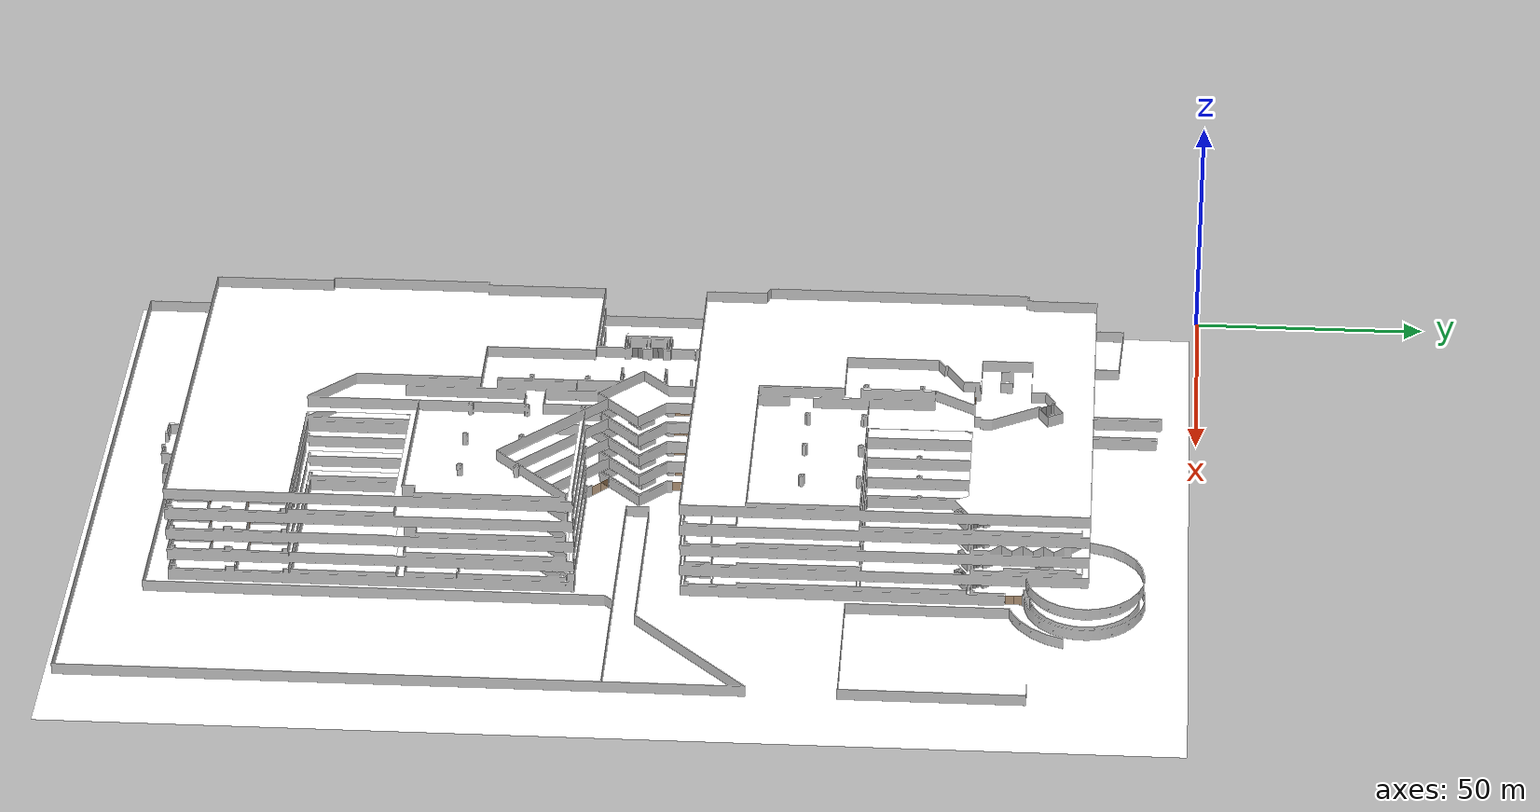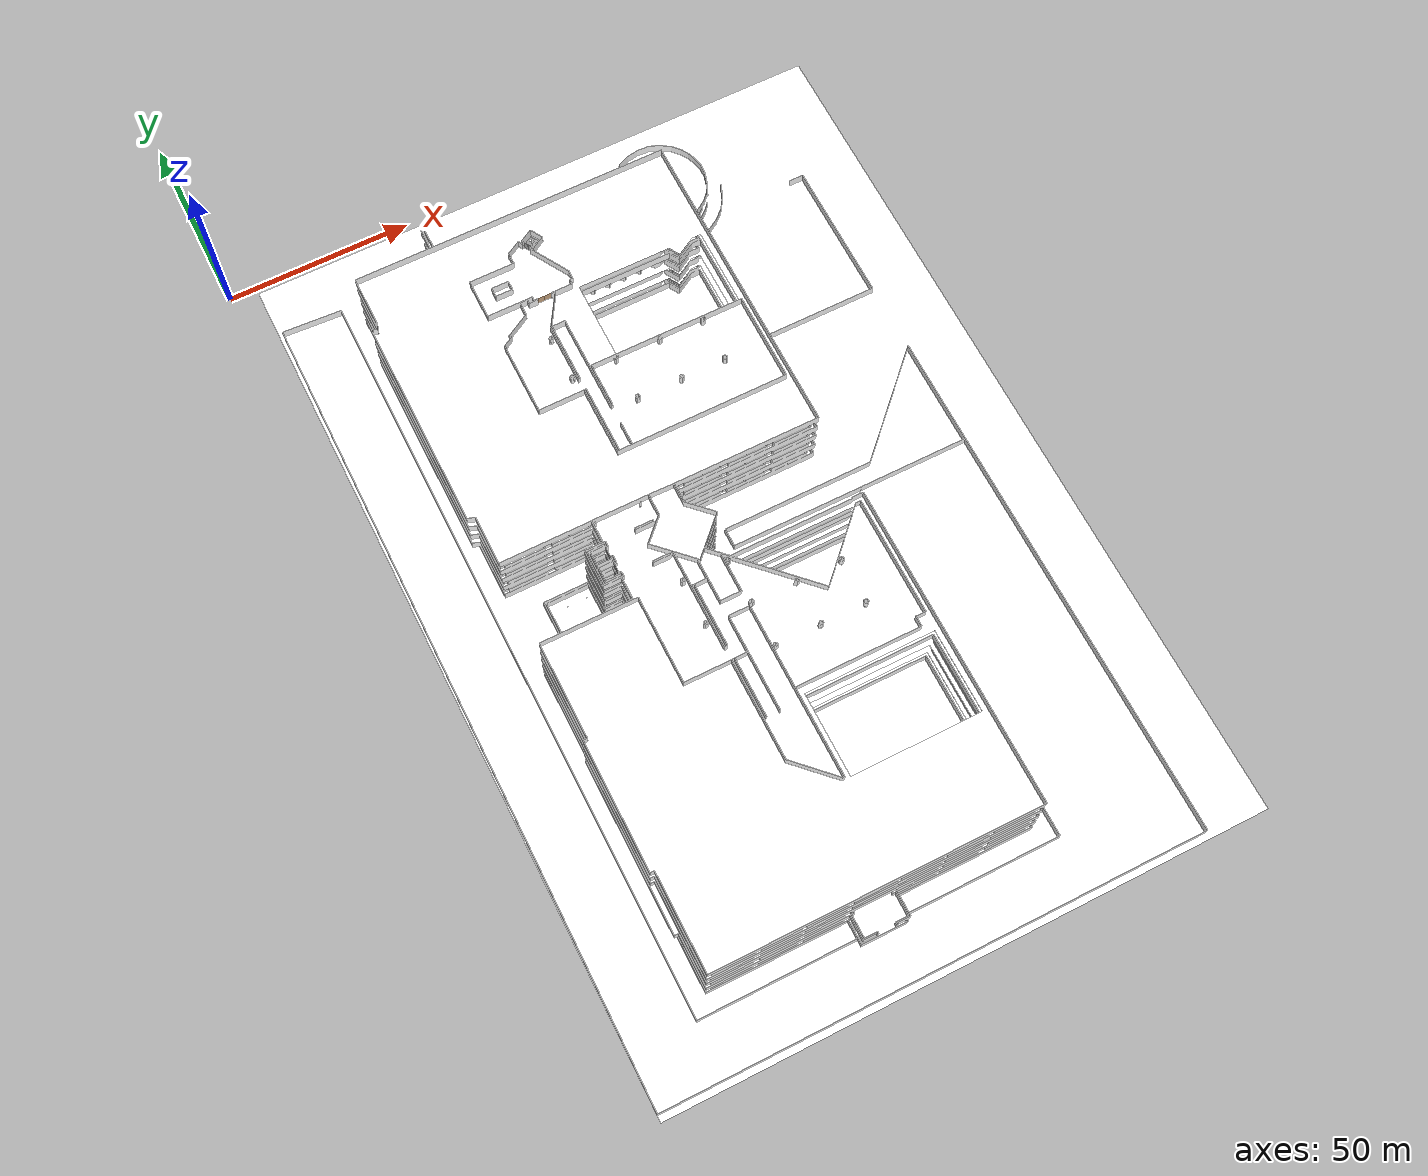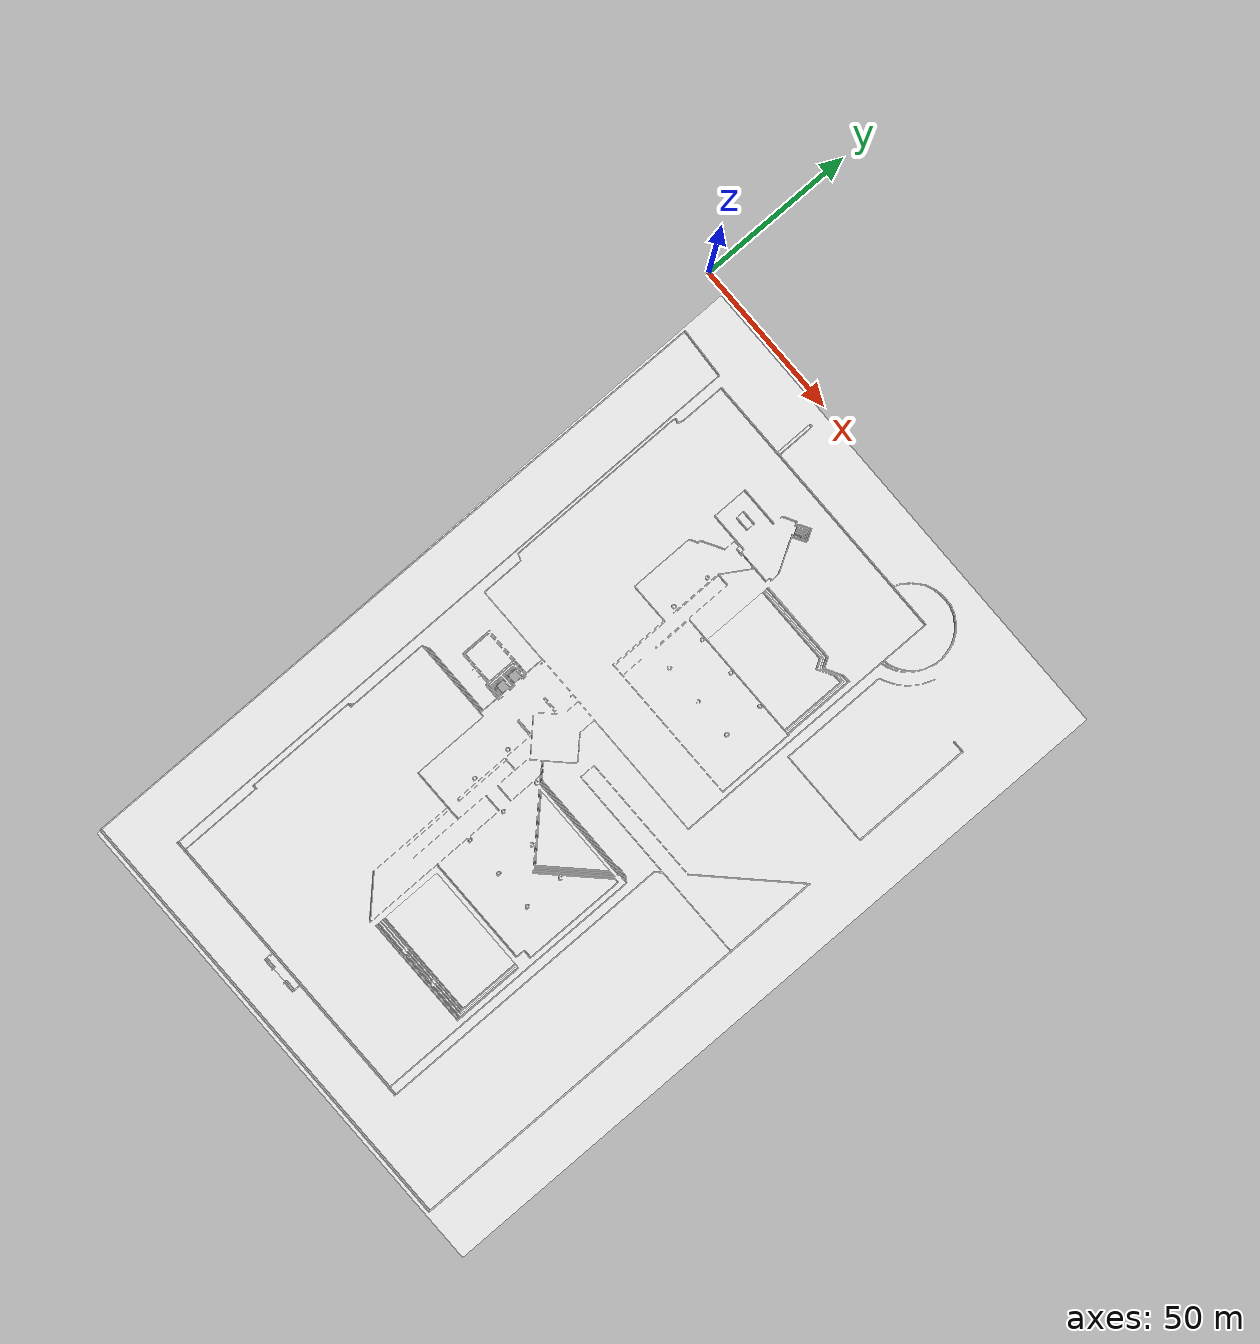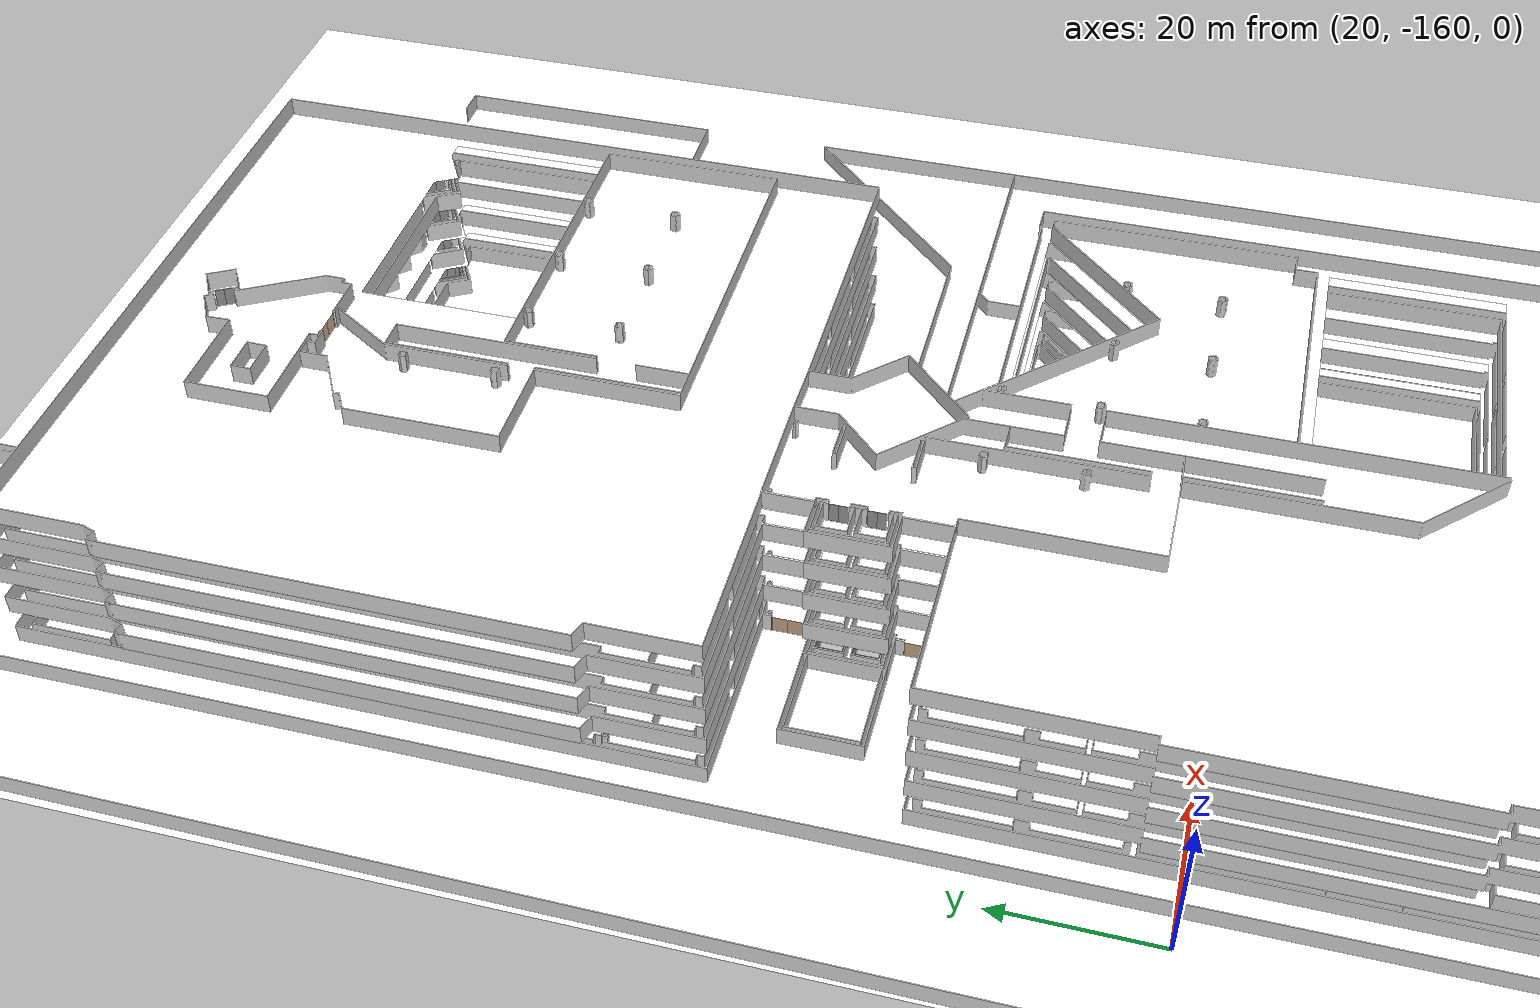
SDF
<sdf version="1.7">
  <world name="sim_world">
    <physics name="10ms" type="ode">
      <max_step_size>0.01</max_step_size>
      <real_time_factor>1.0</real_time_factor>
    </physics>
    <plugin filename="gz-sim-physics-system" name="gz::sim::systems::Physics">
    </plugin>
    <plugin filename="gz-sim-user-commands-system" name="gz::sim::systems::UserCommands">
    </plugin>
    <plugin filename="gz-sim-scene-broadcaster-system" name="gz::sim::systems::SceneBroadcaster">
    </plugin>
    <plugin filename="libdoor.so" name="door">
    </plugin>
    <plugin filename="liblift.so" name="lift">
    </plugin>
    <scene>
      <ambient>1 1 1</ambient>
      <background>0.8 0.8 0.8</background>
      <grid>false</grid>
    </scene>
    <gui fullscreen="0">
      <window>
        <width>1000</width>
        <height>845</height>
        <style material_theme="Light" material_primary="DeepOrange" material_accent="LightBlue" toolbar_color_light="#f3f3f3" toolbar_text_color_light="#111111" toolbar_color_dark="#414141" toolbar_text_color_dark="#f3f3f3" plugin_toolbar_color_light="#bbdefb" plugin_toolbar_text_color_light="#111111" plugin_toolbar_color_dark="#607d8b" plugin_toolbar_text_color_dark="#eeeeee" />
        <menus>
          <drawer default="false">
          </drawer>
        </menus>
      </window>
      <plugin filename="MinimalScene" name="3D View">
        <gz-gui>
          <title>3D View</title>
          <property type="bool" key="showTitleBar">false</property>
          <property type="string" key="state">docked</property>
        </gz-gui>
        <engine>ogre2</engine>
        <scene>scene</scene>
        <ambient_light>0.4 0.4 0.4</ambient_light>
        <background_color>0.8 0.8 0.8</background_color>
        <camera_pose>86.55298013245033 -138.5480579917666 10 0 0.6 1.57</camera_pose>
      </plugin>
      <plugin filename="EntityContextMenuPlugin" name="Entity context menu">
        <gz-gui>
          <property key="state" type="string">floating</property>
          <property key="width" type="double">5</property>
          <property key="height" type="double">5</property>
          <property key="showTitleBar" type="bool">false</property>
        </gz-gui>
      </plugin>
      <plugin filename="GzSceneManager" name="Scene Manager">
        <gz-gui>
          <property key="resizable" type="bool">false</property>
          <property key="width" type="double">5</property>
          <property key="height" type="double">5</property>
          <property key="state" type="string">floating</property>
          <property key="showTitleBar" type="bool">false</property>
        </gz-gui>
      </plugin>
      <plugin filename="InteractiveViewControl" name="Interactive view control">
        <gz-gui>
          <property key="resizable" type="bool">false</property>
          <property key="width" type="double">5</property>
          <property key="height" type="double">5</property>
          <property key="state" type="string">floating</property>
          <property key="showTitleBar" type="bool">false</property>
        </gz-gui>
      </plugin>
      <plugin filename="CameraTracking" name="Camera Tracking">
        <gz-gui>
          <property key="resizable" type="bool">false</property>
          <property key="width" type="double">5</property>
          <property key="height" type="double">5</property>
          <property key="state" type="string">floating</property>
          <property key="showTitleBar" type="bool">false</property>
        </gz-gui>
      </plugin>
      <plugin filename="MarkerManager" name="Marker manager">
        <gz-gui>
          <property key="resizable" type="bool">false</property>
          <property key="width" type="double">5</property>
          <property key="height" type="double">5</property>
          <property key="state" type="string">floating</property>
          <property key="showTitleBar" type="bool">false</property>
        </gz-gui>
      </plugin>
      <plugin filename="SelectEntities" name="Select Entities">
        <gz-gui>
          <property key="resizable" type="bool">false</property>
          <property key="width" type="double">5</property>
          <property key="height" type="double">5</property>
          <property key="state" type="string">floating</property>
          <property key="showTitleBar" type="bool">false</property>
        </gz-gui>
      </plugin>
      <plugin filename="Spawn" name="Spawn Entities">
        <gz-gui>
          <property key="resizable" type="bool">false</property>
          <property key="width" type="double">5</property>
          <property key="height" type="double">5</property>
          <property key="state" type="string">floating</property>
          <property key="showTitleBar" type="bool">false</property>
        </gz-gui>
      </plugin>
      <plugin filename="VisualizationCapabilities" name="Visualization Capabilities">
        <gz-gui>
          <property key="resizable" type="bool">false</property>
          <property key="width" type="double">5</property>
          <property key="height" type="double">5</property>
          <property key="state" type="string">floating</property>
          <property key="showTitleBar" type="bool">false</property>
        </gz-gui>
      </plugin>
      <plugin filename="WorldControl" name="World control">
        <gz-gui>
          <title>World control</title>
          <property type="bool" key="showTitleBar">false</property>
          <property type="bool" key="resizable">false</property>
          <property type="double" key="height">72</property>
          <property type="double" key="z">1</property>
          <property type="string" key="state">floating</property>
          <anchors target="3D View">
            <line own="left" target="left" />
            <line own="bottom" target="bottom" />
          </anchors>
        </gz-gui>
        <play_pause>true</play_pause>
        <step>true</step>
        <start_paused>true</start_paused>
        <use_event>true</use_event>
      </plugin>
      <plugin filename="WorldStats" name="World stats">
        <gz-gui>
          <title>World stats</title>
          <property type="bool" key="showTitleBar">false</property>
          <property type="bool" key="resizable">false</property>
          <property type="double" key="height">110</property>
          <property type="double" key="width">290</property>
          <property type="double" key="z">1</property>
          <property type="string" key="state">floating</property>
          <anchors target="3D View">
            <line own="right" target="right" />
            <line own="bottom" target="bottom" />
          </anchors>
        </gz-gui>
        <sim_time>true</sim_time>
        <real_time>true</real_time>
        <real_time_factor>true</real_time_factor>
        <iterations>true</iterations>
      </plugin>
      <plugin filename="Shapes" name="Shapes">
        <gz-gui>
          <property key="resizable" type="bool">false</property>
          <property key="x" type="double">0</property>
          <property key="y" type="double">0</property>
          <property key="width" type="double">250</property>
          <property key="height" type="double">50</property>
          <property key="state" type="string">floating</property>
          <property key="showTitleBar" type="bool">false</property>
          <property key="cardBackground" type="string">#666666</property>
        </gz-gui>
      </plugin>
      <plugin filename="Lights" name="Lights">
        <gz-gui>
          <property key="resizable" type="bool">false</property>
          <property key="x" type="double">250</property>
          <property key="y" type="double">0</property>
          <property key="width" type="double">150</property>
          <property key="height" type="double">50</property>
          <property key="state" type="string">floating</property>
          <property key="showTitleBar" type="bool">false</property>
          <property key="cardBackground" type="string">#666666</property>
        </gz-gui>
      </plugin>
      <plugin filename="TransformControl" name="Transform control">
        <gz-gui>
          <property key="resizable" type="bool">false</property>
          <property key="x" type="double">0</property>
          <property key="y" type="double">50</property>
          <property key="width" type="double">250</property>
          <property key="height" type="double">50</property>
          <property key="state" type="string">floating</property>
          <property key="showTitleBar" type="bool">false</property>
          <property key="cardBackground" type="string">#777777</property>
        </gz-gui>
      </plugin>
      <plugin filename="Screenshot" name="Screenshot">
        <gz-gui>
          <property key="resizable" type="bool">false</property>
          <property key="x" type="double">250</property>
          <property key="y" type="double">50</property>
          <property key="width" type="double">50</property>
          <property key="height" type="double">50</property>
          <property key="state" type="string">floating</property>
          <property key="showTitleBar" type="bool">false</property>
          <property key="cardBackground" type="string">#777777</property>
        </gz-gui>
      </plugin>
      <plugin filename="CopyPaste" name="CopyPaste">
        <gz-gui>
          <property key="resizable" type="bool">false</property>
          <property key="x" type="double">300</property>
          <property key="y" type="double">50</property>
          <property key="width" type="double">100</property>
          <property key="height" type="double">50</property>
          <property key="state" type="string">floating</property>
          <property key="showTitleBar" type="bool">false</property>
          <property key="cardBackground" type="string">#777777</property>
        </gz-gui>
      </plugin>
      <plugin filename="ComponentInspector" name="Component inspector">
        <gz-gui>
          <property type="bool" key="showTitleBar">false</property>
          <property type="string" key="state">docked</property>
        </gz-gui>
      </plugin>
      <plugin filename="EntityTree" name="Entity tree">
        <gz-gui>
          <property type="bool" key="showTitleBar">false</property>
          <property type="string" key="state">docked</property>
        </gz-gui>
      </plugin>
      <plugin filename="toggle_charging" name="toggle_charging" />
      <plugin name="toggle_floors" filename="toggle_floors">
        <floor name="L0" model_name="library_L0">
          <model name="puerta20" />
          <model name="puerta21" />
          <model name="puerta22" />
          <model name="puerta23" />
          <model name="puerta24" />
          <model name="puerta25" />
          <model name="puerta26" />
          <model name="puerta27" />
          <model name="puerta28" />
          <model name="puerta29" />
          <model name="puerta30" />
          <model name="puerta31" />
          <model name="puerta32" />
          <model name="puerta33" />
          <model name="puerta34" />
          <model name="puerta35" />
          <model name="puerta36" />
          <model name="puerta37" />
          <model name="puerta38" />
          <model name="puerta39" />
          <model name="puerta40" />
          <model name="puerta41" />
          <model name="puerta42" />
          <model name="puerta43" />
          <model name="puerta44" />
          <model name="puerta45" />
          <model name="puerta46" />
          <model name="puerta47" />
          <model name="puerta48" />
          <model name="puerta49" />
          <model name="puerta50" />
          <model name="puerta51" />
          <model name="puerta52" />
          <model name="puerta53" />
          <model name="puerta54" />
          <model name="puerta55" />
          <model name="puerta56" />
          <model name="puerta57" />
          <model name="puerta58" />
          <model name="puerta59" />
          <model name="puerta60" />
          <model name="puerta61" />
          <model name="puerta62" />
          <model name="puerta63" />
          <model name="puerta64" />
          <model name="puerta65" />
          <model name="puerta66" />
          <model name="puerta67" />
          <model name="puerta68" />
          <model name="puerta69" />
          <model name="puerta70" />
          <model name="puerta71" />
          <model name="puerta72" />
          <model name="puerta73" />
          <model name="puerta74" />
          <model name="puerta75" />
          <model name="puerta76" />
          <model name="puerta77" />
          <model name="puerta78" />
          <model name="puerta79" />
          <model name="puerta80" />
          <model name="puerta81" />
          <model name="puerta82" />
          <model name="puerta83" />
          <model name="puerta84" />
          <model name="puerta85" />
          <model name="puerta86" />
          <model name="puerta87" />
          <model name="puerta88" />
          <model name="puerta89" />
          <model name="puerta90" />
          <model name="puerta91" />
          <model name="ShaftDoor_lift_1_L0_name" />
          <model name="ShaftDoor_lift_2_L0_name" />
          <model name="ShaftDoor_lift_3_L0_name" />
          <model name="ShaftDoor_lift_4_L0_name" />
        </floor>
        <floor name="L1" model_name="library_L1">
          <model name="puerta3149" />
          <model name="puerta3150" />
          <model name="puerta3151" />
          <model name="puerta3152" />
          <model name="puerta3153" />
          <model name="puerta3154" />
          <model name="puerta3155" />
          <model name="puerta3156" />
          <model name="puerta3157" />
          <model name="puerta3158" />
          <model name="puerta3159" />
          <model name="puerta3160" />
          <model name="puerta3161" />
          <model name="puerta3162" />
          <model name="puerta3163" />
          <model name="puerta3164" />
          <model name="puerta3165" />
          <model name="puerta3166" />
          <model name="puerta3167" />
          <model name="puerta3168" />
          <model name="puerta3169" />
          <model name="puerta3170" />
          <model name="puerta3171" />
          <model name="puerta3172" />
          <model name="puerta3173" />
          <model name="puerta3174" />
          <model name="puerta3175" />
          <model name="puerta3176" />
          <model name="puerta3177" />
          <model name="puerta3178" />
          <model name="puerta3179" />
          <model name="puerta3180" />
          <model name="puerta3181" />
          <model name="puerta3182" />
          <model name="puerta3183" />
          <model name="puerta3184" />
          <model name="puerta3185" />
          <model name="puerta3186" />
          <model name="puerta3187" />
          <model name="puerta3188" />
          <model name="puerta3189" />
          <model name="puerta3190" />
          <model name="puerta3191" />
          <model name="puerta3192" />
          <model name="puerta3193" />
          <model name="puerta3194" />
          <model name="puerta3195" />
          <model name="puerta3196" />
          <model name="puerta3197" />
          <model name="ShaftDoor_lift_1_L1_name" />
          <model name="ShaftDoor_lift_2_L1_name" />
          <model name="ShaftDoor_lift_3_L1_name" />
          <model name="ShaftDoor_lift_4_L1_name" />
        </floor>
        <floor name="L2" model_name="library_L2">
          <model name="puerta5247" />
          <model name="puerta5248" />
          <model name="puerta5249" />
          <model name="puerta5250" />
          <model name="puerta5251" />
          <model name="puerta5252" />
          <model name="puerta5253" />
          <model name="puerta5254" />
          <model name="puerta5255" />
          <model name="puerta5256" />
          <model name="puerta5257" />
          <model name="puerta5258" />
          <model name="puerta5259" />
          <model name="puerta5260" />
          <model name="puerta5261" />
          <model name="puerta5262" />
          <model name="puerta5263" />
          <model name="puerta5264" />
          <model name="puerta5265" />
          <model name="puerta5266" />
          <model name="puerta5267" />
          <model name="puerta5268" />
          <model name="puerta5269" />
          <model name="puerta5270" />
          <model name="puerta5271" />
          <model name="puerta5272" />
          <model name="puerta5273" />
          <model name="puerta5274" />
          <model name="puerta5275" />
          <model name="puerta5276" />
          <model name="puerta5277" />
          <model name="puerta5278" />
          <model name="puerta5279" />
          <model name="puerta5280" />
          <model name="puerta5281" />
          <model name="puerta5282" />
          <model name="puerta5283" />
          <model name="puerta5284" />
          <model name="puerta5285" />
          <model name="puerta5286" />
          <model name="puerta5287" />
          <model name="puerta5288" />
          <model name="puerta5289" />
          <model name="puerta5290" />
          <model name="puerta5291" />
          <model name="puerta5292" />
          <model name="puerta5293" />
          <model name="puerta5294" />
          <model name="ShaftDoor_lift_1_L2_name" />
          <model name="ShaftDoor_lift_2_L2_name" />
          <model name="ShaftDoor_lift_3_L2_name" />
          <model name="ShaftDoor_lift_4_L2_name" />
        </floor>
        <floor name="L3" model_name="library_L3">
          <model name="puerta7184" />
          <model name="puerta7185" />
          <model name="puerta7186" />
          <model name="puerta7187" />
          <model name="puerta7188" />
          <model name="puerta7189" />
          <model name="puerta7190" />
          <model name="puerta7191" />
          <model name="puerta7192" />
          <model name="puerta7193" />
          <model name="puerta7194" />
          <model name="puerta7195" />
          <model name="puerta7196" />
          <model name="puerta7197" />
          <model name="puerta7198" />
          <model name="puerta7199" />
          <model name="puerta7200" />
          <model name="puerta7201" />
          <model name="puerta7202" />
          <model name="puerta7203" />
          <model name="puerta7204" />
          <model name="puerta7205" />
          <model name="puerta7206" />
          <model name="puerta7207" />
          <model name="puerta7208" />
          <model name="puerta7209" />
          <model name="puerta7210" />
          <model name="puerta7211" />
          <model name="puerta7212" />
          <model name="puerta7213" />
          <model name="puerta7214" />
          <model name="puerta7215" />
          <model name="puerta7216" />
          <model name="puerta7217" />
          <model name="puerta7218" />
          <model name="puerta7219" />
          <model name="puerta7220" />
          <model name="puerta7221" />
          <model name="puerta7222" />
          <model name="puerta7223" />
          <model name="puerta7224" />
          <model name="puerta7225" />
          <model name="puerta7226" />
          <model name="puerta7227" />
          <model name="puerta7228" />
          <model name="puerta7229" />
          <model name="puerta7230" />
          <model name="puerta7231" />
          <model name="ShaftDoor_lift_1_L3_name" />
          <model name="ShaftDoor_lift_2_L3_name" />
          <model name="ShaftDoor_lift_3_L3_name" />
          <model name="ShaftDoor_lift_4_L3_name" />
        </floor>
        <floor name="L4" model_name="library_L4">
          <model name="puerta8872" />
          <model name="ShaftDoor_lift_1_L4_name" />
          <model name="ShaftDoor_lift_3_L4_name" />
          <model name="ShaftDoor_lift_4_L4_name" />
        </floor>
      </plugin>
    </gui>
    <light type="directional" name="sun">
      <cast_shadows>true</cast_shadows>
      <pose>0 0 10 0 0 0</pose>
      <diffuse>1 1 1 1</diffuse>
      <specular>0.2 0.2 0.2 1</specular>
      <attenuation>
        <range>1000</range>
        <constant>0.09</constant>
        <linear>0.001</linear>
        <quadratic>0.001</quadratic>
      </attenuation>
      <direction>-0.5 0.1 -0.9</direction>
    </light>
    <model name="puerta20">
      <pose>113.41983175228208 -37.8717021657419 0.0 0 0 -1.5573486832499999</pose>
      <link name="right">
        <pose>0.8997770784323755 0 1.11 0 0 0</pose>
        <visual name="right_visual">
          <geometry>
            <box>
              <size>1.789554156864751 0.03 2.2</size>
            </box>
          </geometry>
          <material>
            <ambient>0.5 0.25 0 0.6</ambient>
            <diffuse>0.5 0.25 0 0.6</diffuse>
            <pbr>
              <metal>
                <metalness>0.0</metalness>
              </metal>
            </pbr>
          </material>
        </visual>
        <collision name="right_collision">
          <geometry>
            <box>
              <size>1.789554156864751 0.03 2.2</size>
            </box>
          </geometry>
          <surface>
            <contact>
              <collide_bitmask>0x02</collide_bitmask>
            </contact>
          </surface>
        </collision>
        <inertial>
          <mass>50.0</mass>
          <inertia>
            <ixx>20.17041666666667</ixx>
            <iyy>33.51043366813297</iyy>
            <izz>13.347517001466292</izz>
          </inertia>
        </inertial>
      </link>
      <joint name="right_joint" type="revolute">
        <parent>world</parent>
        <child>right</child>
        <axis>
          <xyz>0 0 -1</xyz>
          <limit>
            <lower>0</lower>
            <upper>1.57</upper>
          </limit>
        </axis>
        <pose>0.8997770784323755 0 0 0 0 0</pose>
      </joint>
      <link name="left">
        <pose>-0.8997770784323755 0 1.11 0 0 0</pose>
        <visual name="left_visual">
          <geometry>
            <box>
              <size>1.789554156864751 0.03 2.2</size>
            </box>
          </geometry>
          <material>
            <ambient>0.5 0.25 0 0.6</ambient>
            <diffuse>0.5 0.25 0 0.6</diffuse>
            <pbr>
              <metal>
                <metalness>0.0</metalness>
              </metal>
            </pbr>
          </material>
        </visual>
        <collision name="left_collision">
          <geometry>
            <box>
              <size>1.789554156864751 0.03 2.2</size>
            </box>
          </geometry>
          <surface>
            <contact>
              <collide_bitmask>0x02</collide_bitmask>
            </contact>
          </surface>
        </collision>
        <inertial>
          <mass>50.0</mass>
          <inertia>
            <ixx>20.17041666666667</ixx>
            <iyy>33.51043366813297</iyy>
            <izz>13.347517001466292</izz>
          </inertia>
        </inertial>
      </link>
      <joint name="left_joint" type="revolute">
        <parent>world</parent>
        <child>left</child>
        <axis>
          <xyz>0 0 -1</xyz>
          <limit>
            <lower>-1.57</lower>
            <upper>0</upper>
          </limit>
        </axis>
        <pose>-0.8997770784323755 0 0 0 0 0</pose>
      </joint>
      <plugin name="register_component" filename="libregister_component.so">
        <component name="Door">
          <v_max_door>0.5</v_max_door>
          <a_max_door>0.3</a_max_door>
          <a_nom_door>0.15</a_nom_door>
          <dx_min_door>0.01</dx_min_door>
          <f_max_door>500.0</f_max_door>
          <ros_interface>true</ros_interface>
          <door name="puerta20" type="DoubleSwingDoor" left_joint_name="left_joint" right_joint_name="right_joint" />
        </component>
      </plugin>
    </model>
    <model name="puerta21">
      <pose>70.95358868802577 -43.59432611419366 0.0 0 0 0.5295755033336558</pose>
      <link name="right">
        <pose>0.948866262881859 0 1.11 0 0 0</pose>
        <visual name="right_visual">
          <geometry>
            <box>
              <size>1.887732525763718 0.03 2.2</size>
            </box>
          </geometry>
          <material>
            <ambient>0.5 0.25 0 0.6</ambient>
            <diffuse>0.5 0.25 0 0.6</diffuse>
            <pbr>
              <metal>
                <metalness>0.0</metalness>
              </metal>
            </pbr>
          </material>
        </visual>
        <collision name="right_collision">
          <geometry>
            <box>
              <size>1.887732525763718 0.03 2.2</size>
            </box>
          </geometry>
          <surface>
            <contact>
              <collide_bitmask>0x02</collide_bitmask>
            </contact>
          </surface>
        </collision>
        <inertial>
          <mass>50.0</mass>
          <inertia>
            <ixx>20.17041666666667</ixx>
            <iyy>35.01472537010945</iyy>
            <izz>14.85180870344278</izz>
          </inertia>
        </inertial>
      </link>
      <joint name="right_joint" type="revolute">
        <parent>world</parent>
        <child>right</child>
        <axis>
          <xyz>0 0 -1</xyz>
          <limit>
            <lower>0</lower>
            <upper>1.57</upper>
          </limit>
        </axis>
        <pose>0.948866262881859 0 0 0 0 0</pose>
      </joint>
      <link name="left">
        <pose>-0.948866262881859 0 1.11 0 0 0</pose>
        <visual name="left_visual">
          <geometry>
            <box>
              <size>1.887732525763718 0.03 2.2</size>
            </box>
          </geometry>
          <material>
            <ambient>0.5 0.25 0 0.6</ambient>
            <diffuse>0.5 0.25 0 0.6</diffuse>
            <pbr>
              <metal>
                <metalness>0.0</metalness>
              </metal>
            </pbr>
          </material>
        </visual>
        <collision name="left_collision">
          <geometry>
            <box>
              <size>1.887732525763718 0.03 2.2</size>
            </box>
          </geometry>
          <surface>
            <contact>
              <collide_bitmask>0x02</collide_bitmask>
            </contact>
          </surface>
        </collision>
        <inertial>
          <mass>50.0</mass>
          <inertia>
            <ixx>20.17041666666667</ixx>
            <iyy>35.01472537010945</iyy>
            <izz>14.85180870344278</izz>
          </inertia>
        </inertial>
      </link>
      <joint name="left_joint" type="revolute">
        <parent>world</parent>
        <child>left</child>
        <axis>
          <xyz>0 0 -1</xyz>
          <limit>
            <lower>-1.57</lower>
            <upper>0</upper>
          </limit>
        </axis>
        <pose>-0.948866262881859 0 0 0 0 0</pose>
      </joint>
      <plugin name="register_component" filename="libregister_component.so">
        <component name="Door">
          <v_max_door>0.5</v_max_door>
          <a_max_door>0.3</a_max_door>
          <a_nom_door>0.15</a_nom_door>
          <dx_min_door>0.01</dx_min_door>
          <f_max_door>500.0</f_max_door>
          <ros_interface>true</ros_interface>
          <door name="puerta21" type="DoubleSwingDoor" left_joint_name="left_joint" right_joint_name="right_joint" />
        </component>
      </plugin>
    </model>
    <model name="puerta22">
      <pose>50.48691605512798 -34.29860390191516 0.0 0 0 -0.012374502945588612</pose>
      <link name="right">
        <pose>0.9640616405178116 0 1.11 0 0 0</pose>
        <visual name="right_visual">
          <geometry>
            <box>
              <size>1.9181232810356232 0.03 2.2</size>
            </box>
          </geometry>
          <material>
            <ambient>0.5 0.25 0 0.6</ambient>
            <diffuse>0.5 0.25 0 0.6</diffuse>
            <pbr>
              <metal>
                <metalness>0.0</metalness>
              </metal>
            </pbr>
          </material>
        </visual>
        <collision name="right_collision">
          <geometry>
            <box>
              <size>1.9181232810356232 0.03 2.2</size>
            </box>
          </geometry>
          <surface>
            <contact>
              <collide_bitmask>0x02</collide_bitmask>
            </contact>
          </surface>
        </collision>
        <inertial>
          <mass>50.0</mass>
          <inertia>
            <ixx>20.17041666666667</ixx>
            <iyy>35.49665383854527</iyy>
            <izz>15.333737171878605</izz>
          </inertia>
        </inertial>
      </link>
      <joint name="right_joint" type="revolute">
        <parent>world</parent>
        <child>right</child>
        <axis>
          <xyz>0 0 -1</xyz>
          <limit>
            <lower>0</lower>
            <upper>1.57</upper>
          </limit>
        </axis>
        <pose>0.9640616405178116 0 0 0 0 0</pose>
      </joint>
      <link name="left">
        <pose>-0.9640616405178116 0 1.11 0 0 0</pose>
        <visual name="left_visual">
          <geometry>
            <box>
              <size>1.9181232810356232 0.03 2.2</size>
            </box>
          </geometry>
          <material>
            <ambient>0.5 0.25 0 0.6</ambient>
            <diffuse>0.5 0.25 0 0.6</diffuse>
            <pbr>
              <metal>
                <metalness>0.0</metalness>
              </metal>
            </pbr>
          </material>
        </visual>
        <collision name="left_collision">
          <geometry>
            <box>
              <size>1.9181232810356232 0.03 2.2</size>
            </box>
          </geometry>
          <surface>
            <contact>
              <collide_bitmask>0x02</collide_bitmask>
            </contact>
          </surface>
        </collision>
        <inertial>
          <mass>50.0</mass>
          <inertia>
            <ixx>20.17041666666667</ixx>
            <iyy>35.49665383854527</iyy>
            <izz>15.333737171878605</izz>
          </inertia>
        </inertial>
      </link>
      <joint name="left_joint" type="revolute">
        <parent>world</parent>
        <child>left</child>
        <axis>
          <xyz>0 0 -1</xyz>
          <limit>
            <lower>-1.57</lower>
            <upper>0</upper>
          </limit>
        </axis>
        <pose>-0.9640616405178116 0 0 0 0 0</pose>
      </joint>
      <plugin name="register_component" filename="libregister_component.so">
        <component name="Door">
          <v_max_door>0.5</v_max_door>
          <a_max_door>0.3</a_max_door>
          <a_nom_door>0.15</a_nom_door>
          <dx_min_door>0.01</dx_min_door>
          <f_max_door>500.0</f_max_door>
          <ros_interface>true</ros_interface>
          <door name="puerta22" type="DoubleSwingDoor" left_joint_name="left_joint" right_joint_name="right_joint" />
        </component>
      </plugin>
    </model>
    <model name="puerta23">
      <pose>38.532163952031496 -34.27710757114731 0.0 0 0 0.001226195391021793</pose>
      <link name="right">
        <pose>0.9633978962672806 0 1.11 0 0 0</pose>
        <visual name="right_visual">
          <geometry>
            <box>
              <size>1.9167957925345611 0.03 2.2</size>
            </box>
          </geometry>
          <material>
            <ambient>0.5 0.25 0 0.6</ambient>
            <diffuse>0.5 0.25 0 0.6</diffuse>
            <pbr>
              <metal>
                <metalness>0.0</metalness>
              </metal>
            </pbr>
          </material>
        </visual>
        <collision name="right_collision">
          <geometry>
            <box>
              <size>1.9167957925345611 0.03 2.2</size>
            </box>
          </geometry>
          <surface>
            <contact>
              <collide_bitmask>0x02</collide_bitmask>
            </contact>
          </surface>
        </collision>
        <inertial>
          <mass>50.0</mass>
          <inertia>
            <ixx>20.17041666666667</ixx>
            <iyy>35.47544212615916</iyy>
            <izz>15.312525459492488</izz>
          </inertia>
        </inertial>
      </link>
      <joint name="right_joint" type="revolute">
        <parent>world</parent>
        <child>right</child>
        <axis>
          <xyz>0 0 -1</xyz>
          <limit>
            <lower>0</lower>
            <upper>1.57</upper>
          </limit>
        </axis>
        <pose>0.9633978962672806 0 0 0 0 0</pose>
      </joint>
      <link name="left">
        <pose>-0.9633978962672806 0 1.11 0 0 0</pose>
        <visual name="left_visual">
          <geometry>
            <box>
              <size>1.9167957925345611 0.03 2.2</size>
            </box>
          </geometry>
          <material>
            <ambient>0.5 0.25 0 0.6</ambient>
            <diffuse>0.5 0.25 0 0.6</diffuse>
            <pbr>
              <metal>
                <metalness>0.0</metalness>
              </metal>
            </pbr>
          </material>
        </visual>
        <collision name="left_collision">
          <geometry>
            <box>
              <size>1.9167957925345611 0.03 2.2</size>
            </box>
          </geometry>
          <surface>
            <contact>
              <collide_bitmask>0x02</collide_bitmask>
            </contact>
          </surface>
        </collision>
        <inertial>
          <mass>50.0</mass>
          <inertia>
            <ixx>20.17041666666667</ixx>
            <iyy>35.47544212615916</iyy>
            <izz>15.312525459492488</izz>
          </inertia>
        </inertial>
      </link>
      <joint name="left_joint" type="revolute">
        <parent>world</parent>
        <child>left</child>
        <axis>
          <xyz>0 0 -1</xyz>
          <limit>
            <lower>-1.57</lower>
            <upper>0</upper>
          </limit>
        </axis>
        <pose>-0.9633978962672806 0 0 0 0 0</pose>
      </joint>
      <plugin name="register_component" filename="libregister_component.so">
        <component name="Door">
          <v_max_door>0.5</v_max_door>
          <a_max_door>0.3</a_max_door>
          <a_nom_door>0.15</a_nom_door>
          <dx_min_door>0.01</dx_min_door>
          <f_max_door>500.0</f_max_door>
          <ros_interface>true</ros_interface>
          <door name="puerta23" type="DoubleSwingDoor" left_joint_name="left_joint" right_joint_name="right_joint" />
        </component>
      </plugin>
    </model>
    <model name="puerta24">
      <pose>38.52203329156971 -43.42795775908358 0.0 0 0 -0.014637017318326345</pose>
      <link name="right">
        <pose>0.9587388189230233 0 1.11 0 0 0</pose>
        <visual name="right_visual">
          <geometry>
            <box>
              <size>1.9074776378460465 0.03 2.2</size>
            </box>
          </geometry>
          <material>
            <ambient>0.5 0.25 0 0.6</ambient>
            <diffuse>0.5 0.25 0 0.6</diffuse>
            <pbr>
              <metal>
                <metalness>0.0</metalness>
              </metal>
            </pbr>
          </material>
        </visual>
        <collision name="right_collision">
          <geometry>
            <box>
              <size>1.9074776378460465 0.03 2.2</size>
            </box>
          </geometry>
          <surface>
            <contact>
              <collide_bitmask>0x02</collide_bitmask>
            </contact>
          </surface>
        </collision>
        <inertial>
          <mass>50.0</mass>
          <inertia>
            <ixx>20.17041666666667</ixx>
            <iyy>35.326962245344724</iyy>
            <izz>15.164045578678056</izz>
          </inertia>
        </inertial>
      </link>
      <joint name="right_joint" type="revolute">
        <parent>world</parent>
        <child>right</child>
        <axis>
          <xyz>0 0 -1</xyz>
          <limit>
            <lower>0</lower>
            <upper>1.57</upper>
          </limit>
        </axis>
        <pose>0.9587388189230233 0 0 0 0 0</pose>
      </joint>
      <link name="left">
        <pose>-0.9587388189230233 0 1.11 0 0 0</pose>
        <visual name="left_visual">
          <geometry>
            <box>
              <size>1.9074776378460465 0.03 2.2</size>
            </box>
          </geometry>
          <material>
            <ambient>0.5 0.25 0 0.6</ambient>
            <diffuse>0.5 0.25 0 0.6</diffuse>
            <pbr>
              <metal>
                <metalness>0.0</metalness>
              </metal>
            </pbr>
          </material>
        </visual>
        <collision name="left_collision">
          <geometry>
            <box>
              <size>1.9074776378460465 0.03 2.2</size>
            </box>
          </geometry>
          <surface>
            <contact>
              <collide_bitmask>0x02</collide_bitmask>
            </contact>
          </surface>
        </collision>
        <inertial>
          <mass>50.0</mass>
          <inertia>
            <ixx>20.17041666666667</ixx>
            <iyy>35.326962245344724</iyy>
            <izz>15.164045578678056</izz>
          </inertia>
        </inertial>
      </link>
      <joint name="left_joint" type="revolute">
        <parent>world</parent>
        <child>left</child>
        <axis>
          <xyz>0 0 -1</xyz>
          <limit>
            <lower>-1.57</lower>
            <upper>0</upper>
          </limit>
        </axis>
        <pose>-0.9587388189230233 0 0 0 0 0</pose>
      </joint>
      <plugin name="register_component" filename="libregister_component.so">
        <component name="Door">
          <v_max_door>0.5</v_max_door>
          <a_max_door>0.3</a_max_door>
          <a_nom_door>0.15</a_nom_door>
          <dx_min_door>0.01</dx_min_door>
          <f_max_door>500.0</f_max_door>
          <ros_interface>true</ros_interface>
          <door name="puerta24" type="DoubleSwingDoor" left_joint_name="left_joint" right_joint_name="right_joint" />
        </component>
      </plugin>
    </model>
    <model name="puerta25">
      <pose>53.52785036692322 -64.84820118131377 0.0 0 0 -1.5655381820930956</pose>
      <link name="right">
        <pose>0.9582287468332203 0 1.11 0 0 0</pose>
        <visual name="right_visual">
          <geometry>
            <box>
              <size>1.9064574936664407 0.03 2.2</size>
            </box>
          </geometry>
          <material>
            <ambient>0.5 0.25 0 0.6</ambient>
            <diffuse>0.5 0.25 0 0.6</diffuse>
            <pbr>
              <metal>
                <metalness>0.0</metalness>
              </metal>
            </pbr>
          </material>
        </visual>
        <collision name="right_collision">
          <geometry>
            <box>
              <size>1.9064574936664407 0.03 2.2</size>
            </box>
          </geometry>
          <surface>
            <contact>
              <collide_bitmask>0x02</collide_bitmask>
            </contact>
          </surface>
        </collision>
        <inertial>
          <mass>50.0</mass>
          <inertia>
            <ixx>20.17041666666667</ixx>
            <iyy>35.31075072982053</iyy>
            <izz>15.147834063153864</izz>
          </inertia>
        </inertial>
      </link>
      <joint name="right_joint" type="revolute">
        <parent>world</parent>
        <child>right</child>
        <axis>
          <xyz>0 0 -1</xyz>
          <limit>
            <lower>0</lower>
            <upper>1.57</upper>
          </limit>
        </axis>
        <pose>0.9582287468332203 0 0 0 0 0</pose>
      </joint>
      <link name="left">
        <pose>-0.9582287468332203 0 1.11 0 0 0</pose>
        <visual name="left_visual">
          <geometry>
            <box>
              <size>1.9064574936664407 0.03 2.2</size>
            </box>
          </geometry>
          <material>
            <ambient>0.5 0.25 0 0.6</ambient>
            <diffuse>0.5 0.25 0 0.6</diffuse>
            <pbr>
              <metal>
                <metalness>0.0</metalness>
              </metal>
            </pbr>
          </material>
        </visual>
        <collision name="left_collision">
          <geometry>
            <box>
              <size>1.9064574936664407 0.03 2.2</size>
            </box>
          </geometry>
          <surface>
            <contact>
              <collide_bitmask>0x02</collide_bitmask>
            </contact>
          </surface>
        </collision>
        <inertial>
          <mass>50.0</mass>
          <inertia>
            <ixx>20.17041666666667</ixx>
            <iyy>35.31075072982053</iyy>
            <izz>15.147834063153864</izz>
          </inertia>
        </inertial>
      </link>
      <joint name="left_joint" type="revolute">
        <parent>world</parent>
        <child>left</child>
        <axis>
          <xyz>0 0 -1</xyz>
          <limit>
            <lower>-1.57</lower>
            <upper>0</upper>
          </limit>
        </axis>
        <pose>-0.9582287468332203 0 0 0 0 0</pose>
      </joint>
      <plugin name="register_component" filename="libregister_component.so">
        <component name="Door">
          <v_max_door>0.5</v_max_door>
          <a_max_door>0.3</a_max_door>
          <a_nom_door>0.15</a_nom_door>
          <dx_min_door>0.01</dx_min_door>
          <f_max_door>500.0</f_max_door>
          <ros_interface>true</ros_interface>
          <door name="puerta25" type="DoubleSwingDoor" left_joint_name="left_joint" right_joint_name="right_joint" />
        </component>
      </plugin>
    </model>
    <model name="puerta26">
      <pose>77.00427778772149 -43.299230356184 0.0 0 0 2.096169444582715</pose>
      <link name="right">
        <pose>0.95245293144521 0 1.11 0 0 0</pose>
        <visual name="right_visual">
          <geometry>
            <box>
              <size>1.89490586289042 0.03 2.2</size>
            </box>
          </geometry>
          <material>
            <ambient>0.5 0.25 0 0.6</ambient>
            <diffuse>0.5 0.25 0 0.6</diffuse>
            <pbr>
              <metal>
                <metalness>0.0</metalness>
              </metal>
            </pbr>
          </material>
        </visual>
        <collision name="right_collision">
          <geometry>
            <box>
              <size>1.89490586289042 0.03 2.2</size>
            </box>
          </geometry>
          <surface>
            <contact>
              <collide_bitmask>0x02</collide_bitmask>
            </contact>
          </surface>
        </collision>
        <inertial>
          <mass>50.0</mass>
          <inertia>
            <ixx>20.17041666666667</ixx>
            <iyy>35.12778428840204</iyy>
            <izz>14.964867621735367</izz>
          </inertia>
        </inertial>
      </link>
      <joint name="right_joint" type="revolute">
        <parent>world</parent>
        <child>right</child>
        <axis>
          <xyz>0 0 -1</xyz>
          <limit>
            <lower>0</lower>
            <upper>1.57</upper>
          </limit>
        </axis>
        <pose>0.95245293144521 0 0 0 0 0</pose>
      </joint>
      <link name="left">
        <pose>-0.95245293144521 0 1.11 0 0 0</pose>
        <visual name="left_visual">
          <geometry>
            <box>
              <size>1.89490586289042 0.03 2.2</size>
            </box>
          </geometry>
          <material>
            <ambient>0.5 0.25 0 0.6</ambient>
            <diffuse>0.5 0.25 0 0.6</diffuse>
            <pbr>
              <metal>
                <metalness>0.0</metalness>
              </metal>
            </pbr>
          </material>
        </visual>
        <collision name="left_collision">
          <geometry>
            <box>
              <size>1.89490586289042 0.03 2.2</size>
            </box>
          </geometry>
          <surface>
            <contact>
              <collide_bitmask>0x02</collide_bitmask>
            </contact>
          </surface>
        </collision>
        <inertial>
          <mass>50.0</mass>
          <inertia>
            <ixx>20.17041666666667</ixx>
            <iyy>35.12778428840204</iyy>
            <izz>14.964867621735367</izz>
          </inertia>
        </inertial>
      </link>
      <joint name="left_joint" type="revolute">
        <parent>world</parent>
        <child>left</child>
        <axis>
          <xyz>0 0 -1</xyz>
          <limit>
            <lower>-1.57</lower>
            <upper>0</upper>
          </limit>
        </axis>
        <pose>-0.95245293144521 0 0 0 0 0</pose>
      </joint>
      <plugin name="register_component" filename="libregister_component.so">
        <component name="Door">
          <v_max_door>0.5</v_max_door>
          <a_max_door>0.3</a_max_door>
          <a_nom_door>0.15</a_nom_door>
          <dx_min_door>0.01</dx_min_door>
          <f_max_door>500.0</f_max_door>
          <ros_interface>true</ros_interface>
          <door name="puerta26" type="DoubleSwingDoor" left_joint_name="left_joint" right_joint_name="right_joint" />
        </component>
      </plugin>
    </model>
    <model name="puerta27">
      <pose>55.61039914086271 -94.61677107571147 0.0 0 0 -0.004022834889678894</pose>
      <link name="right">
        <pose>0.7408060658932571 0 1.11 0 0 0</pose>
        <visual name="right_visual">
          <geometry>
            <box>
              <size>1.4716121317865143 0.03 2.2</size>
            </box>
          </geometry>
          <material>
            <ambient>0.5 0.25 0 0.6</ambient>
            <diffuse>0.5 0.25 0 0.6</diffuse>
            <pbr>
              <metal>
                <metalness>0.0</metalness>
              </metal>
            </pbr>
          </material>
        </visual>
        <collision name="right_collision">
          <geometry>
            <box>
              <size>1.4716121317865143 0.03 2.2</size>
            </box>
          </geometry>
          <surface>
            <contact>
              <collide_bitmask>0x02</collide_bitmask>
            </contact>
          </surface>
        </collision>
        <inertial>
          <mass>50.0</mass>
          <inertia>
            <ixx>20.17041666666667</ixx>
            <iyy>29.19017611008854</iyy>
            <izz>9.027259443421872</izz>
          </inertia>
        </inertial>
      </link>
      <joint name="right_joint" type="revolute">
        <parent>world</parent>
        <child>right</child>
        <axis>
          <xyz>0 0 -1</xyz>
          <limit>
            <lower>0</lower>
            <upper>1.57</upper>
          </limit>
        </axis>
        <pose>0.7408060658932571 0 0 0 0 0</pose>
      </joint>
      <link name="left">
        <pose>-0.7408060658932571 0 1.11 0 0 0</pose>
        <visual name="left_visual">
          <geometry>
            <box>
              <size>1.4716121317865143 0.03 2.2</size>
            </box>
          </geometry>
          <material>
            <ambient>0.5 0.25 0 0.6</ambient>
            <diffuse>0.5 0.25 0 0.6</diffuse>
            <pbr>
              <metal>
                <metalness>0.0</metalness>
              </metal>
            </pbr>
          </material>
        </visual>
        <collision name="left_collision">
          <geometry>
            <box>
              <size>1.4716121317865143 0.03 2.2</size>
            </box>
          </geometry>
          <surface>
            <contact>
              <collide_bitmask>0x02</collide_bitmask>
            </contact>
          </surface>
        </collision>
        <inertial>
          <mass>50.0</mass>
          <inertia>
            <ixx>20.17041666666667</ixx>
            <iyy>29.19017611008854</iyy>
            <izz>9.027259443421872</izz>
          </inertia>
        </inertial>
      </link>
      <joint name="left_joint" type="revolute">
        <parent>world</parent>
        <child>left</child>
        <axis>
          <xyz>0 0 -1</xyz>
          <limit>
            <lower>-1.57</lower>
            <upper>0</upper>
          </limit>
        </axis>
        <pose>-0.7408060658932571 0 0 0 0 0</pose>
      </joint>
      <plugin name="register_component" filename="libregister_component.so">
        <component name="Door">
          <v_max_door>0.5</v_max_door>
          <a_max_door>0.3</a_max_door>
          <a_nom_door>0.15</a_nom_door>
          <dx_min_door>0.01</dx_min_door>
          <f_max_door>500.0</f_max_door>
          <ros_interface>true</ros_interface>
          <door name="puerta27" type="DoubleSwingDoor" left_joint_name="left_joint" right_joint_name="right_joint" />
        </component>
      </plugin>
    </model>
    <model name="puerta28">
      <pose>56.73398961875783 -106.65507427957759 0.0 0 0 0.005687130982802125</pose>
      <link name="right">
        <pose>0.7380287599410226 0 1.11 0 0 0</pose>
        <visual name="right_visual">
          <geometry>
            <box>
              <size>1.4660575198820451 0.03 2.2</size>
            </box>
          </geometry>
          <material>
            <ambient>0.5 0.25 0 0.6</ambient>
            <diffuse>0.5 0.25 0 0.6</diffuse>
            <pbr>
              <metal>
                <metalness>0.0</metalness>
              </metal>
            </pbr>
          </material>
        </visual>
        <collision name="right_collision">
          <geometry>
            <box>
              <size>1.4660575198820451 0.03 2.2</size>
            </box>
          </geometry>
          <surface>
            <contact>
              <collide_bitmask>0x02</collide_bitmask>
            </contact>
          </surface>
        </collision>
        <inertial>
          <mass>50.0</mass>
          <inertia>
            <ixx>20.17041666666667</ixx>
            <iyy>29.12218604834456</iyy>
            <izz>8.95926938167789</izz>
          </inertia>
        </inertial>
      </link>
      <joint name="right_joint" type="revolute">
        <parent>world</parent>
        <child>right</child>
        <axis>
          <xyz>0 0 -1</xyz>
          <limit>
            <lower>0</lower>
            <upper>1.57</upper>
          </limit>
        </axis>
        <pose>0.7380287599410226 0 0 0 0 0</pose>
      </joint>
      <link name="left">
        <pose>-0.7380287599410226 0 1.11 0 0 0</pose>
        <visual name="left_visual">
          <geometry>
            <box>
              <size>1.4660575198820451 0.03 2.2</size>
            </box>
          </geometry>
          <material>
            <ambient>0.5 0.25 0 0.6</ambient>
            <diffuse>0.5 0.25 0 0.6</diffuse>
            <pbr>
              <metal>
                <metalness>0.0</metalness>
              </metal>
            </pbr>
          </material>
        </visual>
        <collision name="left_collision">
          <geometry>
            <box>
              <size>1.4660575198820451 0.03 2.2</size>
            </box>
          </geometry>
          <surface>
            <contact>
              <collide_bitmask>0x02</collide_bitmask>
            </contact>
          </surface>
        </collision>
        <inertial>
          <mass>50.0</mass>
          <inertia>
            <ixx>20.17041666666667</ixx>
            <iyy>29.12218604834456</iyy>
            <izz>8.95926938167789</izz>
          </inertia>
        </inertial>
      </link>
      <joint name="left_joint" type="revolute">
        <parent>world</parent>
        <child>left</child>
        <axis>
          <xyz>0 0 -1</xyz>
          <limit>
            <lower>-1.57</lower>
            <upper>0</upper>
          </limit>
        </axis>
        <pose>-0.7380287599410226 0 0 0 0 0</pose>
      </joint>
      <plugin name="register_component" filename="libregister_component.so">
        <component name="Door">
          <v_max_door>0.5</v_max_door>
          <a_max_door>0.3</a_max_door>
          <a_nom_door>0.15</a_nom_door>
          <dx_min_door>0.01</dx_min_door>
          <f_max_door>500.0</f_max_door>
          <ros_interface>true</ros_interface>
          <door name="puerta28" type="DoubleSwingDoor" left_joint_name="left_joint" right_joint_name="right_joint" />
        </component>
      </plugin>
    </model>
    <model name="puerta29">
      <pose>71.28122427062824 -105.17021657419008 0.0 0 0 3.1373496344820606</pose>
      <link name="right">
        <pose>0.9617949472866288 0 1.11 0 0 0</pose>
        <visual name="right_visual">
          <geometry>
            <box>
              <size>1.9135898945732577 0.03 2.2</size>
            </box>
          </geometry>
          <material>
            <ambient>0.5 0.25 0 0.6</ambient>
            <diffuse>0.5 0.25 0 0.6</diffuse>
            <pbr>
              <metal>
                <metalness>0.0</metalness>
              </metal>
            </pbr>
          </material>
        </visual>
        <collision name="right_collision">
          <geometry>
            <box>
              <size>1.9135898945732577 0.03 2.2</size>
            </box>
          </geometry>
          <surface>
            <contact>
              <collide_bitmask>0x02</collide_bitmask>
            </contact>
          </surface>
        </collision>
        <inertial>
          <mass>50.0</mass>
          <inertia>
            <ixx>20.17041666666667</ixx>
            <iyy>35.42427618588705</iyy>
            <izz>15.261359519220383</izz>
          </inertia>
        </inertial>
      </link>
      <joint name="right_joint" type="revolute">
        <parent>world</parent>
        <child>right</child>
        <axis>
          <xyz>0 0 -1</xyz>
          <limit>
            <lower>0</lower>
            <upper>1.57</upper>
          </limit>
        </axis>
        <pose>0.9617949472866288 0 0 0 0 0</pose>
      </joint>
      <link name="left">
        <pose>-0.9617949472866288 0 1.11 0 0 0</pose>
        <visual name="left_visual">
          <geometry>
            <box>
              <size>1.9135898945732577 0.03 2.2</size>
            </box>
          </geometry>
          <material>
            <ambient>0.5 0.25 0 0.6</ambient>
            <diffuse>0.5 0.25 0 0.6</diffuse>
            <pbr>
              <metal>
                <metalness>0.0</metalness>
              </metal>
            </pbr>
          </material>
        </visual>
        <collision name="left_collision">
          <geometry>
            <box>
              <size>1.9135898945732577 0.03 2.2</size>
            </box>
          </geometry>
          <surface>
            <contact>
              <collide_bitmask>0x02</collide_bitmask>
            </contact>
          </surface>
        </collision>
        <inertial>
          <mass>50.0</mass>
          <inertia>
            <ixx>20.17041666666667</ixx>
            <iyy>35.42427618588705</iyy>
            <izz>15.261359519220383</izz>
          </inertia>
        </inertial>
      </link>
      <joint name="left_joint" type="revolute">
        <parent>world</parent>
        <child>left</child>
        <axis>
          <xyz>0 0 -1</xyz>
          <limit>
            <lower>-1.57</lower>
            <upper>0</upper>
          </limit>
        </axis>
        <pose>-0.9617949472866288 0 0 0 0 0</pose>
      </joint>
      <plugin name="register_component" filename="libregister_component.so">
        <component name="Door">
          <v_max_door>0.5</v_max_door>
          <a_max_door>0.3</a_max_door>
          <a_nom_door>0.15</a_nom_door>
          <dx_min_door>0.01</dx_min_door>
          <f_max_door>500.0</f_max_door>
          <ros_interface>true</ros_interface>
          <door name="puerta29" type="DoubleSwingDoor" left_joint_name="left_joint" right_joint_name="right_joint" />
        </component>
      </plugin>
    </model>
    <model name="puerta30">
      <pose>71.24336853409702 -99.45058170753535 0.0 0 0 3.1307043553760243</pose>
      <link name="right">
        <pose>0.9797520090374898 0 1.11 0 0 0</pose>
        <visual name="right_visual">
          <geometry>
            <box>
              <size>1.9495040180749796 0.03 2.2</size>
            </box>
          </geometry>
          <material>
            <ambient>0.5 0.25 0 0.6</ambient>
            <diffuse>0.5 0.25 0 0.6</diffuse>
            <pbr>
              <metal>
                <metalness>0.0</metalness>
              </metal>
            </pbr>
          </material>
        </visual>
        <collision name="right_collision">
          <geometry>
            <box>
              <size>1.9495040180749796 0.03 2.2</size>
            </box>
          </geometry>
          <surface>
            <contact>
              <collide_bitmask>0x02</collide_bitmask>
            </contact>
          </surface>
        </collision>
        <inertial>
          <mass>50.0</mass>
          <inertia>
            <ixx>20.17041666666667</ixx>
            <iyy>36.002357985377046</iyy>
            <izz>15.839441318710378</izz>
          </inertia>
        </inertial>
      </link>
      <joint name="right_joint" type="revolute">
        <parent>world</parent>
        <child>right</child>
        <axis>
          <xyz>0 0 -1</xyz>
          <limit>
            <lower>0</lower>
            <upper>1.57</upper>
          </limit>
        </axis>
        <pose>0.9797520090374898 0 0 0 0 0</pose>
      </joint>
      <link name="left">
        <pose>-0.9797520090374898 0 1.11 0 0 0</pose>
        <visual name="left_visual">
          <geometry>
            <box>
              <size>1.9495040180749796 0.03 2.2</size>
            </box>
          </geometry>
          <material>
            <ambient>0.5 0.25 0 0.6</ambient>
            <diffuse>0.5 0.25 0 0.6</diffuse>
            <pbr>
              <metal>
                <metalness>0.0</metalness>
              </metal>
            </pbr>
          </material>
        </visual>
        <collision name="left_collision">
          <geometry>
            <box>
              <size>1.9495040180749796 0.03 2.2</size>
            </box>
          </geometry>
          <surface>
            <contact>
              <collide_bitmask>0x02</collide_bitmask>
            </contact>
          </surface>
        </collision>
        <inertial>
          <mass>50.0</mass>
          <inertia>
            <ixx>20.17041666666667</ixx>
            <iyy>36.002357985377046</iyy>
            <izz>15.839441318710378</izz>
          </inertia>
        </inertial>
      </link>
      <joint name="left_joint" type="revolute">
        <parent>world</parent>
        <child>left</child>
        <axis>
          <xyz>0 0 -1</xyz>
          <limit>
            <lower>-1.57</lower>
            <upper>0</upper>
          </limit>
        </axis>
        <pose>-0.9797520090374898 0 0 0 0 0</pose>
      </joint>
      <plugin name="register_component" filename="libregister_component.so">
        <component name="Door">
          <v_max_door>0.5</v_max_door>
          <a_max_door>0.3</a_max_door>
          <a_nom_door>0.15</a_nom_door>
          <dx_min_door>0.01</dx_min_door>
          <f_max_door>500.0</f_max_door>
          <ros_interface>true</ros_interface>
          <door name="puerta30" type="DoubleSwingDoor" left_joint_name="left_joint" right_joint_name="right_joint" />
        </component>
      </plugin>
    </model>
    <model name="puerta31">
      <pose>74.17347413638805 -109.61217111150887 0.0 0 0 -1.5725840811756284</pose>
      <link name="right">
        <pose>1.1113137501413017 0 1.11 0 0 0</pose>
        <visual name="right_visual">
          <geometry>
            <box>
              <size>2.2126275002826037 0.03 2.2</size>
            </box>
          </geometry>
          <material>
            <ambient>0.5 0.25 0 0.6</ambient>
            <diffuse>0.5 0.25 0 0.6</diffuse>
            <pbr>
              <metal>
                <metalness>0.0</metalness>
              </metal>
            </pbr>
          </material>
        </visual>
        <collision name="right_collision">
          <geometry>
            <box>
              <size>2.2126275002826037 0.03 2.2</size>
            </box>
          </geometry>
          <surface>
            <contact>
              <collide_bitmask>0x02</collide_bitmask>
            </contact>
          </surface>
        </collision>
        <inertial>
          <mass>50.0</mass>
          <inertia>
            <ixx>20.17041666666667</ixx>
            <iyy>40.56550189586186</iyy>
            <izz>20.402585229195182</izz>
          </inertia>
        </inertial>
      </link>
      <joint name="right_joint" type="revolute">
        <parent>world</parent>
        <child>right</child>
        <axis>
          <xyz>0 0 -1</xyz>
          <limit>
            <lower>0</lower>
            <upper>1.57</upper>
          </limit>
        </axis>
        <pose>1.1113137501413017 0 0 0 0 0</pose>
      </joint>
      <link name="left">
        <pose>-1.1113137501413017 0 1.11 0 0 0</pose>
        <visual name="left_visual">
          <geometry>
            <box>
              <size>2.2126275002826037 0.03 2.2</size>
            </box>
          </geometry>
          <material>
            <ambient>0.5 0.25 0 0.6</ambient>
            <diffuse>0.5 0.25 0 0.6</diffuse>
            <pbr>
              <metal>
                <metalness>0.0</metalness>
              </metal>
            </pbr>
          </material>
        </visual>
        <collision name="left_collision">
          <geometry>
            <box>
              <size>2.2126275002826037 0.03 2.2</size>
            </box>
          </geometry>
          <surface>
            <contact>
              <collide_bitmask>0x02</collide_bitmask>
            </contact>
          </surface>
        </collision>
        <inertial>
          <mass>50.0</mass>
          <inertia>
            <ixx>20.17041666666667</ixx>
            <iyy>40.56550189586186</iyy>
            <izz>20.402585229195182</izz>
          </inertia>
        </inertial>
      </link>
      <joint name="left_joint" type="revolute">
        <parent>world</parent>
        <child>left</child>
        <axis>
          <xyz>0 0 -1</xyz>
          <limit>
            <lower>-1.57</lower>
            <upper>0</upper>
          </limit>
        </axis>
        <pose>-1.1113137501413017 0 0 0 0 0</pose>
      </joint>
      <plugin name="register_component" filename="libregister_component.so">
        <component name="Door">
          <v_max_door>0.5</v_max_door>
          <a_max_door>0.3</a_max_door>
          <a_nom_door>0.15</a_nom_door>
          <dx_min_door>0.01</dx_min_door>
          <f_max_door>500.0</f_max_door>
          <ros_interface>true</ros_interface>
          <door name="puerta31" type="DoubleSwingDoor" left_joint_name="left_joint" right_joint_name="right_joint" />
        </component>
      </plugin>
    </model>
    <model name="puerta32">
      <pose>68.2383747986397 -109.62257025237157 0.0 0 0 1.5707963267948966</pose>
      <link name="right">
        <pose>1.0190352604259871 0 1.11 0 0 0</pose>
        <visual name="right_visual">
          <geometry>
            <box>
              <size>2.0280705208519745 0.03 2.2</size>
            </box>
          </geometry>
          <material>
            <ambient>0.5 0.25 0 0.6</ambient>
            <diffuse>0.5 0.25 0 0.6</diffuse>
            <pbr>
              <metal>
                <metalness>0.0</metalness>
              </metal>
            </pbr>
          </material>
        </visual>
        <collision name="right_collision">
          <geometry>
            <box>
              <size>2.0280705208519745 0.03 2.2</size>
            </box>
          </geometry>
          <surface>
            <contact>
              <collide_bitmask>0x02</collide_bitmask>
            </contact>
          </surface>
        </collision>
        <inertial>
          <mass>50.0</mass>
          <inertia>
            <ixx>20.17041666666667</ixx>
            <iyy>37.30445848978667</iyy>
            <izz>17.141541823119997</izz>
          </inertia>
        </inertial>
      </link>
      <joint name="right_joint" type="revolute">
        <parent>world</parent>
        <child>right</child>
        <axis>
          <xyz>0 0 -1</xyz>
          <limit>
            <lower>0</lower>
            <upper>1.57</upper>
          </limit>
        </axis>
        <pose>1.0190352604259871 0 0 0 0 0</pose>
      </joint>
      <link name="left">
        <pose>-1.0190352604259871 0 1.11 0 0 0</pose>
        <visual name="left_visual">
          <geometry>
            <box>
              <size>2.0280705208519745 0.03 2.2</size>
            </box>
          </geometry>
          <material>
            <ambient>0.5 0.25 0 0.6</ambient>
            <diffuse>0.5 0.25 0 0.6</diffuse>
            <pbr>
              <metal>
                <metalness>0.0</metalness>
              </metal>
            </pbr>
          </material>
        </visual>
        <collision name="left_collision">
          <geometry>
            <box>
              <size>2.0280705208519745 0.03 2.2</size>
            </box>
          </geometry>
          <surface>
            <contact>
              <collide_bitmask>0x02</collide_bitmask>
            </contact>
          </surface>
        </collision>
        <inertial>
          <mass>50.0</mass>
          <inertia>
            <ixx>20.17041666666667</ixx>
            <iyy>37.30445848978667</iyy>
            <izz>17.141541823119997</izz>
          </inertia>
        </inertial>
      </link>
      <joint name="left_joint" type="revolute">
        <parent>world</parent>
        <child>left</child>
        <axis>
          <xyz>0 0 -1</xyz>
          <limit>
            <lower>-1.57</lower>
            <upper>0</upper>
          </limit>
        </axis>
        <pose>-1.0190352604259871 0 0 0 0 0</pose>
      </joint>
      <plugin name="register_component" filename="libregister_component.so">
        <component name="Door">
          <v_max_door>0.5</v_max_door>
          <a_max_door>0.3</a_max_door>
          <a_nom_door>0.15</a_nom_door>
          <dx_min_door>0.01</dx_min_door>
          <f_max_door>500.0</f_max_door>
          <ros_interface>true</ros_interface>
          <door name="puerta32" type="DoubleSwingDoor" left_joint_name="left_joint" right_joint_name="right_joint" />
        </component>
      </plugin>
    </model>
    <model name="puerta33">
      <pose>52.84211562555933 -110.4969035260426 0.0 0 0 1.571125227366169</pose>
      <link name="right">
        <pose>1.0067657605571885 0 1.11 0 0 0</pose>
        <visual name="right_visual">
          <geometry>
            <box>
              <size>2.003531521114377 0.03 2.2</size>
            </box>
          </geometry>
          <material>
            <ambient>0.5 0.25 0 0.6</ambient>
            <diffuse>0.5 0.25 0 0.6</diffuse>
            <pbr>
              <metal>
                <metalness>0.0</metalness>
              </metal>
            </pbr>
          </material>
        </visual>
        <collision name="right_collision">
          <geometry>
            <box>
              <size>2.003531521114377 0.03 2.2</size>
            </box>
          </geometry>
          <surface>
            <contact>
              <collide_bitmask>0x02</collide_bitmask>
            </contact>
          </surface>
        </collision>
        <inertial>
          <mass>50.0</mass>
          <inertia>
            <ixx>20.17041666666667</ixx>
            <iyy>36.89224398374538</iyy>
            <izz>16.729327317078706</izz>
          </inertia>
        </inertial>
      </link>
      <joint name="right_joint" type="revolute">
        <parent>world</parent>
        <child>right</child>
        <axis>
          <xyz>0 0 -1</xyz>
          <limit>
            <lower>0</lower>
            <upper>1.57</upper>
          </limit>
        </axis>
        <pose>1.0067657605571885 0 0 0 0 0</pose>
      </joint>
      <link name="left">
        <pose>-1.0067657605571885 0 1.11 0 0 0</pose>
        <visual name="left_visual">
          <geometry>
            <box>
              <size>2.003531521114377 0.03 2.2</size>
            </box>
          </geometry>
          <material>
            <ambient>0.5 0.25 0 0.6</ambient>
            <diffuse>0.5 0.25 0 0.6</diffuse>
            <pbr>
              <metal>
                <metalness>0.0</metalness>
              </metal>
            </pbr>
          </material>
        </visual>
        <collision name="left_collision">
          <geometry>
            <box>
              <size>2.003531521114377 0.03 2.2</size>
            </box>
          </geometry>
          <surface>
            <contact>
              <collide_bitmask>0x02</collide_bitmask>
            </contact>
          </surface>
        </collision>
        <inertial>
          <mass>50.0</mass>
          <inertia>
            <ixx>20.17041666666667</ixx>
            <iyy>36.89224398374538</iyy>
            <izz>16.729327317078706</izz>
          </inertia>
        </inertial>
      </link>
      <joint name="left_joint" type="revolute">
        <parent>world</parent>
        <child>left</child>
        <axis>
          <xyz>0 0 -1</xyz>
          <limit>
            <lower>-1.57</lower>
            <upper>0</upper>
          </limit>
        </axis>
        <pose>-1.0067657605571885 0 0 0 0 0</pose>
      </joint>
      <plugin name="register_component" filename="libregister_component.so">
        <component name="Door">
          <v_max_door>0.5</v_max_door>
          <a_max_door>0.3</a_max_door>
          <a_nom_door>0.15</a_nom_door>
          <dx_min_door>0.01</dx_min_door>
          <f_max_door>500.0</f_max_door>
          <ros_interface>true</ros_interface>
          <door name="puerta33" type="DoubleSwingDoor" left_joint_name="left_joint" right_joint_name="right_joint" />
        </component>
      </plugin>
    </model>
    <model name="puerta34">
      <pose>52.81154465724002 -126.58664757472704 0.0 0 0 1.565759239575906</pose>
      <link name="right">
        <pose>1.0002811700648835 0 1.11 0 0 0</pose>
        <visual name="right_visual">
          <geometry>
            <box>
              <size>1.990562340129767 0.03 2.2</size>
            </box>
          </geometry>
          <material>
            <ambient>0.5 0.25 0 0.6</ambient>
            <diffuse>0.5 0.25 0 0.6</diffuse>
            <pbr>
              <metal>
                <metalness>0.0</metalness>
              </metal>
            </pbr>
          </material>
        </visual>
        <collision name="right_collision">
          <geometry>
            <box>
              <size>1.990562340129767 0.03 2.2</size>
            </box>
          </geometry>
          <surface>
            <contact>
              <collide_bitmask>0x02</collide_bitmask>
            </contact>
          </surface>
        </collision>
        <inertial>
          <mass>50.0</mass>
          <inertia>
            <ixx>20.17041666666667</ixx>
            <iyy>36.676410124762064</iyy>
            <izz>16.513493458095393</izz>
          </inertia>
        </inertial>
      </link>
      <joint name="right_joint" type="revolute">
        <parent>world</parent>
        <child>right</child>
        <axis>
          <xyz>0 0 -1</xyz>
          <limit>
            <lower>0</lower>
            <upper>1.57</upper>
          </limit>
        </axis>
        <pose>1.0002811700648835 0 0 0 0 0</pose>
      </joint>
      <link name="left">
        <pose>-1.0002811700648835 0 1.11 0 0 0</pose>
        <visual name="left_visual">
          <geometry>
            <box>
              <size>1.990562340129767 0.03 2.2</size>
            </box>
          </geometry>
          <material>
            <ambient>0.5 0.25 0 0.6</ambient>
            <diffuse>0.5 0.25 0 0.6</diffuse>
            <pbr>
              <metal>
                <metalness>0.0</metalness>
              </metal>
            </pbr>
          </material>
        </visual>
        <collision name="left_collision">
          <geometry>
            <box>
              <size>1.990562340129767 0.03 2.2</size>
            </box>
          </geometry>
          <surface>
            <contact>
              <collide_bitmask>0x02</collide_bitmask>
            </contact>
          </surface>
        </collision>
        <inertial>
          <mass>50.0</mass>
          <inertia>
            <ixx>20.17041666666667</ixx>
            <iyy>36.676410124762064</iyy>
            <izz>16.513493458095393</izz>
          </inertia>
        </inertial>
      </link>
      <joint name="left_joint" type="revolute">
        <parent>world</parent>
        <child>left</child>
        <axis>
          <xyz>0 0 -1</xyz>
          <limit>
            <lower>-1.57</lower>
            <upper>0</upper>
          </limit>
        </axis>
        <pose>-1.0002811700648835 0 0 0 0 0</pose>
      </joint>
      <plugin name="register_component" filename="libregister_component.so">
        <component name="Door">
          <v_max_door>0.5</v_max_door>
          <a_max_door>0.3</a_max_door>
          <a_nom_door>0.15</a_nom_door>
          <dx_min_door>0.01</dx_min_door>
          <f_max_door>500.0</f_max_door>
          <ros_interface>true</ros_interface>
          <door name="puerta34" type="DoubleSwingDoor" left_joint_name="left_joint" right_joint_name="right_joint" />
        </component>
      </plugin>
    </model>
    <model name="puerta35">
      <pose>75.45357078933239 -127.21729013781993 0.0 0 0 -0.78246319415858</pose>
      <link name="right">
        <pose>1.1319642426576724 0 1.11 0 0 0</pose>
        <visual name="right_visual">
          <geometry>
            <box>
              <size>2.253928485315345 0.03 2.2</size>
            </box>
          </geometry>
          <material>
            <ambient>0.5 0.25 0 0.6</ambient>
            <diffuse>0.5 0.25 0 0.6</diffuse>
            <pbr>
              <metal>
                <metalness>0.0</metalness>
              </metal>
            </pbr>
          </material>
        </visual>
        <collision name="right_collision">
          <geometry>
            <box>
              <size>2.253928485315345 0.03 2.2</size>
            </box>
          </geometry>
          <surface>
            <contact>
              <collide_bitmask>0x02</collide_bitmask>
            </contact>
          </surface>
        </collision>
        <inertial>
          <mass>50.0</mass>
          <inertia>
            <ixx>20.17041666666667</ixx>
            <iyy>41.33414007048302</iyy>
            <izz>21.171223403816356</izz>
          </inertia>
        </inertial>
      </link>
      <joint name="right_joint" type="revolute">
        <parent>world</parent>
        <child>right</child>
        <axis>
          <xyz>0 0 -1</xyz>
          <limit>
            <lower>0</lower>
            <upper>1.57</upper>
          </limit>
        </axis>
        <pose>1.1319642426576724 0 0 0 0 0</pose>
      </joint>
      <link name="left">
        <pose>-1.1319642426576724 0 1.11 0 0 0</pose>
        <visual name="left_visual">
          <geometry>
            <box>
              <size>2.253928485315345 0.03 2.2</size>
            </box>
          </geometry>
          <material>
            <ambient>0.5 0.25 0 0.6</ambient>
            <diffuse>0.5 0.25 0 0.6</diffuse>
            <pbr>
              <metal>
                <metalness>0.0</metalness>
              </metal>
            </pbr>
          </material>
        </visual>
        <collision name="left_collision">
          <geometry>
            <box>
              <size>2.253928485315345 0.03 2.2</size>
            </box>
          </geometry>
          <surface>
            <contact>
              <collide_bitmask>0x02</collide_bitmask>
            </contact>
          </surface>
        </collision>
        <inertial>
          <mass>50.0</mass>
          <inertia>
            <ixx>20.17041666666667</ixx>
            <iyy>41.33414007048302</iyy>
            <izz>21.171223403816356</izz>
          </inertia>
        </inertial>
      </link>
      <joint name="left_joint" type="revolute">
        <parent>world</parent>
        <child>left</child>
        <axis>
          <xyz>0 0 -1</xyz>
          <limit>
            <lower>-1.57</lower>
            <upper>0</upper>
          </limit>
        </axis>
        <pose>-1.1319642426576724 0 0 0 0 0</pose>
      </joint>
      <plugin name="register_component" filename="libregister_component.so">
        <component name="Door">
          <v_max_door>0.5</v_max_door>
          <a_max_door>0.3</a_max_door>
          <a_nom_door>0.15</a_nom_door>
          <dx_min_door>0.01</dx_min_door>
          <f_max_door>500.0</f_max_door>
          <ros_interface>true</ros_interface>
          <door name="puerta35" type="DoubleSwingDoor" left_joint_name="left_joint" right_joint_name="right_joint" />
        </component>
      </plugin>
    </model>
    <model name="puerta36">
      <pose>94.77617683909074 -151.19162341149098 0.0 0 0 1.5735613359131657</pose>
      <link name="right">
        <pose>0.6311461391494609 0 1.11 0 0 0</pose>
        <visual name="right_visual">
          <geometry>
            <box>
              <size>1.2522922782989219 0.03 2.2</size>
            </box>
          </geometry>
          <material>
            <ambient>0.5 0.25 0 0.6</ambient>
            <diffuse>0.5 0.25 0 0.6</diffuse>
            <pbr>
              <metal>
                <metalness>0.0</metalness>
              </metal>
            </pbr>
          </material>
        </visual>
        <collision name="right_collision">
          <geometry>
            <box>
              <size>1.2522922782989219 0.03 2.2</size>
            </box>
          </geometry>
          <surface>
            <contact>
              <collide_bitmask>0x02</collide_bitmask>
            </contact>
          </surface>
        </collision>
        <inertial>
          <mass>50.0</mass>
          <inertia>
            <ixx>20.17041666666667</ixx>
            <iyy>26.700983126196274</iyy>
            <izz>6.538066459529602</izz>
          </inertia>
        </inertial>
      </link>
      <joint name="right_joint" type="revolute">
        <parent>world</parent>
        <child>right</child>
        <axis>
          <xyz>0 0 -1</xyz>
          <limit>
            <lower>0</lower>
            <upper>1.57</upper>
          </limit>
        </axis>
        <pose>0.6311461391494609 0 0 0 0 0</pose>
      </joint>
      <link name="left">
        <pose>-0.6311461391494609 0 1.11 0 0 0</pose>
        <visual name="left_visual">
          <geometry>
            <box>
              <size>1.2522922782989219 0.03 2.2</size>
            </box>
          </geometry>
          <material>
            <ambient>0.5 0.25 0 0.6</ambient>
            <diffuse>0.5 0.25 0 0.6</diffuse>
            <pbr>
              <metal>
                <metalness>0.0</metalness>
              </metal>
            </pbr>
          </material>
        </visual>
        <collision name="left_collision">
          <geometry>
            <box>
              <size>1.2522922782989219 0.03 2.2</size>
            </box>
          </geometry>
          <surface>
            <contact>
              <collide_bitmask>0x02</collide_bitmask>
            </contact>
          </surface>
        </collision>
        <inertial>
          <mass>50.0</mass>
          <inertia>
            <ixx>20.17041666666667</ixx>
            <iyy>26.700983126196274</iyy>
            <izz>6.538066459529602</izz>
          </inertia>
        </inertial>
      </link>
      <joint name="left_joint" type="revolute">
        <parent>world</parent>
        <child>left</child>
        <axis>
          <xyz>0 0 -1</xyz>
          <limit>
            <lower>-1.57</lower>
            <upper>0</upper>
          </limit>
        </axis>
        <pose>-0.6311461391494609 0 0 0 0 0</pose>
      </joint>
      <plugin name="register_component" filename="libregister_component.so">
        <component name="Door">
          <v_max_door>0.5</v_max_door>
          <a_max_door>0.3</a_max_door>
          <a_nom_door>0.15</a_nom_door>
          <dx_min_door>0.01</dx_min_door>
          <f_max_door>500.0</f_max_door>
          <ros_interface>true</ros_interface>
          <door name="puerta36" type="DoubleSwingDoor" left_joint_name="left_joint" right_joint_name="right_joint" />
        </component>
      </plugin>
    </model>
    <model name="puerta37">
      <pose>91.70764274207983 -154.20130660461786 0.0 0 0 0.0012097222051867858</pose>
      <link name="right">
        <pose>0.9543232327464805 0 1.11 0 0 0</pose>
        <visual name="right_visual">
          <geometry>
            <box>
              <size>1.898646465492961 0.03 2.2</size>
            </box>
          </geometry>
          <material>
            <ambient>0.5 0.25 0 0.6</ambient>
            <diffuse>0.5 0.25 0 0.6</diffuse>
            <pbr>
              <metal>
                <metalness>0.0</metalness>
              </metal>
            </pbr>
          </material>
        </visual>
        <collision name="right_collision">
          <geometry>
            <box>
              <size>1.898646465492961 0.03 2.2</size>
            </box>
          </geometry>
          <surface>
            <contact>
              <collide_bitmask>0x02</collide_bitmask>
            </contact>
          </surface>
        </collision>
        <inertial>
          <mass>50.0</mass>
          <inertia>
            <ixx>20.17041666666667</ixx>
            <iyy>35.18691000387048</iyy>
            <izz>15.023993337203807</izz>
          </inertia>
        </inertial>
      </link>
      <joint name="right_joint" type="revolute">
        <parent>world</parent>
        <child>right</child>
        <axis>
          <xyz>0 0 -1</xyz>
          <limit>
            <lower>0</lower>
            <upper>1.57</upper>
          </limit>
        </axis>
        <pose>0.9543232327464805 0 0 0 0 0</pose>
      </joint>
      <link name="left">
        <pose>-0.9543232327464805 0 1.11 0 0 0</pose>
        <visual name="left_visual">
          <geometry>
            <box>
              <size>1.898646465492961 0.03 2.2</size>
            </box>
          </geometry>
          <material>
            <ambient>0.5 0.25 0 0.6</ambient>
            <diffuse>0.5 0.25 0 0.6</diffuse>
            <pbr>
              <metal>
                <metalness>0.0</metalness>
              </metal>
            </pbr>
          </material>
        </visual>
        <collision name="left_collision">
          <geometry>
            <box>
              <size>1.898646465492961 0.03 2.2</size>
            </box>
          </geometry>
          <surface>
            <contact>
              <collide_bitmask>0x02</collide_bitmask>
            </contact>
          </surface>
        </collision>
        <inertial>
          <mass>50.0</mass>
          <inertia>
            <ixx>20.17041666666667</ixx>
            <iyy>35.18691000387048</iyy>
            <izz>15.023993337203807</izz>
          </inertia>
        </inertial>
      </link>
      <joint name="left_joint" type="revolute">
        <parent>world</parent>
        <child>left</child>
        <axis>
          <xyz>0 0 -1</xyz>
          <limit>
            <lower>-1.57</lower>
            <upper>0</upper>
          </limit>
        </axis>
        <pose>-0.9543232327464805 0 0 0 0 0</pose>
      </joint>
      <plugin name="register_component" filename="libregister_component.so">
        <component name="Door">
          <v_max_door>0.5</v_max_door>
          <a_max_door>0.3</a_max_door>
          <a_nom_door>0.15</a_nom_door>
          <dx_min_door>0.01</dx_min_door>
          <f_max_door>500.0</f_max_door>
          <ros_interface>true</ros_interface>
          <door name="puerta37" type="DoubleSwingDoor" left_joint_name="left_joint" right_joint_name="right_joint" />
        </component>
      </plugin>
    </model>
    <model name="puerta38">
      <pose>80.58784678718453 -154.20123500984428 0.0 0 0 -0.001257789597812888</pose>
      <link name="right">
        <pose>0.9463136177109324 0 1.11 0 0 0</pose>
        <visual name="right_visual">
          <geometry>
            <box>
              <size>1.8826272354218647 0.03 2.2</size>
            </box>
          </geometry>
          <material>
            <ambient>0.5 0.25 0 0.6</ambient>
            <diffuse>0.5 0.25 0 0.6</diffuse>
            <pbr>
              <metal>
                <metalness>0.0</metalness>
              </metal>
            </pbr>
          </material>
        </visual>
        <collision name="right_collision">
          <geometry>
            <box>
              <size>1.8826272354218647 0.03 2.2</size>
            </box>
          </geometry>
          <surface>
            <contact>
              <collide_bitmask>0x02</collide_bitmask>
            </contact>
          </surface>
        </collision>
        <inertial>
          <mass>50.0</mass>
          <inertia>
            <ixx>20.17041666666667</ixx>
            <iyy>34.93452211480073</iyy>
            <izz>14.771605448134057</izz>
          </inertia>
        </inertial>
      </link>
      <joint name="right_joint" type="revolute">
        <parent>world</parent>
        <child>right</child>
        <axis>
          <xyz>0 0 -1</xyz>
          <limit>
            <lower>0</lower>
            <upper>1.57</upper>
          </limit>
        </axis>
        <pose>0.9463136177109324 0 0 0 0 0</pose>
      </joint>
      <link name="left">
        <pose>-0.9463136177109324 0 1.11 0 0 0</pose>
        <visual name="left_visual">
          <geometry>
            <box>
              <size>1.8826272354218647 0.03 2.2</size>
            </box>
          </geometry>
          <material>
            <ambient>0.5 0.25 0 0.6</ambient>
            <diffuse>0.5 0.25 0 0.6</diffuse>
            <pbr>
              <metal>
                <metalness>0.0</metalness>
              </metal>
            </pbr>
          </material>
        </visual>
        <collision name="left_collision">
          <geometry>
            <box>
              <size>1.8826272354218647 0.03 2.2</size>
            </box>
          </geometry>
          <surface>
            <contact>
              <collide_bitmask>0x02</collide_bitmask>
            </contact>
          </surface>
        </collision>
        <inertial>
          <mass>50.0</mass>
          <inertia>
            <ixx>20.17041666666667</ixx>
            <iyy>34.93452211480073</iyy>
            <izz>14.771605448134057</izz>
          </inertia>
        </inertial>
      </link>
      <joint name="left_joint" type="revolute">
        <parent>world</parent>
        <child>left</child>
        <axis>
          <xyz>0 0 -1</xyz>
          <limit>
            <lower>-1.57</lower>
            <upper>0</upper>
          </limit>
        </axis>
        <pose>-0.9463136177109324 0 0 0 0 0</pose>
      </joint>
      <plugin name="register_component" filename="libregister_component.so">
        <component name="Door">
          <v_max_door>0.5</v_max_door>
          <a_max_door>0.3</a_max_door>
          <a_nom_door>0.15</a_nom_door>
          <dx_min_door>0.01</dx_min_door>
          <f_max_door>500.0</f_max_door>
          <ros_interface>true</ros_interface>
          <door name="puerta38" type="DoubleSwingDoor" left_joint_name="left_joint" right_joint_name="right_joint" />
        </component>
      </plugin>
    </model>
    <model name="puerta39">
      <pose>64.41179523894755 -174.04589224986574 0.0 0 0 -1.5864504981439664</pose>
      <link name="right">
        <pose>0.9644818736637308 0 1.11 0 0 0</pose>
        <visual name="right_visual">
          <geometry>
            <box>
              <size>1.9189637473274617 0.03 2.2</size>
            </box>
          </geometry>
          <material>
            <ambient>0.5 0.25 0 0.6</ambient>
            <diffuse>0.5 0.25 0 0.6</diffuse>
            <pbr>
              <metal>
                <metalness>0.0</metalness>
              </metal>
            </pbr>
          </material>
        </visual>
        <collision name="right_collision">
          <geometry>
            <box>
              <size>1.9189637473274617 0.03 2.2</size>
            </box>
          </geometry>
          <surface>
            <contact>
              <collide_bitmask>0x02</collide_bitmask>
            </contact>
          </surface>
        </collision>
        <inertial>
          <mass>50.0</mass>
          <inertia>
            <ixx>20.17041666666667</ixx>
            <iyy>35.5100910981544</iyy>
            <izz>15.347174431487726</izz>
          </inertia>
        </inertial>
      </link>
      <joint name="right_joint" type="revolute">
        <parent>world</parent>
        <child>right</child>
        <axis>
          <xyz>0 0 -1</xyz>
          <limit>
            <lower>0</lower>
            <upper>1.57</upper>
          </limit>
        </axis>
        <pose>0.9644818736637308 0 0 0 0 0</pose>
      </joint>
      <link name="left">
        <pose>-0.9644818736637308 0 1.11 0 0 0</pose>
        <visual name="left_visual">
          <geometry>
            <box>
              <size>1.9189637473274617 0.03 2.2</size>
            </box>
          </geometry>
          <material>
            <ambient>0.5 0.25 0 0.6</ambient>
            <diffuse>0.5 0.25 0 0.6</diffuse>
            <pbr>
              <metal>
                <metalness>0.0</metalness>
              </metal>
            </pbr>
          </material>
        </visual>
        <collision name="left_collision">
          <geometry>
            <box>
              <size>1.9189637473274617 0.03 2.2</size>
            </box>
          </geometry>
          <surface>
            <contact>
              <collide_bitmask>0x02</collide_bitmask>
            </contact>
          </surface>
        </collision>
        <inertial>
          <mass>50.0</mass>
          <inertia>
            <ixx>20.17041666666667</ixx>
            <iyy>35.5100910981544</iyy>
            <izz>15.347174431487726</izz>
          </inertia>
        </inertial>
      </link>
      <joint name="left_joint" type="revolute">
        <parent>world</parent>
        <child>left</child>
        <axis>
          <xyz>0 0 -1</xyz>
          <limit>
            <lower>-1.57</lower>
            <upper>0</upper>
          </limit>
        </axis>
        <pose>-0.9644818736637308 0 0 0 0 0</pose>
      </joint>
      <plugin name="register_component" filename="libregister_component.so">
        <component name="Door">
          <v_max_door>0.5</v_max_door>
          <a_max_door>0.3</a_max_door>
          <a_nom_door>0.15</a_nom_door>
          <dx_min_door>0.01</dx_min_door>
          <f_max_door>500.0</f_max_door>
          <ros_interface>true</ros_interface>
          <door name="puerta39" type="DoubleSwingDoor" left_joint_name="left_joint" right_joint_name="right_joint" />
        </component>
      </plugin>
    </model>
    <model name="puerta40">
      <pose>64.78815106497225 -193.0206192947915 0.0 0 0 1.5706653632783407</pose>
      <link name="right">
        <pose>0.9566851701874391 0 1.11 0 0 0</pose>
        <visual name="right_visual">
          <geometry>
            <box>
              <size>1.9033703403748783 0.03 2.2</size>
            </box>
          </geometry>
          <material>
            <ambient>0.5 0.25 0 0.6</ambient>
            <diffuse>0.5 0.25 0 0.6</diffuse>
            <pbr>
              <metal>
                <metalness>0.0</metalness>
              </metal>
            </pbr>
          </material>
        </visual>
        <collision name="right_collision">
          <geometry>
            <box>
              <size>1.9033703403748783 0.03 2.2</size>
            </box>
          </geometry>
          <surface>
            <contact>
              <collide_bitmask>0x02</collide_bitmask>
            </contact>
          </surface>
        </collision>
        <inertial>
          <mass>50.0</mass>
          <inertia>
            <ixx>20.17041666666667</ixx>
            <iyy>35.26174438591159</iyy>
            <izz>15.098827719244918</izz>
          </inertia>
        </inertial>
      </link>
      <joint name="right_joint" type="revolute">
        <parent>world</parent>
        <child>right</child>
        <axis>
          <xyz>0 0 -1</xyz>
          <limit>
            <lower>0</lower>
            <upper>1.57</upper>
          </limit>
        </axis>
        <pose>0.9566851701874391 0 0 0 0 0</pose>
      </joint>
      <link name="left">
        <pose>-0.9566851701874391 0 1.11 0 0 0</pose>
        <visual name="left_visual">
          <geometry>
            <box>
              <size>1.9033703403748783 0.03 2.2</size>
            </box>
          </geometry>
          <material>
            <ambient>0.5 0.25 0 0.6</ambient>
            <diffuse>0.5 0.25 0 0.6</diffuse>
            <pbr>
              <metal>
                <metalness>0.0</metalness>
              </metal>
            </pbr>
          </material>
        </visual>
        <collision name="left_collision">
          <geometry>
            <box>
              <size>1.9033703403748783 0.03 2.2</size>
            </box>
          </geometry>
          <surface>
            <contact>
              <collide_bitmask>0x02</collide_bitmask>
            </contact>
          </surface>
        </collision>
        <inertial>
          <mass>50.0</mass>
          <inertia>
            <ixx>20.17041666666667</ixx>
            <iyy>35.26174438591159</iyy>
            <izz>15.098827719244918</izz>
          </inertia>
        </inertial>
      </link>
      <joint name="left_joint" type="revolute">
        <parent>world</parent>
        <child>left</child>
        <axis>
          <xyz>0 0 -1</xyz>
          <limit>
            <lower>-1.57</lower>
            <upper>0</upper>
          </limit>
        </axis>
        <pose>-0.9566851701874391 0 0 0 0 0</pose>
      </joint>
      <plugin name="register_component" filename="libregister_component.so">
        <component name="Door">
          <v_max_door>0.5</v_max_door>
          <a_max_door>0.3</a_max_door>
          <a_nom_door>0.15</a_nom_door>
          <dx_min_door>0.01</dx_min_door>
          <f_max_door>500.0</f_max_door>
          <ros_interface>true</ros_interface>
          <door name="puerta40" type="DoubleSwingDoor" left_joint_name="left_joint" right_joint_name="right_joint" />
        </component>
      </plugin>
    </model>
    <model name="puerta41">
      <pose>83.12264184714516 -193.82113835689995 0.0 0 0 1.5710216640928585</pose>
      <link name="right">
        <pose>0.9531680929304338 0 1.11 0 0 0</pose>
        <visual name="right_visual">
          <geometry>
            <box>
              <size>1.8963361858608676 0.03 2.2</size>
            </box>
          </geometry>
          <material>
            <ambient>0.5 0.25 0 0.6</ambient>
            <diffuse>0.5 0.25 0 0.6</diffuse>
            <pbr>
              <metal>
                <metalness>0.0</metalness>
              </metal>
            </pbr>
          </material>
        </visual>
        <collision name="right_collision">
          <geometry>
            <box>
              <size>1.8963361858608676 0.03 2.2</size>
            </box>
          </geometry>
          <surface>
            <contact>
              <collide_bitmask>0x02</collide_bitmask>
            </contact>
          </surface>
        </collision>
        <inertial>
          <mass>50.0</mass>
          <inertia>
            <ixx>20.17041666666667</ixx>
            <iyy>35.15037887418894</iyy>
            <izz>14.987462207522265</izz>
          </inertia>
        </inertial>
      </link>
      <joint name="right_joint" type="revolute">
        <parent>world</parent>
        <child>right</child>
        <axis>
          <xyz>0 0 -1</xyz>
          <limit>
            <lower>0</lower>
            <upper>1.57</upper>
          </limit>
        </axis>
        <pose>0.9531680929304338 0 0 0 0 0</pose>
      </joint>
      <link name="left">
        <pose>-0.9531680929304338 0 1.11 0 0 0</pose>
        <visual name="left_visual">
          <geometry>
            <box>
              <size>1.8963361858608676 0.03 2.2</size>
            </box>
          </geometry>
          <material>
            <ambient>0.5 0.25 0 0.6</ambient>
            <diffuse>0.5 0.25 0 0.6</diffuse>
            <pbr>
              <metal>
                <metalness>0.0</metalness>
              </metal>
            </pbr>
          </material>
        </visual>
        <collision name="left_collision">
          <geometry>
            <box>
              <size>1.8963361858608676 0.03 2.2</size>
            </box>
          </geometry>
          <surface>
            <contact>
              <collide_bitmask>0x02</collide_bitmask>
            </contact>
          </surface>
        </collision>
        <inertial>
          <mass>50.0</mass>
          <inertia>
            <ixx>20.17041666666667</ixx>
            <iyy>35.15037887418894</iyy>
            <izz>14.987462207522265</izz>
          </inertia>
        </inertial>
      </link>
      <joint name="left_joint" type="revolute">
        <parent>world</parent>
        <child>left</child>
        <axis>
          <xyz>0 0 -1</xyz>
          <limit>
            <lower>-1.57</lower>
            <upper>0</upper>
          </limit>
        </axis>
        <pose>-0.9531680929304338 0 0 0 0 0</pose>
      </joint>
      <plugin name="register_component" filename="libregister_component.so">
        <component name="Door">
          <v_max_door>0.5</v_max_door>
          <a_max_door>0.3</a_max_door>
          <a_nom_door>0.15</a_nom_door>
          <dx_min_door>0.01</dx_min_door>
          <f_max_door>500.0</f_max_door>
          <ros_interface>true</ros_interface>
          <door name="puerta41" type="DoubleSwingDoor" left_joint_name="left_joint" right_joint_name="right_joint" />
        </component>
      </plugin>
    </model>
    <model name="puerta42">
      <pose>80.53459817433327 -200.9328262036871 0.0 0 0 0.0011002854422385291</pose>
      <link name="right">
        <pose>0.9516383064856365 0 1.11 0 0 0</pose>
        <visual name="right_visual">
          <geometry>
            <box>
              <size>1.893276612971273 0.03 2.2</size>
            </box>
          </geometry>
          <material>
            <ambient>0.5 0.25 0 0.6</ambient>
            <diffuse>0.5 0.25 0 0.6</diffuse>
            <pbr>
              <metal>
                <metalness>0.0</metalness>
              </metal>
            </pbr>
          </material>
        </visual>
        <collision name="right_collision">
          <geometry>
            <box>
              <size>1.893276612971273 0.03 2.2</size>
            </box>
          </geometry>
          <surface>
            <contact>
              <collide_bitmask>0x02</collide_bitmask>
            </contact>
          </surface>
        </collision>
        <inertial>
          <mass>50.0</mass>
          <inertia>
            <ixx>20.17041666666667</ixx>
            <iyy>35.1020680550999</iyy>
            <izz>14.939151388433233</izz>
          </inertia>
        </inertial>
      </link>
      <joint name="right_joint" type="revolute">
        <parent>world</parent>
        <child>right</child>
        <axis>
          <xyz>0 0 -1</xyz>
          <limit>
            <lower>0</lower>
            <upper>1.57</upper>
          </limit>
        </axis>
        <pose>0.9516383064856365 0 0 0 0 0</pose>
      </joint>
      <link name="left">
        <pose>-0.9516383064856365 0 1.11 0 0 0</pose>
        <visual name="left_visual">
          <geometry>
            <box>
              <size>1.893276612971273 0.03 2.2</size>
            </box>
          </geometry>
          <material>
            <ambient>0.5 0.25 0 0.6</ambient>
            <diffuse>0.5 0.25 0 0.6</diffuse>
            <pbr>
              <metal>
                <metalness>0.0</metalness>
              </metal>
            </pbr>
          </material>
        </visual>
        <collision name="left_collision">
          <geometry>
            <box>
              <size>1.893276612971273 0.03 2.2</size>
            </box>
          </geometry>
          <surface>
            <contact>
              <collide_bitmask>0x02</collide_bitmask>
            </contact>
          </surface>
        </collision>
        <inertial>
          <mass>50.0</mass>
          <inertia>
            <ixx>20.17041666666667</ixx>
            <iyy>35.1020680550999</iyy>
            <izz>14.939151388433233</izz>
          </inertia>
        </inertial>
      </link>
      <joint name="left_joint" type="revolute">
        <parent>world</parent>
        <child>left</child>
        <axis>
          <xyz>0 0 -1</xyz>
          <limit>
            <lower>-1.57</lower>
            <upper>0</upper>
          </limit>
        </axis>
        <pose>-0.9516383064856365 0 0 0 0 0</pose>
      </joint>
      <plugin name="register_component" filename="libregister_component.so">
        <component name="Door">
          <v_max_door>0.5</v_max_door>
          <a_max_door>0.3</a_max_door>
          <a_nom_door>0.15</a_nom_door>
          <dx_min_door>0.01</dx_min_door>
          <f_max_door>500.0</f_max_door>
          <ros_interface>true</ros_interface>
          <door name="puerta42" type="DoubleSwingDoor" left_joint_name="left_joint" right_joint_name="right_joint" />
        </component>
      </plugin>
    </model>
    <model name="puerta43">
      <pose>110.38537676749597 -34.38689815643458 0.0 0 0 -0.24239064411101047</pose>
      <link name="right">
        <pose>0 0 1.11 0 0 0</pose>
        <visual name="right_visual">
          <geometry>
            <box>
              <size>1.892142040308572 0.03 2.2</size>
            </box>
          </geometry>
          <material>
            <ambient>0.5 0.25 0 0.6</ambient>
            <diffuse>0.5 0.25 0 0.6</diffuse>
            <pbr>
              <metal>
                <metalness>0.0</metalness>
              </metal>
            </pbr>
          </material>
        </visual>
        <collision name="right_collision">
          <geometry>
            <box>
              <size>1.892142040308572 0.03 2.2</size>
            </box>
          </geometry>
          <surface>
            <contact>
              <collide_bitmask>0x02</collide_bitmask>
            </contact>
          </surface>
        </collision>
        <inertial>
          <mass>50.0</mass>
          <inertia>
            <ixx>20.17041666666667</ixx>
            <iyy>35.0841729195962</iyy>
            <izz>14.921256252929526</izz>
          </inertia>
        </inertial>
      </link>
      <joint name="right_joint" type="revolute">
        <parent>world</parent>
        <child>right</child>
        <axis>
          <xyz>0 0 1</xyz>
          <limit>
            <lower>0</lower>
            <upper>1.57</upper>
          </limit>
        </axis>
        <pose>0.951071020154286 0 0 0 0 0</pose>
      </joint>
      <plugin name="register_component" filename="libregister_component.so">
        <component name="Door">
          <v_max_door>0.5</v_max_door>
          <a_max_door>0.3</a_max_door>
          <a_nom_door>0.15</a_nom_door>
          <dx_min_door>0.01</dx_min_door>
          <f_max_door>500.0</f_max_door>
          <ros_interface>true</ros_interface>
          <door name="puerta43" type="SwingDoor" left_joint_name="empty_joint" right_joint_name="right_joint" />
        </component>
      </plugin>
    </model>
    <model name="puerta44">
      <pose>67.33986039019152 -31.951351351351352 0.0 0 0 -2.6398853652504064</pose>
      <link name="right">
        <pose>0 0 1.11 0 0 0</pose>
        <visual name="right_visual">
          <geometry>
            <box>
              <size>2.06925996760185 0.03 2.2</size>
            </box>
          </geometry>
          <material>
            <ambient>0.5 0.25 0 0.6</ambient>
            <diffuse>0.5 0.25 0 0.6</diffuse>
            <pbr>
              <metal>
                <metalness>0.0</metalness>
              </metal>
            </pbr>
          </material>
        </visual>
        <collision name="right_collision">
          <geometry>
            <box>
              <size>2.06925996760185 0.03 2.2</size>
            </box>
          </geometry>
          <surface>
            <contact>
              <collide_bitmask>0x02</collide_bitmask>
            </contact>
          </surface>
        </collision>
        <inertial>
          <mass>50.0</mass>
          <inertia>
            <ixx>20.17041666666667</ixx>
            <iyy>38.007653389665045</iyy>
            <izz>17.844736722998373</izz>
          </inertia>
        </inertial>
      </link>
      <joint name="right_joint" type="revolute">
        <parent>world</parent>
        <child>right</child>
        <axis>
          <xyz>0 0 -1</xyz>
          <limit>
            <lower>0</lower>
            <upper>1.57</upper>
          </limit>
        </axis>
        <pose>1.0396299838009249 0 0 0 0 0</pose>
      </joint>
      <plugin name="register_component" filename="libregister_component.so">
        <component name="Door">
          <v_max_door>0.5</v_max_door>
          <a_max_door>0.3</a_max_door>
          <a_nom_door>0.15</a_nom_door>
          <dx_min_door>0.01</dx_min_door>
          <f_max_door>500.0</f_max_door>
          <ros_interface>true</ros_interface>
          <door name="puerta44" type="SwingDoor" left_joint_name="empty_joint" right_joint_name="right_joint" />
        </component>
      </plugin>
    </model>
    <model name="puerta45">
      <pose>52.62452120995167 -51.090835868981564 0.0 0 0 0.01611155114975476</pose>
      <link name="right">
        <pose>0 0 1.11 0 0 0</pose>
        <visual name="right_visual">
          <geometry>
            <box>
              <size>2.071959850545931 0.03 2.2</size>
            </box>
          </geometry>
          <material>
            <ambient>0.5 0.25 0 0.6</ambient>
            <diffuse>0.5 0.25 0 0.6</diffuse>
            <pbr>
              <metal>
                <metalness>0.0</metalness>
              </metal>
            </pbr>
          </material>
        </visual>
        <collision name="right_collision">
          <geometry>
            <box>
              <size>2.071959850545931 0.03 2.2</size>
            </box>
          </geometry>
          <surface>
            <contact>
              <collide_bitmask>0x02</collide_bitmask>
            </contact>
          </surface>
        </collision>
        <inertial>
          <mass>50.0</mass>
          <inertia>
            <ixx>20.17041666666667</ixx>
            <iyy>38.054240092809664</iyy>
            <izz>17.89132342614299</izz>
          </inertia>
        </inertial>
      </link>
      <joint name="right_joint" type="revolute">
        <parent>world</parent>
        <child>right</child>
        <axis>
          <xyz>0 0 -1</xyz>
          <limit>
            <lower>0</lower>
            <upper>1.57</upper>
          </limit>
        </axis>
        <pose>1.0409799252729655 0 0 0 0 0</pose>
      </joint>
      <plugin name="register_component" filename="libregister_component.so">
        <component name="Door">
          <v_max_door>0.5</v_max_door>
          <a_max_door>0.3</a_max_door>
          <a_nom_door>0.15</a_nom_door>
          <dx_min_door>0.01</dx_min_door>
          <f_max_door>500.0</f_max_door>
          <ros_interface>true</ros_interface>
          <door name="puerta45" type="SwingDoor" left_joint_name="empty_joint" right_joint_name="right_joint" />
        </component>
      </plugin>
    </model>
    <model name="puerta46">
      <pose>52.62060139609808 -55.57334884553428 0.0 0 0 -0.007364241070211859</pose>
      <link name="right">
        <pose>0 0 1.11 0 0 0</pose>
        <visual name="right_visual">
          <geometry>
            <box>
              <size>2.0850988724225146 0.03 2.2</size>
            </box>
          </geometry>
          <material>
            <ambient>0.5 0.25 0 0.6</ambient>
            <diffuse>0.5 0.25 0 0.6</diffuse>
            <pbr>
              <metal>
                <metalness>0.0</metalness>
              </metal>
            </pbr>
          </material>
        </visual>
        <collision name="right_collision">
          <geometry>
            <box>
              <size>2.0850988724225146 0.03 2.2</size>
            </box>
          </geometry>
          <surface>
            <contact>
              <collide_bitmask>0x02</collide_bitmask>
            </contact>
          </surface>
        </collision>
        <inertial>
          <mass>50.0</mass>
          <inertia>
            <ixx>20.17041666666667</ixx>
            <iyy>38.28182211574018</iyy>
            <izz>18.118905449073505</izz>
          </inertia>
        </inertial>
      </link>
      <joint name="right_joint" type="revolute">
        <parent>world</parent>
        <child>right</child>
        <axis>
          <xyz>0 0 1</xyz>
          <limit>
            <lower>0</lower>
            <upper>1.57</upper>
          </limit>
        </axis>
        <pose>1.0475494362112572 0 0 0 0 0</pose>
      </joint>
      <plugin name="register_component" filename="libregister_component.so">
        <component name="Door">
          <v_max_door>0.5</v_max_door>
          <a_max_door>0.3</a_max_door>
          <a_nom_door>0.15</a_nom_door>
          <dx_min_door>0.01</dx_min_door>
          <f_max_door>500.0</f_max_door>
          <ros_interface>true</ros_interface>
          <door name="puerta46" type="SwingDoor" left_joint_name="empty_joint" right_joint_name="right_joint" />
        </component>
      </plugin>
    </model>
    <model name="puerta47">
      <pose>47.40019688562735 -56.50902094147127 0.0 0 0 0.05648651307854879</pose>
      <link name="right">
        <pose>0 0 1.11 0 0 0</pose>
        <visual name="right_visual">
          <geometry>
            <box>
              <size>1.6721889847579603 0.03 2.2</size>
            </box>
          </geometry>
          <material>
            <ambient>0.5 0.25 0 0.6</ambient>
            <diffuse>0.5 0.25 0 0.6</diffuse>
            <pbr>
              <metal>
                <metalness>0.0</metalness>
              </metal>
            </pbr>
          </material>
        </visual>
        <collision name="right_collision">
          <geometry>
            <box>
              <size>1.6721889847579603 0.03 2.2</size>
            </box>
          </geometry>
          <surface>
            <contact>
              <collide_bitmask>0x02</collide_bitmask>
            </contact>
          </surface>
        </collision>
        <inertial>
          <mass>50.0</mass>
          <inertia>
            <ixx>20.17041666666667</ixx>
            <iyy>31.817566669774415</iyy>
            <izz>11.654650003107742</izz>
          </inertia>
        </inertial>
      </link>
      <joint name="right_joint" type="revolute">
        <parent>world</parent>
        <child>right</child>
        <axis>
          <xyz>0 0 -1</xyz>
          <limit>
            <lower>0</lower>
            <upper>1.57</upper>
          </limit>
        </axis>
        <pose>0.8410944923789802 0 0 0 0 0</pose>
      </joint>
      <plugin name="register_component" filename="libregister_component.so">
        <component name="Door">
          <v_max_door>0.5</v_max_door>
          <a_max_door>0.3</a_max_door>
          <a_nom_door>0.15</a_nom_door>
          <dx_min_door>0.01</dx_min_door>
          <f_max_door>500.0</f_max_door>
          <ros_interface>true</ros_interface>
          <door name="puerta47" type="SwingDoor" left_joint_name="empty_joint" right_joint_name="right_joint" />
        </component>
      </plugin>
    </model>
    <model name="puerta48">
      <pose>45.219545373187756 -56.56219795954895 0.0 0 0 -0.09481233352136133</pose>
      <link name="right">
        <pose>0 0 1.11 0 0 0</pose>
        <visual name="right_visual">
          <geometry>
            <box>
              <size>1.6945952115587586 0.03 2.2</size>
            </box>
          </geometry>
          <material>
            <ambient>0.5 0.25 0 0.6</ambient>
            <diffuse>0.5 0.25 0 0.6</diffuse>
            <pbr>
              <metal>
                <metalness>0.0</metalness>
              </metal>
            </pbr>
          </material>
        </visual>
        <collision name="right_collision">
          <geometry>
            <box>
              <size>1.6945952115587586 0.03 2.2</size>
            </box>
          </geometry>
          <surface>
            <contact>
              <collide_bitmask>0x02</collide_bitmask>
            </contact>
          </surface>
        </collision>
        <inertial>
          <mass>50.0</mass>
          <inertia>
            <ixx>20.17041666666667</ixx>
            <iyy>32.13188721265781</iyy>
            <izz>11.96897054599114</izz>
          </inertia>
        </inertial>
      </link>
      <joint name="right_joint" type="revolute">
        <parent>world</parent>
        <child>right</child>
        <axis>
          <xyz>0 0 -1</xyz>
          <limit>
            <lower>0</lower>
            <upper>1.57</upper>
          </limit>
        </axis>
        <pose>0.8522976057793793 0 0 0 0 0</pose>
      </joint>
      <plugin name="register_component" filename="libregister_component.so">
        <component name="Door">
          <v_max_door>0.5</v_max_door>
          <a_max_door>0.3</a_max_door>
          <a_nom_door>0.15</a_nom_door>
          <dx_min_door>0.01</dx_min_door>
          <f_max_door>500.0</f_max_door>
          <ros_interface>true</ros_interface>
          <door name="puerta48" type="SwingDoor" left_joint_name="empty_joint" right_joint_name="right_joint" />
        </component>
      </plugin>
    </model>
    <model name="puerta49">
      <pose>43.012189010202256 -56.57220332915697 0.0 0 0 0.08355014081584271</pose>
      <link name="right">
        <pose>0 0 1.11 0 0 0</pose>
        <visual name="right_visual">
          <geometry>
            <box>
              <size>1.683934697909115 0.03 2.2</size>
            </box>
          </geometry>
          <material>
            <ambient>0.5 0.25 0 0.6</ambient>
            <diffuse>0.5 0.25 0 0.6</diffuse>
            <pbr>
              <metal>
                <metalness>0.0</metalness>
              </metal>
            </pbr>
          </material>
        </visual>
        <collision name="right_collision">
          <geometry>
            <box>
              <size>1.683934697909115 0.03 2.2</size>
            </box>
          </geometry>
          <surface>
            <contact>
              <collide_bitmask>0x02</collide_bitmask>
            </contact>
          </surface>
        </collision>
        <inertial>
          <mass>50.0</mass>
          <inertia>
            <ixx>20.17041666666667</ixx>
            <iyy>31.981816945092767</iyy>
            <izz>11.818900278426096</izz>
          </inertia>
        </inertial>
      </link>
      <joint name="right_joint" type="revolute">
        <parent>world</parent>
        <child>right</child>
        <axis>
          <xyz>0 0 -1</xyz>
          <limit>
            <lower>0</lower>
            <upper>1.57</upper>
          </limit>
        </axis>
        <pose>0.8469673489545575 0 0 0 0 0</pose>
      </joint>
      <plugin name="register_component" filename="libregister_component.so">
        <component name="Door">
          <v_max_door>0.5</v_max_door>
          <a_max_door>0.3</a_max_door>
          <a_nom_door>0.15</a_nom_door>
          <dx_min_door>0.01</dx_min_door>
          <f_max_door>500.0</f_max_door>
          <ros_interface>true</ros_interface>
          <door name="puerta49" type="SwingDoor" left_joint_name="empty_joint" right_joint_name="right_joint" />
        </component>
      </plugin>
    </model>
    <model name="puerta50">
      <pose>43.00988007875425 -49.71609092536245 0.0 0 0 -0.014293274724605544</pose>
      <link name="right">
        <pose>0 0 1.11 0 0 0</pose>
        <visual name="right_visual">
          <geometry>
            <box>
              <size>1.6680665233060104 0.03 2.2</size>
            </box>
          </geometry>
          <material>
            <ambient>0.5 0.25 0 0.6</ambient>
            <diffuse>0.5 0.25 0 0.6</diffuse>
            <pbr>
              <metal>
                <metalness>0.0</metalness>
              </metal>
            </pbr>
          </material>
        </visual>
        <collision name="right_collision">
          <geometry>
            <box>
              <size>1.6680665233060104 0.03 2.2</size>
            </box>
          </geometry>
          <surface>
            <contact>
              <collide_bitmask>0x02</collide_bitmask>
            </contact>
          </surface>
        </collision>
        <inertial>
          <mass>50.0</mass>
          <inertia>
            <ixx>20.17041666666667</ixx>
            <iyy>31.760191359059174</iyy>
            <izz>11.597274692392505</izz>
          </inertia>
        </inertial>
      </link>
      <joint name="right_joint" type="revolute">
        <parent>world</parent>
        <child>right</child>
        <axis>
          <xyz>0 0 1</xyz>
          <limit>
            <lower>0</lower>
            <upper>1.57</upper>
          </limit>
        </axis>
        <pose>0.8390332616530052 0 0 0 0 0</pose>
      </joint>
      <plugin name="register_component" filename="libregister_component.so">
        <component name="Door">
          <v_max_door>0.5</v_max_door>
          <a_max_door>0.3</a_max_door>
          <a_nom_door>0.15</a_nom_door>
          <dx_min_door>0.01</dx_min_door>
          <f_max_door>500.0</f_max_door>
          <ros_interface>true</ros_interface>
          <door name="puerta50" type="SwingDoor" left_joint_name="empty_joint" right_joint_name="right_joint" />
        </component>
      </plugin>
    </model>
    <model name="puerta51">
      <pose>45.25226418471452 -49.754465724002145 0.0 0 0 0.027257866903798535</pose>
      <link name="right">
        <pose>0 0 1.11 0 0 0</pose>
        <visual name="right_visual">
          <geometry>
            <box>
              <size>1.6764686104934292 0.03 2.2</size>
            </box>
          </geometry>
          <material>
            <ambient>0.5 0.25 0 0.6</ambient>
            <diffuse>0.5 0.25 0 0.6</diffuse>
            <pbr>
              <metal>
                <metalness>0.0</metalness>
              </metal>
            </pbr>
          </material>
        </visual>
        <collision name="right_collision">
          <geometry>
            <box>
              <size>1.6764686104934292 0.03 2.2</size>
            </box>
          </geometry>
          <surface>
            <contact>
              <collide_bitmask>0x02</collide_bitmask>
            </contact>
          </surface>
        </collision>
        <inertial>
          <mass>50.0</mass>
          <inertia>
            <ixx>20.17041666666667</ixx>
            <iyy>31.877279174874044</iyy>
            <izz>11.714362508207374</izz>
          </inertia>
        </inertial>
      </link>
      <joint name="right_joint" type="revolute">
        <parent>world</parent>
        <child>right</child>
        <axis>
          <xyz>0 0 1</xyz>
          <limit>
            <lower>0</lower>
            <upper>1.57</upper>
          </limit>
        </axis>
        <pose>0.8432343052467146 0 0 0 0 0</pose>
      </joint>
      <plugin name="register_component" filename="libregister_component.so">
        <component name="Door">
          <v_max_door>0.5</v_max_door>
          <a_max_door>0.3</a_max_door>
          <a_nom_door>0.15</a_nom_door>
          <dx_min_door>0.01</dx_min_door>
          <f_max_door>500.0</f_max_door>
          <ros_interface>true</ros_interface>
          <door name="puerta51" type="SwingDoor" left_joint_name="empty_joint" right_joint_name="right_joint" />
        </component>
      </plugin>
    </model>
    <model name="puerta52">
      <pose>43.07785931626991 -79.60778593162699 0.0 0 0 3.1404094859948395</pose>
      <link name="right">
        <pose>0 0 1.11 0 0 0</pose>
        <visual name="right_visual">
          <geometry>
            <box>
              <size>2.0776334640875898 0.03 2.2</size>
            </box>
          </geometry>
          <material>
            <ambient>0.5 0.25 0 0.6</ambient>
            <diffuse>0.5 0.25 0 0.6</diffuse>
            <pbr>
              <metal>
                <metalness>0.0</metalness>
              </metal>
            </pbr>
          </material>
        </visual>
        <collision name="right_collision">
          <geometry>
            <box>
              <size>2.0776334640875898 0.03 2.2</size>
            </box>
          </geometry>
          <surface>
            <contact>
              <collide_bitmask>0x02</collide_bitmask>
            </contact>
          </surface>
        </collision>
        <inertial>
          <mass>50.0</mass>
          <inertia>
            <ixx>20.17041666666667</ixx>
            <iyy>38.152336712902496</iyy>
            <izz>17.989420046235825</izz>
          </inertia>
        </inertial>
      </link>
      <joint name="right_joint" type="revolute">
        <parent>world</parent>
        <child>right</child>
        <axis>
          <xyz>0 0 1</xyz>
          <limit>
            <lower>0</lower>
            <upper>1.57</upper>
          </limit>
        </axis>
        <pose>1.0438167320437948 0 0 0 0 0</pose>
      </joint>
      <plugin name="register_component" filename="libregister_component.so">
        <component name="Door">
          <v_max_door>0.5</v_max_door>
          <a_max_door>0.3</a_max_door>
          <a_nom_door>0.15</a_nom_door>
          <dx_min_door>0.01</dx_min_door>
          <f_max_door>500.0</f_max_door>
          <ros_interface>true</ros_interface>
          <door name="puerta52" type="SwingDoor" left_joint_name="empty_joint" right_joint_name="right_joint" />
        </component>
      </plugin>
    </model>
    <model name="puerta53">
      <pose>40.75546805083229 -81.01752282083407 0.0 0 0 -1.5821649831274933</pose>
      <link name="right">
        <pose>0 0 1.11 0 0 0</pose>
        <visual name="right_visual">
          <geometry>
            <box>
              <size>2.1312158720166674 0.03 2.2</size>
            </box>
          </geometry>
          <material>
            <ambient>0.5 0.25 0 0.6</ambient>
            <diffuse>0.5 0.25 0 0.6</diffuse>
            <pbr>
              <metal>
                <metalness>0.0</metalness>
              </metal>
            </pbr>
          </material>
        </visual>
        <collision name="right_collision">
          <geometry>
            <box>
              <size>2.1312158720166674 0.03 2.2</size>
            </box>
          </geometry>
          <surface>
            <contact>
              <collide_bitmask>0x02</collide_bitmask>
            </contact>
          </surface>
        </collision>
        <inertial>
          <mass>50.0</mass>
          <inertia>
            <ixx>20.17041666666667</ixx>
            <iyy>39.092004554732355</iyy>
            <izz>18.929087888065684</izz>
          </inertia>
        </inertial>
      </link>
      <joint name="right_joint" type="revolute">
        <parent>world</parent>
        <child>right</child>
        <axis>
          <xyz>0 0 1</xyz>
          <limit>
            <lower>0</lower>
            <upper>1.57</upper>
          </limit>
        </axis>
        <pose>1.0706079360083336 0 0 0 0 0</pose>
      </joint>
      <plugin name="register_component" filename="libregister_component.so">
        <component name="Door">
          <v_max_door>0.5</v_max_door>
          <a_max_door>0.3</a_max_door>
          <a_nom_door>0.15</a_nom_door>
          <dx_min_door>0.01</dx_min_door>
          <f_max_door>500.0</f_max_door>
          <ros_interface>true</ros_interface>
          <door name="puerta53" type="SwingDoor" left_joint_name="empty_joint" right_joint_name="right_joint" />
        </component>
      </plugin>
    </model>
    <model name="puerta54">
      <pose>40.715482369787004 -92.9995883300519 0.0 0 0 -1.5707963267948966</pose>
      <link name="right">
        <pose>0 0 1.11 0 0 0</pose>
        <visual name="right_visual">
          <geometry>
            <box>
              <size>1.9820887775192284 0.03 2.2</size>
            </box>
          </geometry>
          <material>
            <ambient>0.5 0.25 0 0.6</ambient>
            <diffuse>0.5 0.25 0 0.6</diffuse>
            <pbr>
              <metal>
                <metalness>0.0</metalness>
              </metal>
            </pbr>
          </material>
        </visual>
        <collision name="right_collision">
          <geometry>
            <box>
              <size>1.9820887775192284 0.03 2.2</size>
            </box>
          </geometry>
          <surface>
            <contact>
              <collide_bitmask>0x02</collide_bitmask>
            </contact>
          </surface>
        </collision>
        <inertial>
          <mass>50.0</mass>
          <inertia>
            <ixx>20.17041666666667</ixx>
            <iyy>36.53614967486529</iyy>
            <izz>16.373233008198625</izz>
          </inertia>
        </inertial>
      </link>
      <joint name="right_joint" type="revolute">
        <parent>world</parent>
        <child>right</child>
        <axis>
          <xyz>0 0 1</xyz>
          <limit>
            <lower>0</lower>
            <upper>1.57</upper>
          </limit>
        </axis>
        <pose>0.9960443887596142 0 0 0 0 0</pose>
      </joint>
      <plugin name="register_component" filename="libregister_component.so">
        <component name="Door">
          <v_max_door>0.5</v_max_door>
          <a_max_door>0.3</a_max_door>
          <a_nom_door>0.15</a_nom_door>
          <dx_min_door>0.01</dx_min_door>
          <f_max_door>500.0</f_max_door>
          <ros_interface>true</ros_interface>
          <door name="puerta54" type="SwingDoor" left_joint_name="empty_joint" right_joint_name="right_joint" />
        </component>
      </plugin>
    </model>
    <model name="puerta55">
      <pose>44.68093789153392 -92.97095042061929 0.0 0 0 -1.5774400818094219</pose>
      <link name="right">
        <pose>0 0 1.11 0 0 0</pose>
        <visual name="right_visual">
          <geometry>
            <box>
              <size>2.1344897838593595 0.03 2.2</size>
            </box>
          </geometry>
          <material>
            <ambient>0.5 0.25 0 0.6</ambient>
            <diffuse>0.5 0.25 0 0.6</diffuse>
            <pbr>
              <metal>
                <metalness>0.0</metalness>
              </metal>
            </pbr>
          </material>
        </visual>
        <collision name="right_collision">
          <geometry>
            <box>
              <size>2.1344897838593595 0.03 2.2</size>
            </box>
          </geometry>
          <surface>
            <contact>
              <collide_bitmask>0x02</collide_bitmask>
            </contact>
          </surface>
        </collision>
        <inertial>
          <mass>50.0</mass>
          <inertia>
            <ixx>20.17041666666667</ixx>
            <iyy>39.15019432249991</iyy>
            <izz>18.98727765583323</izz>
          </inertia>
        </inertial>
      </link>
      <joint name="right_joint" type="revolute">
        <parent>world</parent>
        <child>right</child>
        <axis>
          <xyz>0 0 -1</xyz>
          <limit>
            <lower>0</lower>
            <upper>1.57</upper>
          </limit>
        </axis>
        <pose>1.0722448919296796 0 0 0 0 0</pose>
      </joint>
      <plugin name="register_component" filename="libregister_component.so">
        <component name="Door">
          <v_max_door>0.5</v_max_door>
          <a_max_door>0.3</a_max_door>
          <a_nom_door>0.15</a_nom_door>
          <dx_min_door>0.01</dx_min_door>
          <f_max_door>500.0</f_max_door>
          <ros_interface>true</ros_interface>
          <door name="puerta55" type="SwingDoor" left_joint_name="empty_joint" right_joint_name="right_joint" />
        </component>
      </plugin>
    </model>
    <model name="puerta56">
      <pose>40.727474494361914 -96.3662788616431 0.0 0 0 1.5707963267948966</pose>
      <link name="right">
        <pose>0 0 1.11 0 0 0</pose>
        <visual name="right_visual">
          <geometry>
            <box>
              <size>2.031524968677294 0.03 2.2</size>
            </box>
          </geometry>
          <material>
            <ambient>0.5 0.25 0 0.6</ambient>
            <diffuse>0.5 0.25 0 0.6</diffuse>
            <pbr>
              <metal>
                <metalness>0.0</metalness>
              </metal>
            </pbr>
          </material>
        </visual>
        <collision name="right_collision">
          <geometry>
            <box>
              <size>2.031524968677294 0.03 2.2</size>
            </box>
          </geometry>
          <surface>
            <contact>
              <collide_bitmask>0x02</collide_bitmask>
            </contact>
          </surface>
        </collision>
        <inertial>
          <mass>50.0</mass>
          <inertia>
            <ixx>20.17041666666667</ixx>
            <iyy>37.36289040983034</iyy>
            <izz>17.19997374316367</izz>
          </inertia>
        </inertial>
      </link>
      <joint name="right_joint" type="revolute">
        <parent>world</parent>
        <child>right</child>
        <axis>
          <xyz>0 0 -1</xyz>
          <limit>
            <lower>0</lower>
            <upper>1.57</upper>
          </limit>
        </axis>
        <pose>1.020762484338647 0 0 0 0 0</pose>
      </joint>
      <plugin name="register_component" filename="libregister_component.so">
        <component name="Door">
          <v_max_door>0.5</v_max_door>
          <a_max_door>0.3</a_max_door>
          <a_nom_door>0.15</a_nom_door>
          <dx_min_door>0.01</dx_min_door>
          <f_max_door>500.0</f_max_door>
          <ros_interface>true</ros_interface>
          <door name="puerta56" type="SwingDoor" left_joint_name="empty_joint" right_joint_name="right_joint" />
        </component>
      </plugin>
    </model>
    <model name="puerta57">
      <pose>43.063558260247 -98.71405047431537 0.0 0 0 3.1377158472483493</pose>
      <link name="right">
        <pose>0 0 1.11 0 0 0</pose>
        <visual name="right_visual">
          <geometry>
            <box>
              <size>2.0952959354385654 0.03 2.2</size>
            </box>
          </geometry>
          <material>
            <ambient>0.5 0.25 0 0.6</ambient>
            <diffuse>0.5 0.25 0 0.6</diffuse>
            <pbr>
              <metal>
                <metalness>0.0</metalness>
              </metal>
            </pbr>
          </material>
        </visual>
        <collision name="right_collision">
          <geometry>
            <box>
              <size>2.0952959354385654 0.03 2.2</size>
            </box>
          </geometry>
          <surface>
            <contact>
              <collide_bitmask>0x02</collide_bitmask>
            </contact>
          </surface>
        </collision>
        <inertial>
          <mass>50.0</mass>
          <inertia>
            <ixx>20.17041666666667</ixx>
            <iyy>38.4594377377724</iyy>
            <izz>18.296521071105722</izz>
          </inertia>
        </inertial>
      </link>
      <joint name="right_joint" type="revolute">
        <parent>world</parent>
        <child>right</child>
        <axis>
          <xyz>0 0 -1</xyz>
          <limit>
            <lower>0</lower>
            <upper>1.57</upper>
          </limit>
        </axis>
        <pose>1.0526479677192826 0 0 0 0 0</pose>
      </joint>
      <plugin name="register_component" filename="libregister_component.so">
        <component name="Door">
          <v_max_door>0.5</v_max_door>
          <a_max_door>0.3</a_max_door>
          <a_nom_door>0.15</a_nom_door>
          <dx_min_door>0.01</dx_min_door>
          <f_max_door>500.0</f_max_door>
          <ros_interface>true</ros_interface>
          <door name="puerta57" type="SwingDoor" left_joint_name="empty_joint" right_joint_name="right_joint" />
        </component>
      </plugin>
    </model>
    <model name="puerta58">
      <pose>59.23801682477179 -96.42047610524432 0.0 0 0 1.5632403983826044</pose>
      <link name="right">
        <pose>0 0 1.11 0 0 0</pose>
        <visual name="right_visual">
          <geometry>
            <box>
              <size>2.084063714627661 0.03 2.2</size>
            </box>
          </geometry>
          <material>
            <ambient>0.5 0.25 0 0.6</ambient>
            <diffuse>0.5 0.25 0 0.6</diffuse>
            <pbr>
              <metal>
                <metalness>0.0</metalness>
              </metal>
            </pbr>
          </material>
        </visual>
        <collision name="right_collision">
          <geometry>
            <box>
              <size>2.084063714627661 0.03 2.2</size>
            </box>
          </geometry>
          <surface>
            <contact>
              <collide_bitmask>0x02</collide_bitmask>
            </contact>
          </surface>
        </collision>
        <inertial>
          <mass>50.0</mass>
          <inertia>
            <ixx>20.17041666666667</ixx>
            <iyy>38.26383986094853</iyy>
            <izz>18.100923194281854</izz>
          </inertia>
        </inertial>
      </link>
      <joint name="right_joint" type="revolute">
        <parent>world</parent>
        <child>right</child>
        <axis>
          <xyz>0 0 1</xyz>
          <limit>
            <lower>0</lower>
            <upper>1.57</upper>
          </limit>
        </axis>
        <pose>1.0470318573138304 0 0 0 0 0</pose>
      </joint>
      <plugin name="register_component" filename="libregister_component.so">
        <component name="Door">
          <v_max_door>0.5</v_max_door>
          <a_max_door>0.3</a_max_door>
          <a_nom_door>0.15</a_nom_door>
          <dx_min_door>0.01</dx_min_door>
          <f_max_door>500.0</f_max_door>
          <ros_interface>true</ros_interface>
          <door name="puerta58" type="SwingDoor" left_joint_name="empty_joint" right_joint_name="right_joint" />
        </component>
      </plugin>
    </model>
    <model name="puerta59">
      <pose>89.06060497583675 -99.73697870055486 0.0 0 0 1.5707963267948966</pose>
      <link name="right">
        <pose>0 0 1.11 0 0 0</pose>
        <visual name="right_visual">
          <geometry>
            <box>
              <size>1.7492625738321033 0.03 2.2</size>
            </box>
          </geometry>
          <material>
            <ambient>0.5 0.25 0 0.6</ambient>
            <diffuse>0.5 0.25 0 0.6</diffuse>
            <pbr>
              <metal>
                <metalness>0.0</metalness>
              </metal>
            </pbr>
          </material>
        </visual>
        <collision name="right_collision">
          <geometry>
            <box>
              <size>1.7492625738321033 0.03 2.2</size>
            </box>
          </geometry>
          <surface>
            <contact>
              <collide_bitmask>0x02</collide_bitmask>
            </contact>
          </surface>
        </collision>
        <inertial>
          <mass>50.0</mass>
          <inertia>
            <ixx>20.17041666666667</ixx>
            <iyy>32.91633146754048</iyy>
            <izz>12.753414800873813</izz>
          </inertia>
        </inertial>
      </link>
      <joint name="right_joint" type="revolute">
        <parent>world</parent>
        <child>right</child>
        <axis>
          <xyz>0 0 -1</xyz>
          <limit>
            <lower>0</lower>
            <upper>1.57</upper>
          </limit>
        </axis>
        <pose>0.8796312869160516 0 0 0 0 0</pose>
      </joint>
      <plugin name="register_component" filename="libregister_component.so">
        <component name="Door">
          <v_max_door>0.5</v_max_door>
          <a_max_door>0.3</a_max_door>
          <a_nom_door>0.15</a_nom_door>
          <dx_min_door>0.01</dx_min_door>
          <f_max_door>500.0</f_max_door>
          <ros_interface>true</ros_interface>
          <door name="puerta59" type="SwingDoor" left_joint_name="empty_joint" right_joint_name="right_joint" />
        </component>
      </plugin>
    </model>
    <model name="puerta60">
      <pose>93.87526400572757 -101.04925720422409 0.0 0 0 0.011459847377937605</pose>
      <link name="right">
        <pose>0 0 1.11 0 0 0</pose>
        <visual name="right_visual">
          <geometry>
            <box>
              <size>1.895512629021037 0.03 2.2</size>
            </box>
          </geometry>
          <material>
            <ambient>0.5 0.25 0 0.6</ambient>
            <diffuse>0.5 0.25 0 0.6</diffuse>
            <pbr>
              <metal>
                <metalness>0.0</metalness>
              </metal>
            </pbr>
          </material>
        </visual>
        <collision name="right_collision">
          <geometry>
            <box>
              <size>1.895512629021037 0.03 2.2</size>
            </box>
          </geometry>
          <surface>
            <contact>
              <collide_bitmask>0x02</collide_bitmask>
            </contact>
          </surface>
        </collision>
        <inertial>
          <mass>50.0</mass>
          <inertia>
            <ixx>20.17041666666667</ixx>
            <iyy>35.13736719490935</iyy>
            <izz>14.97445052824268</izz>
          </inertia>
        </inertial>
      </link>
      <joint name="right_joint" type="revolute">
        <parent>world</parent>
        <child>right</child>
        <axis>
          <xyz>0 0 1</xyz>
          <limit>
            <lower>0</lower>
            <upper>1.57</upper>
          </limit>
        </axis>
        <pose>0.9527563145105185 0 0 0 0 0</pose>
      </joint>
      <plugin name="register_component" filename="libregister_component.so">
        <component name="Door">
          <v_max_door>0.5</v_max_door>
          <a_max_door>0.3</a_max_door>
          <a_nom_door>0.15</a_nom_door>
          <dx_min_door>0.01</dx_min_door>
          <f_max_door>500.0</f_max_door>
          <ros_interface>true</ros_interface>
          <door name="puerta60" type="SwingDoor" left_joint_name="empty_joint" right_joint_name="right_joint" />
        </component>
      </plugin>
    </model>
    <model name="puerta61">
      <pose>96.34669769106856 -101.05691784499732 0.0 0 0 -3.1281020419729426</pose>
      <link name="right">
        <pose>0 0 1.11 0 0 0</pose>
        <visual name="right_visual">
          <geometry>
            <box>
              <size>1.8740447195188525 0.03 2.2</size>
            </box>
          </geometry>
          <material>
            <ambient>0.5 0.25 0 0.6</ambient>
            <diffuse>0.5 0.25 0 0.6</diffuse>
            <pbr>
              <metal>
                <metalness>0.0</metalness>
              </metal>
            </pbr>
          </material>
        </visual>
        <collision name="right_collision">
          <geometry>
            <box>
              <size>1.8740447195188525 0.03 2.2</size>
            </box>
          </geometry>
          <surface>
            <contact>
              <collide_bitmask>0x02</collide_bitmask>
            </contact>
          </surface>
        </collision>
        <inertial>
          <mass>50.0</mass>
          <inertia>
            <ixx>20.17041666666667</ixx>
            <iyy>34.8001817114854</iyy>
            <izz>14.63726504481873</izz>
          </inertia>
        </inertial>
      </link>
      <joint name="right_joint" type="revolute">
        <parent>world</parent>
        <child>right</child>
        <axis>
          <xyz>0 0 -1</xyz>
          <limit>
            <lower>0</lower>
            <upper>1.57</upper>
          </limit>
        </axis>
        <pose>0.9420223597594263 0 0 0 0 0</pose>
      </joint>
      <plugin name="register_component" filename="libregister_component.so">
        <component name="Door">
          <v_max_door>0.5</v_max_door>
          <a_max_door>0.3</a_max_door>
          <a_nom_door>0.15</a_nom_door>
          <dx_min_door>0.01</dx_min_door>
          <f_max_door>500.0</f_max_door>
          <ros_interface>true</ros_interface>
          <door name="puerta61" type="SwingDoor" left_joint_name="empty_joint" right_joint_name="right_joint" />
        </component>
      </plugin>
    </model>
    <model name="puerta62">
      <pose>105.78224449615178 -101.05303382853052 0.0 0 0 0.005841447498716513</pose>
      <link name="right">
        <pose>0 0 1.11 0 0 0</pose>
        <visual name="right_visual">
          <geometry>
            <box>
              <size>1.90812830460473 0.03 2.2</size>
            </box>
          </geometry>
          <material>
            <ambient>0.5 0.25 0 0.6</ambient>
            <diffuse>0.5 0.25 0 0.6</diffuse>
            <pbr>
              <metal>
                <metalness>0.0</metalness>
              </metal>
            </pbr>
          </material>
        </visual>
        <collision name="right_collision">
          <geometry>
            <box>
              <size>1.90812830460473 0.03 2.2</size>
            </box>
          </geometry>
          <surface>
            <contact>
              <collide_bitmask>0x02</collide_bitmask>
            </contact>
          </surface>
        </collision>
        <inertial>
          <mass>50.0</mass>
          <inertia>
            <ixx>20.17041666666667</ixx>
            <iyy>35.337306778473845</iyy>
            <izz>15.174390111807172</izz>
          </inertia>
        </inertial>
      </link>
      <joint name="right_joint" type="revolute">
        <parent>world</parent>
        <child>right</child>
        <axis>
          <xyz>0 0 1</xyz>
          <limit>
            <lower>0</lower>
            <upper>1.57</upper>
          </limit>
        </axis>
        <pose>0.959064152302365 0 0 0 0 0</pose>
      </joint>
      <plugin name="register_component" filename="libregister_component.so">
        <component name="Door">
          <v_max_door>0.5</v_max_door>
          <a_max_door>0.3</a_max_door>
          <a_nom_door>0.15</a_nom_door>
          <dx_min_door>0.01</dx_min_door>
          <f_max_door>500.0</f_max_door>
          <ros_interface>true</ros_interface>
          <door name="puerta62" type="SwingDoor" left_joint_name="empty_joint" right_joint_name="right_joint" />
        </component>
      </plugin>
    </model>
    <model name="puerta63">
      <pose>108.25475210309648 -101.06117773402542 0.0 0 0 -3.139151727069705</pose>
      <link name="right">
        <pose>0 0 1.11 0 0 0</pose>
        <visual name="right_visual">
          <geometry>
            <box>
              <size>1.8671847581662644 0.03 2.2</size>
            </box>
          </geometry>
          <material>
            <ambient>0.5 0.25 0 0.6</ambient>
            <diffuse>0.5 0.25 0 0.6</diffuse>
            <pbr>
              <metal>
                <metalness>0.0</metalness>
              </metal>
            </pbr>
          </material>
        </visual>
        <collision name="right_collision">
          <geometry>
            <box>
              <size>1.8671847581662644 0.03 2.2</size>
            </box>
          </geometry>
          <surface>
            <contact>
              <collide_bitmask>0x02</collide_bitmask>
            </contact>
          </surface>
        </collision>
        <inertial>
          <mass>50.0</mass>
          <inertia>
            <ixx>20.17041666666667</ixx>
            <iyy>34.69324550470172</iyy>
            <izz>14.530328838035048</izz>
          </inertia>
        </inertial>
      </link>
      <joint name="right_joint" type="revolute">
        <parent>world</parent>
        <child>right</child>
        <axis>
          <xyz>0 0 -1</xyz>
          <limit>
            <lower>0</lower>
            <upper>1.57</upper>
          </limit>
        </axis>
        <pose>0.9385923790831322 0 0 0 0 0</pose>
      </joint>
      <plugin name="register_component" filename="libregister_component.so">
        <component name="Door">
          <v_max_door>0.5</v_max_door>
          <a_max_door>0.3</a_max_door>
          <a_nom_door>0.15</a_nom_door>
          <dx_min_door>0.01</dx_min_door>
          <f_max_door>500.0</f_max_door>
          <ros_interface>true</ros_interface>
          <door name="puerta63" type="SwingDoor" left_joint_name="empty_joint" right_joint_name="right_joint" />
        </component>
      </plugin>
    </model>
    <model name="puerta64">
      <pose>45.272078038303206 -133.9576695901199 0.0 0 0 0.00033642091717887694</pose>
      <link name="right">
        <pose>0 0 1.11 0 0 0</pose>
        <visual name="right_visual">
          <geometry>
            <box>
              <size>1.586098175162233 0.03 2.2</size>
            </box>
          </geometry>
          <material>
            <ambient>0.5 0.25 0 0.6</ambient>
            <diffuse>0.5 0.25 0 0.6</diffuse>
            <pbr>
              <metal>
                <metalness>0.0</metalness>
              </metal>
            </pbr>
          </material>
        </visual>
        <collision name="right_collision">
          <geometry>
            <box>
              <size>1.586098175162233 0.03 2.2</size>
            </box>
          </geometry>
          <surface>
            <contact>
              <collide_bitmask>0x02</collide_bitmask>
            </contact>
          </surface>
        </collision>
        <inertial>
          <mass>50.0</mass>
          <inertia>
            <ixx>20.17041666666667</ixx>
            <iyy>30.648780921887358</iyy>
            <izz>10.48586425522069</izz>
          </inertia>
        </inertial>
      </link>
      <joint name="right_joint" type="revolute">
        <parent>world</parent>
        <child>right</child>
        <axis>
          <xyz>0 0 -1</xyz>
          <limit>
            <lower>0</lower>
            <upper>1.57</upper>
          </limit>
        </axis>
        <pose>0.7980490875811165 0 0 0 0 0</pose>
      </joint>
      <plugin name="register_component" filename="libregister_component.so">
        <component name="Door">
          <v_max_door>0.5</v_max_door>
          <a_max_door>0.3</a_max_door>
          <a_nom_door>0.15</a_nom_door>
          <dx_min_door>0.01</dx_min_door>
          <f_max_door>500.0</f_max_door>
          <ros_interface>true</ros_interface>
          <door name="puerta64" type="SwingDoor" left_joint_name="empty_joint" right_joint_name="right_joint" />
        </component>
      </plugin>
    </model>
    <model name="puerta65">
      <pose>47.3220690889565 -134.00293538571682 0.0 0 0 3.141592653589793</pose>
      <link name="right">
        <pose>0 0 1.11 0 0 0</pose>
        <visual name="right_visual">
          <geometry>
            <box>
              <size>1.5378790048326516 0.03 2.2</size>
            </box>
          </geometry>
          <material>
            <ambient>0.5 0.25 0 0.6</ambient>
            <diffuse>0.5 0.25 0 0.6</diffuse>
            <pbr>
              <metal>
                <metalness>0.0</metalness>
              </metal>
            </pbr>
          </material>
        </visual>
        <collision name="right_collision">
          <geometry>
            <box>
              <size>1.5378790048326516 0.03 2.2</size>
            </box>
          </geometry>
          <surface>
            <contact>
              <collide_bitmask>0x02</collide_bitmask>
            </contact>
          </surface>
        </collision>
        <inertial>
          <mass>50.0</mass>
          <inertia>
            <ixx>20.17041666666667</ixx>
            <iyy>30.021132639604453</iyy>
            <izz>9.85821597293778</izz>
          </inertia>
        </inertial>
      </link>
      <joint name="right_joint" type="revolute">
        <parent>world</parent>
        <child>right</child>
        <axis>
          <xyz>0 0 1</xyz>
          <limit>
            <lower>0</lower>
            <upper>1.57</upper>
          </limit>
        </axis>
        <pose>0.7739395024163258 0 0 0 0 0</pose>
      </joint>
      <plugin name="register_component" filename="libregister_component.so">
        <component name="Door">
          <v_max_door>0.5</v_max_door>
          <a_max_door>0.3</a_max_door>
          <a_nom_door>0.15</a_nom_door>
          <dx_min_door>0.01</dx_min_door>
          <f_max_door>500.0</f_max_door>
          <ros_interface>true</ros_interface>
          <door name="puerta65" type="SwingDoor" left_joint_name="empty_joint" right_joint_name="right_joint" />
        </component>
      </plugin>
    </model>
    <model name="puerta66">
      <pose>50.14669769106855 -134.76991229640237 0.0 0 0 0.016072215014204645</pose>
      <link name="right">
        <pose>0 0 1.11 0 0 0</pose>
        <visual name="right_visual">
          <geometry>
            <box>
              <size>1.698400351786049 0.03 2.2</size>
            </box>
          </geometry>
          <material>
            <ambient>0.5 0.25 0 0.6</ambient>
            <diffuse>0.5 0.25 0 0.6</diffuse>
            <pbr>
              <metal>
                <metalness>0.0</metalness>
              </metal>
            </pbr>
          </material>
        </visual>
        <collision name="right_collision">
          <geometry>
            <box>
              <size>1.698400351786049 0.03 2.2</size>
            </box>
          </geometry>
          <surface>
            <contact>
              <collide_bitmask>0x02</collide_bitmask>
            </contact>
          </surface>
        </collision>
        <inertial>
          <mass>50.0</mass>
          <inertia>
            <ixx>20.17041666666667</ixx>
            <iyy>32.18568231227907</iyy>
            <izz>12.022765645612397</izz>
          </inertia>
        </inertial>
      </link>
      <joint name="right_joint" type="revolute">
        <parent>world</parent>
        <child>right</child>
        <axis>
          <xyz>0 0 -1</xyz>
          <limit>
            <lower>0</lower>
            <upper>1.57</upper>
          </limit>
        </axis>
        <pose>0.8542001758930245 0 0 0 0 0</pose>
      </joint>
      <plugin name="register_component" filename="libregister_component.so">
        <component name="Door">
          <v_max_door>0.5</v_max_door>
          <a_max_door>0.3</a_max_door>
          <a_nom_door>0.15</a_nom_door>
          <dx_min_door>0.01</dx_min_door>
          <f_max_door>500.0</f_max_door>
          <ros_interface>true</ros_interface>
          <door name="puerta66" type="SwingDoor" left_joint_name="empty_joint" right_joint_name="right_joint" />
        </component>
      </plugin>
    </model>
    <model name="puerta67">
      <pose>52.17614104170396 -134.76599248254877 0.0 0 0 3.1392222238091176</pose>
      <link name="right">
        <pose>0 0 1.11 0 0 0</pose>
        <visual name="right_visual">
          <geometry>
            <box>
              <size>1.651182401063152 0.03 2.2</size>
            </box>
          </geometry>
          <material>
            <ambient>0.5 0.25 0 0.6</ambient>
            <diffuse>0.5 0.25 0 0.6</diffuse>
            <pbr>
              <metal>
                <metalness>0.0</metalness>
              </metal>
            </pbr>
          </material>
        </visual>
        <collision name="right_collision">
          <geometry>
            <box>
              <size>1.651182401063152 0.03 2.2</size>
            </box>
          </geometry>
          <surface>
            <contact>
              <collide_bitmask>0x02</collide_bitmask>
            </contact>
          </surface>
        </collision>
        <inertial>
          <mass>50.0</mass>
          <inertia>
            <ixx>20.17041666666667</ixx>
            <iyy>31.526680506586153</iyy>
            <izz>11.363763839919484</izz>
          </inertia>
        </inertial>
      </link>
      <joint name="right_joint" type="revolute">
        <parent>world</parent>
        <child>right</child>
        <axis>
          <xyz>0 0 1</xyz>
          <limit>
            <lower>0</lower>
            <upper>1.57</upper>
          </limit>
        </axis>
        <pose>0.830591200531576 0 0 0 0 0</pose>
      </joint>
      <plugin name="register_component" filename="libregister_component.so">
        <component name="Door">
          <v_max_door>0.5</v_max_door>
          <a_max_door>0.3</a_max_door>
          <a_nom_door>0.15</a_nom_door>
          <dx_min_door>0.01</dx_min_door>
          <f_max_door>500.0</f_max_door>
          <ros_interface>true</ros_interface>
          <door name="puerta67" type="SwingDoor" left_joint_name="empty_joint" right_joint_name="right_joint" />
        </component>
      </plugin>
    </model>
    <model name="puerta68">
      <pose>45.33858958296044 -142.92470019688562 0.0 0 0 3.1356292719977623</pose>
      <link name="right">
        <pose>0 0 1.11 0 0 0</pose>
        <visual name="right_visual">
          <geometry>
            <box>
              <size>1.8569027137492566 0.03 2.2</size>
            </box>
          </geometry>
          <material>
            <ambient>0.5 0.25 0 0.6</ambient>
            <diffuse>0.5 0.25 0 0.6</diffuse>
            <pbr>
              <metal>
                <metalness>0.0</metalness>
              </metal>
            </pbr>
          </material>
        </visual>
        <collision name="right_collision">
          <geometry>
            <box>
              <size>1.8569027137492566 0.03 2.2</size>
            </box>
          </geometry>
          <surface>
            <contact>
              <collide_bitmask>0x02</collide_bitmask>
            </contact>
          </surface>
        </collision>
        <inertial>
          <mass>50.0</mass>
          <inertia>
            <ixx>20.17041666666667</ixx>
            <iyy>34.533698701372316</iyy>
            <izz>14.370782034705641</izz>
          </inertia>
        </inertial>
      </link>
      <joint name="right_joint" type="revolute">
        <parent>world</parent>
        <child>right</child>
        <axis>
          <xyz>0 0 1</xyz>
          <limit>
            <lower>0</lower>
            <upper>1.57</upper>
          </limit>
        </axis>
        <pose>0.9334513568746283 0 0 0 0 0</pose>
      </joint>
      <plugin name="register_component" filename="libregister_component.so">
        <component name="Door">
          <v_max_door>0.5</v_max_door>
          <a_max_door>0.3</a_max_door>
          <a_nom_door>0.15</a_nom_door>
          <dx_min_door>0.01</dx_min_door>
          <f_max_door>500.0</f_max_door>
          <ros_interface>true</ros_interface>
          <door name="puerta68" type="SwingDoor" left_joint_name="empty_joint" right_joint_name="right_joint" />
        </component>
      </plugin>
    </model>
    <model name="puerta69">
      <pose>51.58738142115625 -142.89855020583497 0.0 0 0 0.0036707392017304758</pose>
      <link name="right">
        <pose>0 0 1.11 0 0 0</pose>
        <visual name="right_visual">
          <geometry>
            <box>
              <size>1.9014143451886736 0.03 2.2</size>
            </box>
          </geometry>
          <material>
            <ambient>0.5 0.25 0 0.6</ambient>
            <diffuse>0.5 0.25 0 0.6</diffuse>
            <pbr>
              <metal>
                <metalness>0.0</metalness>
              </metal>
            </pbr>
          </material>
        </visual>
        <collision name="right_collision">
          <geometry>
            <box>
              <size>1.9014143451886736 0.03 2.2</size>
            </box>
          </geometry>
          <surface>
            <contact>
              <collide_bitmask>0x02</collide_bitmask>
            </contact>
          </surface>
        </collision>
        <inertial>
          <mass>50.0</mass>
          <inertia>
            <ixx>20.17041666666667</ixx>
            <iyy>35.23073546703864</iyy>
            <izz>15.067818800371969</izz>
          </inertia>
        </inertial>
      </link>
      <joint name="right_joint" type="revolute">
        <parent>world</parent>
        <child>right</child>
        <axis>
          <xyz>0 0 -1</xyz>
          <limit>
            <lower>0</lower>
            <upper>1.57</upper>
          </limit>
        </axis>
        <pose>0.9557071725943368 0 0 0 0 0</pose>
      </joint>
      <plugin name="register_component" filename="libregister_component.so">
        <component name="Door">
          <v_max_door>0.5</v_max_door>
          <a_max_door>0.3</a_max_door>
          <a_nom_door>0.15</a_nom_door>
          <dx_min_door>0.01</dx_min_door>
          <f_max_door>500.0</f_max_door>
          <ros_interface>true</ros_interface>
          <door name="puerta69" type="SwingDoor" left_joint_name="empty_joint" right_joint_name="right_joint" />
        </component>
      </plugin>
    </model>
    <model name="puerta70">
      <pose>43.95122606049759 -145.7981027385001 0.0 0 0 -1.5679712419783984</pose>
      <link name="right">
        <pose>0 0 1.11 0 0 0</pose>
        <visual name="right_visual">
          <geometry>
            <box>
              <size>2.587611940983955 0.03 2.2</size>
            </box>
          </geometry>
          <material>
            <ambient>0.5 0.25 0 0.6</ambient>
            <diffuse>0.5 0.25 0 0.6</diffuse>
            <pbr>
              <metal>
                <metalness>0.0</metalness>
              </metal>
            </pbr>
          </material>
        </visual>
        <collision name="right_collision">
          <geometry>
            <box>
              <size>2.587611940983955 0.03 2.2</size>
            </box>
          </geometry>
          <surface>
            <contact>
              <collide_bitmask>0x02</collide_bitmask>
            </contact>
          </surface>
        </collision>
        <inertial>
          <mass>50.0</mass>
          <inertia>
            <ixx>20.17041666666667</ixx>
            <iyy>48.06556482134481</iyy>
            <izz>27.902648154678133</izz>
          </inertia>
        </inertial>
      </link>
      <joint name="right_joint" type="revolute">
        <parent>world</parent>
        <child>right</child>
        <axis>
          <xyz>0 0 -1</xyz>
          <limit>
            <lower>0</lower>
            <upper>1.57</upper>
          </limit>
        </axis>
        <pose>1.2988059704919774 0 0 0 0 0</pose>
      </joint>
      <plugin name="register_component" filename="libregister_component.so">
        <component name="Door">
          <v_max_door>0.5</v_max_door>
          <a_max_door>0.3</a_max_door>
          <a_nom_door>0.15</a_nom_door>
          <dx_min_door>0.01</dx_min_door>
          <f_max_door>500.0</f_max_door>
          <ros_interface>true</ros_interface>
          <door name="puerta70" type="SwingDoor" left_joint_name="empty_joint" right_joint_name="right_joint" />
        </component>
      </plugin>
    </model>
    <model name="puerta71">
      <pose>53.57064614283158 -145.77669590119922 0.0 0 0 -1.5707963267948966</pose>
      <link name="right">
        <pose>0 0 1.11 0 0 0</pose>
        <visual name="right_visual">
          <geometry>
            <box>
              <size>2.310529801324483 0.03 2.2</size>
            </box>
          </geometry>
          <material>
            <ambient>0.5 0.25 0 0.6</ambient>
            <diffuse>0.5 0.25 0 0.6</diffuse>
            <pbr>
              <metal>
                <metalness>0.0</metalness>
              </metal>
            </pbr>
          </material>
        </visual>
        <collision name="right_collision">
          <geometry>
            <box>
              <size>2.310529801324483 0.03 2.2</size>
            </box>
          </geometry>
          <surface>
            <contact>
              <collide_bitmask>0x02</collide_bitmask>
            </contact>
          </surface>
        </collision>
        <inertial>
          <mass>50.0</mass>
          <inertia>
            <ixx>20.17041666666667</ixx>
            <iyy>42.410616511702315</iyy>
            <izz>22.247699845035644</izz>
          </inertia>
        </inertial>
      </link>
      <joint name="right_joint" type="revolute">
        <parent>world</parent>
        <child>right</child>
        <axis>
          <xyz>0 0 1</xyz>
          <limit>
            <lower>0</lower>
            <upper>1.57</upper>
          </limit>
        </axis>
        <pose>1.1602649006622414 0 0 0 0 0</pose>
      </joint>
      <plugin name="register_component" filename="libregister_component.so">
        <component name="Door">
          <v_max_door>0.5</v_max_door>
          <a_max_door>0.3</a_max_door>
          <a_nom_door>0.15</a_nom_door>
          <dx_min_door>0.01</dx_min_door>
          <f_max_door>500.0</f_max_door>
          <ros_interface>true</ros_interface>
          <door name="puerta71" type="SwingDoor" left_joint_name="empty_joint" right_joint_name="right_joint" />
        </component>
      </plugin>
    </model>
    <model name="puerta72">
      <pose>64.41070341865044 -152.64116699480937 0.0 0 0 -1.5859111699131794</pose>
      <link name="right">
        <pose>0 0 1.11 0 0 0</pose>
        <visual name="right_visual">
          <geometry>
            <box>
              <size>2.0363407816911288 0.03 2.2</size>
            </box>
          </geometry>
          <material>
            <ambient>0.5 0.25 0 0.6</ambient>
            <diffuse>0.5 0.25 0 0.6</diffuse>
            <pbr>
              <metal>
                <metalness>0.0</metalness>
              </metal>
            </pbr>
          </material>
        </visual>
        <collision name="right_collision">
          <geometry>
            <box>
              <size>2.0363407816911288 0.03 2.2</size>
            </box>
          </geometry>
          <surface>
            <contact>
              <collide_bitmask>0x02</collide_bitmask>
            </contact>
          </surface>
        </collision>
        <inertial>
          <mass>50.0</mass>
          <inertia>
            <ixx>20.17041666666667</ixx>
            <iyy>37.444515746576826</iyy>
            <izz>17.28159907991016</izz>
          </inertia>
        </inertial>
      </link>
      <joint name="right_joint" type="revolute">
        <parent>world</parent>
        <child>right</child>
        <axis>
          <xyz>0 0 -1</xyz>
          <limit>
            <lower>0</lower>
            <upper>1.57</upper>
          </limit>
        </axis>
        <pose>1.0231703908455643 0 0 0 0 0</pose>
      </joint>
      <plugin name="register_component" filename="libregister_component.so">
        <component name="Door">
          <v_max_door>0.5</v_max_door>
          <a_max_door>0.3</a_max_door>
          <a_nom_door>0.15</a_nom_door>
          <dx_min_door>0.01</dx_min_door>
          <f_max_door>500.0</f_max_door>
          <ros_interface>true</ros_interface>
          <door name="puerta72" type="SwingDoor" left_joint_name="empty_joint" right_joint_name="right_joint" />
        </component>
      </plugin>
    </model>
    <model name="puerta73">
      <pose>64.4186146411312 -163.26044388759618 0.0 0 0 -1.547284805781661</pose>
      <link name="right">
        <pose>0 0 1.11 0 0 0</pose>
        <visual name="right_visual">
          <geometry>
            <box>
              <size>1.9786290936284832 0.03 2.2</size>
            </box>
          </geometry>
          <material>
            <ambient>0.5 0.25 0 0.6</ambient>
            <diffuse>0.5 0.25 0 0.6</diffuse>
            <pbr>
              <metal>
                <metalness>0.0</metalness>
              </metal>
            </pbr>
          </material>
        </visual>
        <collision name="right_collision">
          <geometry>
            <box>
              <size>1.9786290936284832 0.03 2.2</size>
            </box>
          </geometry>
          <surface>
            <contact>
              <collide_bitmask>0x02</collide_bitmask>
            </contact>
          </surface>
        </collision>
        <inertial>
          <mass>50.0</mass>
          <inertia>
            <ixx>20.17041666666667</ixx>
            <iyy>36.479054542304475</iyy>
            <izz>16.316137875637803</izz>
          </inertia>
        </inertial>
      </link>
      <joint name="right_joint" type="revolute">
        <parent>world</parent>
        <child>right</child>
        <axis>
          <xyz>0 0 -1</xyz>
          <limit>
            <lower>0</lower>
            <upper>1.57</upper>
          </limit>
        </axis>
        <pose>0.9943145468142416 0 0 0 0 0</pose>
      </joint>
      <plugin name="register_component" filename="libregister_component.so">
        <component name="Door">
          <v_max_door>0.5</v_max_door>
          <a_max_door>0.3</a_max_door>
          <a_nom_door>0.15</a_nom_door>
          <dx_min_door>0.01</dx_min_door>
          <f_max_door>500.0</f_max_door>
          <ros_interface>true</ros_interface>
          <door name="puerta73" type="SwingDoor" left_joint_name="empty_joint" right_joint_name="right_joint" />
        </component>
      </plugin>
    </model>
    <model name="puerta74">
      <pose>40.54846966171469 -164.11424735994274 0.0 0 0 -1.582914761738406</pose>
      <link name="right">
        <pose>0 0 1.11 0 0 0</pose>
        <visual name="right_visual">
          <geometry>
            <box>
              <size>1.8776274167656888 0.03 2.2</size>
            </box>
          </geometry>
          <material>
            <ambient>0.5 0.25 0 0.6</ambient>
            <diffuse>0.5 0.25 0 0.6</diffuse>
            <pbr>
              <metal>
                <metalness>0.0</metalness>
              </metal>
            </pbr>
          </material>
        </visual>
        <collision name="right_collision">
          <geometry>
            <box>
              <size>1.8776274167656888 0.03 2.2</size>
            </box>
          </geometry>
          <surface>
            <contact>
              <collide_bitmask>0x02</collide_bitmask>
            </contact>
          </surface>
        </collision>
        <inertial>
          <mass>50.0</mass>
          <inertia>
            <ixx>20.17041666666667</ixx>
            <iyy>34.85618631745914</iyy>
            <izz>14.693269650792475</izz>
          </inertia>
        </inertial>
      </link>
      <joint name="right_joint" type="revolute">
        <parent>world</parent>
        <child>right</child>
        <axis>
          <xyz>0 0 -1</xyz>
          <limit>
            <lower>0</lower>
            <upper>1.57</upper>
          </limit>
        </axis>
        <pose>0.9438137083828444 0 0 0 0 0</pose>
      </joint>
      <plugin name="register_component" filename="libregister_component.so">
        <component name="Door">
          <v_max_door>0.5</v_max_door>
          <a_max_door>0.3</a_max_door>
          <a_nom_door>0.15</a_nom_door>
          <dx_min_door>0.01</dx_min_door>
          <f_max_door>500.0</f_max_door>
          <ros_interface>true</ros_interface>
          <door name="puerta74" type="SwingDoor" left_joint_name="empty_joint" right_joint_name="right_joint" />
        </component>
      </plugin>
    </model>
    <model name="puerta75">
      <pose>38.571684267048504 -172.71329872919276 0.0 0 0 -1.5707963267948966</pose>
      <link name="right">
        <pose>0 0 1.11 0 0 0</pose>
        <visual name="right_visual">
          <geometry>
            <box>
              <size>1.7947610524431548 0.03 2.2</size>
            </box>
          </geometry>
          <material>
            <ambient>0.5 0.25 0 0.6</ambient>
            <diffuse>0.5 0.25 0 0.6</diffuse>
            <pbr>
              <metal>
                <metalness>0.0</metalness>
              </metal>
            </pbr>
          </material>
        </visual>
        <collision name="right_collision">
          <geometry>
            <box>
              <size>1.7947610524431548 0.03 2.2</size>
            </box>
          </geometry>
          <surface>
            <contact>
              <collide_bitmask>0x02</collide_bitmask>
            </contact>
          </surface>
        </collision>
        <inertial>
          <mass>50.0</mass>
          <inertia>
            <ixx>20.17041666666667</ixx>
            <iyy>33.58819681402859</iyy>
            <izz>13.42528014736192</izz>
          </inertia>
        </inertial>
      </link>
      <joint name="right_joint" type="revolute">
        <parent>world</parent>
        <child>right</child>
        <axis>
          <xyz>0 0 1</xyz>
          <limit>
            <lower>0</lower>
            <upper>1.57</upper>
          </limit>
        </axis>
        <pose>0.9023805262215774 0 0 0 0 0</pose>
      </joint>
      <plugin name="register_component" filename="libregister_component.so">
        <component name="Door">
          <v_max_door>0.5</v_max_door>
          <a_max_door>0.3</a_max_door>
          <a_nom_door>0.15</a_nom_door>
          <dx_min_door>0.01</dx_min_door>
          <f_max_door>500.0</f_max_door>
          <ros_interface>true</ros_interface>
          <door name="puerta75" type="SwingDoor" left_joint_name="empty_joint" right_joint_name="right_joint" />
        </component>
      </plugin>
    </model>
    <model name="puerta76">
      <pose>38.56130302487918 -180.61496330767852 0.0 0 0 -1.5651657985092033</pose>
      <link name="right">
        <pose>0 0 1.11 0 0 0</pose>
        <visual name="right_visual">
          <geometry>
            <box>
              <size>1.8718984542827075 0.03 2.2</size>
            </box>
          </geometry>
          <material>
            <ambient>0.5 0.25 0 0.6</ambient>
            <diffuse>0.5 0.25 0 0.6</diffuse>
            <pbr>
              <metal>
                <metalness>0.0</metalness>
              </metal>
            </pbr>
          </material>
        </visual>
        <collision name="right_collision">
          <geometry>
            <box>
              <size>1.8718984542827075 0.03 2.2</size>
            </box>
          </geometry>
          <surface>
            <contact>
              <collide_bitmask>0x02</collide_bitmask>
            </contact>
          </surface>
        </collision>
        <inertial>
          <mass>50.0</mass>
          <inertia>
            <ixx>20.17041666666667</ixx>
            <iyy>34.766682596441626</iyy>
            <izz>14.603765929774958</izz>
          </inertia>
        </inertial>
      </link>
      <joint name="right_joint" type="revolute">
        <parent>world</parent>
        <child>right</child>
        <axis>
          <xyz>0 0 1</xyz>
          <limit>
            <lower>0</lower>
            <upper>1.57</upper>
          </limit>
        </axis>
        <pose>0.9409492271413538 0 0 0 0 0</pose>
      </joint>
      <plugin name="register_component" filename="libregister_component.so">
        <component name="Door">
          <v_max_door>0.5</v_max_door>
          <a_max_door>0.3</a_max_door>
          <a_nom_door>0.15</a_nom_door>
          <dx_min_door>0.01</dx_min_door>
          <f_max_door>500.0</f_max_door>
          <ros_interface>true</ros_interface>
          <door name="puerta76" type="SwingDoor" left_joint_name="empty_joint" right_joint_name="right_joint" />
        </component>
      </plugin>
    </model>
    <model name="puerta77">
      <pose>38.55967424378021 -184.54864864864865 0.0 0 0 1.5741072561138192</pose>
      <link name="right">
        <pose>0 0 1.11 0 0 0</pose>
        <visual name="right_visual">
          <geometry>
            <box>
              <size>1.8604595094200334 0.03 2.2</size>
            </box>
          </geometry>
          <material>
            <ambient>0.5 0.25 0 0.6</ambient>
            <diffuse>0.5 0.25 0 0.6</diffuse>
            <pbr>
              <metal>
                <metalness>0.0</metalness>
              </metal>
            </pbr>
          </material>
        </visual>
        <collision name="right_collision">
          <geometry>
            <box>
              <size>1.8604595094200334 0.03 2.2</size>
            </box>
          </geometry>
          <surface>
            <contact>
              <collide_bitmask>0x02</collide_bitmask>
            </contact>
          </surface>
        </collision>
        <inertial>
          <mass>50.0</mass>
          <inertia>
            <ixx>20.17041666666667</ixx>
            <iyy>34.58878994246431</iyy>
            <izz>14.425873275797633</izz>
          </inertia>
        </inertial>
      </link>
      <joint name="right_joint" type="revolute">
        <parent>world</parent>
        <child>right</child>
        <axis>
          <xyz>0 0 -1</xyz>
          <limit>
            <lower>0</lower>
            <upper>1.57</upper>
          </limit>
        </axis>
        <pose>0.9352297547100167 0 0 0 0 0</pose>
      </joint>
      <plugin name="register_component" filename="libregister_component.so">
        <component name="Door">
          <v_max_door>0.5</v_max_door>
          <a_max_door>0.3</a_max_door>
          <a_nom_door>0.15</a_nom_door>
          <dx_min_door>0.01</dx_min_door>
          <f_max_door>500.0</f_max_door>
          <ros_interface>true</ros_interface>
          <door name="puerta77" type="SwingDoor" left_joint_name="empty_joint" right_joint_name="right_joint" />
        </component>
      </plugin>
    </model>
    <model name="puerta78">
      <pose>43.88469661714695 -184.56318238768569 0.0 0 0 1.5707963267948966</pose>
      <link name="right">
        <pose>0 0 1.11 0 0 0</pose>
        <visual name="right_visual">
          <geometry>
            <box>
              <size>1.6649955253266364 0.03 2.2</size>
            </box>
          </geometry>
          <material>
            <ambient>0.5 0.25 0 0.6</ambient>
            <diffuse>0.5 0.25 0 0.6</diffuse>
            <pbr>
              <metal>
                <metalness>0.0</metalness>
              </metal>
            </pbr>
          </material>
        </visual>
        <collision name="right_collision">
          <geometry>
            <box>
              <size>1.6649955253266364 0.03 2.2</size>
            </box>
          </geometry>
          <surface>
            <contact>
              <collide_bitmask>0x02</collide_bitmask>
            </contact>
          </surface>
        </collision>
        <inertial>
          <mass>50.0</mass>
          <inertia>
            <ixx>20.17041666666667</ixx>
            <iyy>31.717542080657182</iyy>
            <izz>11.55462541399051</izz>
          </inertia>
        </inertial>
      </link>
      <joint name="right_joint" type="revolute">
        <parent>world</parent>
        <child>right</child>
        <axis>
          <xyz>0 0 1</xyz>
          <limit>
            <lower>0</lower>
            <upper>1.57</upper>
          </limit>
        </axis>
        <pose>0.8374977626633182 0 0 0 0 0</pose>
      </joint>
      <plugin name="register_component" filename="libregister_component.so">
        <component name="Door">
          <v_max_door>0.5</v_max_door>
          <a_max_door>0.3</a_max_door>
          <a_nom_door>0.15</a_nom_door>
          <dx_min_door>0.01</dx_min_door>
          <f_max_door>500.0</f_max_door>
          <ros_interface>true</ros_interface>
          <door name="puerta78" type="SwingDoor" left_joint_name="empty_joint" right_joint_name="right_joint" />
        </component>
      </plugin>
    </model>
    <model name="puerta79">
      <pose>60.52491498120638 -190.7836405942366 0.0 0 0 -3.1347968287610044</pose>
      <link name="right">
        <pose>0 0 1.11 0 0 0</pose>
        <visual name="right_visual">
          <geometry>
            <box>
              <size>2.0338273991441067 0.03 2.2</size>
            </box>
          </geometry>
          <material>
            <ambient>0.5 0.25 0 0.6</ambient>
            <diffuse>0.5 0.25 0 0.6</diffuse>
            <pbr>
              <metal>
                <metalness>0.0</metalness>
              </metal>
            </pbr>
          </material>
        </visual>
        <collision name="right_collision">
          <geometry>
            <box>
              <size>2.0338273991441067 0.03 2.2</size>
            </box>
          </geometry>
          <surface>
            <contact>
              <collide_bitmask>0x02</collide_bitmask>
            </contact>
          </surface>
        </collision>
        <inertial>
          <mass>50.0</mass>
          <inertia>
            <ixx>20.17041666666667</ixx>
            <iyy>37.40189120628868</iyy>
            <izz>17.238974539622006</izz>
          </inertia>
        </inertial>
      </link>
      <joint name="right_joint" type="revolute">
        <parent>world</parent>
        <child>right</child>
        <axis>
          <xyz>0 0 -1</xyz>
          <limit>
            <lower>0</lower>
            <upper>1.57</upper>
          </limit>
        </axis>
        <pose>1.0219136995720532 0 0 0 0 0</pose>
      </joint>
      <plugin name="register_component" filename="libregister_component.so">
        <component name="Door">
          <v_max_door>0.5</v_max_door>
          <a_max_door>0.3</a_max_door>
          <a_nom_door>0.15</a_nom_door>
          <dx_min_door>0.01</dx_min_door>
          <f_max_door>500.0</f_max_door>
          <ros_interface>true</ros_interface>
          <door name="puerta79" type="SwingDoor" left_joint_name="empty_joint" right_joint_name="right_joint" />
        </component>
      </plugin>
    </model>
    <model name="puerta80">
      <pose>43.98380168247718 -199.02396635045642 0.0 0 0 0.021663999724929484</pose>
      <link name="right">
        <pose>0 0 1.11 0 0 0</pose>
        <visual name="right_visual">
          <geometry>
            <box>
              <size>1.888745174678212 0.03 2.2</size>
            </box>
          </geometry>
          <material>
            <ambient>0.5 0.25 0 0.6</ambient>
            <diffuse>0.5 0.25 0 0.6</diffuse>
            <pbr>
              <metal>
                <metalness>0.0</metalness>
              </metal>
            </pbr>
          </material>
        </visual>
        <collision name="right_collision">
          <geometry>
            <box>
              <size>1.888745174678212 0.03 2.2</size>
            </box>
          </geometry>
          <surface>
            <contact>
              <collide_bitmask>0x02</collide_bitmask>
            </contact>
          </surface>
        </collision>
        <inertial>
          <mass>50.0</mass>
          <inertia>
            <ixx>20.17041666666667</ixx>
            <iyy>35.03065972862597</iyy>
            <izz>14.867743061959292</izz>
          </inertia>
        </inertial>
      </link>
      <joint name="right_joint" type="revolute">
        <parent>world</parent>
        <child>right</child>
        <axis>
          <xyz>0 0 -1</xyz>
          <limit>
            <lower>0</lower>
            <upper>1.57</upper>
          </limit>
        </axis>
        <pose>0.949372587339106 0 0 0 0 0</pose>
      </joint>
      <plugin name="register_component" filename="libregister_component.so">
        <component name="Door">
          <v_max_door>0.5</v_max_door>
          <a_max_door>0.3</a_max_door>
          <a_nom_door>0.15</a_nom_door>
          <dx_min_door>0.01</dx_min_door>
          <f_max_door>500.0</f_max_door>
          <ros_interface>true</ros_interface>
          <door name="puerta80" type="SwingDoor" left_joint_name="empty_joint" right_joint_name="right_joint" />
        </component>
      </plugin>
    </model>
    <model name="puerta81">
      <pose>47.12745659566852 -199.02063719348487 0.0 0 0 -3.1238058205441708</pose>
      <link name="right">
        <pose>0 0 1.11 0 0 0</pose>
        <visual name="right_visual">
          <geometry>
            <box>
              <size>1.8678341784994377 0.03 2.2</size>
            </box>
          </geometry>
          <material>
            <ambient>0.5 0.25 0 0.6</ambient>
            <diffuse>0.5 0.25 0 0.6</diffuse>
            <pbr>
              <metal>
                <metalness>0.0</metalness>
              </metal>
            </pbr>
          </material>
        </visual>
        <collision name="right_collision">
          <geometry>
            <box>
              <size>1.8678341784994377 0.03 2.2</size>
            </box>
          </geometry>
          <surface>
            <contact>
              <collide_bitmask>0x02</collide_bitmask>
            </contact>
          </surface>
        </collision>
        <inertial>
          <mass>50.0</mass>
          <inertia>
            <ixx>20.17041666666667</ixx>
            <iyy>34.703352159877795</iyy>
            <izz>14.540435493211122</izz>
          </inertia>
        </inertial>
      </link>
      <joint name="right_joint" type="revolute">
        <parent>world</parent>
        <child>right</child>
        <axis>
          <xyz>0 0 1</xyz>
          <limit>
            <lower>0</lower>
            <upper>1.57</upper>
          </limit>
        </axis>
        <pose>0.9389170892497188 0 0 0 0 0</pose>
      </joint>
      <plugin name="register_component" filename="libregister_component.so">
        <component name="Door">
          <v_max_door>0.5</v_max_door>
          <a_max_door>0.3</a_max_door>
          <a_nom_door>0.15</a_nom_door>
          <dx_min_door>0.01</dx_min_door>
          <f_max_door>500.0</f_max_door>
          <ros_interface>true</ros_interface>
          <door name="puerta81" type="SwingDoor" left_joint_name="empty_joint" right_joint_name="right_joint" />
        </component>
      </plugin>
    </model>
    <model name="puerta82">
      <pose>36.79221406837301 -198.7019509575801 0.0 0 0 0.014556494738415597</pose>
      <link name="right">
        <pose>0 0 1.11 0 0 0</pose>
        <visual name="right_visual">
          <geometry>
            <box>
              <size>1.888572361059105 0.03 2.2</size>
            </box>
          </geometry>
          <material>
            <ambient>0.5 0.25 0 0.6</ambient>
            <diffuse>0.5 0.25 0 0.6</diffuse>
            <pbr>
              <metal>
                <metalness>0.0</metalness>
              </metal>
            </pbr>
          </material>
        </visual>
        <collision name="right_collision">
          <geometry>
            <box>
              <size>1.888572361059105 0.03 2.2</size>
            </box>
          </geometry>
          <surface>
            <contact>
              <collide_bitmask>0x02</collide_bitmask>
            </contact>
          </surface>
        </collision>
        <inertial>
          <mass>50.0</mass>
          <inertia>
            <ixx>20.17041666666667</ixx>
            <iyy>35.02793984565152</iyy>
            <izz>14.865023178984844</izz>
          </inertia>
        </inertial>
      </link>
      <joint name="right_joint" type="revolute">
        <parent>world</parent>
        <child>right</child>
        <axis>
          <xyz>0 0 -1</xyz>
          <limit>
            <lower>0</lower>
            <upper>1.57</upper>
          </limit>
        </axis>
        <pose>0.9492861805295525 0 0 0 0 0</pose>
      </joint>
      <plugin name="register_component" filename="libregister_component.so">
        <component name="Door">
          <v_max_door>0.5</v_max_door>
          <a_max_door>0.3</a_max_door>
          <a_nom_door>0.15</a_nom_door>
          <dx_min_door>0.01</dx_min_door>
          <f_max_door>500.0</f_max_door>
          <ros_interface>true</ros_interface>
          <door name="puerta82" type="SwingDoor" left_joint_name="empty_joint" right_joint_name="right_joint" />
        </component>
      </plugin>
    </model>
    <model name="puerta83">
      <pose>35.02457490603186 -202.90318596742438 0.0 0 0 0.011090436954937903</pose>
      <link name="right">
        <pose>0 0 1.11 0 0 0</pose>
        <visual name="right_visual">
          <geometry>
            <box>
              <size>1.858917512597385 0.03 2.2</size>
            </box>
          </geometry>
          <material>
            <ambient>0.5 0.25 0 0.6</ambient>
            <diffuse>0.5 0.25 0 0.6</diffuse>
            <pbr>
              <metal>
                <metalness>0.0</metalness>
              </metal>
            </pbr>
          </material>
        </visual>
        <collision name="right_collision">
          <geometry>
            <box>
              <size>1.858917512597385 0.03 2.2</size>
            </box>
          </geometry>
          <surface>
            <contact>
              <collide_bitmask>0x02</collide_bitmask>
            </contact>
          </surface>
        </collision>
        <inertial>
          <mass>50.0</mass>
          <inertia>
            <ixx>20.17041666666667</ixx>
            <iyy>34.56489299433855</iyy>
            <izz>14.401976327671871</izz>
          </inertia>
        </inertial>
      </link>
      <joint name="right_joint" type="revolute">
        <parent>world</parent>
        <child>right</child>
        <axis>
          <xyz>0 0 1</xyz>
          <limit>
            <lower>0</lower>
            <upper>1.57</upper>
          </limit>
        </axis>
        <pose>0.9344587562986925 0 0 0 0 0</pose>
      </joint>
      <plugin name="register_component" filename="libregister_component.so">
        <component name="Door">
          <v_max_door>0.5</v_max_door>
          <a_max_door>0.3</a_max_door>
          <a_nom_door>0.15</a_nom_door>
          <dx_min_door>0.01</dx_min_door>
          <f_max_door>500.0</f_max_door>
          <ros_interface>true</ros_interface>
          <door name="puerta83" type="SwingDoor" left_joint_name="empty_joint" right_joint_name="right_joint" />
        </component>
      </plugin>
    </model>
    <model name="puerta84">
      <pose>40.11958117057455 -202.92670485054592 0.0 0 0 0.009211381170695422</pose>
      <link name="right">
        <pose>0 0 1.11 0 0 0</pose>
        <visual name="right_visual">
          <geometry>
            <box>
              <size>1.8903849006128801 0.03 2.2</size>
            </box>
          </geometry>
          <material>
            <ambient>0.5 0.25 0 0.6</ambient>
            <diffuse>0.5 0.25 0 0.6</diffuse>
            <pbr>
              <metal>
                <metalness>0.0</metalness>
              </metal>
            </pbr>
          </material>
        </visual>
        <collision name="right_collision">
          <geometry>
            <box>
              <size>1.8903849006128801 0.03 2.2</size>
            </box>
          </geometry>
          <surface>
            <contact>
              <collide_bitmask>0x02</collide_bitmask>
            </contact>
          </surface>
        </collision>
        <inertial>
          <mass>50.0</mass>
          <inertia>
            <ixx>20.17041666666667</ixx>
            <iyy>35.05647946860487</iyy>
            <izz>14.893562801938204</izz>
          </inertia>
        </inertial>
      </link>
      <joint name="right_joint" type="revolute">
        <parent>world</parent>
        <child>right</child>
        <axis>
          <xyz>0 0 1</xyz>
          <limit>
            <lower>0</lower>
            <upper>1.57</upper>
          </limit>
        </axis>
        <pose>0.9501924503064401 0 0 0 0 0</pose>
      </joint>
      <plugin name="register_component" filename="libregister_component.so">
        <component name="Door">
          <v_max_door>0.5</v_max_door>
          <a_max_door>0.3</a_max_door>
          <a_nom_door>0.15</a_nom_door>
          <dx_min_door>0.01</dx_min_door>
          <f_max_door>500.0</f_max_door>
          <ros_interface>true</ros_interface>
          <door name="puerta84" type="SwingDoor" left_joint_name="empty_joint" right_joint_name="right_joint" />
        </component>
      </plugin>
    </model>
    <model name="puerta85">
      <pose>46.34669769106855 -202.90780383032038 0.0 0 0 0.012888549709268199</pose>
      <link name="right">
        <pose>0 0 1.11 0 0 0</pose>
        <visual name="right_visual">
          <geometry>
            <box>
              <size>1.8592800092004522 0.03 2.2</size>
            </box>
          </geometry>
          <material>
            <ambient>0.5 0.25 0 0.6</ambient>
            <diffuse>0.5 0.25 0 0.6</diffuse>
            <pbr>
              <metal>
                <metalness>0.0</metalness>
              </metal>
            </pbr>
          </material>
        </visual>
        <collision name="right_collision">
          <geometry>
            <box>
              <size>1.8592800092004522 0.03 2.2</size>
            </box>
          </geometry>
          <surface>
            <contact>
              <collide_bitmask>0x02</collide_bitmask>
            </contact>
          </surface>
        </collision>
        <inertial>
          <mass>50.0</mass>
          <inertia>
            <ixx>20.17041666666667</ixx>
            <iyy>34.57050896921848</iyy>
            <izz>14.407592302551809</izz>
          </inertia>
        </inertial>
      </link>
      <joint name="right_joint" type="revolute">
        <parent>world</parent>
        <child>right</child>
        <axis>
          <xyz>0 0 1</xyz>
          <limit>
            <lower>0</lower>
            <upper>1.57</upper>
          </limit>
        </axis>
        <pose>0.9346400046002261 0 0 0 0 0</pose>
      </joint>
      <plugin name="register_component" filename="libregister_component.so">
        <component name="Door">
          <v_max_door>0.5</v_max_door>
          <a_max_door>0.3</a_max_door>
          <a_nom_door>0.15</a_nom_door>
          <dx_min_door>0.01</dx_min_door>
          <f_max_door>500.0</f_max_door>
          <ros_interface>true</ros_interface>
          <door name="puerta85" type="SwingDoor" left_joint_name="empty_joint" right_joint_name="right_joint" />
        </component>
      </plugin>
    </model>
    <model name="puerta86">
      <pose>48.55215679255414 -202.93202076248434 0.0 0 0 3.141592653589793</pose>
      <link name="right">
        <pose>0 0 1.11 0 0 0</pose>
        <visual name="right_visual">
          <geometry>
            <box>
              <size>1.7645838553785518 0.03 2.2</size>
            </box>
          </geometry>
          <material>
            <ambient>0.5 0.25 0 0.6</ambient>
            <diffuse>0.5 0.25 0 0.6</diffuse>
            <pbr>
              <metal>
                <metalness>0.0</metalness>
              </metal>
            </pbr>
          </material>
        </visual>
        <collision name="right_collision">
          <geometry>
            <box>
              <size>1.7645838553785518 0.03 2.2</size>
            </box>
          </geometry>
          <surface>
            <contact>
              <collide_bitmask>0x02</collide_bitmask>
            </contact>
          </surface>
        </collision>
        <inertial>
          <mass>50.0</mass>
          <inertia>
            <ixx>20.17041666666667</ixx>
            <iyy>33.140650761094314</iyy>
            <izz>12.977734094427642</izz>
          </inertia>
        </inertial>
      </link>
      <joint name="right_joint" type="revolute">
        <parent>world</parent>
        <child>right</child>
        <axis>
          <xyz>0 0 -1</xyz>
          <limit>
            <lower>0</lower>
            <upper>1.57</upper>
          </limit>
        </axis>
        <pose>0.8872919276892759 0 0 0 0 0</pose>
      </joint>
      <plugin name="register_component" filename="libregister_component.so">
        <component name="Door">
          <v_max_door>0.5</v_max_door>
          <a_max_door>0.3</a_max_door>
          <a_nom_door>0.15</a_nom_door>
          <dx_min_door>0.01</dx_min_door>
          <f_max_door>500.0</f_max_door>
          <ros_interface>true</ros_interface>
          <door name="puerta86" type="SwingDoor" left_joint_name="empty_joint" right_joint_name="right_joint" />
        </component>
      </plugin>
    </model>
    <model name="puerta87">
      <pose>58.32554143547521 -202.8938249507786 0.0 0 0 0.0</pose>
      <link name="right">
        <pose>0 0 1.11 0 0 0</pose>
        <visual name="right_visual">
          <geometry>
            <box>
              <size>1.7652640057275784 0.03 2.2</size>
            </box>
          </geometry>
          <material>
            <ambient>0.5 0.25 0 0.6</ambient>
            <diffuse>0.5 0.25 0 0.6</diffuse>
            <pbr>
              <metal>
                <metalness>0.0</metalness>
              </metal>
            </pbr>
          </material>
        </visual>
        <collision name="right_collision">
          <geometry>
            <box>
              <size>1.7652640057275784 0.03 2.2</size>
            </box>
          </geometry>
          <surface>
            <contact>
              <collide_bitmask>0x02</collide_bitmask>
            </contact>
          </surface>
        </collision>
        <inertial>
          <mass>50.0</mass>
          <inertia>
            <ixx>20.17041666666667</ixx>
            <iyy>33.15065420798907</iyy>
            <izz>12.9877375413224</izz>
          </inertia>
        </inertial>
      </link>
      <joint name="right_joint" type="revolute">
        <parent>world</parent>
        <child>right</child>
        <axis>
          <xyz>0 0 1</xyz>
          <limit>
            <lower>0</lower>
            <upper>1.57</upper>
          </limit>
        </axis>
        <pose>0.8876320028637892 0 0 0 0 0</pose>
      </joint>
      <plugin name="register_component" filename="libregister_component.so">
        <component name="Door">
          <v_max_door>0.5</v_max_door>
          <a_max_door>0.3</a_max_door>
          <a_nom_door>0.15</a_nom_door>
          <dx_min_door>0.01</dx_min_door>
          <f_max_door>500.0</f_max_door>
          <ros_interface>true</ros_interface>
          <door name="puerta87" type="SwingDoor" left_joint_name="empty_joint" right_joint_name="right_joint" />
        </component>
      </plugin>
    </model>
    <model name="puerta88">
      <pose>60.523089314480046 -202.96921424735993 0.0 0 0 3.141592653589793</pose>
      <link name="right">
        <pose>0 0 1.11 0 0 0</pose>
        <visual name="right_visual">
          <geometry>
            <box>
              <size>1.5534508680866261 0.03 2.2</size>
            </box>
          </geometry>
          <material>
            <ambient>0.5 0.25 0 0.6</ambient>
            <diffuse>0.5 0.25 0 0.6</diffuse>
            <pbr>
              <metal>
                <metalness>0.0</metalness>
              </metal>
            </pbr>
          </material>
        </visual>
        <collision name="right_collision">
          <geometry>
            <box>
              <size>1.5534508680866261 0.03 2.2</size>
            </box>
          </geometry>
          <surface>
            <contact>
              <collide_bitmask>0x02</collide_bitmask>
            </contact>
          </surface>
        </collision>
        <inertial>
          <mass>50.0</mass>
          <inertia>
            <ixx>20.17041666666667</ixx>
            <iyy>30.221706664829558</iyy>
            <izz>10.058789998162887</izz>
          </inertia>
        </inertial>
      </link>
      <joint name="right_joint" type="revolute">
        <parent>world</parent>
        <child>right</child>
        <axis>
          <xyz>0 0 -1</xyz>
          <limit>
            <lower>0</lower>
            <upper>1.57</upper>
          </limit>
        </axis>
        <pose>0.7817254340433131 0 0 0 0 0</pose>
      </joint>
      <plugin name="register_component" filename="libregister_component.so">
        <component name="Door">
          <v_max_door>0.5</v_max_door>
          <a_max_door>0.3</a_max_door>
          <a_nom_door>0.15</a_nom_door>
          <dx_min_door>0.01</dx_min_door>
          <f_max_door>500.0</f_max_door>
          <ros_interface>true</ros_interface>
          <door name="puerta88" type="SwingDoor" left_joint_name="empty_joint" right_joint_name="right_joint" />
        </component>
      </plugin>
    </model>
    <model name="puerta89">
      <pose>67.54623232504028 -196.90524431716483 0.0 0 0 3.141592653589793</pose>
      <link name="right">
        <pose>0 0 1.11 0 0 0</pose>
        <visual name="right_visual">
          <geometry>
            <box>
              <size>2.0210005369608037 0.03 2.2</size>
            </box>
          </geometry>
          <material>
            <ambient>0.5 0.25 0 0.6</ambient>
            <diffuse>0.5 0.25 0 0.6</diffuse>
            <pbr>
              <metal>
                <metalness>0.0</metalness>
              </metal>
            </pbr>
          </material>
        </visual>
        <collision name="right_collision">
          <geometry>
            <box>
              <size>2.0210005369608037 0.03 2.2</size>
            </box>
          </geometry>
          <surface>
            <contact>
              <collide_bitmask>0x02</collide_bitmask>
            </contact>
          </surface>
        </collision>
        <inertial>
          <mass>50.0</mass>
          <inertia>
            <ixx>20.17041666666667</ixx>
            <iyy>37.18517987664941</iyy>
            <izz>17.022263209982736</izz>
          </inertia>
        </inertial>
      </link>
      <joint name="right_joint" type="revolute">
        <parent>world</parent>
        <child>right</child>
        <axis>
          <xyz>0 0 -1</xyz>
          <limit>
            <lower>0</lower>
            <upper>1.57</upper>
          </limit>
        </axis>
        <pose>1.0155002684804018 0 0 0 0 0</pose>
      </joint>
      <plugin name="register_component" filename="libregister_component.so">
        <component name="Door">
          <v_max_door>0.5</v_max_door>
          <a_max_door>0.3</a_max_door>
          <a_nom_door>0.15</a_nom_door>
          <dx_min_door>0.01</dx_min_door>
          <f_max_door>500.0</f_max_door>
          <ros_interface>true</ros_interface>
          <door name="puerta89" type="SwingDoor" left_joint_name="empty_joint" right_joint_name="right_joint" />
        </component>
      </plugin>
    </model>
    <model name="puerta90">
      <pose>75.06856989439771 -196.93950241632362 0.0 0 0 0.0</pose>
      <link name="right">
        <pose>0 0 1.11 0 0 0</pose>
        <visual name="right_visual">
          <geometry>
            <box>
              <size>2.026763916234122 0.03 2.2</size>
            </box>
          </geometry>
          <material>
            <ambient>0.5 0.25 0 0.6</ambient>
            <diffuse>0.5 0.25 0 0.6</diffuse>
            <pbr>
              <metal>
                <metalness>0.0</metalness>
              </metal>
            </pbr>
          </material>
        </visual>
        <collision name="right_collision">
          <geometry>
            <box>
              <size>2.026763916234122 0.03 2.2</size>
            </box>
          </geometry>
          <surface>
            <contact>
              <collide_bitmask>0x02</collide_bitmask>
            </contact>
          </surface>
        </collision>
        <inertial>
          <mass>50.0</mass>
          <inertia>
            <ixx>20.17041666666667</ixx>
            <iyy>37.28238321728615</iyy>
            <izz>17.11946655061948</izz>
          </inertia>
        </inertial>
      </link>
      <joint name="right_joint" type="revolute">
        <parent>world</parent>
        <child>right</child>
        <axis>
          <xyz>0 0 1</xyz>
          <limit>
            <lower>0</lower>
            <upper>1.57</upper>
          </limit>
        </axis>
        <pose>1.018381958117061 0 0 0 0 0</pose>
      </joint>
      <plugin name="register_component" filename="libregister_component.so">
        <component name="Door">
          <v_max_door>0.5</v_max_door>
          <a_max_door>0.3</a_max_door>
          <a_nom_door>0.15</a_nom_door>
          <dx_min_door>0.01</dx_min_door>
          <f_max_door>500.0</f_max_door>
          <ros_interface>true</ros_interface>
          <door name="puerta90" type="SwingDoor" left_joint_name="empty_joint" right_joint_name="right_joint" />
        </component>
      </plugin>
    </model>
    <model name="puerta91">
      <pose>105.70952210488635 -154.36574190084124 0.0 0 0 3.141592653589793</pose>
      <link name="right">
        <pose>0 0 1.11 0 0 0</pose>
        <visual name="right_visual">
          <geometry>
            <box>
              <size>1.8510703418650303 0.03 2.2</size>
            </box>
          </geometry>
          <material>
            <ambient>0.5 0.25 0 0.6</ambient>
            <diffuse>0.5 0.25 0 0.6</diffuse>
            <pbr>
              <metal>
                <metalness>0.0</metalness>
              </metal>
            </pbr>
          </material>
        </visual>
        <collision name="right_collision">
          <geometry>
            <box>
              <size>1.8510703418650303 0.03 2.2</size>
            </box>
          </geometry>
          <surface>
            <contact>
              <collide_bitmask>0x02</collide_bitmask>
            </contact>
          </surface>
        </collision>
        <inertial>
          <mass>50.0</mass>
          <inertia>
            <ixx>20.17041666666667</ixx>
            <iyy>34.44358921055134</iyy>
            <izz>14.280672543884668</izz>
          </inertia>
        </inertial>
      </link>
      <joint name="right_joint" type="revolute">
        <parent>world</parent>
        <child>right</child>
        <axis>
          <xyz>0 0 -1</xyz>
          <limit>
            <lower>0</lower>
            <upper>1.57</upper>
          </limit>
        </axis>
        <pose>0.9305351709325151 0 0 0 0 0</pose>
      </joint>
      <plugin name="register_component" filename="libregister_component.so">
        <component name="Door">
          <v_max_door>0.5</v_max_door>
          <a_max_door>0.3</a_max_door>
          <a_nom_door>0.15</a_nom_door>
          <dx_min_door>0.01</dx_min_door>
          <f_max_door>500.0</f_max_door>
          <ros_interface>true</ros_interface>
          <door name="puerta91" type="SwingDoor" left_joint_name="empty_joint" right_joint_name="right_joint" />
        </component>
      </plugin>
    </model>
    <include>
      <name>library_L0</name>
      <uri>model://library_L0</uri>
      <pose>0 0 0.0 0 0 0</pose>
    </include>
    <model name="puerta3149">
      <pose>67.82048512959187 -31.380725306936533 5.0 0 0 0.5186912308597346</pose>
      <link name="right">
        <pose>0.9263399994701139 0 1.11 0 0 0</pose>
        <visual name="right_visual">
          <geometry>
            <box>
              <size>1.8426799989402278 0.03 2.2</size>
            </box>
          </geometry>
          <material>
            <ambient>0.5 0.25 0 0.6</ambient>
            <diffuse>0.5 0.25 0 0.6</diffuse>
            <pbr>
              <metal>
                <metalness>0.0</metalness>
              </metal>
            </pbr>
          </material>
        </visual>
        <collision name="right_collision">
          <geometry>
            <box>
              <size>1.8426799989402278 0.03 2.2</size>
            </box>
          </geometry>
          <surface>
            <contact>
              <collide_bitmask>0x02</collide_bitmask>
            </contact>
          </surface>
        </collision>
        <inertial>
          <mass>50.0</mass>
          <inertia>
            <ixx>20.17041666666667</ixx>
            <iyy>34.31445657705983</iyy>
            <izz>14.15153991039316</izz>
          </inertia>
        </inertial>
      </link>
      <joint name="right_joint" type="revolute">
        <parent>world</parent>
        <child>right</child>
        <axis>
          <xyz>0 0 -1</xyz>
          <limit>
            <lower>0</lower>
            <upper>1.57</upper>
          </limit>
        </axis>
        <pose>0.9263399994701139 0 0 0 0 0</pose>
      </joint>
      <link name="left">
        <pose>-0.9263399994701139 0 1.11 0 0 0</pose>
        <visual name="left_visual">
          <geometry>
            <box>
              <size>1.8426799989402278 0.03 2.2</size>
            </box>
          </geometry>
          <material>
            <ambient>0.5 0.25 0 0.6</ambient>
            <diffuse>0.5 0.25 0 0.6</diffuse>
            <pbr>
              <metal>
                <metalness>0.0</metalness>
              </metal>
            </pbr>
          </material>
        </visual>
        <collision name="left_collision">
          <geometry>
            <box>
              <size>1.8426799989402278 0.03 2.2</size>
            </box>
          </geometry>
          <surface>
            <contact>
              <collide_bitmask>0x02</collide_bitmask>
            </contact>
          </surface>
        </collision>
        <inertial>
          <mass>50.0</mass>
          <inertia>
            <ixx>20.17041666666667</ixx>
            <iyy>34.31445657705983</iyy>
            <izz>14.15153991039316</izz>
          </inertia>
        </inertial>
      </link>
      <joint name="left_joint" type="revolute">
        <parent>world</parent>
        <child>left</child>
        <axis>
          <xyz>0 0 -1</xyz>
          <limit>
            <lower>-1.57</lower>
            <upper>0</upper>
          </limit>
        </axis>
        <pose>-0.9263399994701139 0 0 0 0 0</pose>
      </joint>
      <plugin name="register_component" filename="libregister_component.so">
        <component name="Door">
          <v_max_door>0.5</v_max_door>
          <a_max_door>0.3</a_max_door>
          <a_nom_door>0.15</a_nom_door>
          <dx_min_door>0.01</dx_min_door>
          <f_max_door>500.0</f_max_door>
          <ros_interface>true</ros_interface>
          <door name="puerta3149" type="DoubleSwingDoor" left_joint_name="left_joint" right_joint_name="right_joint" />
        </component>
      </plugin>
    </model>
    <model name="puerta3150">
      <pose>52.29346804669639 -29.168565169091984 5.0 0 0 -1.5774881157275484</pose>
      <link name="right">
        <pose>0.9519466512305291 0 1.11 0 0 0</pose>
        <visual name="right_visual">
          <geometry>
            <box>
              <size>1.8938933024610582 0.03 2.2</size>
            </box>
          </geometry>
          <material>
            <ambient>0.5 0.25 0 0.6</ambient>
            <diffuse>0.5 0.25 0 0.6</diffuse>
            <pbr>
              <metal>
                <metalness>0.0</metalness>
              </metal>
            </pbr>
          </material>
        </visual>
        <collision name="right_collision">
          <geometry>
            <box>
              <size>1.8938933024610582 0.03 2.2</size>
            </box>
          </geometry>
          <surface>
            <contact>
              <collide_bitmask>0x02</collide_bitmask>
            </contact>
          </surface>
        </collision>
        <inertial>
          <mass>50.0</mass>
          <inertia>
            <ixx>20.17041666666667</ixx>
            <iyy>35.11179933794523</iyy>
            <izz>14.948882671278557</izz>
          </inertia>
        </inertial>
      </link>
      <joint name="right_joint" type="revolute">
        <parent>world</parent>
        <child>right</child>
        <axis>
          <xyz>0 0 -1</xyz>
          <limit>
            <lower>0</lower>
            <upper>1.57</upper>
          </limit>
        </axis>
        <pose>0.9519466512305291 0 0 0 0 0</pose>
      </joint>
      <link name="left">
        <pose>-0.9519466512305291 0 1.11 0 0 0</pose>
        <visual name="left_visual">
          <geometry>
            <box>
              <size>1.8938933024610582 0.03 2.2</size>
            </box>
          </geometry>
          <material>
            <ambient>0.5 0.25 0 0.6</ambient>
            <diffuse>0.5 0.25 0 0.6</diffuse>
            <pbr>
              <metal>
                <metalness>0.0</metalness>
              </metal>
            </pbr>
          </material>
        </visual>
        <collision name="left_collision">
          <geometry>
            <box>
              <size>1.8938933024610582 0.03 2.2</size>
            </box>
          </geometry>
          <surface>
            <contact>
              <collide_bitmask>0x02</collide_bitmask>
            </contact>
          </surface>
        </collision>
        <inertial>
          <mass>50.0</mass>
          <inertia>
            <ixx>20.17041666666667</ixx>
            <iyy>35.11179933794523</iyy>
            <izz>14.948882671278557</izz>
          </inertia>
        </inertial>
      </link>
      <joint name="left_joint" type="revolute">
        <parent>world</parent>
        <child>left</child>
        <axis>
          <xyz>0 0 -1</xyz>
          <limit>
            <lower>-1.57</lower>
            <upper>0</upper>
          </limit>
        </axis>
        <pose>-0.9519466512305291 0 0 0 0 0</pose>
      </joint>
      <plugin name="register_component" filename="libregister_component.so">
        <component name="Door">
          <v_max_door>0.5</v_max_door>
          <a_max_door>0.3</a_max_door>
          <a_nom_door>0.15</a_nom_door>
          <dx_min_door>0.01</dx_min_door>
          <f_max_door>500.0</f_max_door>
          <ros_interface>true</ros_interface>
          <door name="puerta3150" type="DoubleSwingDoor" left_joint_name="left_joint" right_joint_name="right_joint" />
        </component>
      </plugin>
    </model>
    <model name="puerta3151">
      <pose>49.83392013400001 -34.29746967072934 5.0 0 0 0.007236868580919835</pose>
      <link name="right">
        <pose>0.9710395937734758 0 1.11 0 0 0</pose>
        <visual name="right_visual">
          <geometry>
            <box>
              <size>1.9320791875469516 0.03 2.2</size>
            </box>
          </geometry>
          <material>
            <ambient>0.5 0.25 0 0.6</ambient>
            <diffuse>0.5 0.25 0 0.6</diffuse>
            <pbr>
              <metal>
                <metalness>0.0</metalness>
              </metal>
            </pbr>
          </material>
        </visual>
        <collision name="right_collision">
          <geometry>
            <box>
              <size>1.9320791875469516 0.03 2.2</size>
            </box>
          </geometry>
          <surface>
            <contact>
              <collide_bitmask>0x02</collide_bitmask>
            </contact>
          </surface>
        </collision>
        <inertial>
          <mass>50.0</mass>
          <inertia>
            <ixx>20.17041666666667</ixx>
            <iyy>35.72054161230038</iyy>
            <izz>15.557624945633705</izz>
          </inertia>
        </inertial>
      </link>
      <joint name="right_joint" type="revolute">
        <parent>world</parent>
        <child>right</child>
        <axis>
          <xyz>0 0 -1</xyz>
          <limit>
            <lower>0</lower>
            <upper>1.57</upper>
          </limit>
        </axis>
        <pose>0.9710395937734758 0 0 0 0 0</pose>
      </joint>
      <link name="left">
        <pose>-0.9710395937734758 0 1.11 0 0 0</pose>
        <visual name="left_visual">
          <geometry>
            <box>
              <size>1.9320791875469516 0.03 2.2</size>
            </box>
          </geometry>
          <material>
            <ambient>0.5 0.25 0 0.6</ambient>
            <diffuse>0.5 0.25 0 0.6</diffuse>
            <pbr>
              <metal>
                <metalness>0.0</metalness>
              </metal>
            </pbr>
          </material>
        </visual>
        <collision name="left_collision">
          <geometry>
            <box>
              <size>1.9320791875469516 0.03 2.2</size>
            </box>
          </geometry>
          <surface>
            <contact>
              <collide_bitmask>0x02</collide_bitmask>
            </contact>
          </surface>
        </collision>
        <inertial>
          <mass>50.0</mass>
          <inertia>
            <ixx>20.17041666666667</ixx>
            <iyy>35.72054161230038</iyy>
            <izz>15.557624945633705</izz>
          </inertia>
        </inertial>
      </link>
      <joint name="left_joint" type="revolute">
        <parent>world</parent>
        <child>left</child>
        <axis>
          <xyz>0 0 -1</xyz>
          <limit>
            <lower>-1.57</lower>
            <upper>0</upper>
          </limit>
        </axis>
        <pose>-0.9710395937734758 0 0 0 0 0</pose>
      </joint>
      <plugin name="register_component" filename="libregister_component.so">
        <component name="Door">
          <v_max_door>0.5</v_max_door>
          <a_max_door>0.3</a_max_door>
          <a_nom_door>0.15</a_nom_door>
          <dx_min_door>0.01</dx_min_door>
          <f_max_door>500.0</f_max_door>
          <ros_interface>true</ros_interface>
          <door name="puerta3151" type="DoubleSwingDoor" left_joint_name="left_joint" right_joint_name="right_joint" />
        </component>
      </plugin>
    </model>
    <model name="puerta3152">
      <pose>34.06696522893289 -34.77326967673248 5.0 0 0 -3.1364015813525548</pose>
      <link name="right">
        <pose>0.9692642245967055 0 1.11 0 0 0</pose>
        <visual name="right_visual">
          <geometry>
            <box>
              <size>1.928528449193411 0.03 2.2</size>
            </box>
          </geometry>
          <material>
            <ambient>0.5 0.25 0 0.6</ambient>
            <diffuse>0.5 0.25 0 0.6</diffuse>
            <pbr>
              <metal>
                <metalness>0.0</metalness>
              </metal>
            </pbr>
          </material>
        </visual>
        <collision name="right_collision">
          <geometry>
            <box>
              <size>1.928528449193411 0.03 2.2</size>
            </box>
          </geometry>
          <surface>
            <contact>
              <collide_bitmask>0x02</collide_bitmask>
            </contact>
          </surface>
        </collision>
        <inertial>
          <mass>50.0</mass>
          <inertia>
            <ixx>20.17041666666667</ixx>
            <iyy>35.66342491395144</iyy>
            <izz>15.500508247284762</izz>
          </inertia>
        </inertial>
      </link>
      <joint name="right_joint" type="revolute">
        <parent>world</parent>
        <child>right</child>
        <axis>
          <xyz>0 0 -1</xyz>
          <limit>
            <lower>0</lower>
            <upper>1.57</upper>
          </limit>
        </axis>
        <pose>0.9692642245967055 0 0 0 0 0</pose>
      </joint>
      <link name="left">
        <pose>-0.9692642245967055 0 1.11 0 0 0</pose>
        <visual name="left_visual">
          <geometry>
            <box>
              <size>1.928528449193411 0.03 2.2</size>
            </box>
          </geometry>
          <material>
            <ambient>0.5 0.25 0 0.6</ambient>
            <diffuse>0.5 0.25 0 0.6</diffuse>
            <pbr>
              <metal>
                <metalness>0.0</metalness>
              </metal>
            </pbr>
          </material>
        </visual>
        <collision name="left_collision">
          <geometry>
            <box>
              <size>1.928528449193411 0.03 2.2</size>
            </box>
          </geometry>
          <surface>
            <contact>
              <collide_bitmask>0x02</collide_bitmask>
            </contact>
          </surface>
        </collision>
        <inertial>
          <mass>50.0</mass>
          <inertia>
            <ixx>20.17041666666667</ixx>
            <iyy>35.66342491395144</iyy>
            <izz>15.500508247284762</izz>
          </inertia>
        </inertial>
      </link>
      <joint name="left_joint" type="revolute">
        <parent>world</parent>
        <child>left</child>
        <axis>
          <xyz>0 0 -1</xyz>
          <limit>
            <lower>-1.57</lower>
            <upper>0</upper>
          </limit>
        </axis>
        <pose>-0.9692642245967055 0 0 0 0 0</pose>
      </joint>
      <plugin name="register_component" filename="libregister_component.so">
        <component name="Door">
          <v_max_door>0.5</v_max_door>
          <a_max_door>0.3</a_max_door>
          <a_nom_door>0.15</a_nom_door>
          <dx_min_door>0.01</dx_min_door>
          <f_max_door>500.0</f_max_door>
          <ros_interface>true</ros_interface>
          <door name="puerta3152" type="DoubleSwingDoor" left_joint_name="left_joint" right_joint_name="right_joint" />
        </component>
      </plugin>
    </model>
    <model name="puerta3153">
      <pose>68.86659574043016 -47.48928867044114 5.0 0 0 -0.00633299495050345</pose>
      <link name="right">
        <pose>0.9564102423302927 0 1.11 0 0 0</pose>
        <visual name="right_visual">
          <geometry>
            <box>
              <size>1.9028204846605854 0.03 2.2</size>
            </box>
          </geometry>
          <material>
            <ambient>0.5 0.25 0 0.6</ambient>
            <diffuse>0.5 0.25 0 0.6</diffuse>
            <pbr>
              <metal>
                <metalness>0.0</metalness>
              </metal>
            </pbr>
          </material>
        </visual>
        <collision name="right_collision">
          <geometry>
            <box>
              <size>1.9028204846605854 0.03 2.2</size>
            </box>
          </geometry>
          <surface>
            <contact>
              <collide_bitmask>0x02</collide_bitmask>
            </contact>
          </surface>
        </collision>
        <inertial>
          <mass>50.0</mass>
          <inertia>
            <ixx>20.17041666666667</ixx>
            <iyy>35.25302415351644</iyy>
            <izz>15.090107486849773</izz>
          </inertia>
        </inertial>
      </link>
      <joint name="right_joint" type="revolute">
        <parent>world</parent>
        <child>right</child>
        <axis>
          <xyz>0 0 -1</xyz>
          <limit>
            <lower>0</lower>
            <upper>1.57</upper>
          </limit>
        </axis>
        <pose>0.9564102423302927 0 0 0 0 0</pose>
      </joint>
      <link name="left">
        <pose>-0.9564102423302927 0 1.11 0 0 0</pose>
        <visual name="left_visual">
          <geometry>
            <box>
              <size>1.9028204846605854 0.03 2.2</size>
            </box>
          </geometry>
          <material>
            <ambient>0.5 0.25 0 0.6</ambient>
            <diffuse>0.5 0.25 0 0.6</diffuse>
            <pbr>
              <metal>
                <metalness>0.0</metalness>
              </metal>
            </pbr>
          </material>
        </visual>
        <collision name="left_collision">
          <geometry>
            <box>
              <size>1.9028204846605854 0.03 2.2</size>
            </box>
          </geometry>
          <surface>
            <contact>
              <collide_bitmask>0x02</collide_bitmask>
            </contact>
          </surface>
        </collision>
        <inertial>
          <mass>50.0</mass>
          <inertia>
            <ixx>20.17041666666667</ixx>
            <iyy>35.25302415351644</iyy>
            <izz>15.090107486849773</izz>
          </inertia>
        </inertial>
      </link>
      <joint name="left_joint" type="revolute">
        <parent>world</parent>
        <child>left</child>
        <axis>
          <xyz>0 0 -1</xyz>
          <limit>
            <lower>-1.57</lower>
            <upper>0</upper>
          </limit>
        </axis>
        <pose>-0.9564102423302927 0 0 0 0 0</pose>
      </joint>
      <plugin name="register_component" filename="libregister_component.so">
        <component name="Door">
          <v_max_door>0.5</v_max_door>
          <a_max_door>0.3</a_max_door>
          <a_nom_door>0.15</a_nom_door>
          <dx_min_door>0.01</dx_min_door>
          <f_max_door>500.0</f_max_door>
          <ros_interface>true</ros_interface>
          <door name="puerta3153" type="DoubleSwingDoor" left_joint_name="left_joint" right_joint_name="right_joint" />
        </component>
      </plugin>
    </model>
    <model name="puerta3154">
      <pose>73.74120675950817 -47.786549366279274 5.0 0 0 -3.140137445378951</pose>
      <link name="right">
        <pose>0.9482659667768354 0 1.11 0 0 0</pose>
        <visual name="right_visual">
          <geometry>
            <box>
              <size>1.8865319335536708 0.03 2.2</size>
            </box>
          </geometry>
          <material>
            <ambient>0.5 0.25 0 0.6</ambient>
            <diffuse>0.5 0.25 0 0.6</diffuse>
            <pbr>
              <metal>
                <metalness>0.0</metalness>
              </metal>
            </pbr>
          </material>
        </visual>
        <collision name="right_collision">
          <geometry>
            <box>
              <size>1.8865319335536708 0.03 2.2</size>
            </box>
          </geometry>
          <surface>
            <contact>
              <collide_bitmask>0x02</collide_bitmask>
            </contact>
          </surface>
        </collision>
        <inertial>
          <mass>50.0</mass>
          <inertia>
            <ixx>20.17041666666667</ixx>
            <iyy>34.995844734657304</iyy>
            <izz>14.832928067990634</izz>
          </inertia>
        </inertial>
      </link>
      <joint name="right_joint" type="revolute">
        <parent>world</parent>
        <child>right</child>
        <axis>
          <xyz>0 0 -1</xyz>
          <limit>
            <lower>0</lower>
            <upper>1.57</upper>
          </limit>
        </axis>
        <pose>0.9482659667768354 0 0 0 0 0</pose>
      </joint>
      <link name="left">
        <pose>-0.9482659667768354 0 1.11 0 0 0</pose>
        <visual name="left_visual">
          <geometry>
            <box>
              <size>1.8865319335536708 0.03 2.2</size>
            </box>
          </geometry>
          <material>
            <ambient>0.5 0.25 0 0.6</ambient>
            <diffuse>0.5 0.25 0 0.6</diffuse>
            <pbr>
              <metal>
                <metalness>0.0</metalness>
              </metal>
            </pbr>
          </material>
        </visual>
        <collision name="left_collision">
          <geometry>
            <box>
              <size>1.8865319335536708 0.03 2.2</size>
            </box>
          </geometry>
          <surface>
            <contact>
              <collide_bitmask>0x02</collide_bitmask>
            </contact>
          </surface>
        </collision>
        <inertial>
          <mass>50.0</mass>
          <inertia>
            <ixx>20.17041666666667</ixx>
            <iyy>34.995844734657304</iyy>
            <izz>14.832928067990634</izz>
          </inertia>
        </inertial>
      </link>
      <joint name="left_joint" type="revolute">
        <parent>world</parent>
        <child>left</child>
        <axis>
          <xyz>0 0 -1</xyz>
          <limit>
            <lower>-1.57</lower>
            <upper>0</upper>
          </limit>
        </axis>
        <pose>-0.9482659667768354 0 0 0 0 0</pose>
      </joint>
      <plugin name="register_component" filename="libregister_component.so">
        <component name="Door">
          <v_max_door>0.5</v_max_door>
          <a_max_door>0.3</a_max_door>
          <a_nom_door>0.15</a_nom_door>
          <dx_min_door>0.01</dx_min_door>
          <f_max_door>500.0</f_max_door>
          <ros_interface>true</ros_interface>
          <door name="puerta3154" type="DoubleSwingDoor" left_joint_name="left_joint" right_joint_name="right_joint" />
        </component>
      </plugin>
    </model>
    <model name="puerta3155">
      <pose>71.28907499378438 -101.16650575572419 5.0 0 0 -3.1338464530664876</pose>
      <link name="right">
        <pose>0.9765204641343526 0 1.11 0 0 0</pose>
        <visual name="right_visual">
          <geometry>
            <box>
              <size>1.9430409282687051 0.03 2.2</size>
            </box>
          </geometry>
          <material>
            <ambient>0.5 0.25 0 0.6</ambient>
            <diffuse>0.5 0.25 0 0.6</diffuse>
            <pbr>
              <metal>
                <metalness>0.0</metalness>
              </metal>
            </pbr>
          </material>
        </visual>
        <collision name="right_collision">
          <geometry>
            <box>
              <size>1.9430409282687051 0.03 2.2</size>
            </box>
          </geometry>
          <surface>
            <contact>
              <collide_bitmask>0x02</collide_bitmask>
            </contact>
          </surface>
        </collision>
        <inertial>
          <mass>50.0</mass>
          <inertia>
            <ixx>20.17041666666667</ixx>
            <iyy>35.897533537197134</iyy>
            <izz>15.734616870530465</izz>
          </inertia>
        </inertial>
      </link>
      <joint name="right_joint" type="revolute">
        <parent>world</parent>
        <child>right</child>
        <axis>
          <xyz>0 0 -1</xyz>
          <limit>
            <lower>0</lower>
            <upper>1.57</upper>
          </limit>
        </axis>
        <pose>0.9765204641343526 0 0 0 0 0</pose>
      </joint>
      <link name="left">
        <pose>-0.9765204641343526 0 1.11 0 0 0</pose>
        <visual name="left_visual">
          <geometry>
            <box>
              <size>1.9430409282687051 0.03 2.2</size>
            </box>
          </geometry>
          <material>
            <ambient>0.5 0.25 0 0.6</ambient>
            <diffuse>0.5 0.25 0 0.6</diffuse>
            <pbr>
              <metal>
                <metalness>0.0</metalness>
              </metal>
            </pbr>
          </material>
        </visual>
        <collision name="left_collision">
          <geometry>
            <box>
              <size>1.9430409282687051 0.03 2.2</size>
            </box>
          </geometry>
          <surface>
            <contact>
              <collide_bitmask>0x02</collide_bitmask>
            </contact>
          </surface>
        </collision>
        <inertial>
          <mass>50.0</mass>
          <inertia>
            <ixx>20.17041666666667</ixx>
            <iyy>35.897533537197134</iyy>
            <izz>15.734616870530465</izz>
          </inertia>
        </inertial>
      </link>
      <joint name="left_joint" type="revolute">
        <parent>world</parent>
        <child>left</child>
        <axis>
          <xyz>0 0 -1</xyz>
          <limit>
            <lower>-1.57</lower>
            <upper>0</upper>
          </limit>
        </axis>
        <pose>-0.9765204641343526 0 0 0 0 0</pose>
      </joint>
      <plugin name="register_component" filename="libregister_component.so">
        <component name="Door">
          <v_max_door>0.5</v_max_door>
          <a_max_door>0.3</a_max_door>
          <a_nom_door>0.15</a_nom_door>
          <dx_min_door>0.01</dx_min_door>
          <f_max_door>500.0</f_max_door>
          <ros_interface>true</ros_interface>
          <door name="puerta3155" type="DoubleSwingDoor" left_joint_name="left_joint" right_joint_name="right_joint" />
        </component>
      </plugin>
    </model>
    <model name="puerta3156">
      <pose>67.93146180863909 -109.72130603549945 5.0 0 0 -1.570785072317717</pose>
      <link name="right">
        <pose>1.0796325979022996 0 1.11 0 0 0</pose>
        <visual name="right_visual">
          <geometry>
            <box>
              <size>2.1492651958045994 0.03 2.2</size>
            </box>
          </geometry>
          <material>
            <ambient>0.5 0.25 0 0.6</ambient>
            <diffuse>0.5 0.25 0 0.6</diffuse>
            <pbr>
              <metal>
                <metalness>0.0</metalness>
              </metal>
            </pbr>
          </material>
        </visual>
        <collision name="right_collision">
          <geometry>
            <box>
              <size>2.1492651958045994 0.03 2.2</size>
            </box>
          </geometry>
          <surface>
            <contact>
              <collide_bitmask>0x02</collide_bitmask>
            </contact>
          </surface>
        </collision>
        <inertial>
          <mass>50.0</mass>
          <inertia>
            <ixx>20.17041666666667</ixx>
            <iyy>39.41392034123744</iyy>
            <izz>19.251003674570764</izz>
          </inertia>
        </inertial>
      </link>
      <joint name="right_joint" type="revolute">
        <parent>world</parent>
        <child>right</child>
        <axis>
          <xyz>0 0 -1</xyz>
          <limit>
            <lower>0</lower>
            <upper>1.57</upper>
          </limit>
        </axis>
        <pose>1.0796325979022996 0 0 0 0 0</pose>
      </joint>
      <link name="left">
        <pose>-1.0796325979022996 0 1.11 0 0 0</pose>
        <visual name="left_visual">
          <geometry>
            <box>
              <size>2.1492651958045994 0.03 2.2</size>
            </box>
          </geometry>
          <material>
            <ambient>0.5 0.25 0 0.6</ambient>
            <diffuse>0.5 0.25 0 0.6</diffuse>
            <pbr>
              <metal>
                <metalness>0.0</metalness>
              </metal>
            </pbr>
          </material>
        </visual>
        <collision name="left_collision">
          <geometry>
            <box>
              <size>2.1492651958045994 0.03 2.2</size>
            </box>
          </geometry>
          <surface>
            <contact>
              <collide_bitmask>0x02</collide_bitmask>
            </contact>
          </surface>
        </collision>
        <inertial>
          <mass>50.0</mass>
          <inertia>
            <ixx>20.17041666666667</ixx>
            <iyy>39.41392034123744</iyy>
            <izz>19.251003674570764</izz>
          </inertia>
        </inertial>
      </link>
      <joint name="left_joint" type="revolute">
        <parent>world</parent>
        <child>left</child>
        <axis>
          <xyz>0 0 -1</xyz>
          <limit>
            <lower>-1.57</lower>
            <upper>0</upper>
          </limit>
        </axis>
        <pose>-1.0796325979022996 0 0 0 0 0</pose>
      </joint>
      <plugin name="register_component" filename="libregister_component.so">
        <component name="Door">
          <v_max_door>0.5</v_max_door>
          <a_max_door>0.3</a_max_door>
          <a_nom_door>0.15</a_nom_door>
          <dx_min_door>0.01</dx_min_door>
          <f_max_door>500.0</f_max_door>
          <ros_interface>true</ros_interface>
          <door name="puerta3156" type="DoubleSwingDoor" left_joint_name="left_joint" right_joint_name="right_joint" />
        </component>
      </plugin>
    </model>
    <model name="puerta3157">
      <pose>52.64798474623262 -51.153678265276966 5.0 0 0 -0.013743878612011347</pose>
      <link name="right">
        <pose>0 0 1.11 0 0 0</pose>
        <visual name="right_visual">
          <geometry>
            <box>
              <size>2.152727356726489 0.03 2.2</size>
            </box>
          </geometry>
          <material>
            <ambient>0.5 0.25 0 0.6</ambient>
            <diffuse>0.5 0.25 0 0.6</diffuse>
            <pbr>
              <metal>
                <metalness>0.0</metalness>
              </metal>
            </pbr>
          </material>
        </visual>
        <collision name="right_collision">
          <geometry>
            <box>
              <size>2.152727356726489 0.03 2.2</size>
            </box>
          </geometry>
          <surface>
            <contact>
              <collide_bitmask>0x02</collide_bitmask>
            </contact>
          </surface>
        </collision>
        <inertial>
          <mass>50.0</mass>
          <inertia>
            <ixx>20.17041666666667</ixx>
            <iyy>39.47597946832757</iyy>
            <izz>19.313062801660898</izz>
          </inertia>
        </inertial>
      </link>
      <joint name="right_joint" type="revolute">
        <parent>world</parent>
        <child>right</child>
        <axis>
          <xyz>0 0 -1</xyz>
          <limit>
            <lower>0</lower>
            <upper>1.57</upper>
          </limit>
        </axis>
        <pose>1.0813636783632443 0 0 0 0 0</pose>
      </joint>
      <plugin name="register_component" filename="libregister_component.so">
        <component name="Door">
          <v_max_door>0.5</v_max_door>
          <a_max_door>0.3</a_max_door>
          <a_nom_door>0.15</a_nom_door>
          <dx_min_door>0.01</dx_min_door>
          <f_max_door>500.0</f_max_door>
          <ros_interface>true</ros_interface>
          <door name="puerta3157" type="SwingDoor" left_joint_name="empty_joint" right_joint_name="right_joint" />
        </component>
      </plugin>
    </model>
    <model name="puerta3158">
      <pose>46.75317372883407 -56.415233009408134 5.0 0 0 -0.016442522791668225</pose>
      <link name="right">
        <pose>0 0 1.11 0 0 0</pose>
        <visual name="right_visual">
          <geometry>
            <box>
              <size>1.8698343282020928 0.03 2.2</size>
            </box>
          </geometry>
          <material>
            <ambient>0.5 0.25 0 0.6</ambient>
            <diffuse>0.5 0.25 0 0.6</diffuse>
            <pbr>
              <metal>
                <metalness>0.0</metalness>
              </metal>
            </pbr>
          </material>
        </visual>
        <collision name="right_collision">
          <geometry>
            <box>
              <size>1.8698343282020928 0.03 2.2</size>
            </box>
          </geometry>
          <surface>
            <contact>
              <collide_bitmask>0x02</collide_bitmask>
            </contact>
          </surface>
        </collision>
        <inertial>
          <mass>50.0</mass>
          <inertia>
            <ixx>20.17041666666667</ixx>
            <iyy>34.73450172884572</iyy>
            <izz>14.571585062179052</izz>
          </inertia>
        </inertial>
      </link>
      <joint name="right_joint" type="revolute">
        <parent>world</parent>
        <child>right</child>
        <axis>
          <xyz>0 0 -1</xyz>
          <limit>
            <lower>0</lower>
            <upper>1.57</upper>
          </limit>
        </axis>
        <pose>0.9399171641010464 0 0 0 0 0</pose>
      </joint>
      <plugin name="register_component" filename="libregister_component.so">
        <component name="Door">
          <v_max_door>0.5</v_max_door>
          <a_max_door>0.3</a_max_door>
          <a_nom_door>0.15</a_nom_door>
          <dx_min_door>0.01</dx_min_door>
          <f_max_door>500.0</f_max_door>
          <ros_interface>true</ros_interface>
          <door name="puerta3158" type="SwingDoor" left_joint_name="empty_joint" right_joint_name="right_joint" />
        </component>
      </plugin>
    </model>
    <model name="puerta3159">
      <pose>45.63348467686153 -58.08294049451392 5.0 0 0 -1.5707850723177155</pose>
      <link name="right">
        <pose>0 0 1.11 0 0 0</pose>
        <visual name="right_visual">
          <geometry>
            <box>
              <size>2.1005448932218327 0.03 2.2</size>
            </box>
          </geometry>
          <material>
            <ambient>0.5 0.25 0 0.6</ambient>
            <diffuse>0.5 0.25 0 0.6</diffuse>
            <pbr>
              <metal>
                <metalness>0.0</metalness>
              </metal>
            </pbr>
          </material>
        </visual>
        <collision name="right_collision">
          <geometry>
            <box>
              <size>2.1005448932218327 0.03 2.2</size>
            </box>
          </geometry>
          <surface>
            <contact>
              <collide_bitmask>0x02</collide_bitmask>
            </contact>
          </surface>
        </collision>
        <inertial>
          <mass>50.0</mass>
          <inertia>
            <ixx>20.17041666666667</ixx>
            <iyy>38.551203535168014</iyy>
            <izz>18.388286868501336</izz>
          </inertia>
        </inertial>
      </link>
      <joint name="right_joint" type="revolute">
        <parent>world</parent>
        <child>right</child>
        <axis>
          <xyz>0 0 1</xyz>
          <limit>
            <lower>0</lower>
            <upper>1.57</upper>
          </limit>
        </axis>
        <pose>1.0552724466109162 0 0 0 0 0</pose>
      </joint>
      <plugin name="register_component" filename="libregister_component.so">
        <component name="Door">
          <v_max_door>0.5</v_max_door>
          <a_max_door>0.3</a_max_door>
          <a_nom_door>0.15</a_nom_door>
          <dx_min_door>0.01</dx_min_door>
          <f_max_door>500.0</f_max_door>
          <ros_interface>true</ros_interface>
          <door name="puerta3159" type="SwingDoor" left_joint_name="empty_joint" right_joint_name="right_joint" />
        </component>
      </plugin>
    </model>
    <model name="puerta3160">
      <pose>46.76442740042876 -49.64325401304117 5.0 0 0 -0.008356220599939308</pose>
      <link name="right">
        <pose>0 0 1.11 0 0 0</pose>
        <visual name="right_visual">
          <geometry>
            <box>
              <size>1.6841726951155045 0.03 2.2</size>
            </box>
          </geometry>
          <material>
            <ambient>0.5 0.25 0 0.6</ambient>
            <diffuse>0.5 0.25 0 0.6</diffuse>
            <pbr>
              <metal>
                <metalness>0.0</metalness>
              </metal>
            </pbr>
          </material>
        </visual>
        <collision name="right_collision">
          <geometry>
            <box>
              <size>1.6841726951155045 0.03 2.2</size>
            </box>
          </geometry>
          <surface>
            <contact>
              <collide_bitmask>0x02</collide_bitmask>
            </contact>
          </surface>
        </collision>
        <inertial>
          <mass>50.0</mass>
          <inertia>
            <ixx>20.17041666666667</ixx>
            <iyy>31.985156945719265</iyy>
            <izz>11.822240279052593</izz>
          </inertia>
        </inertial>
      </link>
      <joint name="right_joint" type="revolute">
        <parent>world</parent>
        <child>right</child>
        <axis>
          <xyz>0 0 1</xyz>
          <limit>
            <lower>0</lower>
            <upper>1.57</upper>
          </limit>
        </axis>
        <pose>0.8470863475577523 0 0 0 0 0</pose>
      </joint>
      <plugin name="register_component" filename="libregister_component.so">
        <component name="Door">
          <v_max_door>0.5</v_max_door>
          <a_max_door>0.3</a_max_door>
          <a_nom_door>0.15</a_nom_door>
          <dx_min_door>0.01</dx_min_door>
          <f_max_door>500.0</f_max_door>
          <ros_interface>true</ros_interface>
          <door name="puerta3160" type="SwingDoor" left_joint_name="empty_joint" right_joint_name="right_joint" />
        </component>
      </plugin>
    </model>
    <model name="puerta3161">
      <pose>45.50772582809213 -48.32073209555048 5.0 0 0 1.5708075812720728</pose>
      <link name="right">
        <pose>0 0 1.11 0 0 0</pose>
        <visual name="right_visual">
          <geometry>
            <box>
              <size>1.9486921940623163 0.03 2.2</size>
            </box>
          </geometry>
          <material>
            <ambient>0.5 0.25 0 0.6</ambient>
            <diffuse>0.5 0.25 0 0.6</diffuse>
            <pbr>
              <metal>
                <metalness>0.0</metalness>
              </metal>
            </pbr>
          </material>
        </visual>
        <collision name="right_collision">
          <geometry>
            <box>
              <size>1.9486921940623163 0.03 2.2</size>
            </box>
          </geometry>
          <surface>
            <contact>
              <collide_bitmask>0x02</collide_bitmask>
            </contact>
          </surface>
        </collision>
        <inertial>
          <mass>50.0</mass>
          <inertia>
            <ixx>20.17041666666667</ixx>
            <iyy>35.989171946664186</iyy>
            <izz>15.826255279997518</izz>
          </inertia>
        </inertial>
      </link>
      <joint name="right_joint" type="revolute">
        <parent>world</parent>
        <child>right</child>
        <axis>
          <xyz>0 0 -1</xyz>
          <limit>
            <lower>0</lower>
            <upper>1.57</upper>
          </limit>
        </axis>
        <pose>0.9793460970311582 0 0 0 0 0</pose>
      </joint>
      <plugin name="register_component" filename="libregister_component.so">
        <component name="Door">
          <v_max_door>0.5</v_max_door>
          <a_max_door>0.3</a_max_door>
          <a_nom_door>0.15</a_nom_door>
          <dx_min_door>0.01</dx_min_door>
          <f_max_door>500.0</f_max_door>
          <ros_interface>true</ros_interface>
          <door name="puerta3161" type="SwingDoor" left_joint_name="empty_joint" right_joint_name="right_joint" />
        </component>
      </plugin>
    </model>
    <model name="puerta3162">
      <pose>52.687840266934906 -55.48779798948548 5.0 0 0 1.1254477177063187e-05</pose>
      <link name="right">
        <pose>0 0 1.11 0 0 0</pose>
        <visual name="right_visual">
          <geometry>
            <box>
              <size>2.0522183623719146 0.03 2.2</size>
            </box>
          </geometry>
          <material>
            <ambient>0.5 0.25 0 0.6</ambient>
            <diffuse>0.5 0.25 0 0.6</diffuse>
            <pbr>
              <metal>
                <metalness>0.0</metalness>
              </metal>
            </pbr>
          </material>
        </visual>
        <collision name="right_collision">
          <geometry>
            <box>
              <size>2.0522183623719146 0.03 2.2</size>
            </box>
          </geometry>
          <surface>
            <contact>
              <collide_bitmask>0x02</collide_bitmask>
            </contact>
          </surface>
        </collision>
        <inertial>
          <mass>50.0</mass>
          <inertia>
            <ixx>20.17041666666667</ixx>
            <iyy>37.715000861901935</iyy>
            <izz>17.552084195235263</izz>
          </inertia>
        </inertial>
      </link>
      <joint name="right_joint" type="revolute">
        <parent>world</parent>
        <child>right</child>
        <axis>
          <xyz>0 0 1</xyz>
          <limit>
            <lower>0</lower>
            <upper>1.57</upper>
          </limit>
        </axis>
        <pose>1.0311091811859572 0 0 0 0 0</pose>
      </joint>
      <plugin name="register_component" filename="libregister_component.so">
        <component name="Door">
          <v_max_door>0.5</v_max_door>
          <a_max_door>0.3</a_max_door>
          <a_nom_door>0.15</a_nom_door>
          <dx_min_door>0.01</dx_min_door>
          <f_max_door>500.0</f_max_door>
          <ros_interface>true</ros_interface>
          <door name="puerta3162" type="SwingDoor" left_joint_name="empty_joint" right_joint_name="right_joint" />
        </component>
      </plugin>
    </model>
    <model name="puerta3163">
      <pose>55.24471861370965 -54.883079021179796 5.0 0 0 0.5235753987937223</pose>
      <link name="right">
        <pose>0 0 1.11 0 0 0</pose>
        <visual name="right_visual">
          <geometry>
            <box>
              <size>2.0804089382396547 0.03 2.2</size>
            </box>
          </geometry>
          <material>
            <ambient>0.5 0.25 0 0.6</ambient>
            <diffuse>0.5 0.25 0 0.6</diffuse>
            <pbr>
              <metal>
                <metalness>0.0</metalness>
              </metal>
            </pbr>
          </material>
        </visual>
        <collision name="right_collision">
          <geometry>
            <box>
              <size>2.0804089382396547 0.03 2.2</size>
            </box>
          </geometry>
          <surface>
            <contact>
              <collide_bitmask>0x02</collide_bitmask>
            </contact>
          </surface>
        </collision>
        <inertial>
          <mass>50.0</mass>
          <inertia>
            <ixx>20.17041666666667</ixx>
            <iyy>38.20042229294771</iyy>
            <izz>18.037505626281032</izz>
          </inertia>
        </inertial>
      </link>
      <joint name="right_joint" type="revolute">
        <parent>world</parent>
        <child>right</child>
        <axis>
          <xyz>0 0 -1</xyz>
          <limit>
            <lower>0</lower>
            <upper>1.57</upper>
          </limit>
        </axis>
        <pose>1.0452044691198272 0 0 0 0 0</pose>
      </joint>
      <plugin name="register_component" filename="libregister_component.so">
        <component name="Door">
          <v_max_door>0.5</v_max_door>
          <a_max_door>0.3</a_max_door>
          <a_nom_door>0.15</a_nom_door>
          <dx_min_door>0.01</dx_min_door>
          <f_max_door>500.0</f_max_door>
          <ros_interface>true</ros_interface>
          <door name="puerta3163" type="SwingDoor" left_joint_name="empty_joint" right_joint_name="right_joint" />
        </component>
      </plugin>
    </model>
    <model name="puerta3164">
      <pose>40.25053476153667 -100.94872343696868 5.0 0 0 0.020657232711416125</pose>
      <link name="right">
        <pose>0 0 1.11 0 0 0</pose>
        <visual name="right_visual">
          <geometry>
            <box>
              <size>1.8991258555410617 0.03 2.2</size>
            </box>
          </geometry>
          <material>
            <ambient>0.5 0.25 0 0.6</ambient>
            <diffuse>0.5 0.25 0 0.6</diffuse>
            <pbr>
              <metal>
                <metalness>0.0</metalness>
              </metal>
            </pbr>
          </material>
        </visual>
        <collision name="right_collision">
          <geometry>
            <box>
              <size>1.8991258555410617 0.03 2.2</size>
            </box>
          </geometry>
          <surface>
            <contact>
              <collide_bitmask>0x02</collide_bitmask>
            </contact>
          </surface>
        </collision>
        <inertial>
          <mass>50.0</mass>
          <inertia>
            <ixx>20.17041666666667</ixx>
            <iyy>35.19449589660238</iyy>
            <izz>15.031579229935708</izz>
          </inertia>
        </inertial>
      </link>
      <joint name="right_joint" type="revolute">
        <parent>world</parent>
        <child>right</child>
        <axis>
          <xyz>0 0 1</xyz>
          <limit>
            <lower>0</lower>
            <upper>1.57</upper>
          </limit>
        </axis>
        <pose>0.9545629277705309 0 0 0 0 0</pose>
      </joint>
      <plugin name="register_component" filename="libregister_component.so">
        <component name="Door">
          <v_max_door>0.5</v_max_door>
          <a_max_door>0.3</a_max_door>
          <a_nom_door>0.15</a_nom_door>
          <dx_min_door>0.01</dx_min_door>
          <f_max_door>500.0</f_max_door>
          <ros_interface>true</ros_interface>
          <door name="puerta3164" type="SwingDoor" left_joint_name="empty_joint" right_joint_name="right_joint" />
        </component>
      </plugin>
    </model>
    <model name="puerta3165">
      <pose>46.24683741554928 -100.98443548326364 5.0 0 0 1.1254477172847506e-05</pose>
      <link name="right">
        <pose>0 0 1.11 0 0 0</pose>
        <visual name="right_visual">
          <geometry>
            <box>
              <size>1.8747705005770636 0.03 2.2</size>
            </box>
          </geometry>
          <material>
            <ambient>0.5 0.25 0 0.6</ambient>
            <diffuse>0.5 0.25 0 0.6</diffuse>
            <pbr>
              <metal>
                <metalness>0.0</metalness>
              </metal>
            </pbr>
          </material>
        </visual>
        <collision name="right_collision">
          <geometry>
            <box>
              <size>1.8747705005770636 0.03 2.2</size>
            </box>
          </geometry>
          <surface>
            <contact>
              <collide_bitmask>0x02</collide_bitmask>
            </contact>
          </surface>
        </collision>
        <inertial>
          <mass>50.0</mass>
          <inertia>
            <ixx>20.17041666666667</ixx>
            <iyy>34.81151845764156</iyy>
            <izz>14.648601790974892</izz>
          </inertia>
        </inertial>
      </link>
      <joint name="right_joint" type="revolute">
        <parent>world</parent>
        <child>right</child>
        <axis>
          <xyz>0 0 1</xyz>
          <limit>
            <lower>0</lower>
            <upper>1.57</upper>
          </limit>
        </axis>
        <pose>0.9423852502885318 0 0 0 0 0</pose>
      </joint>
      <plugin name="register_component" filename="libregister_component.so">
        <component name="Door">
          <v_max_door>0.5</v_max_door>
          <a_max_door>0.3</a_max_door>
          <a_nom_door>0.15</a_nom_door>
          <dx_min_door>0.01</dx_min_door>
          <f_max_door>500.0</f_max_door>
          <ros_interface>true</ros_interface>
          <door name="puerta3165" type="SwingDoor" left_joint_name="empty_joint" right_joint_name="right_joint" />
        </component>
      </plugin>
    </model>
    <model name="puerta3166">
      <pose>48.66744175080785 -100.98440824062737 5.0 0 0 -3.141581399112612</pose>
      <link name="right">
        <pose>0 0 1.11 0 0 0</pose>
        <visual name="right_visual">
          <geometry>
            <box>
              <size>1.901511180980686 0.03 2.2</size>
            </box>
          </geometry>
          <material>
            <ambient>0.5 0.25 0 0.6</ambient>
            <diffuse>0.5 0.25 0 0.6</diffuse>
            <pbr>
              <metal>
                <metalness>0.0</metalness>
              </metal>
            </pbr>
          </material>
        </visual>
        <collision name="right_collision">
          <geometry>
            <box>
              <size>1.901511180980686 0.03 2.2</size>
            </box>
          </geometry>
          <surface>
            <contact>
              <collide_bitmask>0x02</collide_bitmask>
            </contact>
          </surface>
        </collision>
        <inertial>
          <mass>50.0</mass>
          <inertia>
            <ixx>20.17041666666667</ixx>
            <iyy>35.232269880810684</iyy>
            <izz>15.069353214144014</izz>
          </inertia>
        </inertial>
      </link>
      <joint name="right_joint" type="revolute">
        <parent>world</parent>
        <child>right</child>
        <axis>
          <xyz>0 0 -1</xyz>
          <limit>
            <lower>0</lower>
            <upper>1.57</upper>
          </limit>
        </axis>
        <pose>0.955755590490343 0 0 0 0 0</pose>
      </joint>
      <plugin name="register_component" filename="libregister_component.so">
        <component name="Door">
          <v_max_door>0.5</v_max_door>
          <a_max_door>0.3</a_max_door>
          <a_nom_door>0.15</a_nom_door>
          <dx_min_door>0.01</dx_min_door>
          <f_max_door>500.0</f_max_door>
          <ros_interface>true</ros_interface>
          <door name="puerta3166" type="SwingDoor" left_joint_name="empty_joint" right_joint_name="right_joint" />
        </component>
      </plugin>
    </model>
    <model name="puerta3167">
      <pose>60.64348975645255 -100.967788739833 5.0 0 0 -3.1353019022547044</pose>
      <link name="right">
        <pose>0 0 1.11 0 0 0</pose>
        <visual name="right_visual">
          <geometry>
            <box>
              <size>1.933946182160774 0.03 2.2</size>
            </box>
          </geometry>
          <material>
            <ambient>0.5 0.25 0 0.6</ambient>
            <diffuse>0.5 0.25 0 0.6</diffuse>
            <pbr>
              <metal>
                <metalness>0.0</metalness>
              </metal>
            </pbr>
          </material>
        </visual>
        <collision name="right_collision">
          <geometry>
            <box>
              <size>1.933946182160774 0.03 2.2</size>
            </box>
          </geometry>
          <surface>
            <contact>
              <collide_bitmask>0x02</collide_bitmask>
            </contact>
          </surface>
        </collision>
        <inertial>
          <mass>50.0</mass>
          <inertia>
            <ixx>20.17041666666667</ixx>
            <iyy>35.75061598122598</iyy>
            <izz>15.587699314559309</izz>
          </inertia>
        </inertial>
      </link>
      <joint name="right_joint" type="revolute">
        <parent>world</parent>
        <child>right</child>
        <axis>
          <xyz>0 0 -1</xyz>
          <limit>
            <lower>0</lower>
            <upper>1.57</upper>
          </limit>
        </axis>
        <pose>0.971973091080387 0 0 0 0 0</pose>
      </joint>
      <plugin name="register_component" filename="libregister_component.so">
        <component name="Door">
          <v_max_door>0.5</v_max_door>
          <a_max_door>0.3</a_max_door>
          <a_nom_door>0.15</a_nom_door>
          <dx_min_door>0.01</dx_min_door>
          <f_max_door>500.0</f_max_door>
          <ros_interface>true</ros_interface>
          <door name="puerta3167" type="SwingDoor" left_joint_name="empty_joint" right_joint_name="right_joint" />
        </component>
      </plugin>
    </model>
    <model name="puerta3168">
      <pose>87.92947242073606 -100.96812600410848 5.0 0 0 0.005436156051112453</pose>
      <link name="right">
        <pose>0 0 1.11 0 0 0</pose>
        <visual name="right_visual">
          <geometry>
            <box>
              <size>1.8706456718837035 0.03 2.2</size>
            </box>
          </geometry>
          <material>
            <ambient>0.5 0.25 0 0.6</ambient>
            <diffuse>0.5 0.25 0 0.6</diffuse>
            <pbr>
              <metal>
                <metalness>0.0</metalness>
              </metal>
            </pbr>
          </material>
        </visual>
        <collision name="right_collision">
          <geometry>
            <box>
              <size>1.8706456718837035 0.03 2.2</size>
            </box>
          </geometry>
          <surface>
            <contact>
              <collide_bitmask>0x02</collide_bitmask>
            </contact>
          </surface>
        </collision>
        <inertial>
          <mass>50.0</mass>
          <inertia>
            <ixx>20.17041666666667</ixx>
            <iyy>34.747146790571804</iyy>
            <izz>14.584230123905137</izz>
          </inertia>
        </inertial>
      </link>
      <joint name="right_joint" type="revolute">
        <parent>world</parent>
        <child>right</child>
        <axis>
          <xyz>0 0 1</xyz>
          <limit>
            <lower>0</lower>
            <upper>1.57</upper>
          </limit>
        </axis>
        <pose>0.9403228359418517 0 0 0 0 0</pose>
      </joint>
      <plugin name="register_component" filename="libregister_component.so">
        <component name="Door">
          <v_max_door>0.5</v_max_door>
          <a_max_door>0.3</a_max_door>
          <a_nom_door>0.15</a_nom_door>
          <dx_min_door>0.01</dx_min_door>
          <f_max_door>500.0</f_max_door>
          <ros_interface>true</ros_interface>
          <door name="puerta3168" type="SwingDoor" left_joint_name="empty_joint" right_joint_name="right_joint" />
        </component>
      </plugin>
    </model>
    <model name="puerta3169">
      <pose>93.90975529261846 -100.96544548674228 5.0 0 0 0.004886509969241648</pose>
      <link name="right">
        <pose>0 0 1.11 0 0 0</pose>
        <visual name="right_visual">
          <geometry>
            <box>
              <size>1.891761083114294 0.03 2.2</size>
            </box>
          </geometry>
          <material>
            <ambient>0.5 0.25 0 0.6</ambient>
            <diffuse>0.5 0.25 0 0.6</diffuse>
            <pbr>
              <metal>
                <metalness>0.0</metalness>
              </metal>
            </pbr>
          </material>
        </visual>
        <collision name="right_collision">
          <geometry>
            <box>
              <size>1.891761083114294 0.03 2.2</size>
            </box>
          </geometry>
          <surface>
            <contact>
              <collide_bitmask>0x02</collide_bitmask>
            </contact>
          </surface>
        </collision>
        <inertial>
          <mass>50.0</mass>
          <inertia>
            <ixx>20.17041666666667</ixx>
            <iyy>35.07816664827403</iyy>
            <izz>14.915249981607362</izz>
          </inertia>
        </inertial>
      </link>
      <joint name="right_joint" type="revolute">
        <parent>world</parent>
        <child>right</child>
        <axis>
          <xyz>0 0 1</xyz>
          <limit>
            <lower>0</lower>
            <upper>1.57</upper>
          </limit>
        </axis>
        <pose>0.950880541557147 0 0 0 0 0</pose>
      </joint>
      <plugin name="register_component" filename="libregister_component.so">
        <component name="Door">
          <v_max_door>0.5</v_max_door>
          <a_max_door>0.3</a_max_door>
          <a_nom_door>0.15</a_nom_door>
          <dx_min_door>0.01</dx_min_door>
          <f_max_door>500.0</f_max_door>
          <ros_interface>true</ros_interface>
          <door name="puerta3169" type="SwingDoor" left_joint_name="empty_joint" right_joint_name="right_joint" />
        </component>
      </plugin>
    </model>
    <model name="puerta3170">
      <pose>96.4053194951808 -100.96971309210329 5.0 0 0 3.1324225954408864</pose>
      <link name="right">
        <pose>0 0 1.11 0 0 0</pose>
        <visual name="right_visual">
          <geometry>
            <box>
              <size>1.9356007428188877 0.03 2.2</size>
            </box>
          </geometry>
          <material>
            <ambient>0.5 0.25 0 0.6</ambient>
            <diffuse>0.5 0.25 0 0.6</diffuse>
            <pbr>
              <metal>
                <metalness>0.0</metalness>
              </metal>
            </pbr>
          </material>
        </visual>
        <collision name="right_collision">
          <geometry>
            <box>
              <size>1.9356007428188877 0.03 2.2</size>
            </box>
          </geometry>
          <surface>
            <contact>
              <collide_bitmask>0x02</collide_bitmask>
            </contact>
          </surface>
        </collision>
        <inertial>
          <mass>50.0</mass>
          <inertia>
            <ixx>20.17041666666667</ixx>
            <iyy>35.777292648337635</iyy>
            <izz>15.614375981670959</izz>
          </inertia>
        </inertial>
      </link>
      <joint name="right_joint" type="revolute">
        <parent>world</parent>
        <child>right</child>
        <axis>
          <xyz>0 0 -1</xyz>
          <limit>
            <lower>0</lower>
            <upper>1.57</upper>
          </limit>
        </axis>
        <pose>0.9728003714094439 0 0 0 0 0</pose>
      </joint>
      <plugin name="register_component" filename="libregister_component.so">
        <component name="Door">
          <v_max_door>0.5</v_max_door>
          <a_max_door>0.3</a_max_door>
          <a_nom_door>0.15</a_nom_door>
          <dx_min_door>0.01</dx_min_door>
          <f_max_door>500.0</f_max_door>
          <ros_interface>true</ros_interface>
          <door name="puerta3170" type="SwingDoor" left_joint_name="empty_joint" right_joint_name="right_joint" />
        </component>
      </plugin>
    </model>
    <model name="puerta3171">
      <pose>102.392189119612 -100.96928773871309 5.0 0 0 -3.118198626097937</pose>
      <link name="right">
        <pose>0 0 1.11 0 0 0</pose>
        <visual name="right_visual">
          <geometry>
            <box>
              <size>1.8747487626795738 0.03 2.2</size>
            </box>
          </geometry>
          <material>
            <ambient>0.5 0.25 0 0.6</ambient>
            <diffuse>0.5 0.25 0 0.6</diffuse>
            <pbr>
              <metal>
                <metalness>0.0</metalness>
              </metal>
            </pbr>
          </material>
        </visual>
        <collision name="right_collision">
          <geometry>
            <box>
              <size>1.8747487626795738 0.03 2.2</size>
            </box>
          </geometry>
          <surface>
            <contact>
              <collide_bitmask>0x02</collide_bitmask>
            </contact>
          </surface>
        </collision>
        <inertial>
          <mass>50.0</mass>
          <inertia>
            <ixx>20.17041666666667</ixx>
            <iyy>34.8111788465358</iyy>
            <izz>14.648262179869137</izz>
          </inertia>
        </inertial>
      </link>
      <joint name="right_joint" type="revolute">
        <parent>world</parent>
        <child>right</child>
        <axis>
          <xyz>0 0 -1</xyz>
          <limit>
            <lower>0</lower>
            <upper>1.57</upper>
          </limit>
        </axis>
        <pose>0.9423743813397869 0 0 0 0 0</pose>
      </joint>
      <plugin name="register_component" filename="libregister_component.so">
        <component name="Door">
          <v_max_door>0.5</v_max_door>
          <a_max_door>0.3</a_max_door>
          <a_nom_door>0.15</a_nom_door>
          <dx_min_door>0.01</dx_min_door>
          <f_max_door>500.0</f_max_door>
          <ros_interface>true</ros_interface>
          <door name="puerta3171" type="SwingDoor" left_joint_name="empty_joint" right_joint_name="right_joint" />
        </component>
      </plugin>
    </model>
    <model name="puerta3172">
      <pose>45.30645285180824 -134.02937611803156 5.0 0 0 0.0072673819758315395</pose>
      <link name="right">
        <pose>0 0 1.11 0 0 0</pose>
        <visual name="right_visual">
          <geometry>
            <box>
              <size>1.696973804120758 0.03 2.2</size>
            </box>
          </geometry>
          <material>
            <ambient>0.5 0.25 0 0.6</ambient>
            <diffuse>0.5 0.25 0 0.6</diffuse>
            <pbr>
              <metal>
                <metalness>0.0</metalness>
              </metal>
            </pbr>
          </material>
        </visual>
        <collision name="right_collision">
          <geometry>
            <box>
              <size>1.696973804120758 0.03 2.2</size>
            </box>
          </geometry>
          <surface>
            <contact>
              <collide_bitmask>0x02</collide_bitmask>
            </contact>
          </surface>
        </collision>
        <inertial>
          <mass>50.0</mass>
          <inertia>
            <ixx>20.17041666666667</ixx>
            <iyy>32.165500382800325</iyy>
            <izz>12.002583716133655</izz>
          </inertia>
        </inertial>
      </link>
      <joint name="right_joint" type="revolute">
        <parent>world</parent>
        <child>right</child>
        <axis>
          <xyz>0 0 -1</xyz>
          <limit>
            <lower>0</lower>
            <upper>1.57</upper>
          </limit>
        </axis>
        <pose>0.853486902060379 0 0 0 0 0</pose>
      </joint>
      <plugin name="register_component" filename="libregister_component.so">
        <component name="Door">
          <v_max_door>0.5</v_max_door>
          <a_max_door>0.3</a_max_door>
          <a_nom_door>0.15</a_nom_door>
          <dx_min_door>0.01</dx_min_door>
          <f_max_door>500.0</f_max_door>
          <ros_interface>true</ros_interface>
          <door name="puerta3172" type="SwingDoor" left_joint_name="empty_joint" right_joint_name="right_joint" />
        </component>
      </plugin>
    </model>
    <model name="puerta3173">
      <pose>47.30099610245035 -134.02316071505484 5.0 0 0 -3.141581399112619</pose>
      <link name="right">
        <pose>0 0 1.11 0 0 0</pose>
        <visual name="right_visual">
          <geometry>
            <box>
              <size>1.6103348832523563 0.03 2.2</size>
            </box>
          </geometry>
          <material>
            <ambient>0.5 0.25 0 0.6</ambient>
            <diffuse>0.5 0.25 0 0.6</diffuse>
            <pbr>
              <metal>
                <metalness>0.0</metalness>
              </metal>
            </pbr>
          </material>
        </visual>
        <collision name="right_collision">
          <geometry>
            <box>
              <size>1.6103348832523563 0.03 2.2</size>
            </box>
          </geometry>
          <surface>
            <contact>
              <collide_bitmask>0x02</collide_bitmask>
            </contact>
          </surface>
        </collision>
        <inertial>
          <mass>50.0</mass>
          <inertia>
            <ixx>20.17041666666667</ixx>
            <iyy>30.971576817580754</iyy>
            <izz>10.808660150914084</izz>
          </inertia>
        </inertial>
      </link>
      <joint name="right_joint" type="revolute">
        <parent>world</parent>
        <child>right</child>
        <axis>
          <xyz>0 0 1</xyz>
          <limit>
            <lower>0</lower>
            <upper>1.57</upper>
          </limit>
        </axis>
        <pose>0.8101674416261782 0 0 0 0 0</pose>
      </joint>
      <plugin name="register_component" filename="libregister_component.so">
        <component name="Door">
          <v_max_door>0.5</v_max_door>
          <a_max_door>0.3</a_max_door>
          <a_nom_door>0.15</a_nom_door>
          <dx_min_door>0.01</dx_min_door>
          <f_max_door>500.0</f_max_door>
          <ros_interface>true</ros_interface>
          <door name="puerta3173" type="SwingDoor" left_joint_name="empty_joint" right_joint_name="right_joint" />
        </component>
      </plugin>
    </model>
    <model name="puerta3174">
      <pose>50.20417694442915 -134.84485805292428 5.0 0 0 1.1254477179191932e-05</pose>
      <link name="right">
        <pose>0 0 1.11 0 0 0</pose>
        <visual name="right_visual">
          <geometry>
            <box>
              <size>1.5970898340564539 0.03 2.2</size>
            </box>
          </geometry>
          <material>
            <ambient>0.5 0.25 0 0.6</ambient>
            <diffuse>0.5 0.25 0 0.6</diffuse>
            <pbr>
              <metal>
                <metalness>0.0</metalness>
              </metal>
            </pbr>
          </material>
        </visual>
        <collision name="right_collision">
          <geometry>
            <box>
              <size>1.5970898340564539 0.03 2.2</size>
            </box>
          </geometry>
          <surface>
            <contact>
              <collide_bitmask>0x02</collide_bitmask>
            </contact>
          </surface>
        </collision>
        <inertial>
          <mass>50.0</mass>
          <inertia>
            <ixx>20.17041666666667</ixx>
            <iyy>30.79456640852697</iyy>
            <izz>10.631649741860299</izz>
          </inertia>
        </inertial>
      </link>
      <joint name="right_joint" type="revolute">
        <parent>world</parent>
        <child>right</child>
        <axis>
          <xyz>0 0 -1</xyz>
          <limit>
            <lower>0</lower>
            <upper>1.57</upper>
          </limit>
        </axis>
        <pose>0.803544917028227 0 0 0 0 0</pose>
      </joint>
      <plugin name="register_component" filename="libregister_component.so">
        <component name="Door">
          <v_max_door>0.5</v_max_door>
          <a_max_door>0.3</a_max_door>
          <a_nom_door>0.15</a_nom_door>
          <dx_min_door>0.01</dx_min_door>
          <f_max_door>500.0</f_max_door>
          <ros_interface>true</ros_interface>
          <door name="puerta3174" type="SwingDoor" left_joint_name="empty_joint" right_joint_name="right_joint" />
        </component>
      </plugin>
    </model>
    <model name="puerta3175">
      <pose>52.18101846008344 -134.84701944785246 5.0 0 0 -3.1415813991125994</pose>
      <link name="right">
        <pose>0 0 1.11 0 0 0</pose>
        <visual name="right_visual">
          <geometry>
            <box>
              <size>1.4567639074404055 0.03 2.2</size>
            </box>
          </geometry>
          <material>
            <ambient>0.5 0.25 0 0.6</ambient>
            <diffuse>0.5 0.25 0 0.6</diffuse>
            <pbr>
              <metal>
                <metalness>0.0</metalness>
              </metal>
            </pbr>
          </material>
        </visual>
        <collision name="right_collision">
          <geometry>
            <box>
              <size>1.4567639074404055 0.03 2.2</size>
            </box>
          </geometry>
          <surface>
            <contact>
              <collide_bitmask>0x02</collide_bitmask>
            </contact>
          </surface>
        </collision>
        <inertial>
          <mass>50.0</mass>
          <inertia>
            <ixx>20.17041666666667</ixx>
            <iyy>29.009004508420997</iyy>
            <izz>8.846087841754327</izz>
          </inertia>
        </inertial>
      </link>
      <joint name="right_joint" type="revolute">
        <parent>world</parent>
        <child>right</child>
        <axis>
          <xyz>0 0 1</xyz>
          <limit>
            <lower>0</lower>
            <upper>1.57</upper>
          </limit>
        </axis>
        <pose>0.7333819537202028 0 0 0 0 0</pose>
      </joint>
      <plugin name="register_component" filename="libregister_component.so">
        <component name="Door">
          <v_max_door>0.5</v_max_door>
          <a_max_door>0.3</a_max_door>
          <a_nom_door>0.15</a_nom_door>
          <dx_min_door>0.01</dx_min_door>
          <f_max_door>500.0</f_max_door>
          <ros_interface>true</ros_interface>
          <door name="puerta3175" type="SwingDoor" left_joint_name="empty_joint" right_joint_name="right_joint" />
        </component>
      </plugin>
    </model>
    <model name="puerta3176">
      <pose>51.51298620789052 -142.93146492031025 5.0 0 0 -0.007849392734007664</pose>
      <link name="right">
        <pose>0 0 1.11 0 0 0</pose>
        <visual name="right_visual">
          <geometry>
            <box>
              <size>1.7615263646322423 0.03 2.2</size>
            </box>
          </geometry>
          <material>
            <ambient>0.5 0.25 0 0.6</ambient>
            <diffuse>0.5 0.25 0 0.6</diffuse>
            <pbr>
              <metal>
                <metalness>0.0</metalness>
              </metal>
            </pbr>
          </material>
        </visual>
        <collision name="right_collision">
          <geometry>
            <box>
              <size>1.7615263646322423 0.03 2.2</size>
            </box>
          </geometry>
          <surface>
            <contact>
              <collide_bitmask>0x02</collide_bitmask>
            </contact>
          </surface>
        </collision>
        <inertial>
          <mass>50.0</mass>
          <inertia>
            <ixx>20.17041666666667</ixx>
            <iyy>33.095729722060355</iyy>
            <izz>12.932813055393684</izz>
          </inertia>
        </inertial>
      </link>
      <joint name="right_joint" type="revolute">
        <parent>world</parent>
        <child>right</child>
        <axis>
          <xyz>0 0 -1</xyz>
          <limit>
            <lower>0</lower>
            <upper>1.57</upper>
          </limit>
        </axis>
        <pose>0.8857631823161212 0 0 0 0 0</pose>
      </joint>
      <plugin name="register_component" filename="libregister_component.so">
        <component name="Door">
          <v_max_door>0.5</v_max_door>
          <a_max_door>0.3</a_max_door>
          <a_nom_door>0.15</a_nom_door>
          <dx_min_door>0.01</dx_min_door>
          <f_max_door>500.0</f_max_door>
          <ros_interface>true</ros_interface>
          <door name="puerta3176" type="SwingDoor" left_joint_name="empty_joint" right_joint_name="right_joint" />
        </component>
      </plugin>
    </model>
    <model name="puerta3177">
      <pose>45.385969458678034 -142.91542503306277 5.0 0 0 3.131635062764327</pose>
      <link name="right">
        <pose>0 0 1.11 0 0 0</pose>
        <visual name="right_visual">
          <geometry>
            <box>
              <size>1.8249958584669672 0.03 2.2</size>
            </box>
          </geometry>
          <material>
            <ambient>0.5 0.25 0 0.6</ambient>
            <diffuse>0.5 0.25 0 0.6</diffuse>
            <pbr>
              <metal>
                <metalness>0.0</metalness>
              </metal>
            </pbr>
          </material>
        </visual>
        <collision name="right_collision">
          <geometry>
            <box>
              <size>1.8249958584669672 0.03 2.2</size>
            </box>
          </geometry>
          <surface>
            <contact>
              <collide_bitmask>0x02</collide_bitmask>
            </contact>
          </surface>
        </collision>
        <inertial>
          <mass>50.0</mass>
          <inertia>
            <ixx>20.17041666666667</ixx>
            <iyy>34.04420784758994</iyy>
            <izz>13.881291180923261</izz>
          </inertia>
        </inertial>
      </link>
      <joint name="right_joint" type="revolute">
        <parent>world</parent>
        <child>right</child>
        <axis>
          <xyz>0 0 1</xyz>
          <limit>
            <lower>0</lower>
            <upper>1.57</upper>
          </limit>
        </axis>
        <pose>0.9174979292334836 0 0 0 0 0</pose>
      </joint>
      <plugin name="register_component" filename="libregister_component.so">
        <component name="Door">
          <v_max_door>0.5</v_max_door>
          <a_max_door>0.3</a_max_door>
          <a_nom_door>0.15</a_nom_door>
          <dx_min_door>0.01</dx_min_door>
          <f_max_door>500.0</f_max_door>
          <ros_interface>true</ros_interface>
          <door name="puerta3177" type="SwingDoor" left_joint_name="empty_joint" right_joint_name="right_joint" />
        </component>
      </plugin>
    </model>
    <model name="puerta3178">
      <pose>43.93663592397131 -145.8317505956648 5.0 0 0 -1.5707850723177186</pose>
      <link name="right">
        <pose>0 0 1.11 0 0 0</pose>
        <visual name="right_visual">
          <geometry>
            <box>
              <size>2.359396111426104 0.03 2.2</size>
            </box>
          </geometry>
          <material>
            <ambient>0.5 0.25 0 0.6</ambient>
            <diffuse>0.5 0.25 0 0.6</diffuse>
            <pbr>
              <metal>
                <metalness>0.0</metalness>
              </metal>
            </pbr>
          </material>
        </visual>
        <collision name="right_collision">
          <geometry>
            <box>
              <size>2.359396111426104 0.03 2.2</size>
            </box>
          </geometry>
          <surface>
            <contact>
              <collide_bitmask>0x02</collide_bitmask>
            </contact>
          </surface>
        </collision>
        <inertial>
          <mass>50.0</mass>
          <inertia>
            <ixx>20.17041666666667</ixx>
            <iyy>43.361458377552594</iyy>
            <izz>23.198541710885923</izz>
          </inertia>
        </inertial>
      </link>
      <joint name="right_joint" type="revolute">
        <parent>world</parent>
        <child>right</child>
        <axis>
          <xyz>0 0 -1</xyz>
          <limit>
            <lower>0</lower>
            <upper>1.57</upper>
          </limit>
        </axis>
        <pose>1.184698055713052 0 0 0 0 0</pose>
      </joint>
      <plugin name="register_component" filename="libregister_component.so">
        <component name="Door">
          <v_max_door>0.5</v_max_door>
          <a_max_door>0.3</a_max_door>
          <a_nom_door>0.15</a_nom_door>
          <dx_min_door>0.01</dx_min_door>
          <f_max_door>500.0</f_max_door>
          <ros_interface>true</ros_interface>
          <door name="puerta3178" type="SwingDoor" left_joint_name="empty_joint" right_joint_name="right_joint" />
        </component>
      </plugin>
    </model>
    <model name="puerta3179">
      <pose>53.4948002032872 -145.8155341799054 5.0 0 0 -1.5707850723177186</pose>
      <link name="right">
        <pose>0 0 1.11 0 0 0</pose>
        <visual name="right_visual">
          <geometry>
            <box>
              <size>2.3593961114260757 0.03 2.2</size>
            </box>
          </geometry>
          <material>
            <ambient>0.5 0.25 0 0.6</ambient>
            <diffuse>0.5 0.25 0 0.6</diffuse>
            <pbr>
              <metal>
                <metalness>0.0</metalness>
              </metal>
            </pbr>
          </material>
        </visual>
        <collision name="right_collision">
          <geometry>
            <box>
              <size>2.3593961114260757 0.03 2.2</size>
            </box>
          </geometry>
          <surface>
            <contact>
              <collide_bitmask>0x02</collide_bitmask>
            </contact>
          </surface>
        </collision>
        <inertial>
          <mass>50.0</mass>
          <inertia>
            <ixx>20.17041666666667</ixx>
            <iyy>43.36145837755203</iyy>
            <izz>23.198541710885365</izz>
          </inertia>
        </inertial>
      </link>
      <joint name="right_joint" type="revolute">
        <parent>world</parent>
        <child>right</child>
        <axis>
          <xyz>0 0 1</xyz>
          <limit>
            <lower>0</lower>
            <upper>1.57</upper>
          </limit>
        </axis>
        <pose>1.1846980557130378 0 0 0 0 0</pose>
      </joint>
      <plugin name="register_component" filename="libregister_component.so">
        <component name="Door">
          <v_max_door>0.5</v_max_door>
          <a_max_door>0.3</a_max_door>
          <a_nom_door>0.15</a_nom_door>
          <dx_min_door>0.01</dx_min_door>
          <f_max_door>500.0</f_max_door>
          <ros_interface>true</ros_interface>
          <door name="puerta3179" type="SwingDoor" left_joint_name="empty_joint" right_joint_name="right_joint" />
        </component>
      </plugin>
    </model>
    <model name="puerta3180">
      <pose>34.423930660864514 -205.95124335249324 5.0 0 0 0.013082774168524991</pose>
      <link name="right">
        <pose>0 0 1.11 0 0 0</pose>
        <visual name="right_visual">
          <geometry>
            <box>
              <size>1.8933687840439233 0.03 2.2</size>
            </box>
          </geometry>
          <material>
            <ambient>0.5 0.25 0 0.6</ambient>
            <diffuse>0.5 0.25 0 0.6</diffuse>
            <pbr>
              <metal>
                <metalness>0.0</metalness>
              </metal>
            </pbr>
          </material>
        </visual>
        <collision name="right_collision">
          <geometry>
            <box>
              <size>1.8933687840439233 0.03 2.2</size>
            </box>
          </geometry>
          <surface>
            <contact>
              <collide_bitmask>0x02</collide_bitmask>
            </contact>
          </surface>
        </collision>
        <inertial>
          <mass>50.0</mass>
          <inertia>
            <ixx>20.17041666666667</ixx>
            <iyy>35.10352230163319</iyy>
            <izz>14.94060563496652</izz>
          </inertia>
        </inertial>
      </link>
      <joint name="right_joint" type="revolute">
        <parent>world</parent>
        <child>right</child>
        <axis>
          <xyz>0 0 1</xyz>
          <limit>
            <lower>0</lower>
            <upper>1.57</upper>
          </limit>
        </axis>
        <pose>0.9516843920219616 0 0 0 0 0</pose>
      </joint>
      <plugin name="register_component" filename="libregister_component.so">
        <component name="Door">
          <v_max_door>0.5</v_max_door>
          <a_max_door>0.3</a_max_door>
          <a_nom_door>0.15</a_nom_door>
          <dx_min_door>0.01</dx_min_door>
          <f_max_door>500.0</f_max_door>
          <ros_interface>true</ros_interface>
          <door name="puerta3180" type="SwingDoor" left_joint_name="empty_joint" right_joint_name="right_joint" />
        </component>
      </plugin>
    </model>
    <model name="puerta3181">
      <pose>36.72579506338661 -205.96396133138595 5.0 0 0 -3.114577540775267</pose>
      <link name="right">
        <pose>0 0 1.11 0 0 0</pose>
        <visual name="right_visual">
          <geometry>
            <box>
              <size>1.8554040324153194 0.03 2.2</size>
            </box>
          </geometry>
          <material>
            <ambient>0.5 0.25 0 0.6</ambient>
            <diffuse>0.5 0.25 0 0.6</diffuse>
            <pbr>
              <metal>
                <metalness>0.0</metalness>
              </metal>
            </pbr>
          </material>
        </visual>
        <collision name="right_collision">
          <geometry>
            <box>
              <size>1.8554040324153194 0.03 2.2</size>
            </box>
          </geometry>
          <surface>
            <contact>
              <collide_bitmask>0x02</collide_bitmask>
            </contact>
          </surface>
        </collision>
        <inertial>
          <mass>50.0</mass>
          <inertia>
            <ixx>20.17041666666667</ixx>
            <iyy>34.51051718126262</iyy>
            <izz>14.34760051459595</izz>
          </inertia>
        </inertial>
      </link>
      <joint name="right_joint" type="revolute">
        <parent>world</parent>
        <child>right</child>
        <axis>
          <xyz>0 0 -1</xyz>
          <limit>
            <lower>0</lower>
            <upper>1.57</upper>
          </limit>
        </axis>
        <pose>0.9327020162076597 0 0 0 0 0</pose>
      </joint>
      <plugin name="register_component" filename="libregister_component.so">
        <component name="Door">
          <v_max_door>0.5</v_max_door>
          <a_max_door>0.3</a_max_door>
          <a_nom_door>0.15</a_nom_door>
          <dx_min_door>0.01</dx_min_door>
          <f_max_door>500.0</f_max_door>
          <ros_interface>true</ros_interface>
          <door name="puerta3181" type="SwingDoor" left_joint_name="empty_joint" right_joint_name="right_joint" />
        </component>
      </plugin>
    </model>
    <model name="puerta3182">
      <pose>46.328419544000596 -205.92934453609578 5.0 0 0 0.009621908782481814</pose>
      <link name="right">
        <pose>0 0 1.11 0 0 0</pose>
        <visual name="right_visual">
          <geometry>
            <box>
              <size>1.930632519178174 0.03 2.2</size>
            </box>
          </geometry>
          <material>
            <ambient>0.5 0.25 0 0.6</ambient>
            <diffuse>0.5 0.25 0 0.6</diffuse>
            <pbr>
              <metal>
                <metalness>0.0</metalness>
              </metal>
            </pbr>
          </material>
        </visual>
        <collision name="right_collision">
          <geometry>
            <box>
              <size>1.930632519178174 0.03 2.2</size>
            </box>
          </geometry>
          <surface>
            <contact>
              <collide_bitmask>0x02</collide_bitmask>
            </contact>
          </surface>
        </collision>
        <inertial>
          <mass>50.0</mass>
          <inertia>
            <ixx>20.17041666666667</ixx>
            <iyy>35.69725801711776</iyy>
            <izz>15.534341350451093</izz>
          </inertia>
        </inertial>
      </link>
      <joint name="right_joint" type="revolute">
        <parent>world</parent>
        <child>right</child>
        <axis>
          <xyz>0 0 1</xyz>
          <limit>
            <lower>0</lower>
            <upper>1.57</upper>
          </limit>
        </axis>
        <pose>0.970316259589087 0 0 0 0 0</pose>
      </joint>
      <plugin name="register_component" filename="libregister_component.so">
        <component name="Door">
          <v_max_door>0.5</v_max_door>
          <a_max_door>0.3</a_max_door>
          <a_nom_door>0.15</a_nom_door>
          <dx_min_door>0.01</dx_min_door>
          <f_max_door>500.0</f_max_door>
          <ros_interface>true</ros_interface>
          <door name="puerta3182" type="SwingDoor" left_joint_name="empty_joint" right_joint_name="right_joint" />
        </component>
      </plugin>
    </model>
    <model name="puerta3183">
      <pose>48.6497577467695 -205.94190120738483 5.0 0 0 3.1384356169542413</pose>
      <link name="right">
        <pose>0 0 1.11 0 0 0</pose>
        <visual name="right_visual">
          <geometry>
            <box>
              <size>1.8655799745927737 0.03 2.2</size>
            </box>
          </geometry>
          <material>
            <ambient>0.5 0.25 0 0.6</ambient>
            <diffuse>0.5 0.25 0 0.6</diffuse>
            <pbr>
              <metal>
                <metalness>0.0</metalness>
              </metal>
            </pbr>
          </material>
        </visual>
        <collision name="right_collision">
          <geometry>
            <box>
              <size>1.8655799745927737 0.03 2.2</size>
            </box>
          </geometry>
          <surface>
            <contact>
              <collide_bitmask>0x02</collide_bitmask>
            </contact>
          </surface>
        </collision>
        <inertial>
          <mass>50.0</mass>
          <inertia>
            <ixx>20.17041666666667</ixx>
            <iyy>34.668286006673235</iyy>
            <izz>14.50536934000656</izz>
          </inertia>
        </inertial>
      </link>
      <joint name="right_joint" type="revolute">
        <parent>world</parent>
        <child>right</child>
        <axis>
          <xyz>0 0 -1</xyz>
          <limit>
            <lower>0</lower>
            <upper>1.57</upper>
          </limit>
        </axis>
        <pose>0.9377899872963869 0 0 0 0 0</pose>
      </joint>
      <plugin name="register_component" filename="libregister_component.so">
        <component name="Door">
          <v_max_door>0.5</v_max_door>
          <a_max_door>0.3</a_max_door>
          <a_nom_door>0.15</a_nom_door>
          <dx_min_door>0.01</dx_min_door>
          <f_max_door>500.0</f_max_door>
          <ros_interface>true</ros_interface>
          <door name="puerta3183" type="SwingDoor" left_joint_name="empty_joint" right_joint_name="right_joint" />
        </component>
      </plugin>
    </model>
    <model name="puerta3184">
      <pose>58.27020966451763 -205.93543889035692 5.0 0 0 0.009683820514455642</pose>
      <link name="right">
        <pose>0 0 1.11 0 0 0</pose>
        <visual name="right_visual">
          <geometry>
            <box>
              <size>1.9182113882328165 0.03 2.2</size>
            </box>
          </geometry>
          <material>
            <ambient>0.5 0.25 0 0.6</ambient>
            <diffuse>0.5 0.25 0 0.6</diffuse>
            <pbr>
              <metal>
                <metalness>0.0</metalness>
              </metal>
            </pbr>
          </material>
        </visual>
        <collision name="right_collision">
          <geometry>
            <box>
              <size>1.9182113882328165 0.03 2.2</size>
            </box>
          </geometry>
          <surface>
            <contact>
              <collide_bitmask>0x02</collide_bitmask>
            </contact>
          </surface>
        </collision>
        <inertial>
          <mass>50.0</mass>
          <inertia>
            <ixx>20.17041666666667</ixx>
            <iyy>35.49806220810862</iyy>
            <izz>15.335145541441955</izz>
          </inertia>
        </inertial>
      </link>
      <joint name="right_joint" type="revolute">
        <parent>world</parent>
        <child>right</child>
        <axis>
          <xyz>0 0 1</xyz>
          <limit>
            <lower>0</lower>
            <upper>1.57</upper>
          </limit>
        </axis>
        <pose>0.9641056941164082 0 0 0 0 0</pose>
      </joint>
      <plugin name="register_component" filename="libregister_component.so">
        <component name="Door">
          <v_max_door>0.5</v_max_door>
          <a_max_door>0.3</a_max_door>
          <a_nom_door>0.15</a_nom_door>
          <dx_min_door>0.01</dx_min_door>
          <f_max_door>500.0</f_max_door>
          <ros_interface>true</ros_interface>
          <door name="puerta3184" type="SwingDoor" left_joint_name="empty_joint" right_joint_name="right_joint" />
        </component>
      </plugin>
    </model>
    <model name="puerta3185">
      <pose>60.473630885456814 -205.92608886141994 5.0 0 0 -3.141581399112606</pose>
      <link name="right">
        <pose>0 0 1.11 0 0 0</pose>
        <visual name="right_visual">
          <geometry>
            <box>
              <size>1.8592344158445573 0.03 2.2</size>
            </box>
          </geometry>
          <material>
            <ambient>0.5 0.25 0 0.6</ambient>
            <diffuse>0.5 0.25 0 0.6</diffuse>
            <pbr>
              <metal>
                <metalness>0.0</metalness>
              </metal>
            </pbr>
          </material>
        </visual>
        <collision name="right_collision">
          <geometry>
            <box>
              <size>1.8592344158445573 0.03 2.2</size>
            </box>
          </geometry>
          <surface>
            <contact>
              <collide_bitmask>0x02</collide_bitmask>
            </contact>
          </surface>
        </collision>
        <inertial>
          <mass>50.0</mass>
          <inertia>
            <ixx>20.17041666666667</ixx>
            <iyy>34.56980255442023</iyy>
            <izz>14.406885887753552</izz>
          </inertia>
        </inertial>
      </link>
      <joint name="right_joint" type="revolute">
        <parent>world</parent>
        <child>right</child>
        <axis>
          <xyz>0 0 -1</xyz>
          <limit>
            <lower>0</lower>
            <upper>1.57</upper>
          </limit>
        </axis>
        <pose>0.9346172079222786 0 0 0 0 0</pose>
      </joint>
      <plugin name="register_component" filename="libregister_component.so">
        <component name="Door">
          <v_max_door>0.5</v_max_door>
          <a_max_door>0.3</a_max_door>
          <a_nom_door>0.15</a_nom_door>
          <dx_min_door>0.01</dx_min_door>
          <f_max_door>500.0</f_max_door>
          <ros_interface>true</ros_interface>
          <door name="puerta3185" type="SwingDoor" left_joint_name="empty_joint" right_joint_name="right_joint" />
        </component>
      </plugin>
    </model>
    <model name="puerta3186">
      <pose>67.54969612150772 -196.83661211145593 5.0 0 0 -3.141581399112606</pose>
      <link name="right">
        <pose>0 0 1.11 0 0 0</pose>
        <visual name="right_visual">
          <geometry>
            <box>
              <size>2.0685419905701186 0.03 2.2</size>
            </box>
          </geometry>
          <material>
            <ambient>0.5 0.25 0 0.6</ambient>
            <diffuse>0.5 0.25 0 0.6</diffuse>
            <pbr>
              <metal>
                <metalness>0.0</metalness>
              </metal>
            </pbr>
          </material>
        </visual>
        <collision name="right_collision">
          <geometry>
            <box>
              <size>2.0685419905701186 0.03 2.2</size>
            </box>
          </geometry>
          <surface>
            <contact>
              <collide_bitmask>0x02</collide_bitmask>
            </contact>
          </surface>
        </collision>
        <inertial>
          <mass>50.0</mass>
          <inertia>
            <ixx>20.17041666666667</ixx>
            <iyy>37.995274861465795</iyy>
            <izz>17.83235819479912</izz>
          </inertia>
        </inertial>
      </link>
      <joint name="right_joint" type="revolute">
        <parent>world</parent>
        <child>right</child>
        <axis>
          <xyz>0 0 -1</xyz>
          <limit>
            <lower>0</lower>
            <upper>1.57</upper>
          </limit>
        </axis>
        <pose>1.0392709952850592 0 0 0 0 0</pose>
      </joint>
      <plugin name="register_component" filename="libregister_component.so">
        <component name="Door">
          <v_max_door>0.5</v_max_door>
          <a_max_door>0.3</a_max_door>
          <a_nom_door>0.15</a_nom_door>
          <dx_min_door>0.01</dx_min_door>
          <f_max_door>500.0</f_max_door>
          <ros_interface>true</ros_interface>
          <door name="puerta3186" type="SwingDoor" left_joint_name="empty_joint" right_joint_name="right_joint" />
        </component>
      </plugin>
    </model>
    <model name="puerta3187">
      <pose>75.07376055382997 -196.7878787243191 5.0 0 0 1.1254477184163925e-05</pose>
      <link name="right">
        <pose>0 0 1.11 0 0 0</pose>
        <visual name="right_visual">
          <geometry>
            <box>
              <size>2.1414613560081013 0.03 2.2</size>
            </box>
          </geometry>
          <material>
            <ambient>0.5 0.25 0 0.6</ambient>
            <diffuse>0.5 0.25 0 0.6</diffuse>
            <pbr>
              <metal>
                <metalness>0.0</metalness>
              </metal>
            </pbr>
          </material>
        </visual>
        <collision name="right_collision">
          <geometry>
            <box>
              <size>2.1414613560081013 0.03 2.2</size>
            </box>
          </geometry>
          <surface>
            <contact>
              <collide_bitmask>0x02</collide_bitmask>
            </contact>
          </surface>
        </collision>
        <inertial>
          <mass>50.0</mass>
          <inertia>
            <ixx>20.17041666666667</ixx>
            <iyy>39.27440308031691</iyy>
            <izz>19.111486413650233</izz>
          </inertia>
        </inertial>
      </link>
      <joint name="right_joint" type="revolute">
        <parent>world</parent>
        <child>right</child>
        <axis>
          <xyz>0 0 1</xyz>
          <limit>
            <lower>0</lower>
            <upper>1.57</upper>
          </limit>
        </axis>
        <pose>1.0757306780040505 0 0 0 0 0</pose>
      </joint>
      <plugin name="register_component" filename="libregister_component.so">
        <component name="Door">
          <v_max_door>0.5</v_max_door>
          <a_max_door>0.3</a_max_door>
          <a_nom_door>0.15</a_nom_door>
          <dx_min_door>0.01</dx_min_door>
          <f_max_door>500.0</f_max_door>
          <ros_interface>true</ros_interface>
          <door name="puerta3187" type="SwingDoor" left_joint_name="empty_joint" right_joint_name="right_joint" />
        </component>
      </plugin>
    </model>
    <model name="puerta3188">
      <pose>82.15924913352308 -205.95827727294113 5.0 0 0 1.1254477181727716e-05</pose>
      <link name="right">
        <pose>0 0 1.11 0 0 0</pose>
        <visual name="right_visual">
          <geometry>
            <box>
              <size>1.8475644535801012 0.03 2.2</size>
            </box>
          </geometry>
          <material>
            <ambient>0.5 0.25 0 0.6</ambient>
            <diffuse>0.5 0.25 0 0.6</diffuse>
            <pbr>
              <metal>
                <metalness>0.0</metalness>
              </metal>
            </pbr>
          </material>
        </visual>
        <collision name="right_collision">
          <geometry>
            <box>
              <size>1.8475644535801012 0.03 2.2</size>
            </box>
          </geometry>
          <surface>
            <contact>
              <collide_bitmask>0x02</collide_bitmask>
            </contact>
          </surface>
        </collision>
        <inertial>
          <mass>50.0</mass>
          <inertia>
            <ixx>20.17041666666667</ixx>
            <iyy>34.38956004221975</iyy>
            <izz>14.226643375553076</izz>
          </inertia>
        </inertial>
      </link>
      <joint name="right_joint" type="revolute">
        <parent>world</parent>
        <child>right</child>
        <axis>
          <xyz>0 0 1</xyz>
          <limit>
            <lower>0</lower>
            <upper>1.57</upper>
          </limit>
        </axis>
        <pose>0.9287822267900506 0 0 0 0 0</pose>
      </joint>
      <plugin name="register_component" filename="libregister_component.so">
        <component name="Door">
          <v_max_door>0.5</v_max_door>
          <a_max_door>0.3</a_max_door>
          <a_nom_door>0.15</a_nom_door>
          <dx_min_door>0.01</dx_min_door>
          <f_max_door>500.0</f_max_door>
          <ros_interface>true</ros_interface>
          <door name="puerta3188" type="SwingDoor" left_joint_name="empty_joint" right_joint_name="right_joint" />
        </component>
      </plugin>
    </model>
    <model name="puerta3189">
      <pose>84.32502946149768 -205.95825289821585 5.0 0 0 -3.141581399112624</pose>
      <link name="right">
        <pose>0 0 1.11 0 0 0</pose>
        <visual name="right_visual">
          <geometry>
            <box>
              <size>1.7990231381485897 0.03 2.2</size>
            </box>
          </geometry>
          <material>
            <ambient>0.5 0.25 0 0.6</ambient>
            <diffuse>0.5 0.25 0 0.6</diffuse>
            <pbr>
              <metal>
                <metalness>0.0</metalness>
              </metal>
            </pbr>
          </material>
        </visual>
        <collision name="right_collision">
          <geometry>
            <box>
              <size>1.7990231381485897 0.03 2.2</size>
            </box>
          </geometry>
          <surface>
            <contact>
              <collide_bitmask>0x02</collide_bitmask>
            </contact>
          </surface>
        </collision>
        <inertial>
          <mass>50.0</mass>
          <inertia>
            <ixx>20.17041666666667</ixx>
            <iyy>33.652017714975</iyy>
            <izz>13.489101048308333</izz>
          </inertia>
        </inertial>
      </link>
      <joint name="right_joint" type="revolute">
        <parent>world</parent>
        <child>right</child>
        <axis>
          <xyz>0 0 -1</xyz>
          <limit>
            <lower>0</lower>
            <upper>1.57</upper>
          </limit>
        </axis>
        <pose>0.9045115690742949 0 0 0 0 0</pose>
      </joint>
      <plugin name="register_component" filename="libregister_component.so">
        <component name="Door">
          <v_max_door>0.5</v_max_door>
          <a_max_door>0.3</a_max_door>
          <a_nom_door>0.15</a_nom_door>
          <dx_min_door>0.01</dx_min_door>
          <f_max_door>500.0</f_max_door>
          <ros_interface>true</ros_interface>
          <door name="puerta3189" type="SwingDoor" left_joint_name="empty_joint" right_joint_name="right_joint" />
        </component>
      </plugin>
    </model>
    <model name="puerta3190">
      <pose>94.02905045318758 -205.94939121283412 5.0 0 0 0.009230797916316504</pose>
      <link name="right">
        <pose>0 0 1.11 0 0 0</pose>
        <visual name="right_visual">
          <geometry>
            <box>
              <size>1.8887048004519666 0.03 2.2</size>
            </box>
          </geometry>
          <material>
            <ambient>0.5 0.25 0 0.6</ambient>
            <diffuse>0.5 0.25 0 0.6</diffuse>
            <pbr>
              <metal>
                <metalness>0.0</metalness>
              </metal>
            </pbr>
          </material>
        </visual>
        <collision name="right_collision">
          <geometry>
            <box>
              <size>1.8887048004519666 0.03 2.2</size>
            </box>
          </geometry>
          <surface>
            <contact>
              <collide_bitmask>0x02</collide_bitmask>
            </contact>
          </surface>
        </collision>
        <inertial>
          <mass>50.0</mass>
          <inertia>
            <ixx>20.17041666666667</ixx>
            <iyy>35.03002426354294</iyy>
            <izz>14.867107596876265</izz>
          </inertia>
        </inertial>
      </link>
      <joint name="right_joint" type="revolute">
        <parent>world</parent>
        <child>right</child>
        <axis>
          <xyz>0 0 1</xyz>
          <limit>
            <lower>0</lower>
            <upper>1.57</upper>
          </limit>
        </axis>
        <pose>0.9493524002259833 0 0 0 0 0</pose>
      </joint>
      <plugin name="register_component" filename="libregister_component.so">
        <component name="Door">
          <v_max_door>0.5</v_max_door>
          <a_max_door>0.3</a_max_door>
          <a_nom_door>0.15</a_nom_door>
          <dx_min_door>0.01</dx_min_door>
          <f_max_door>500.0</f_max_door>
          <ros_interface>true</ros_interface>
          <door name="puerta3190" type="SwingDoor" left_joint_name="empty_joint" right_joint_name="right_joint" />
        </component>
      </plugin>
    </model>
    <model name="puerta3191">
      <pose>96.2688775688411 -205.93187896006822 5.0 0 0 -3.1324647574143105</pose>
      <link name="right">
        <pose>0 0 1.11 0 0 0</pose>
        <visual name="right_visual">
          <geometry>
            <box>
              <size>1.9062086800079043 0.03 2.2</size>
            </box>
          </geometry>
          <material>
            <ambient>0.5 0.25 0 0.6</ambient>
            <diffuse>0.5 0.25 0 0.6</diffuse>
            <pbr>
              <metal>
                <metalness>0.0</metalness>
              </metal>
            </pbr>
          </material>
        </visual>
        <collision name="right_collision">
          <geometry>
            <box>
              <size>1.9062086800079043 0.03 2.2</size>
            </box>
          </geometry>
          <surface>
            <contact>
              <collide_bitmask>0x02</collide_bitmask>
            </contact>
          </surface>
        </collision>
        <inertial>
          <mass>50.0</mass>
          <inertia>
            <ixx>20.17041666666667</ixx>
            <iyy>35.30679804890616</iyy>
            <izz>15.143881382239488</izz>
          </inertia>
        </inertial>
      </link>
      <joint name="right_joint" type="revolute">
        <parent>world</parent>
        <child>right</child>
        <axis>
          <xyz>0 0 -1</xyz>
          <limit>
            <lower>0</lower>
            <upper>1.57</upper>
          </limit>
        </axis>
        <pose>0.9581043400039522 0 0 0 0 0</pose>
      </joint>
      <plugin name="register_component" filename="libregister_component.so">
        <component name="Door">
          <v_max_door>0.5</v_max_door>
          <a_max_door>0.3</a_max_door>
          <a_nom_door>0.15</a_nom_door>
          <dx_min_door>0.01</dx_min_door>
          <f_max_door>500.0</f_max_door>
          <ros_interface>true</ros_interface>
          <door name="puerta3191" type="SwingDoor" left_joint_name="empty_joint" right_joint_name="right_joint" />
        </component>
      </plugin>
    </model>
    <model name="puerta3192">
      <pose>105.90235982210986 -205.93171684411664 5.0 0 0 -0.009477983084432939</pose>
      <link name="right">
        <pose>0 0 1.11 0 0 0</pose>
        <visual name="right_visual">
          <geometry>
            <box>
              <size>1.8196532386380804 0.03 2.2</size>
            </box>
          </geometry>
          <material>
            <ambient>0.5 0.25 0 0.6</ambient>
            <diffuse>0.5 0.25 0 0.6</diffuse>
            <pbr>
              <metal>
                <metalness>0.0</metalness>
              </metal>
            </pbr>
          </material>
        </visual>
        <collision name="right_collision">
          <geometry>
            <box>
              <size>1.8196532386380804 0.03 2.2</size>
            </box>
          </geometry>
          <surface>
            <contact>
              <collide_bitmask>0x02</collide_bitmask>
            </contact>
          </surface>
        </collision>
        <inertial>
          <mass>50.0</mass>
          <inertia>
            <ixx>20.17041666666667</ixx>
            <iyy>33.96307462035857</iyy>
            <izz>13.800157953691897</izz>
          </inertia>
        </inertial>
      </link>
      <joint name="right_joint" type="revolute">
        <parent>world</parent>
        <child>right</child>
        <axis>
          <xyz>0 0 1</xyz>
          <limit>
            <lower>0</lower>
            <upper>1.57</upper>
          </limit>
        </axis>
        <pose>0.9148266193190402 0 0 0 0 0</pose>
      </joint>
      <plugin name="register_component" filename="libregister_component.so">
        <component name="Door">
          <v_max_door>0.5</v_max_door>
          <a_max_door>0.3</a_max_door>
          <a_nom_door>0.15</a_nom_door>
          <dx_min_door>0.01</dx_min_door>
          <f_max_door>500.0</f_max_door>
          <ros_interface>true</ros_interface>
          <door name="puerta3192" type="SwingDoor" left_joint_name="empty_joint" right_joint_name="right_joint" />
        </component>
      </plugin>
    </model>
    <model name="puerta3193">
      <pose>108.22108517909206 -205.97684920634987 5.0 0 0 -3.1415813991126087</pose>
      <link name="right">
        <pose>0 0 1.11 0 0 0</pose>
        <visual name="right_visual">
          <geometry>
            <box>
              <size>1.752522276241893 0.03 2.2</size>
            </box>
          </geometry>
          <material>
            <ambient>0.5 0.25 0 0.6</ambient>
            <diffuse>0.5 0.25 0 0.6</diffuse>
            <pbr>
              <metal>
                <metalness>0.0</metalness>
              </metal>
            </pbr>
          </material>
        </visual>
        <collision name="right_collision">
          <geometry>
            <box>
              <size>1.752522276241893 0.03 2.2</size>
            </box>
          </geometry>
          <surface>
            <contact>
              <collide_bitmask>0x02</collide_bitmask>
            </contact>
          </surface>
        </collision>
        <inertial>
          <mass>50.0</mass>
          <inertia>
            <ixx>20.17041666666667</ixx>
            <iyy>32.96389303635028</iyy>
            <izz>12.80097636968361</izz>
          </inertia>
        </inertial>
      </link>
      <joint name="right_joint" type="revolute">
        <parent>world</parent>
        <child>right</child>
        <axis>
          <xyz>0 0 -1</xyz>
          <limit>
            <lower>0</lower>
            <upper>1.57</upper>
          </limit>
        </axis>
        <pose>0.8812611381209465 0 0 0 0 0</pose>
      </joint>
      <plugin name="register_component" filename="libregister_component.so">
        <component name="Door">
          <v_max_door>0.5</v_max_door>
          <a_max_door>0.3</a_max_door>
          <a_nom_door>0.15</a_nom_door>
          <dx_min_door>0.01</dx_min_door>
          <f_max_door>500.0</f_max_door>
          <ros_interface>true</ros_interface>
          <door name="puerta3193" type="SwingDoor" left_joint_name="empty_joint" right_joint_name="right_joint" />
        </component>
      </plugin>
    </model>
    <model name="puerta3194">
      <pose>94.01328151668216 -197.9826016907555 5.0 0 0 -0.010658223736414105</pose>
      <link name="right">
        <pose>0 0 1.11 0 0 0</pose>
        <visual name="right_visual">
          <geometry>
            <box>
              <size>1.9192333254318166 0.03 2.2</size>
            </box>
          </geometry>
          <material>
            <ambient>0.5 0.25 0 0.6</ambient>
            <diffuse>0.5 0.25 0 0.6</diffuse>
            <pbr>
              <metal>
                <metalness>0.0</metalness>
              </metal>
            </pbr>
          </material>
        </visual>
        <collision name="right_collision">
          <geometry>
            <box>
              <size>1.9192333254318166 0.03 2.2</size>
            </box>
          </geometry>
          <surface>
            <contact>
              <collide_bitmask>0x02</collide_bitmask>
            </contact>
          </surface>
        </collision>
        <inertial>
          <mass>50.0</mass>
          <inertia>
            <ixx>20.17041666666667</ixx>
            <iyy>35.51440232270029</iyy>
            <izz>15.351485656033622</izz>
          </inertia>
        </inertial>
      </link>
      <joint name="right_joint" type="revolute">
        <parent>world</parent>
        <child>right</child>
        <axis>
          <xyz>0 0 -1</xyz>
          <limit>
            <lower>0</lower>
            <upper>1.57</upper>
          </limit>
        </axis>
        <pose>0.9646166627159083 0 0 0 0 0</pose>
      </joint>
      <plugin name="register_component" filename="libregister_component.so">
        <component name="Door">
          <v_max_door>0.5</v_max_door>
          <a_max_door>0.3</a_max_door>
          <a_nom_door>0.15</a_nom_door>
          <dx_min_door>0.01</dx_min_door>
          <f_max_door>500.0</f_max_door>
          <ros_interface>true</ros_interface>
          <door name="puerta3194" type="SwingDoor" left_joint_name="empty_joint" right_joint_name="right_joint" />
        </component>
      </plugin>
    </model>
    <model name="puerta3195">
      <pose>96.27716475465047 -197.98722987786726 5.0 0 0 -3.1359254523855338</pose>
      <link name="right">
        <pose>0 0 1.11 0 0 0</pose>
        <visual name="right_visual">
          <geometry>
            <box>
              <size>1.983698172277021 0.03 2.2</size>
            </box>
          </geometry>
          <material>
            <ambient>0.5 0.25 0 0.6</ambient>
            <diffuse>0.5 0.25 0 0.6</diffuse>
            <pbr>
              <metal>
                <metalness>0.0</metalness>
              </metal>
            </pbr>
          </material>
        </visual>
        <collision name="right_collision">
          <geometry>
            <box>
              <size>1.983698172277021 0.03 2.2</size>
            </box>
          </geometry>
          <surface>
            <contact>
              <collide_bitmask>0x02</collide_bitmask>
            </contact>
          </surface>
        </collision>
        <inertial>
          <mass>50.0</mass>
          <inertia>
            <ixx>20.17041666666667</ixx>
            <iyy>36.562743494563314</iyy>
            <izz>16.399826827896643</izz>
          </inertia>
        </inertial>
      </link>
      <joint name="right_joint" type="revolute">
        <parent>world</parent>
        <child>right</child>
        <axis>
          <xyz>0 0 1</xyz>
          <limit>
            <lower>0</lower>
            <upper>1.57</upper>
          </limit>
        </axis>
        <pose>0.9968490861385105 0 0 0 0 0</pose>
      </joint>
      <plugin name="register_component" filename="libregister_component.so">
        <component name="Door">
          <v_max_door>0.5</v_max_door>
          <a_max_door>0.3</a_max_door>
          <a_nom_door>0.15</a_nom_door>
          <dx_min_door>0.01</dx_min_door>
          <f_max_door>500.0</f_max_door>
          <ros_interface>true</ros_interface>
          <door name="puerta3195" type="SwingDoor" left_joint_name="empty_joint" right_joint_name="right_joint" />
        </component>
      </plugin>
    </model>
    <model name="puerta3196">
      <pose>105.95152777842469 -197.99641043112223 5.0 0 0 -0.015915284030888845</pose>
      <link name="right">
        <pose>0 0 1.11 0 0 0</pose>
        <visual name="right_visual">
          <geometry>
            <box>
              <size>1.864626994683608 0.03 2.2</size>
            </box>
          </geometry>
          <material>
            <ambient>0.5 0.25 0 0.6</ambient>
            <diffuse>0.5 0.25 0 0.6</diffuse>
            <pbr>
              <metal>
                <metalness>0.0</metalness>
              </metal>
            </pbr>
          </material>
        </visual>
        <collision name="right_collision">
          <geometry>
            <box>
              <size>1.864626994683608 0.03 2.2</size>
            </box>
          </geometry>
          <surface>
            <contact>
              <collide_bitmask>0x02</collide_bitmask>
            </contact>
          </surface>
        </collision>
        <inertial>
          <mass>50.0</mass>
          <inertia>
            <ixx>20.17041666666667</ixx>
            <iyy>34.65347428876177</iyy>
            <izz>14.490557622095103</izz>
          </inertia>
        </inertial>
      </link>
      <joint name="right_joint" type="revolute">
        <parent>world</parent>
        <child>right</child>
        <axis>
          <xyz>0 0 -1</xyz>
          <limit>
            <lower>0</lower>
            <upper>1.57</upper>
          </limit>
        </axis>
        <pose>0.937313497341804 0 0 0 0 0</pose>
      </joint>
      <plugin name="register_component" filename="libregister_component.so">
        <component name="Door">
          <v_max_door>0.5</v_max_door>
          <a_max_door>0.3</a_max_door>
          <a_nom_door>0.15</a_nom_door>
          <dx_min_door>0.01</dx_min_door>
          <f_max_door>500.0</f_max_door>
          <ros_interface>true</ros_interface>
          <door name="puerta3196" type="SwingDoor" left_joint_name="empty_joint" right_joint_name="right_joint" />
        </component>
      </plugin>
    </model>
    <model name="puerta3197">
      <pose>108.2042601768973 -198.0063725608398 5.0 0 0 -3.136551278785995</pose>
      <link name="right">
        <pose>0 0 1.11 0 0 0</pose>
        <visual name="right_visual">
          <geometry>
            <box>
              <size>1.9541940499670265 0.03 2.2</size>
            </box>
          </geometry>
          <material>
            <ambient>0.5 0.25 0 0.6</ambient>
            <diffuse>0.5 0.25 0 0.6</diffuse>
            <pbr>
              <metal>
                <metalness>0.0</metalness>
              </metal>
            </pbr>
          </material>
        </visual>
        <collision name="right_collision">
          <geometry>
            <box>
              <size>1.9541940499670265 0.03 2.2</size>
            </box>
          </geometry>
          <surface>
            <contact>
              <collide_bitmask>0x02</collide_bitmask>
            </contact>
          </surface>
        </collision>
        <inertial>
          <mass>50.0</mass>
          <inertia>
            <ixx>20.17041666666667</ixx>
            <iyy>36.078643270527216</iyy>
            <izz>15.915726603860541</izz>
          </inertia>
        </inertial>
      </link>
      <joint name="right_joint" type="revolute">
        <parent>world</parent>
        <child>right</child>
        <axis>
          <xyz>0 0 1</xyz>
          <limit>
            <lower>0</lower>
            <upper>1.57</upper>
          </limit>
        </axis>
        <pose>0.9820970249835133 0 0 0 0 0</pose>
      </joint>
      <plugin name="register_component" filename="libregister_component.so">
        <component name="Door">
          <v_max_door>0.5</v_max_door>
          <a_max_door>0.3</a_max_door>
          <a_nom_door>0.15</a_nom_door>
          <dx_min_door>0.01</dx_min_door>
          <f_max_door>500.0</f_max_door>
          <ros_interface>true</ros_interface>
          <door name="puerta3197" type="SwingDoor" left_joint_name="empty_joint" right_joint_name="right_joint" />
        </component>
      </plugin>
    </model>
    <include>
      <name>library_L1</name>
      <uri>model://library_L1</uri>
      <pose>0 0 5.0 0 0 0</pose>
    </include>
    <model name="puerta5247">
      <pose>49.852148461334 -34.325097664764144 10.0 0 0 -0.0058148315706794945</pose>
      <link name="right">
        <pose>0.9715760565459932 0 1.11 0 0 0</pose>
        <visual name="right_visual">
          <geometry>
            <box>
              <size>1.9331521130919864 0.03 2.2</size>
            </box>
          </geometry>
          <material>
            <ambient>0.5 0.25 0 0.6</ambient>
            <diffuse>0.5 0.25 0 0.6</diffuse>
            <pbr>
              <metal>
                <metalness>0.0</metalness>
              </metal>
            </pbr>
          </material>
        </visual>
        <collision name="right_collision">
          <geometry>
            <box>
              <size>1.9331521130919864 0.03 2.2</size>
            </box>
          </geometry>
          <surface>
            <contact>
              <collide_bitmask>0x02</collide_bitmask>
            </contact>
          </surface>
        </collision>
        <inertial>
          <mass>50.0</mass>
          <inertia>
            <ixx>20.17041666666667</ixx>
            <iyy>35.73782121813339</iyy>
            <izz>15.57490455146672</izz>
          </inertia>
        </inertial>
      </link>
      <joint name="right_joint" type="revolute">
        <parent>world</parent>
        <child>right</child>
        <axis>
          <xyz>0 0 -1</xyz>
          <limit>
            <lower>0</lower>
            <upper>1.57</upper>
          </limit>
        </axis>
        <pose>0.9715760565459932 0 0 0 0 0</pose>
      </joint>
      <link name="left">
        <pose>-0.9715760565459932 0 1.11 0 0 0</pose>
        <visual name="left_visual">
          <geometry>
            <box>
              <size>1.9331521130919864 0.03 2.2</size>
            </box>
          </geometry>
          <material>
            <ambient>0.5 0.25 0 0.6</ambient>
            <diffuse>0.5 0.25 0 0.6</diffuse>
            <pbr>
              <metal>
                <metalness>0.0</metalness>
              </metal>
            </pbr>
          </material>
        </visual>
        <collision name="left_collision">
          <geometry>
            <box>
              <size>1.9331521130919864 0.03 2.2</size>
            </box>
          </geometry>
          <surface>
            <contact>
              <collide_bitmask>0x02</collide_bitmask>
            </contact>
          </surface>
        </collision>
        <inertial>
          <mass>50.0</mass>
          <inertia>
            <ixx>20.17041666666667</ixx>
            <iyy>35.73782121813339</iyy>
            <izz>15.57490455146672</izz>
          </inertia>
        </inertial>
      </link>
      <joint name="left_joint" type="revolute">
        <parent>world</parent>
        <child>left</child>
        <axis>
          <xyz>0 0 -1</xyz>
          <limit>
            <lower>-1.57</lower>
            <upper>0</upper>
          </limit>
        </axis>
        <pose>-0.9715760565459932 0 0 0 0 0</pose>
      </joint>
      <plugin name="register_component" filename="libregister_component.so">
        <component name="Door">
          <v_max_door>0.5</v_max_door>
          <a_max_door>0.3</a_max_door>
          <a_nom_door>0.15</a_nom_door>
          <dx_min_door>0.01</dx_min_door>
          <f_max_door>500.0</f_max_door>
          <ros_interface>true</ros_interface>
          <door name="puerta5247" type="DoubleSwingDoor" left_joint_name="left_joint" right_joint_name="right_joint" />
        </component>
      </plugin>
    </model>
    <model name="puerta5248">
      <pose>74.35101207835734 -38.63227372645091 10.0 0 0 2.0870022981172482</pose>
      <link name="right">
        <pose>0.9563593896910048 0 1.11 0 0 0</pose>
        <visual name="right_visual">
          <geometry>
            <box>
              <size>1.9027187793820095 0.03 2.2</size>
            </box>
          </geometry>
          <material>
            <ambient>0.5 0.25 0 0.6</ambient>
            <diffuse>0.5 0.25 0 0.6</diffuse>
            <pbr>
              <metal>
                <metalness>0.0</metalness>
              </metal>
            </pbr>
          </material>
        </visual>
        <collision name="right_collision">
          <geometry>
            <box>
              <size>1.9027187793820095 0.03 2.2</size>
            </box>
          </geometry>
          <surface>
            <contact>
              <collide_bitmask>0x02</collide_bitmask>
            </contact>
          </surface>
        </collision>
        <inertial>
          <mass>50.0</mass>
          <inertia>
            <ixx>20.17041666666667</ixx>
            <iyy>35.251411472554025</iyy>
            <izz>15.088494805887352</izz>
          </inertia>
        </inertial>
      </link>
      <joint name="right_joint" type="revolute">
        <parent>world</parent>
        <child>right</child>
        <axis>
          <xyz>0 0 -1</xyz>
          <limit>
            <lower>0</lower>
            <upper>1.57</upper>
          </limit>
        </axis>
        <pose>0.9563593896910048 0 0 0 0 0</pose>
      </joint>
      <link name="left">
        <pose>-0.9563593896910048 0 1.11 0 0 0</pose>
        <visual name="left_visual">
          <geometry>
            <box>
              <size>1.9027187793820095 0.03 2.2</size>
            </box>
          </geometry>
          <material>
            <ambient>0.5 0.25 0 0.6</ambient>
            <diffuse>0.5 0.25 0 0.6</diffuse>
            <pbr>
              <metal>
                <metalness>0.0</metalness>
              </metal>
            </pbr>
          </material>
        </visual>
        <collision name="left_collision">
          <geometry>
            <box>
              <size>1.9027187793820095 0.03 2.2</size>
            </box>
          </geometry>
          <surface>
            <contact>
              <collide_bitmask>0x02</collide_bitmask>
            </contact>
          </surface>
        </collision>
        <inertial>
          <mass>50.0</mass>
          <inertia>
            <ixx>20.17041666666667</ixx>
            <iyy>35.251411472554025</iyy>
            <izz>15.088494805887352</izz>
          </inertia>
        </inertial>
      </link>
      <joint name="left_joint" type="revolute">
        <parent>world</parent>
        <child>left</child>
        <axis>
          <xyz>0 0 -1</xyz>
          <limit>
            <lower>-1.57</lower>
            <upper>0</upper>
          </limit>
        </axis>
        <pose>-0.9563593896910048 0 0 0 0 0</pose>
      </joint>
      <plugin name="register_component" filename="libregister_component.so">
        <component name="Door">
          <v_max_door>0.5</v_max_door>
          <a_max_door>0.3</a_max_door>
          <a_nom_door>0.15</a_nom_door>
          <dx_min_door>0.01</dx_min_door>
          <f_max_door>500.0</f_max_door>
          <ros_interface>true</ros_interface>
          <door name="puerta5248" type="DoubleSwingDoor" left_joint_name="left_joint" right_joint_name="right_joint" />
        </component>
      </plugin>
    </model>
    <model name="puerta5249">
      <pose>68.90207055805136 -47.47447700275427 10.0 0 0 -0.011372066082346382</pose>
      <link name="right">
        <pose>0.9617274539039353 0 1.11 0 0 0</pose>
        <visual name="right_visual">
          <geometry>
            <box>
              <size>1.9134549078078706 0.03 2.2</size>
            </box>
          </geometry>
          <material>
            <ambient>0.5 0.25 0 0.6</ambient>
            <diffuse>0.5 0.25 0 0.6</diffuse>
            <pbr>
              <metal>
                <metalness>0.0</metalness>
              </metal>
            </pbr>
          </material>
        </visual>
        <collision name="right_collision">
          <geometry>
            <box>
              <size>1.9134549078078706 0.03 2.2</size>
            </box>
          </geometry>
          <surface>
            <contact>
              <collide_bitmask>0x02</collide_bitmask>
            </contact>
          </surface>
        </collision>
        <inertial>
          <mass>50.0</mass>
          <inertia>
            <ixx>20.17041666666667</ixx>
            <iyy>35.42212368422512</iyy>
            <izz>15.259207017558447</izz>
          </inertia>
        </inertial>
      </link>
      <joint name="right_joint" type="revolute">
        <parent>world</parent>
        <child>right</child>
        <axis>
          <xyz>0 0 -1</xyz>
          <limit>
            <lower>0</lower>
            <upper>1.57</upper>
          </limit>
        </axis>
        <pose>0.9617274539039353 0 0 0 0 0</pose>
      </joint>
      <link name="left">
        <pose>-0.9617274539039353 0 1.11 0 0 0</pose>
        <visual name="left_visual">
          <geometry>
            <box>
              <size>1.9134549078078706 0.03 2.2</size>
            </box>
          </geometry>
          <material>
            <ambient>0.5 0.25 0 0.6</ambient>
            <diffuse>0.5 0.25 0 0.6</diffuse>
            <pbr>
              <metal>
                <metalness>0.0</metalness>
              </metal>
            </pbr>
          </material>
        </visual>
        <collision name="left_collision">
          <geometry>
            <box>
              <size>1.9134549078078706 0.03 2.2</size>
            </box>
          </geometry>
          <surface>
            <contact>
              <collide_bitmask>0x02</collide_bitmask>
            </contact>
          </surface>
        </collision>
        <inertial>
          <mass>50.0</mass>
          <inertia>
            <ixx>20.17041666666667</ixx>
            <iyy>35.42212368422512</iyy>
            <izz>15.259207017558447</izz>
          </inertia>
        </inertial>
      </link>
      <joint name="left_joint" type="revolute">
        <parent>world</parent>
        <child>left</child>
        <axis>
          <xyz>0 0 -1</xyz>
          <limit>
            <lower>-1.57</lower>
            <upper>0</upper>
          </limit>
        </axis>
        <pose>-0.9617274539039353 0 0 0 0 0</pose>
      </joint>
      <plugin name="register_component" filename="libregister_component.so">
        <component name="Door">
          <v_max_door>0.5</v_max_door>
          <a_max_door>0.3</a_max_door>
          <a_nom_door>0.15</a_nom_door>
          <dx_min_door>0.01</dx_min_door>
          <f_max_door>500.0</f_max_door>
          <ros_interface>true</ros_interface>
          <door name="puerta5249" type="DoubleSwingDoor" left_joint_name="left_joint" right_joint_name="right_joint" />
        </component>
      </plugin>
    </model>
    <model name="puerta5250">
      <pose>71.29893269596319 -101.12459903673576 10.0 0 0 -3.1338170542214447</pose>
      <link name="right">
        <pose>0.9681715667783692 0 1.11 0 0 0</pose>
        <visual name="right_visual">
          <geometry>
            <box>
              <size>1.9263431335567385 0.03 2.2</size>
            </box>
          </geometry>
          <material>
            <ambient>0.5 0.25 0 0.6</ambient>
            <diffuse>0.5 0.25 0 0.6</diffuse>
            <pbr>
              <metal>
                <metalness>0.0</metalness>
              </metal>
            </pbr>
          </material>
        </visual>
        <collision name="right_collision">
          <geometry>
            <box>
              <size>1.9263431335567385 0.03 2.2</size>
            </box>
          </geometry>
          <surface>
            <contact>
              <collide_bitmask>0x02</collide_bitmask>
            </contact>
          </surface>
        </collision>
        <inertial>
          <mass>50.0</mass>
          <inertia>
            <ixx>20.17041666666667</ixx>
            <iyy>35.62832445083832</iyy>
            <izz>15.465407784171646</izz>
          </inertia>
        </inertial>
      </link>
      <joint name="right_joint" type="revolute">
        <parent>world</parent>
        <child>right</child>
        <axis>
          <xyz>0 0 -1</xyz>
          <limit>
            <lower>0</lower>
            <upper>1.57</upper>
          </limit>
        </axis>
        <pose>0.9681715667783692 0 0 0 0 0</pose>
      </joint>
      <link name="left">
        <pose>-0.9681715667783692 0 1.11 0 0 0</pose>
        <visual name="left_visual">
          <geometry>
            <box>
              <size>1.9263431335567385 0.03 2.2</size>
            </box>
          </geometry>
          <material>
            <ambient>0.5 0.25 0 0.6</ambient>
            <diffuse>0.5 0.25 0 0.6</diffuse>
            <pbr>
              <metal>
                <metalness>0.0</metalness>
              </metal>
            </pbr>
          </material>
        </visual>
        <collision name="left_collision">
          <geometry>
            <box>
              <size>1.9263431335567385 0.03 2.2</size>
            </box>
          </geometry>
          <surface>
            <contact>
              <collide_bitmask>0x02</collide_bitmask>
            </contact>
          </surface>
        </collision>
        <inertial>
          <mass>50.0</mass>
          <inertia>
            <ixx>20.17041666666667</ixx>
            <iyy>35.62832445083832</iyy>
            <izz>15.465407784171646</izz>
          </inertia>
        </inertial>
      </link>
      <joint name="left_joint" type="revolute">
        <parent>world</parent>
        <child>left</child>
        <axis>
          <xyz>0 0 -1</xyz>
          <limit>
            <lower>-1.57</lower>
            <upper>0</upper>
          </limit>
        </axis>
        <pose>-0.9681715667783692 0 0 0 0 0</pose>
      </joint>
      <plugin name="register_component" filename="libregister_component.so">
        <component name="Door">
          <v_max_door>0.5</v_max_door>
          <a_max_door>0.3</a_max_door>
          <a_nom_door>0.15</a_nom_door>
          <dx_min_door>0.01</dx_min_door>
          <f_max_door>500.0</f_max_door>
          <ros_interface>true</ros_interface>
          <door name="puerta5250" type="DoubleSwingDoor" left_joint_name="left_joint" right_joint_name="right_joint" />
        </component>
      </plugin>
    </model>
    <model name="puerta5251">
      <pose>67.95911464983936 -109.7259664662755 10.0 0 0 -1.584698572405045</pose>
      <link name="right">
        <pose>1.0917748478085156 0 1.11 0 0 0</pose>
        <visual name="right_visual">
          <geometry>
            <box>
              <size>2.1735496956170315 0.03 2.2</size>
            </box>
          </geometry>
          <material>
            <ambient>0.5 0.25 0 0.6</ambient>
            <diffuse>0.5 0.25 0 0.6</diffuse>
            <pbr>
              <metal>
                <metalness>0.0</metalness>
              </metal>
            </pbr>
          </material>
        </visual>
        <collision name="right_collision">
          <geometry>
            <box>
              <size>2.1735496956170315 0.03 2.2</size>
            </box>
          </geometry>
          <surface>
            <contact>
              <collide_bitmask>0x02</collide_bitmask>
            </contact>
          </surface>
        </collision>
        <inertial>
          <mass>50.0</mass>
          <inertia>
            <ixx>20.17041666666667</ixx>
            <iyy>39.851326163820374</iyy>
            <izz>19.688409497153707</izz>
          </inertia>
        </inertial>
      </link>
      <joint name="right_joint" type="revolute">
        <parent>world</parent>
        <child>right</child>
        <axis>
          <xyz>0 0 -1</xyz>
          <limit>
            <lower>0</lower>
            <upper>1.57</upper>
          </limit>
        </axis>
        <pose>1.0917748478085156 0 0 0 0 0</pose>
      </joint>
      <link name="left">
        <pose>-1.0917748478085156 0 1.11 0 0 0</pose>
        <visual name="left_visual">
          <geometry>
            <box>
              <size>2.1735496956170315 0.03 2.2</size>
            </box>
          </geometry>
          <material>
            <ambient>0.5 0.25 0 0.6</ambient>
            <diffuse>0.5 0.25 0 0.6</diffuse>
            <pbr>
              <metal>
                <metalness>0.0</metalness>
              </metal>
            </pbr>
          </material>
        </visual>
        <collision name="left_collision">
          <geometry>
            <box>
              <size>2.1735496956170315 0.03 2.2</size>
            </box>
          </geometry>
          <surface>
            <contact>
              <collide_bitmask>0x02</collide_bitmask>
            </contact>
          </surface>
        </collision>
        <inertial>
          <mass>50.0</mass>
          <inertia>
            <ixx>20.17041666666667</ixx>
            <iyy>39.851326163820374</iyy>
            <izz>19.688409497153707</izz>
          </inertia>
        </inertial>
      </link>
      <joint name="left_joint" type="revolute">
        <parent>world</parent>
        <child>left</child>
        <axis>
          <xyz>0 0 -1</xyz>
          <limit>
            <lower>-1.57</lower>
            <upper>0</upper>
          </limit>
        </axis>
        <pose>-1.0917748478085156 0 0 0 0 0</pose>
      </joint>
      <plugin name="register_component" filename="libregister_component.so">
        <component name="Door">
          <v_max_door>0.5</v_max_door>
          <a_max_door>0.3</a_max_door>
          <a_nom_door>0.15</a_nom_door>
          <dx_min_door>0.01</dx_min_door>
          <f_max_door>500.0</f_max_door>
          <ros_interface>true</ros_interface>
          <door name="puerta5251" type="DoubleSwingDoor" left_joint_name="left_joint" right_joint_name="right_joint" />
        </component>
      </plugin>
    </model>
    <model name="puerta5252">
      <pose>52.65379555990668 -51.15801122821634 10.0 0 0 -0.02128130177479423</pose>
      <link name="right">
        <pose>0 0 1.11 0 0 0</pose>
        <visual name="right_visual">
          <geometry>
            <box>
              <size>2.1143462674342506 0.03 2.2</size>
            </box>
          </geometry>
          <material>
            <ambient>0.5 0.25 0 0.6</ambient>
            <diffuse>0.5 0.25 0 0.6</diffuse>
            <pbr>
              <metal>
                <metalness>0.0</metalness>
              </metal>
            </pbr>
          </material>
        </visual>
        <collision name="right_collision">
          <geometry>
            <box>
              <size>2.1143462674342506 0.03 2.2</size>
            </box>
          </geometry>
          <surface>
            <contact>
              <collide_bitmask>0x02</collide_bitmask>
            </contact>
          </surface>
        </collision>
        <inertial>
          <mass>50.0</mass>
          <inertia>
            <ixx>20.17041666666667</ixx>
            <iyy>38.793583910888124</iyy>
            <izz>18.63066724422145</izz>
          </inertia>
        </inertial>
      </link>
      <joint name="right_joint" type="revolute">
        <parent>world</parent>
        <child>right</child>
        <axis>
          <xyz>0 0 -1</xyz>
          <limit>
            <lower>0</lower>
            <upper>1.57</upper>
          </limit>
        </axis>
        <pose>1.0621731337171252 0 0 0 0 0</pose>
      </joint>
      <plugin name="register_component" filename="libregister_component.so">
        <component name="Door">
          <v_max_door>0.5</v_max_door>
          <a_max_door>0.3</a_max_door>
          <a_nom_door>0.15</a_nom_door>
          <dx_min_door>0.01</dx_min_door>
          <f_max_door>500.0</f_max_door>
          <ros_interface>true</ros_interface>
          <door name="puerta5252" type="SwingDoor" left_joint_name="empty_joint" right_joint_name="right_joint" />
        </component>
      </plugin>
    </model>
    <model name="puerta5253">
      <pose>45.22021995034004 -49.6385065076998 10.0 0 0 -0.019480210034538845</pose>
      <link name="right">
        <pose>0 0 1.11 0 0 0</pose>
        <visual name="right_visual">
          <geometry>
            <box>
              <size>1.7301233370228832 0.03 2.2</size>
            </box>
          </geometry>
          <material>
            <ambient>0.5 0.25 0 0.6</ambient>
            <diffuse>0.5 0.25 0 0.6</diffuse>
            <pbr>
              <metal>
                <metalness>0.0</metalness>
              </metal>
            </pbr>
          </material>
        </visual>
        <collision name="right_collision">
          <geometry>
            <box>
              <size>1.7301233370228832 0.03 2.2</size>
            </box>
          </geometry>
          <surface>
            <contact>
              <collide_bitmask>0x02</collide_bitmask>
            </contact>
          </surface>
        </collision>
        <inertial>
          <mass>50.0</mass>
          <inertia>
            <ixx>20.17041666666667</ixx>
            <iyy>32.63886150546333</iyy>
            <izz>12.475944838796657</izz>
          </inertia>
        </inertial>
      </link>
      <joint name="right_joint" type="revolute">
        <parent>world</parent>
        <child>right</child>
        <axis>
          <xyz>0 0 1</xyz>
          <limit>
            <lower>0</lower>
            <upper>1.57</upper>
          </limit>
        </axis>
        <pose>0.8700616685114416 0 0 0 0 0</pose>
      </joint>
      <plugin name="register_component" filename="libregister_component.so">
        <component name="Door">
          <v_max_door>0.5</v_max_door>
          <a_max_door>0.3</a_max_door>
          <a_nom_door>0.15</a_nom_door>
          <dx_min_door>0.01</dx_min_door>
          <f_max_door>500.0</f_max_door>
          <ros_interface>true</ros_interface>
          <door name="puerta5253" type="SwingDoor" left_joint_name="empty_joint" right_joint_name="right_joint" />
        </component>
      </plugin>
    </model>
    <model name="puerta5254">
      <pose>43.014730761876514 -49.621552330495895 10.0 0 0 -4.690877074373244e-06</pose>
      <link name="right">
        <pose>0 0 1.11 0 0 0</pose>
        <visual name="right_visual">
          <geometry>
            <box>
              <size>1.644412170850376 0.03 2.2</size>
            </box>
          </geometry>
          <material>
            <ambient>0.5 0.25 0 0.6</ambient>
            <diffuse>0.5 0.25 0 0.6</diffuse>
            <pbr>
              <metal>
                <metalness>0.0</metalness>
              </metal>
            </pbr>
          </material>
        </visual>
        <collision name="right_collision">
          <geometry>
            <box>
              <size>1.644412170850376 0.03 2.2</size>
            </box>
          </geometry>
          <surface>
            <contact>
              <collide_bitmask>0x02</collide_bitmask>
            </contact>
          </surface>
        </collision>
        <inertial>
          <mass>50.0</mass>
          <inertia>
            <ixx>20.17041666666667</ixx>
            <iyy>31.4337141151702</iyy>
            <izz>11.27079744850353</izz>
          </inertia>
        </inertial>
      </link>
      <joint name="right_joint" type="revolute">
        <parent>world</parent>
        <child>right</child>
        <axis>
          <xyz>0 0 1</xyz>
          <limit>
            <lower>0</lower>
            <upper>1.57</upper>
          </limit>
        </axis>
        <pose>0.827206085425188 0 0 0 0 0</pose>
      </joint>
      <plugin name="register_component" filename="libregister_component.so">
        <component name="Door">
          <v_max_door>0.5</v_max_door>
          <a_max_door>0.3</a_max_door>
          <a_nom_door>0.15</a_nom_door>
          <dx_min_door>0.01</dx_min_door>
          <f_max_door>500.0</f_max_door>
          <ros_interface>true</ros_interface>
          <door name="puerta5254" type="SwingDoor" left_joint_name="empty_joint" right_joint_name="right_joint" />
        </component>
      </plugin>
    </model>
    <model name="puerta5255">
      <pose>43.0228554374838 -56.89698671437752 10.0 0 0 -4.690877071458797e-06</pose>
      <link name="right">
        <pose>0 0 1.11 0 0 0</pose>
        <visual name="right_visual">
          <geometry>
            <box>
              <size>1.6507101948174436 0.03 2.2</size>
            </box>
          </geometry>
          <material>
            <ambient>0.5 0.25 0 0.6</ambient>
            <diffuse>0.5 0.25 0 0.6</diffuse>
            <pbr>
              <metal>
                <metalness>0.0</metalness>
              </metal>
            </pbr>
          </material>
        </visual>
        <collision name="right_collision">
          <geometry>
            <box>
              <size>1.6507101948174436 0.03 2.2</size>
            </box>
          </geometry>
          <surface>
            <contact>
              <collide_bitmask>0x02</collide_bitmask>
            </contact>
          </surface>
        </collision>
        <inertial>
          <mass>50.0</mass>
          <inertia>
            <ixx>20.17041666666667</ixx>
            <iyy>31.520183946976015</iyy>
            <izz>11.357267280309346</izz>
          </inertia>
        </inertial>
      </link>
      <joint name="right_joint" type="revolute">
        <parent>world</parent>
        <child>right</child>
        <axis>
          <xyz>0 0 -1</xyz>
          <limit>
            <lower>0</lower>
            <upper>1.57</upper>
          </limit>
        </axis>
        <pose>0.8303550974087218 0 0 0 0 0</pose>
      </joint>
      <plugin name="register_component" filename="libregister_component.so">
        <component name="Door">
          <v_max_door>0.5</v_max_door>
          <a_max_door>0.3</a_max_door>
          <a_nom_door>0.15</a_nom_door>
          <dx_min_door>0.01</dx_min_door>
          <f_max_door>500.0</f_max_door>
          <ros_interface>true</ros_interface>
          <door name="puerta5255" type="SwingDoor" left_joint_name="empty_joint" right_joint_name="right_joint" />
        </component>
      </plugin>
    </model>
    <model name="puerta5256">
      <pose>45.272305416396534 -56.942192745080504 10.0 0 0 -4.690877074076604e-06</pose>
      <link name="right">
        <pose>0 0 1.11 0 0 0</pose>
        <visual name="right_visual">
          <geometry>
            <box>
              <size>1.6255538831762395 0.03 2.2</size>
            </box>
          </geometry>
          <material>
            <ambient>0.5 0.25 0 0.6</ambient>
            <diffuse>0.5 0.25 0 0.6</diffuse>
            <pbr>
              <metal>
                <metalness>0.0</metalness>
              </metal>
            </pbr>
          </material>
        </visual>
        <collision name="right_collision">
          <geometry>
            <box>
              <size>1.6255538831762395 0.03 2.2</size>
            </box>
          </geometry>
          <surface>
            <contact>
              <collide_bitmask>0x02</collide_bitmask>
            </contact>
          </surface>
        </collision>
        <inertial>
          <mass>50.0</mass>
          <inertia>
            <ixx>20.17041666666667</ixx>
            <iyy>31.176772612955634</iyy>
            <izz>11.013855946288965</izz>
          </inertia>
        </inertial>
      </link>
      <joint name="right_joint" type="revolute">
        <parent>world</parent>
        <child>right</child>
        <axis>
          <xyz>0 0 -1</xyz>
          <limit>
            <lower>0</lower>
            <upper>1.57</upper>
          </limit>
        </axis>
        <pose>0.8177769415881198 0 0 0 0 0</pose>
      </joint>
      <plugin name="register_component" filename="libregister_component.so">
        <component name="Door">
          <v_max_door>0.5</v_max_door>
          <a_max_door>0.3</a_max_door>
          <a_nom_door>0.15</a_nom_door>
          <dx_min_door>0.01</dx_min_door>
          <f_max_door>500.0</f_max_door>
          <ros_interface>true</ros_interface>
          <door name="puerta5256" type="SwingDoor" left_joint_name="empty_joint" right_joint_name="right_joint" />
        </component>
      </plugin>
    </model>
    <model name="puerta5257">
      <pose>47.40619044594392 -56.942202754872866 10.0 0 0 -4.690877063613603e-06</pose>
      <link name="right">
        <pose>0 0 1.11 0 0 0</pose>
        <visual name="right_visual">
          <geometry>
            <box>
              <size>1.605514716008288 0.03 2.2</size>
            </box>
          </geometry>
          <material>
            <ambient>0.5 0.25 0 0.6</ambient>
            <diffuse>0.5 0.25 0 0.6</diffuse>
            <pbr>
              <metal>
                <metalness>0.0</metalness>
              </metal>
            </pbr>
          </material>
        </visual>
        <collision name="right_collision">
          <geometry>
            <box>
              <size>1.605514716008288 0.03 2.2</size>
            </box>
          </geometry>
          <surface>
            <contact>
              <collide_bitmask>0x02</collide_bitmask>
            </contact>
          </surface>
        </collision>
        <inertial>
          <mass>50.0</mass>
          <inertia>
            <ixx>20.17041666666667</ixx>
            <iyy>30.90698959716323</iyy>
            <izz>10.744072930496559</izz>
          </inertia>
        </inertial>
      </link>
      <joint name="right_joint" type="revolute">
        <parent>world</parent>
        <child>right</child>
        <axis>
          <xyz>0 0 -1</xyz>
          <limit>
            <lower>0</lower>
            <upper>1.57</upper>
          </limit>
        </axis>
        <pose>0.807757358004144 0 0 0 0 0</pose>
      </joint>
      <plugin name="register_component" filename="libregister_component.so">
        <component name="Door">
          <v_max_door>0.5</v_max_door>
          <a_max_door>0.3</a_max_door>
          <a_nom_door>0.15</a_nom_door>
          <dx_min_door>0.01</dx_min_door>
          <f_max_door>500.0</f_max_door>
          <ros_interface>true</ros_interface>
          <door name="puerta5257" type="SwingDoor" left_joint_name="empty_joint" right_joint_name="right_joint" />
        </component>
      </plugin>
    </model>
    <model name="puerta5258">
      <pose>52.659482847322245 -55.48487896511595 10.0 0 0 -4.690877071249757e-06</pose>
      <link name="right">
        <pose>0 0 1.11 0 0 0</pose>
        <visual name="right_visual">
          <geometry>
            <box>
              <size>2.012059319928225 0.03 2.2</size>
            </box>
          </geometry>
          <material>
            <ambient>0.5 0.25 0 0.6</ambient>
            <diffuse>0.5 0.25 0 0.6</diffuse>
            <pbr>
              <metal>
                <metalness>0.0</metalness>
              </metal>
            </pbr>
          </material>
        </visual>
        <collision name="right_collision">
          <geometry>
            <box>
              <size>2.012059319928225 0.03 2.2</size>
            </box>
          </geometry>
          <surface>
            <contact>
              <collide_bitmask>0x02</collide_bitmask>
            </contact>
          </surface>
        </collision>
        <inertial>
          <mass>50.0</mass>
          <inertia>
            <ixx>20.17041666666667</ixx>
            <iyy>37.03492794545847</iyy>
            <izz>16.872011278791796</izz>
          </inertia>
        </inertial>
      </link>
      <joint name="right_joint" type="revolute">
        <parent>world</parent>
        <child>right</child>
        <axis>
          <xyz>0 0 1</xyz>
          <limit>
            <lower>0</lower>
            <upper>1.57</upper>
          </limit>
        </axis>
        <pose>1.0110296599641124 0 0 0 0 0</pose>
      </joint>
      <plugin name="register_component" filename="libregister_component.so">
        <component name="Door">
          <v_max_door>0.5</v_max_door>
          <a_max_door>0.3</a_max_door>
          <a_nom_door>0.15</a_nom_door>
          <dx_min_door>0.01</dx_min_door>
          <f_max_door>500.0</f_max_door>
          <ros_interface>true</ros_interface>
          <door name="puerta5258" type="SwingDoor" left_joint_name="empty_joint" right_joint_name="right_joint" />
        </component>
      </plugin>
    </model>
    <model name="puerta5259">
      <pose>55.29227450574605 -54.85923988884578 10.0 0 0 0.5141858176508378</pose>
      <link name="right">
        <pose>0 0 1.11 0 0 0</pose>
        <visual name="right_visual">
          <geometry>
            <box>
              <size>1.9478984051459416 0.03 2.2</size>
            </box>
          </geometry>
          <material>
            <ambient>0.5 0.25 0 0.6</ambient>
            <diffuse>0.5 0.25 0 0.6</diffuse>
            <pbr>
              <metal>
                <metalness>0.0</metalness>
              </metal>
            </pbr>
          </material>
        </visual>
        <collision name="right_collision">
          <geometry>
            <box>
              <size>1.9478984051459416 0.03 2.2</size>
            </box>
          </geometry>
          <surface>
            <contact>
              <collide_bitmask>0x02</collide_bitmask>
            </contact>
          </surface>
        </collision>
        <inertial>
          <mass>50.0</mass>
          <inertia>
            <ixx>20.17041666666667</ixx>
            <iyy>35.976284153208766</iyy>
            <izz>15.813367486542097</izz>
          </inertia>
        </inertial>
      </link>
      <joint name="right_joint" type="revolute">
        <parent>world</parent>
        <child>right</child>
        <axis>
          <xyz>0 0 -1</xyz>
          <limit>
            <lower>0</lower>
            <upper>1.57</upper>
          </limit>
        </axis>
        <pose>0.9789492025729708 0 0 0 0 0</pose>
      </joint>
      <plugin name="register_component" filename="libregister_component.so">
        <component name="Door">
          <v_max_door>0.5</v_max_door>
          <a_max_door>0.3</a_max_door>
          <a_nom_door>0.15</a_nom_door>
          <dx_min_door>0.01</dx_min_door>
          <f_max_door>500.0</f_max_door>
          <ros_interface>true</ros_interface>
          <door name="puerta5259" type="SwingDoor" left_joint_name="empty_joint" right_joint_name="right_joint" />
        </component>
      </plugin>
    </model>
    <model name="puerta5260">
      <pose>40.2959444498598 -100.93139770039988 10.0 0 0 -0.021398915982656586</pose>
      <link name="right">
        <pose>0 0 1.11 0 0 0</pose>
        <visual name="right_visual">
          <geometry>
            <box>
              <size>1.9805595401228913 0.03 2.2</size>
            </box>
          </geometry>
          <material>
            <ambient>0.5 0.25 0 0.6</ambient>
            <diffuse>0.5 0.25 0 0.6</diffuse>
            <pbr>
              <metal>
                <metalness>0.0</metalness>
              </metal>
            </pbr>
          </material>
        </visual>
        <collision name="right_collision">
          <geometry>
            <box>
              <size>1.9805595401228913 0.03 2.2</size>
            </box>
          </geometry>
          <surface>
            <contact>
              <collide_bitmask>0x02</collide_bitmask>
            </contact>
          </surface>
        </collision>
        <inertial>
          <mass>50.0</mass>
          <inertia>
            <ixx>20.17041666666667</ixx>
            <iyy>36.51090038321584</iyy>
            <izz>16.347983716549162</izz>
          </inertia>
        </inertial>
      </link>
      <joint name="right_joint" type="revolute">
        <parent>world</parent>
        <child>right</child>
        <axis>
          <xyz>0 0 1</xyz>
          <limit>
            <lower>0</lower>
            <upper>1.57</upper>
          </limit>
        </axis>
        <pose>0.9952797700614456 0 0 0 0 0</pose>
      </joint>
      <plugin name="register_component" filename="libregister_component.so">
        <component name="Door">
          <v_max_door>0.5</v_max_door>
          <a_max_door>0.3</a_max_door>
          <a_nom_door>0.15</a_nom_door>
          <dx_min_door>0.01</dx_min_door>
          <f_max_door>500.0</f_max_door>
          <ros_interface>true</ros_interface>
          <door name="puerta5260" type="SwingDoor" left_joint_name="empty_joint" right_joint_name="right_joint" />
        </component>
      </plugin>
    </model>
    <model name="puerta5261">
      <pose>46.281214217583724 -100.94305565036755 10.0 0 0 -4.690877081141781e-06</pose>
      <link name="right">
        <pose>0 0 1.11 0 0 0</pose>
        <visual name="right_visual">
          <geometry>
            <box>
              <size>1.7763486161151132 0.03 2.2</size>
            </box>
          </geometry>
          <material>
            <ambient>0.5 0.25 0 0.6</ambient>
            <diffuse>0.5 0.25 0 0.6</diffuse>
            <pbr>
              <metal>
                <metalness>0.0</metalness>
              </metal>
            </pbr>
          </material>
        </visual>
        <collision name="right_collision">
          <geometry>
            <box>
              <size>1.7763486161151132 0.03 2.2</size>
            </box>
          </geometry>
          <surface>
            <contact>
              <collide_bitmask>0x02</collide_bitmask>
            </contact>
          </surface>
        </collision>
        <inertial>
          <mass>50.0</mass>
          <inertia>
            <ixx>20.17041666666667</ixx>
            <iyy>33.314226691558666</iyy>
            <izz>13.151310024891993</izz>
          </inertia>
        </inertial>
      </link>
      <joint name="right_joint" type="revolute">
        <parent>world</parent>
        <child>right</child>
        <axis>
          <xyz>0 0 1</xyz>
          <limit>
            <lower>0</lower>
            <upper>1.57</upper>
          </limit>
        </axis>
        <pose>0.8931743080575566 0 0 0 0 0</pose>
      </joint>
      <plugin name="register_component" filename="libregister_component.so">
        <component name="Door">
          <v_max_door>0.5</v_max_door>
          <a_max_door>0.3</a_max_door>
          <a_nom_door>0.15</a_nom_door>
          <dx_min_door>0.01</dx_min_door>
          <f_max_door>500.0</f_max_door>
          <ros_interface>true</ros_interface>
          <door name="puerta5261" type="SwingDoor" left_joint_name="empty_joint" right_joint_name="right_joint" />
        </component>
      </plugin>
    </model>
    <model name="puerta5262">
      <pose>48.68423241903924 -100.94306692263054 10.0 0 0 3.1415879627127272</pose>
      <link name="right">
        <pose>0 0 1.11 0 0 0</pose>
        <visual name="right_visual">
          <geometry>
            <box>
              <size>1.869745448808639 0.03 2.2</size>
            </box>
          </geometry>
          <material>
            <ambient>0.5 0.25 0 0.6</ambient>
            <diffuse>0.5 0.25 0 0.6</diffuse>
            <pbr>
              <metal>
                <metalness>0.0</metalness>
              </metal>
            </pbr>
          </material>
        </visual>
        <collision name="right_collision">
          <geometry>
            <box>
              <size>1.869745448808639 0.03 2.2</size>
            </box>
          </geometry>
          <surface>
            <contact>
              <collide_bitmask>0x02</collide_bitmask>
            </contact>
          </surface>
        </collision>
        <inertial>
          <mass>50.0</mass>
          <inertia>
            <ixx>20.17041666666667</ixx>
            <iyy>34.73311684725258</iyy>
            <izz>14.570200180585912</izz>
          </inertia>
        </inertial>
      </link>
      <joint name="right_joint" type="revolute">
        <parent>world</parent>
        <child>right</child>
        <axis>
          <xyz>0 0 -1</xyz>
          <limit>
            <lower>0</lower>
            <upper>1.57</upper>
          </limit>
        </axis>
        <pose>0.9398727244043195 0 0 0 0 0</pose>
      </joint>
      <plugin name="register_component" filename="libregister_component.so">
        <component name="Door">
          <v_max_door>0.5</v_max_door>
          <a_max_door>0.3</a_max_door>
          <a_nom_door>0.15</a_nom_door>
          <dx_min_door>0.01</dx_min_door>
          <f_max_door>500.0</f_max_door>
          <ros_interface>true</ros_interface>
          <door name="puerta5262" type="SwingDoor" left_joint_name="empty_joint" right_joint_name="right_joint" />
        </component>
      </plugin>
    </model>
    <model name="puerta5263">
      <pose>60.56899715477791 -100.96795692619867 10.0 0 0 3.1415879627127317</pose>
      <link name="right">
        <pose>0 0 1.11 0 0 0</pose>
        <visual name="right_visual">
          <geometry>
            <box>
              <size>1.7907338754035538 0.03 2.2</size>
            </box>
          </geometry>
          <material>
            <ambient>0.5 0.25 0 0.6</ambient>
            <diffuse>0.5 0.25 0 0.6</diffuse>
            <pbr>
              <metal>
                <metalness>0.0</metalness>
              </metal>
            </pbr>
          </material>
        </visual>
        <collision name="right_collision">
          <geometry>
            <box>
              <size>1.7907338754035538 0.03 2.2</size>
            </box>
          </geometry>
          <surface>
            <contact>
              <collide_bitmask>0x02</collide_bitmask>
            </contact>
          </surface>
        </collision>
        <inertial>
          <mass>50.0</mass>
          <inertia>
            <ixx>20.17041666666667</ixx>
            <iyy>33.52803255215763</iyy>
            <izz>13.365115885490962</izz>
          </inertia>
        </inertial>
      </link>
      <joint name="right_joint" type="revolute">
        <parent>world</parent>
        <child>right</child>
        <axis>
          <xyz>0 0 -1</xyz>
          <limit>
            <lower>0</lower>
            <upper>1.57</upper>
          </limit>
        </axis>
        <pose>0.9003669377017769 0 0 0 0 0</pose>
      </joint>
      <plugin name="register_component" filename="libregister_component.so">
        <component name="Door">
          <v_max_door>0.5</v_max_door>
          <a_max_door>0.3</a_max_door>
          <a_nom_door>0.15</a_nom_door>
          <dx_min_door>0.01</dx_min_door>
          <f_max_door>500.0</f_max_door>
          <ros_interface>true</ros_interface>
          <door name="puerta5263" type="SwingDoor" left_joint_name="empty_joint" right_joint_name="right_joint" />
        </component>
      </plugin>
    </model>
    <model name="puerta5264">
      <pose>81.99555464396516 -100.95673172767319 10.0 0 0 -0.03750335193699508</pose>
      <link name="right">
        <pose>0 0 1.11 0 0 0</pose>
        <visual name="right_visual">
          <geometry>
            <box>
              <size>1.8083297549690598 0.03 2.2</size>
            </box>
          </geometry>
          <material>
            <ambient>0.5 0.25 0 0.6</ambient>
            <diffuse>0.5 0.25 0 0.6</diffuse>
            <pbr>
              <metal>
                <metalness>0.0</metalness>
              </metal>
            </pbr>
          </material>
        </visual>
        <collision name="right_collision">
          <geometry>
            <box>
              <size>1.8083297549690598 0.03 2.2</size>
            </box>
          </geometry>
          <surface>
            <contact>
              <collide_bitmask>0x02</collide_bitmask>
            </contact>
          </surface>
        </collision>
        <inertial>
          <mass>50.0</mass>
          <inertia>
            <ixx>20.17041666666667</ixx>
            <iyy>33.79190209461025</iyy>
            <izz>13.628985427943585</izz>
          </inertia>
        </inertial>
      </link>
      <joint name="right_joint" type="revolute">
        <parent>world</parent>
        <child>right</child>
        <axis>
          <xyz>0 0 1</xyz>
          <limit>
            <lower>0</lower>
            <upper>1.57</upper>
          </limit>
        </axis>
        <pose>0.9091648774845299 0 0 0 0 0</pose>
      </joint>
      <plugin name="register_component" filename="libregister_component.so">
        <component name="Door">
          <v_max_door>0.5</v_max_door>
          <a_max_door>0.3</a_max_door>
          <a_nom_door>0.15</a_nom_door>
          <dx_min_door>0.01</dx_min_door>
          <f_max_door>500.0</f_max_door>
          <ros_interface>true</ros_interface>
          <door name="puerta5264" type="SwingDoor" left_joint_name="empty_joint" right_joint_name="right_joint" />
        </component>
      </plugin>
    </model>
    <model name="puerta5265">
      <pose>84.3995746939151 -100.98016378126353 10.0 0 0 3.141587962712718</pose>
      <link name="right">
        <pose>0 0 1.11 0 0 0</pose>
        <visual name="right_visual">
          <geometry>
            <box>
              <size>1.7832191877155692 0.03 2.2</size>
            </box>
          </geometry>
          <material>
            <ambient>0.5 0.25 0 0.6</ambient>
            <diffuse>0.5 0.25 0 0.6</diffuse>
            <pbr>
              <metal>
                <metalness>0.0</metalness>
              </metal>
            </pbr>
          </material>
        </visual>
        <collision name="right_collision">
          <geometry>
            <box>
              <size>1.7832191877155692 0.03 2.2</size>
            </box>
          </geometry>
          <surface>
            <contact>
              <collide_bitmask>0x02</collide_bitmask>
            </contact>
          </surface>
        </collision>
        <inertial>
          <mass>50.0</mass>
          <inertia>
            <ixx>20.17041666666667</ixx>
            <iyy>33.41612779765406</iyy>
            <izz>13.253211130987394</izz>
          </inertia>
        </inertial>
      </link>
      <joint name="right_joint" type="revolute">
        <parent>world</parent>
        <child>right</child>
        <axis>
          <xyz>0 0 -1</xyz>
          <limit>
            <lower>0</lower>
            <upper>1.57</upper>
          </limit>
        </axis>
        <pose>0.8966095938577846 0 0 0 0 0</pose>
      </joint>
      <plugin name="register_component" filename="libregister_component.so">
        <component name="Door">
          <v_max_door>0.5</v_max_door>
          <a_max_door>0.3</a_max_door>
          <a_nom_door>0.15</a_nom_door>
          <dx_min_door>0.01</dx_min_door>
          <f_max_door>500.0</f_max_door>
          <ros_interface>true</ros_interface>
          <door name="puerta5265" type="SwingDoor" left_joint_name="empty_joint" right_joint_name="right_joint" />
        </component>
      </plugin>
    </model>
    <model name="puerta5266">
      <pose>93.9458941847386 -100.9370885682361 10.0 0 0 -4.6908770681394094e-06</pose>
      <link name="right">
        <pose>0 0 1.11 0 0 0</pose>
        <visual name="right_visual">
          <geometry>
            <box>
              <size>1.8254087914495236 0.03 2.2</size>
            </box>
          </geometry>
          <material>
            <ambient>0.5 0.25 0 0.6</ambient>
            <diffuse>0.5 0.25 0 0.6</diffuse>
            <pbr>
              <metal>
                <metalness>0.0</metalness>
              </metal>
            </pbr>
          </material>
        </visual>
        <collision name="right_collision">
          <geometry>
            <box>
              <size>1.8254087914495236 0.03 2.2</size>
            </box>
          </geometry>
          <surface>
            <contact>
              <collide_bitmask>0x02</collide_bitmask>
            </contact>
          </surface>
        </collision>
        <inertial>
          <mass>50.0</mass>
          <inertia>
            <ixx>20.17041666666667</ixx>
            <iyy>34.05048856625505</iyy>
            <izz>13.887571899588377</izz>
          </inertia>
        </inertial>
      </link>
      <joint name="right_joint" type="revolute">
        <parent>world</parent>
        <child>right</child>
        <axis>
          <xyz>0 0 1</xyz>
          <limit>
            <lower>0</lower>
            <upper>1.57</upper>
          </limit>
        </axis>
        <pose>0.9177043957247618 0 0 0 0 0</pose>
      </joint>
      <plugin name="register_component" filename="libregister_component.so">
        <component name="Door">
          <v_max_door>0.5</v_max_door>
          <a_max_door>0.3</a_max_door>
          <a_nom_door>0.15</a_nom_door>
          <dx_min_door>0.01</dx_min_door>
          <f_max_door>500.0</f_max_door>
          <ros_interface>true</ros_interface>
          <door name="puerta5266" type="SwingDoor" left_joint_name="empty_joint" right_joint_name="right_joint" />
        </component>
      </plugin>
    </model>
    <model name="puerta5267">
      <pose>96.38074245618645 -100.93709998981004 10.0 0 0 3.1415879627127214</pose>
      <link name="right">
        <pose>0 0 1.11 0 0 0</pose>
        <visual name="right_visual">
          <geometry>
            <box>
              <size>1.9313658878501112 0.03 2.2</size>
            </box>
          </geometry>
          <material>
            <ambient>0.5 0.25 0 0.6</ambient>
            <diffuse>0.5 0.25 0 0.6</diffuse>
            <pbr>
              <metal>
                <metalness>0.0</metalness>
              </metal>
            </pbr>
          </material>
        </visual>
        <collision name="right_collision">
          <geometry>
            <box>
              <size>1.9313658878501112 0.03 2.2</size>
            </box>
          </geometry>
          <surface>
            <contact>
              <collide_bitmask>0x02</collide_bitmask>
            </contact>
          </surface>
        </collision>
        <inertial>
          <mass>50.0</mass>
          <inertia>
            <ixx>20.17041666666667</ixx>
            <iyy>35.709059136462706</iyy>
            <izz>15.546142469796036</izz>
          </inertia>
        </inertial>
      </link>
      <joint name="right_joint" type="revolute">
        <parent>world</parent>
        <child>right</child>
        <axis>
          <xyz>0 0 -1</xyz>
          <limit>
            <lower>0</lower>
            <upper>1.57</upper>
          </limit>
        </axis>
        <pose>0.9706829439250556 0 0 0 0 0</pose>
      </joint>
      <plugin name="register_component" filename="libregister_component.so">
        <component name="Door">
          <v_max_door>0.5</v_max_door>
          <a_max_door>0.3</a_max_door>
          <a_nom_door>0.15</a_nom_door>
          <dx_min_door>0.01</dx_min_door>
          <f_max_door>500.0</f_max_door>
          <ros_interface>true</ros_interface>
          <door name="puerta5267" type="SwingDoor" left_joint_name="empty_joint" right_joint_name="right_joint" />
        </component>
      </plugin>
    </model>
    <model name="puerta5268">
      <pose>102.28317179276233 -100.93712767738047 10.0 0 0 3.141587962712715</pose>
      <link name="right">
        <pose>0 0 1.11 0 0 0</pose>
        <visual name="right_visual">
          <geometry>
            <box>
              <size>1.886635603993053 0.03 2.2</size>
            </box>
          </geometry>
          <material>
            <ambient>0.5 0.25 0 0.6</ambient>
            <diffuse>0.5 0.25 0 0.6</diffuse>
            <pbr>
              <metal>
                <metalness>0.0</metalness>
              </metal>
            </pbr>
          </material>
        </visual>
        <collision name="right_collision">
          <geometry>
            <box>
              <size>1.886635603993053 0.03 2.2</size>
            </box>
          </geometry>
          <surface>
            <contact>
              <collide_bitmask>0x02</collide_bitmask>
            </contact>
          </surface>
        </collision>
        <inertial>
          <mass>50.0</mass>
          <inertia>
            <ixx>20.17041666666667</ixx>
            <iyy>34.99747459272597</iyy>
            <izz>14.8345579260593</izz>
          </inertia>
        </inertial>
      </link>
      <joint name="right_joint" type="revolute">
        <parent>world</parent>
        <child>right</child>
        <axis>
          <xyz>0 0 -1</xyz>
          <limit>
            <lower>0</lower>
            <upper>1.57</upper>
          </limit>
        </axis>
        <pose>0.9483178019965265 0 0 0 0 0</pose>
      </joint>
      <plugin name="register_component" filename="libregister_component.so">
        <component name="Door">
          <v_max_door>0.5</v_max_door>
          <a_max_door>0.3</a_max_door>
          <a_nom_door>0.15</a_nom_door>
          <dx_min_door>0.01</dx_min_door>
          <f_max_door>500.0</f_max_door>
          <ros_interface>true</ros_interface>
          <door name="puerta5268" type="SwingDoor" left_joint_name="empty_joint" right_joint_name="right_joint" />
        </component>
      </plugin>
    </model>
    <model name="puerta5269">
      <pose>45.37179979703026 -134.0077487803652 10.0 0 0 -4.69087708253122e-06</pose>
      <link name="right">
        <pose>0 0 1.11 0 0 0</pose>
        <visual name="right_visual">
          <geometry>
            <box>
              <size>1.6175740005361368 0.03 2.2</size>
            </box>
          </geometry>
          <material>
            <ambient>0.5 0.25 0 0.6</ambient>
            <diffuse>0.5 0.25 0 0.6</diffuse>
            <pbr>
              <metal>
                <metalness>0.0</metalness>
              </metal>
            </pbr>
          </material>
        </visual>
        <collision name="right_collision">
          <geometry>
            <box>
              <size>1.6175740005361368 0.03 2.2</size>
            </box>
          </geometry>
          <surface>
            <contact>
              <collide_bitmask>0x02</collide_bitmask>
            </contact>
          </surface>
        </collision>
        <inertial>
          <mass>50.0</mass>
          <inertia>
            <ixx>20.17041666666667</ixx>
            <iyy>31.068940196710347</iyy>
            <izz>10.906023530043674</izz>
          </inertia>
        </inertial>
      </link>
      <joint name="right_joint" type="revolute">
        <parent>world</parent>
        <child>right</child>
        <axis>
          <xyz>0 0 -1</xyz>
          <limit>
            <lower>0</lower>
            <upper>1.57</upper>
          </limit>
        </axis>
        <pose>0.8137870002680684 0 0 0 0 0</pose>
      </joint>
      <plugin name="register_component" filename="libregister_component.so">
        <component name="Door">
          <v_max_door>0.5</v_max_door>
          <a_max_door>0.3</a_max_door>
          <a_nom_door>0.15</a_nom_door>
          <dx_min_door>0.01</dx_min_door>
          <f_max_door>500.0</f_max_door>
          <ros_interface>true</ros_interface>
          <door name="puerta5269" type="SwingDoor" left_joint_name="empty_joint" right_joint_name="right_joint" />
        </component>
      </plugin>
    </model>
    <model name="puerta5270">
      <pose>47.312181618614176 -134.0077578824578 10.0 0 0 3.1415879627127308</pose>
      <link name="right">
        <pose>0 0 1.11 0 0 0</pose>
        <visual name="right_visual">
          <geometry>
            <box>
              <size>1.5601403160636873 0.03 2.2</size>
            </box>
          </geometry>
          <material>
            <ambient>0.5 0.25 0 0.6</ambient>
            <diffuse>0.5 0.25 0 0.6</diffuse>
            <pbr>
              <metal>
                <metalness>0.0</metalness>
              </metal>
            </pbr>
          </material>
        </visual>
        <collision name="right_collision">
          <geometry>
            <box>
              <size>1.5601403160636873 0.03 2.2</size>
            </box>
          </geometry>
          <surface>
            <contact>
              <collide_bitmask>0x02</collide_bitmask>
            </contact>
          </surface>
        </collision>
        <inertial>
          <mass>50.0</mass>
          <inertia>
            <ixx>20.17041666666667</ixx>
            <iyy>30.308490857530433</iyy>
            <izz>10.14557419086376</izz>
          </inertia>
        </inertial>
      </link>
      <joint name="right_joint" type="revolute">
        <parent>world</parent>
        <child>right</child>
        <axis>
          <xyz>0 0 1</xyz>
          <limit>
            <lower>0</lower>
            <upper>1.57</upper>
          </limit>
        </axis>
        <pose>0.7850701580318437 0 0 0 0 0</pose>
      </joint>
      <plugin name="register_component" filename="libregister_component.so">
        <component name="Door">
          <v_max_door>0.5</v_max_door>
          <a_max_door>0.3</a_max_door>
          <a_nom_door>0.15</a_nom_door>
          <dx_min_door>0.01</dx_min_door>
          <f_max_door>500.0</f_max_door>
          <ros_interface>true</ros_interface>
          <door name="puerta5270" type="SwingDoor" left_joint_name="empty_joint" right_joint_name="right_joint" />
        </component>
      </plugin>
    </model>
    <model name="puerta5271">
      <pose>50.18067712379158 -134.84390558830987 10.0 0 0 -4.690877070019565e-06</pose>
      <link name="right">
        <pose>0 0 1.11 0 0 0</pose>
        <visual name="right_visual">
          <geometry>
            <box>
              <size>1.5416756548875081 0.03 2.2</size>
            </box>
          </geometry>
          <material>
            <ambient>0.5 0.25 0 0.6</ambient>
            <diffuse>0.5 0.25 0 0.6</diffuse>
            <pbr>
              <metal>
                <metalness>0.0</metalness>
              </metal>
            </pbr>
          </material>
        </visual>
        <collision name="right_collision">
          <geometry>
            <box>
              <size>1.5416756548875081 0.03 2.2</size>
            </box>
          </geometry>
          <surface>
            <contact>
              <collide_bitmask>0x02</collide_bitmask>
            </contact>
          </surface>
        </collision>
        <inertial>
          <mass>50.0</mass>
          <inertia>
            <ixx>20.17041666666667</ixx>
            <iyy>30.069849270303454</iyy>
            <izz>9.906932603636779</izz>
          </inertia>
        </inertial>
      </link>
      <joint name="right_joint" type="revolute">
        <parent>world</parent>
        <child>right</child>
        <axis>
          <xyz>0 0 -1</xyz>
          <limit>
            <lower>0</lower>
            <upper>1.57</upper>
          </limit>
        </axis>
        <pose>0.7758378274437541 0 0 0 0 0</pose>
      </joint>
      <plugin name="register_component" filename="libregister_component.so">
        <component name="Door">
          <v_max_door>0.5</v_max_door>
          <a_max_door>0.3</a_max_door>
          <a_nom_door>0.15</a_nom_door>
          <dx_min_door>0.01</dx_min_door>
          <f_max_door>500.0</f_max_door>
          <ros_interface>true</ros_interface>
          <door name="puerta5271" type="SwingDoor" left_joint_name="empty_joint" right_joint_name="right_joint" />
        </component>
      </plugin>
    </model>
    <model name="puerta5272">
      <pose>52.1746636695414 -134.85414923080225 10.0 0 0 3.141587962712735</pose>
      <link name="right">
        <pose>0 0 1.11 0 0 0</pose>
        <visual name="right_visual">
          <geometry>
            <box>
              <size>1.633462197362167 0.03 2.2</size>
            </box>
          </geometry>
          <material>
            <ambient>0.5 0.25 0 0.6</ambient>
            <diffuse>0.5 0.25 0 0.6</diffuse>
            <pbr>
              <metal>
                <metalness>0.0</metalness>
              </metal>
            </pbr>
          </material>
        </visual>
        <collision name="right_collision">
          <geometry>
            <box>
              <size>1.633462197362167 0.03 2.2</size>
            </box>
          </geometry>
          <surface>
            <contact>
              <collide_bitmask>0x02</collide_bitmask>
            </contact>
          </surface>
        </collision>
        <inertial>
          <mass>50.0</mass>
          <inertia>
            <ixx>20.17041666666667</ixx>
            <iyy>31.284161459213504</iyy>
            <izz>11.12124479254683</izz>
          </inertia>
        </inertial>
      </link>
      <joint name="right_joint" type="revolute">
        <parent>world</parent>
        <child>right</child>
        <axis>
          <xyz>0 0 1</xyz>
          <limit>
            <lower>0</lower>
            <upper>1.57</upper>
          </limit>
        </axis>
        <pose>0.8217310986810835 0 0 0 0 0</pose>
      </joint>
      <plugin name="register_component" filename="libregister_component.so">
        <component name="Door">
          <v_max_door>0.5</v_max_door>
          <a_max_door>0.3</a_max_door>
          <a_nom_door>0.15</a_nom_door>
          <dx_min_door>0.01</dx_min_door>
          <f_max_door>500.0</f_max_door>
          <ros_interface>true</ros_interface>
          <door name="puerta5272" type="SwingDoor" left_joint_name="empty_joint" right_joint_name="right_joint" />
        </component>
      </plugin>
    </model>
    <model name="puerta5273">
      <pose>51.65387572350244 -142.95100806637964 10.0 0 0 -4.690877069380432e-06</pose>
      <link name="right">
        <pose>0 0 1.11 0 0 0</pose>
        <visual name="right_visual">
          <geometry>
            <box>
              <size>1.768332949247958 0.03 2.2</size>
            </box>
          </geometry>
          <material>
            <ambient>0.5 0.25 0 0.6</ambient>
            <diffuse>0.5 0.25 0 0.6</diffuse>
            <pbr>
              <metal>
                <metalness>0.0</metalness>
              </metal>
            </pbr>
          </material>
        </visual>
        <collision name="right_collision">
          <geometry>
            <box>
              <size>1.768332949247958 0.03 2.2</size>
            </box>
          </geometry>
          <surface>
            <contact>
              <collide_bitmask>0x02</collide_bitmask>
            </contact>
          </surface>
        </collision>
        <inertial>
          <mass>50.0</mass>
          <inertia>
            <ixx>20.17041666666667</ixx>
            <iyy>33.19583924748326</iyy>
            <izz>13.03292258081659</izz>
          </inertia>
        </inertial>
      </link>
      <joint name="right_joint" type="revolute">
        <parent>world</parent>
        <child>right</child>
        <axis>
          <xyz>0 0 -1</xyz>
          <limit>
            <lower>0</lower>
            <upper>1.57</upper>
          </limit>
        </axis>
        <pose>0.889166474623979 0 0 0 0 0</pose>
      </joint>
      <plugin name="register_component" filename="libregister_component.so">
        <component name="Door">
          <v_max_door>0.5</v_max_door>
          <a_max_door>0.3</a_max_door>
          <a_nom_door>0.15</a_nom_door>
          <dx_min_door>0.01</dx_min_door>
          <f_max_door>500.0</f_max_door>
          <ros_interface>true</ros_interface>
          <door name="puerta5273" type="SwingDoor" left_joint_name="empty_joint" right_joint_name="right_joint" />
        </component>
      </plugin>
    </model>
    <model name="puerta5274">
      <pose>45.3243259779959 -142.9242117733795 10.0 0 0 3.133728121603427</pose>
      <link name="right">
        <pose>0 0 1.11 0 0 0</pose>
        <visual name="right_visual">
          <geometry>
            <box>
              <size>1.9204039729825946 0.03 2.2</size>
            </box>
          </geometry>
          <material>
            <ambient>0.5 0.25 0 0.6</ambient>
            <diffuse>0.5 0.25 0 0.6</diffuse>
            <pbr>
              <metal>
                <metalness>0.0</metalness>
              </metal>
            </pbr>
          </material>
        </visual>
        <collision name="right_collision">
          <geometry>
            <box>
              <size>1.9204039729825946 0.03 2.2</size>
            </box>
          </geometry>
          <surface>
            <contact>
              <collide_bitmask>0x02</collide_bitmask>
            </contact>
          </surface>
        </collision>
        <inertial>
          <mass>50.0</mass>
          <inertia>
            <ixx>20.17041666666667</ixx>
            <iyy>35.533130914363895</iyy>
            <izz>15.370214247697225</izz>
          </inertia>
        </inertial>
      </link>
      <joint name="right_joint" type="revolute">
        <parent>world</parent>
        <child>right</child>
        <axis>
          <xyz>0 0 1</xyz>
          <limit>
            <lower>0</lower>
            <upper>1.57</upper>
          </limit>
        </axis>
        <pose>0.9652019864912973 0 0 0 0 0</pose>
      </joint>
      <plugin name="register_component" filename="libregister_component.so">
        <component name="Door">
          <v_max_door>0.5</v_max_door>
          <a_max_door>0.3</a_max_door>
          <a_nom_door>0.15</a_nom_door>
          <dx_min_door>0.01</dx_min_door>
          <f_max_door>500.0</f_max_door>
          <ros_interface>true</ros_interface>
          <door name="puerta5274" type="SwingDoor" left_joint_name="empty_joint" right_joint_name="right_joint" />
        </component>
      </plugin>
    </model>
    <model name="puerta5275">
      <pose>43.95154014901584 -145.78452806536433 10.0 0 0 -1.5739926027762892</pose>
      <link name="right">
        <pose>0 0 1.11 0 0 0</pose>
        <visual name="right_visual">
          <geometry>
            <box>
              <size>2.4902924649488223 0.03 2.2</size>
            </box>
          </geometry>
          <material>
            <ambient>0.5 0.25 0 0.6</ambient>
            <diffuse>0.5 0.25 0 0.6</diffuse>
            <pbr>
              <metal>
                <metalness>0.0</metalness>
              </metal>
            </pbr>
          </material>
        </visual>
        <collision name="right_collision">
          <geometry>
            <box>
              <size>2.4902924649488223 0.03 2.2</size>
            </box>
          </geometry>
          <surface>
            <contact>
              <collide_bitmask>0x02</collide_bitmask>
            </contact>
          </surface>
        </collision>
        <inertial>
          <mass>50.0</mass>
          <inertia>
            <ixx>20.17041666666667</ixx>
            <iyy>46.00648567075368</iyy>
            <izz>25.843569004087005</izz>
          </inertia>
        </inertial>
      </link>
      <joint name="right_joint" type="revolute">
        <parent>world</parent>
        <child>right</child>
        <axis>
          <xyz>0 0 -1</xyz>
          <limit>
            <lower>0</lower>
            <upper>1.57</upper>
          </limit>
        </axis>
        <pose>1.250146232474411 0 0 0 0 0</pose>
      </joint>
      <plugin name="register_component" filename="libregister_component.so">
        <component name="Door">
          <v_max_door>0.5</v_max_door>
          <a_max_door>0.3</a_max_door>
          <a_nom_door>0.15</a_nom_door>
          <dx_min_door>0.01</dx_min_door>
          <f_max_door>500.0</f_max_door>
          <ros_interface>true</ros_interface>
          <door name="puerta5275" type="SwingDoor" left_joint_name="empty_joint" right_joint_name="right_joint" />
        </component>
      </plugin>
    </model>
    <model name="puerta5276">
      <pose>53.53224768784596 -145.8681291775315 10.0 0 0 -1.5708010176719673</pose>
      <link name="right">
        <pose>0 0 1.11 0 0 0</pose>
        <visual name="right_visual">
          <geometry>
            <box>
              <size>2.407045618499533 0.03 2.2</size>
            </box>
          </geometry>
          <material>
            <ambient>0.5 0.25 0 0.6</ambient>
            <diffuse>0.5 0.25 0 0.6</diffuse>
            <pbr>
              <metal>
                <metalness>0.0</metalness>
              </metal>
            </pbr>
          </material>
        </visual>
        <collision name="right_collision">
          <geometry>
            <box>
              <size>2.407045618499533 0.03 2.2</size>
            </box>
          </geometry>
          <surface>
            <contact>
              <collide_bitmask>0x02</collide_bitmask>
            </contact>
          </surface>
        </collision>
        <inertial>
          <mass>50.0</mass>
          <inertia>
            <ixx>20.17041666666667</ixx>
            <iyy>44.30778587307417</iyy>
            <izz>24.1448692064075</izz>
          </inertia>
        </inertial>
      </link>
      <joint name="right_joint" type="revolute">
        <parent>world</parent>
        <child>right</child>
        <axis>
          <xyz>0 0 1</xyz>
          <limit>
            <lower>0</lower>
            <upper>1.57</upper>
          </limit>
        </axis>
        <pose>1.2085228092497664 0 0 0 0 0</pose>
      </joint>
      <plugin name="register_component" filename="libregister_component.so">
        <component name="Door">
          <v_max_door>0.5</v_max_door>
          <a_max_door>0.3</a_max_door>
          <a_nom_door>0.15</a_nom_door>
          <dx_min_door>0.01</dx_min_door>
          <f_max_door>500.0</f_max_door>
          <ros_interface>true</ros_interface>
          <door name="puerta5276" type="SwingDoor" left_joint_name="empty_joint" right_joint_name="right_joint" />
        </component>
      </plugin>
    </model>
    <model name="puerta5277">
      <pose>34.4742529522736 -205.89180450050497 10.0 0 0 -4.690877074789777e-06</pose>
      <link name="right">
        <pose>0 0 1.11 0 0 0</pose>
        <visual name="right_visual">
          <geometry>
            <box>
              <size>1.8894983421599174 0.03 2.2</size>
            </box>
          </geometry>
          <material>
            <ambient>0.5 0.25 0 0.6</ambient>
            <diffuse>0.5 0.25 0 0.6</diffuse>
            <pbr>
              <metal>
                <metalness>0.0</metalness>
              </metal>
            </pbr>
          </material>
        </visual>
        <collision name="right_collision">
          <geometry>
            <box>
              <size>1.8894983421599174 0.03 2.2</size>
            </box>
          </geometry>
          <surface>
            <contact>
              <collide_bitmask>0x02</collide_bitmask>
            </contact>
          </surface>
        </collision>
        <inertial>
          <mass>50.0</mass>
          <inertia>
            <ixx>20.17041666666667</ixx>
            <iyy>35.04251660427116</iyy>
            <izz>14.879599937604487</izz>
          </inertia>
        </inertial>
      </link>
      <joint name="right_joint" type="revolute">
        <parent>world</parent>
        <child>right</child>
        <axis>
          <xyz>0 0 1</xyz>
          <limit>
            <lower>0</lower>
            <upper>1.57</upper>
          </limit>
        </axis>
        <pose>0.9497491710799587 0 0 0 0 0</pose>
      </joint>
      <plugin name="register_component" filename="libregister_component.so">
        <component name="Door">
          <v_max_door>0.5</v_max_door>
          <a_max_door>0.3</a_max_door>
          <a_nom_door>0.15</a_nom_door>
          <dx_min_door>0.01</dx_min_door>
          <f_max_door>500.0</f_max_door>
          <ros_interface>true</ros_interface>
          <door name="puerta5277" type="SwingDoor" left_joint_name="empty_joint" right_joint_name="right_joint" />
        </component>
      </plugin>
    </model>
    <model name="puerta5278">
      <pose>36.69654287320595 -205.90068941331117 10.0 0 0 3.1415879627127237</pose>
      <link name="right">
        <pose>0 0 1.11 0 0 0</pose>
        <visual name="right_visual">
          <geometry>
            <box>
              <size>1.7811079183175174 0.03 2.2</size>
            </box>
          </geometry>
          <material>
            <ambient>0.5 0.25 0 0.6</ambient>
            <diffuse>0.5 0.25 0 0.6</diffuse>
            <pbr>
              <metal>
                <metalness>0.0</metalness>
              </metal>
            </pbr>
          </material>
        </visual>
        <collision name="right_collision">
          <geometry>
            <box>
              <size>1.7811079183175174 0.03 2.2</size>
            </box>
          </geometry>
          <surface>
            <contact>
              <collide_bitmask>0x02</collide_bitmask>
            </contact>
          </surface>
        </collision>
        <inertial>
          <mass>50.0</mass>
          <inertia>
            <ixx>20.17041666666667</ixx>
            <iyy>33.38477256955567</iyy>
            <izz>13.221855902889002</izz>
          </inertia>
        </inertial>
      </link>
      <joint name="right_joint" type="revolute">
        <parent>world</parent>
        <child>right</child>
        <axis>
          <xyz>0 0 -1</xyz>
          <limit>
            <lower>0</lower>
            <upper>1.57</upper>
          </limit>
        </axis>
        <pose>0.8955539591587587 0 0 0 0 0</pose>
      </joint>
      <plugin name="register_component" filename="libregister_component.so">
        <component name="Door">
          <v_max_door>0.5</v_max_door>
          <a_max_door>0.3</a_max_door>
          <a_nom_door>0.15</a_nom_door>
          <dx_min_door>0.01</dx_min_door>
          <f_max_door>500.0</f_max_door>
          <ros_interface>true</ros_interface>
          <door name="puerta5278" type="SwingDoor" left_joint_name="empty_joint" right_joint_name="right_joint" />
        </component>
      </plugin>
    </model>
    <model name="puerta5279">
      <pose>46.39006062150315 -205.891860396094 10.0 0 0 -4.69087706240128e-06</pose>
      <link name="right">
        <pose>0 0 1.11 0 0 0</pose>
        <visual name="right_visual">
          <geometry>
            <box>
              <size>1.8700675068524137 0.03 2.2</size>
            </box>
          </geometry>
          <material>
            <ambient>0.5 0.25 0 0.6</ambient>
            <diffuse>0.5 0.25 0 0.6</diffuse>
            <pbr>
              <metal>
                <metalness>0.0</metalness>
              </metal>
            </pbr>
          </material>
        </visual>
        <collision name="right_collision">
          <geometry>
            <box>
              <size>1.8700675068524137 0.03 2.2</size>
            </box>
          </geometry>
          <surface>
            <contact>
              <collide_bitmask>0x02</collide_bitmask>
            </contact>
          </surface>
        </collision>
        <inertial>
          <mass>50.0</mass>
          <inertia>
            <ixx>20.17041666666667</ixx>
            <iyy>34.73813533410502</iyy>
            <izz>14.575218667438346</izz>
          </inertia>
        </inertial>
      </link>
      <joint name="right_joint" type="revolute">
        <parent>world</parent>
        <child>right</child>
        <axis>
          <xyz>0 0 1</xyz>
          <limit>
            <lower>0</lower>
            <upper>1.57</upper>
          </limit>
        </axis>
        <pose>0.9400337534262069 0 0 0 0 0</pose>
      </joint>
      <plugin name="register_component" filename="libregister_component.so">
        <component name="Door">
          <v_max_door>0.5</v_max_door>
          <a_max_door>0.3</a_max_door>
          <a_nom_door>0.15</a_nom_door>
          <dx_min_door>0.01</dx_min_door>
          <f_max_door>500.0</f_max_door>
          <ros_interface>true</ros_interface>
          <door name="puerta5279" type="SwingDoor" left_joint_name="empty_joint" right_joint_name="right_joint" />
        </component>
      </plugin>
    </model>
    <model name="puerta5280">
      <pose>48.637828886689505 -205.90616673881948 10.0 0 0 -3.1348635056183736</pose>
      <link name="right">
        <pose>0 0 1.11 0 0 0</pose>
        <visual name="right_visual">
          <geometry>
            <box>
              <size>1.8127467165252775 0.03 2.2</size>
            </box>
          </geometry>
          <material>
            <ambient>0.5 0.25 0 0.6</ambient>
            <diffuse>0.5 0.25 0 0.6</diffuse>
            <pbr>
              <metal>
                <metalness>0.0</metalness>
              </metal>
            </pbr>
          </material>
        </visual>
        <collision name="right_collision">
          <geometry>
            <box>
              <size>1.8127467165252775 0.03 2.2</size>
            </box>
          </geometry>
          <surface>
            <contact>
              <collide_bitmask>0x02</collide_bitmask>
            </contact>
          </surface>
        </collision>
        <inertial>
          <mass>50.0</mass>
          <inertia>
            <ixx>20.17041666666667</ixx>
            <iyy>33.85854440947157</iyy>
            <izz>13.695627742804897</izz>
          </inertia>
        </inertial>
      </link>
      <joint name="right_joint" type="revolute">
        <parent>world</parent>
        <child>right</child>
        <axis>
          <xyz>0 0 -1</xyz>
          <limit>
            <lower>0</lower>
            <upper>1.57</upper>
          </limit>
        </axis>
        <pose>0.9113733582626388 0 0 0 0 0</pose>
      </joint>
      <plugin name="register_component" filename="libregister_component.so">
        <component name="Door">
          <v_max_door>0.5</v_max_door>
          <a_max_door>0.3</a_max_door>
          <a_nom_door>0.15</a_nom_door>
          <dx_min_door>0.01</dx_min_door>
          <f_max_door>500.0</f_max_door>
          <ros_interface>true</ros_interface>
          <door name="puerta5280" type="SwingDoor" left_joint_name="empty_joint" right_joint_name="right_joint" />
        </component>
      </plugin>
    </model>
    <model name="puerta5281">
      <pose>58.20288134124643 -205.87996387673712 10.0 0 0 0.02157082721034537</pose>
      <link name="right">
        <pose>0 0 1.11 0 0 0</pose>
        <visual name="right_visual">
          <geometry>
            <box>
              <size>1.8543627368095448 0.03 2.2</size>
            </box>
          </geometry>
          <material>
            <ambient>0.5 0.25 0 0.6</ambient>
            <diffuse>0.5 0.25 0 0.6</diffuse>
            <pbr>
              <metal>
                <metalness>0.0</metalness>
              </metal>
            </pbr>
          </material>
        </visual>
        <collision name="right_collision">
          <geometry>
            <box>
              <size>1.8543627368095448 0.03 2.2</size>
            </box>
          </geometry>
          <surface>
            <contact>
              <collide_bitmask>0x02</collide_bitmask>
            </contact>
          </surface>
        </collision>
        <inertial>
          <mass>50.0</mass>
          <inertia>
            <ixx>20.17041666666667</ixx>
            <iyy>34.49442149861578</iyy>
            <izz>14.331504831949106</izz>
          </inertia>
        </inertial>
      </link>
      <joint name="right_joint" type="revolute">
        <parent>world</parent>
        <child>right</child>
        <axis>
          <xyz>0 0 1</xyz>
          <limit>
            <lower>0</lower>
            <upper>1.57</upper>
          </limit>
        </axis>
        <pose>0.9321813684047724 0 0 0 0 0</pose>
      </joint>
      <plugin name="register_component" filename="libregister_component.so">
        <component name="Door">
          <v_max_door>0.5</v_max_door>
          <a_max_door>0.3</a_max_door>
          <a_nom_door>0.15</a_nom_door>
          <dx_min_door>0.01</dx_min_door>
          <f_max_door>500.0</f_max_door>
          <ros_interface>true</ros_interface>
          <door name="puerta5281" type="SwingDoor" left_joint_name="empty_joint" right_joint_name="right_joint" />
        </component>
      </plugin>
    </model>
    <model name="puerta5282">
      <pose>60.49051343859955 -205.85095359957134 10.0 0 0 3.141587962712715</pose>
      <link name="right">
        <pose>0 0 1.11 0 0 0</pose>
        <visual name="right_visual">
          <geometry>
            <box>
              <size>1.7944912192475528 0.03 2.2</size>
            </box>
          </geometry>
          <material>
            <ambient>0.5 0.25 0 0.6</ambient>
            <diffuse>0.5 0.25 0 0.6</diffuse>
            <pbr>
              <metal>
                <metalness>0.0</metalness>
              </metal>
            </pbr>
          </material>
        </visual>
        <collision name="right_collision">
          <geometry>
            <box>
              <size>1.7944912192475528 0.03 2.2</size>
            </box>
          </geometry>
          <surface>
            <contact>
              <collide_bitmask>0x02</collide_bitmask>
            </contact>
          </surface>
        </collision>
        <inertial>
          <mass>50.0</mass>
          <inertia>
            <ixx>20.17041666666667</ixx>
            <iyy>33.584161399819045</iyy>
            <izz>13.421244733152372</izz>
          </inertia>
        </inertial>
      </link>
      <joint name="right_joint" type="revolute">
        <parent>world</parent>
        <child>right</child>
        <axis>
          <xyz>0 0 -1</xyz>
          <limit>
            <lower>0</lower>
            <upper>1.57</upper>
          </limit>
        </axis>
        <pose>0.9022456096237764 0 0 0 0 0</pose>
      </joint>
      <plugin name="register_component" filename="libregister_component.so">
        <component name="Door">
          <v_max_door>0.5</v_max_door>
          <a_max_door>0.3</a_max_door>
          <a_nom_door>0.15</a_nom_door>
          <dx_min_door>0.01</dx_min_door>
          <f_max_door>500.0</f_max_door>
          <ros_interface>true</ros_interface>
          <door name="puerta5282" type="SwingDoor" left_joint_name="empty_joint" right_joint_name="right_joint" />
        </component>
      </plugin>
    </model>
    <model name="puerta5283">
      <pose>67.54475383392965 -196.89025838553226 10.0 0 0 3.1415879627127286</pose>
      <link name="right">
        <pose>0 0 1.11 0 0 0</pose>
        <visual name="right_visual">
          <geometry>
            <box>
              <size>2.001789246754653 0.03 2.2</size>
            </box>
          </geometry>
          <material>
            <ambient>0.5 0.25 0 0.6</ambient>
            <diffuse>0.5 0.25 0 0.6</diffuse>
            <pbr>
              <metal>
                <metalness>0.0</metalness>
              </metal>
            </pbr>
          </material>
        </visual>
        <collision name="right_collision">
          <geometry>
            <box>
              <size>2.001789246754653 0.03 2.2</size>
            </box>
          </geometry>
          <surface>
            <contact>
              <collide_bitmask>0x02</collide_bitmask>
            </contact>
          </surface>
        </collision>
        <inertial>
          <mass>50.0</mass>
          <inertia>
            <ixx>20.17041666666667</ixx>
            <iyy>36.86316745176068</iyy>
            <izz>16.700250785094006</izz>
          </inertia>
        </inertial>
      </link>
      <joint name="right_joint" type="revolute">
        <parent>world</parent>
        <child>right</child>
        <axis>
          <xyz>0 0 -1</xyz>
          <limit>
            <lower>0</lower>
            <upper>1.57</upper>
          </limit>
        </axis>
        <pose>1.0058946233773265 0 0 0 0 0</pose>
      </joint>
      <plugin name="register_component" filename="libregister_component.so">
        <component name="Door">
          <v_max_door>0.5</v_max_door>
          <a_max_door>0.3</a_max_door>
          <a_nom_door>0.15</a_nom_door>
          <dx_min_door>0.01</dx_min_door>
          <f_max_door>500.0</f_max_door>
          <ros_interface>true</ros_interface>
          <door name="puerta5283" type="SwingDoor" left_joint_name="empty_joint" right_joint_name="right_joint" />
        </component>
      </plugin>
    </model>
    <model name="puerta5284">
      <pose>75.05586300327502 -196.91072641288815 10.0 0 0 -4.690877064614575e-06</pose>
      <link name="right">
        <pose>0 0 1.11 0 0 0</pose>
        <visual name="right_visual">
          <geometry>
            <box>
              <size>2.0120235357011587 0.03 2.2</size>
            </box>
          </geometry>
          <material>
            <ambient>0.5 0.25 0 0.6</ambient>
            <diffuse>0.5 0.25 0 0.6</diffuse>
            <pbr>
              <metal>
                <metalness>0.0</metalness>
              </metal>
            </pbr>
          </material>
        </visual>
        <collision name="right_collision">
          <geometry>
            <box>
              <size>2.0120235357011587 0.03 2.2</size>
            </box>
          </geometry>
          <surface>
            <contact>
              <collide_bitmask>0x02</collide_bitmask>
            </contact>
          </surface>
        </collision>
        <inertial>
          <mass>50.0</mass>
          <inertia>
            <ixx>20.17041666666667</ixx>
            <iyy>37.03432795089748</iyy>
            <izz>16.8714112842308</izz>
          </inertia>
        </inertial>
      </link>
      <joint name="right_joint" type="revolute">
        <parent>world</parent>
        <child>right</child>
        <axis>
          <xyz>0 0 1</xyz>
          <limit>
            <lower>0</lower>
            <upper>1.57</upper>
          </limit>
        </axis>
        <pose>1.0110117678505792 0 0 0 0 0</pose>
      </joint>
      <plugin name="register_component" filename="libregister_component.so">
        <component name="Door">
          <v_max_door>0.5</v_max_door>
          <a_max_door>0.3</a_max_door>
          <a_nom_door>0.15</a_nom_door>
          <dx_min_door>0.01</dx_min_door>
          <f_max_door>500.0</f_max_door>
          <ros_interface>true</ros_interface>
          <door name="puerta5284" type="SwingDoor" left_joint_name="empty_joint" right_joint_name="right_joint" />
        </component>
      </plugin>
    </model>
    <model name="puerta5285">
      <pose>82.13954147286333 -205.83860224147463 10.0 0 0 -4.690877088827965e-06</pose>
      <link name="right">
        <pose>0 0 1.11 0 0 0</pose>
        <visual name="right_visual">
          <geometry>
            <box>
              <size>1.6631631058432637 0.03 2.2</size>
            </box>
          </geometry>
          <material>
            <ambient>0.5 0.25 0 0.6</ambient>
            <diffuse>0.5 0.25 0 0.6</diffuse>
            <pbr>
              <metal>
                <metalness>0.0</metalness>
              </metal>
            </pbr>
          </material>
        </visual>
        <collision name="right_collision">
          <geometry>
            <box>
              <size>1.6631631058432637 0.03 2.2</size>
            </box>
          </geometry>
          <surface>
            <contact>
              <collide_bitmask>0x02</collide_bitmask>
            </contact>
          </surface>
        </collision>
        <inertial>
          <mass>50.0</mass>
          <inertia>
            <ixx>20.17041666666667</ixx>
            <iyy>31.692131319325885</iyy>
            <izz>11.529214652659213</izz>
          </inertia>
        </inertial>
      </link>
      <joint name="right_joint" type="revolute">
        <parent>world</parent>
        <child>right</child>
        <axis>
          <xyz>0 0 1</xyz>
          <limit>
            <lower>0</lower>
            <upper>1.57</upper>
          </limit>
        </axis>
        <pose>0.8365815529216318 0 0 0 0 0</pose>
      </joint>
      <plugin name="register_component" filename="libregister_component.so">
        <component name="Door">
          <v_max_door>0.5</v_max_door>
          <a_max_door>0.3</a_max_door>
          <a_nom_door>0.15</a_nom_door>
          <dx_min_door>0.01</dx_min_door>
          <f_max_door>500.0</f_max_door>
          <ros_interface>true</ros_interface>
          <door name="puerta5285" type="SwingDoor" left_joint_name="empty_joint" right_joint_name="right_joint" />
        </component>
      </plugin>
    </model>
    <model name="puerta5286">
      <pose>84.35880695970155 -205.98965787430635 10.0 0 0 3.141587962712728</pose>
      <link name="right">
        <pose>0 0 1.11 0 0 0</pose>
        <visual name="right_visual">
          <geometry>
            <box>
              <size>1.5701956838747686 0.03 2.2</size>
            </box>
          </geometry>
          <material>
            <ambient>0.5 0.25 0 0.6</ambient>
            <diffuse>0.5 0.25 0 0.6</diffuse>
            <pbr>
              <metal>
                <metalness>0.0</metalness>
              </metal>
            </pbr>
          </material>
        </visual>
        <collision name="right_collision">
          <geometry>
            <box>
              <size>1.5701956838747686 0.03 2.2</size>
            </box>
          </geometry>
          <surface>
            <contact>
              <collide_bitmask>0x02</collide_bitmask>
            </contact>
          </surface>
        </collision>
        <inertial>
          <mass>50.0</mass>
          <inertia>
            <ixx>20.17041666666667</ixx>
            <iyy>30.439643690245642</iyy>
            <izz>10.27672702357897</izz>
          </inertia>
        </inertial>
      </link>
      <joint name="right_joint" type="revolute">
        <parent>world</parent>
        <child>right</child>
        <axis>
          <xyz>0 0 -1</xyz>
          <limit>
            <lower>0</lower>
            <upper>1.57</upper>
          </limit>
        </axis>
        <pose>0.7900978419373843 0 0 0 0 0</pose>
      </joint>
      <plugin name="register_component" filename="libregister_component.so">
        <component name="Door">
          <v_max_door>0.5</v_max_door>
          <a_max_door>0.3</a_max_door>
          <a_nom_door>0.15</a_nom_door>
          <dx_min_door>0.01</dx_min_door>
          <f_max_door>500.0</f_max_door>
          <ros_interface>true</ros_interface>
          <door name="puerta5286" type="SwingDoor" left_joint_name="empty_joint" right_joint_name="right_joint" />
        </component>
      </plugin>
    </model>
    <model name="puerta5287">
      <pose>93.99116953122171 -205.96647909515627 10.0 0 0 -4.690877069001918e-06</pose>
      <link name="right">
        <pose>0 0 1.11 0 0 0</pose>
        <visual name="right_visual">
          <geometry>
            <box>
              <size>1.6864228534488994 0.03 2.2</size>
            </box>
          </geometry>
          <material>
            <ambient>0.5 0.25 0 0.6</ambient>
            <diffuse>0.5 0.25 0 0.6</diffuse>
            <pbr>
              <metal>
                <metalness>0.0</metalness>
              </metal>
            </pbr>
          </material>
        </visual>
        <collision name="right_collision">
          <geometry>
            <box>
              <size>1.6864228534488994 0.03 2.2</size>
            </box>
          </geometry>
          <surface>
            <contact>
              <collide_bitmask>0x02</collide_bitmask>
            </contact>
          </surface>
        </collision>
        <inertial>
          <mass>50.0</mass>
          <inertia>
            <ixx>20.17041666666667</ixx>
            <iyy>32.016758502644706</iyy>
            <izz>11.853841835978036</izz>
          </inertia>
        </inertial>
      </link>
      <joint name="right_joint" type="revolute">
        <parent>world</parent>
        <child>right</child>
        <axis>
          <xyz>0 0 1</xyz>
          <limit>
            <lower>0</lower>
            <upper>1.57</upper>
          </limit>
        </axis>
        <pose>0.8482114267244497 0 0 0 0 0</pose>
      </joint>
      <plugin name="register_component" filename="libregister_component.so">
        <component name="Door">
          <v_max_door>0.5</v_max_door>
          <a_max_door>0.3</a_max_door>
          <a_nom_door>0.15</a_nom_door>
          <dx_min_door>0.01</dx_min_door>
          <f_max_door>500.0</f_max_door>
          <ros_interface>true</ros_interface>
          <door name="puerta5287" type="SwingDoor" left_joint_name="empty_joint" right_joint_name="right_joint" />
        </component>
      </plugin>
    </model>
    <model name="puerta5288">
      <pose>96.28017896713425 -206.01297354360287 10.0 0 0 3.1415879627127103</pose>
      <link name="right">
        <pose>0 0 1.11 0 0 0</pose>
        <visual name="right_visual">
          <geometry>
            <box>
              <size>1.5701956838747686 0.03 2.2</size>
            </box>
          </geometry>
          <material>
            <ambient>0.5 0.25 0 0.6</ambient>
            <diffuse>0.5 0.25 0 0.6</diffuse>
            <pbr>
              <metal>
                <metalness>0.0</metalness>
              </metal>
            </pbr>
          </material>
        </visual>
        <collision name="right_collision">
          <geometry>
            <box>
              <size>1.5701956838747686 0.03 2.2</size>
            </box>
          </geometry>
          <surface>
            <contact>
              <collide_bitmask>0x02</collide_bitmask>
            </contact>
          </surface>
        </collision>
        <inertial>
          <mass>50.0</mass>
          <inertia>
            <ixx>20.17041666666667</ixx>
            <iyy>30.439643690245642</iyy>
            <izz>10.27672702357897</izz>
          </inertia>
        </inertial>
      </link>
      <joint name="right_joint" type="revolute">
        <parent>world</parent>
        <child>right</child>
        <axis>
          <xyz>0 0 -1</xyz>
          <limit>
            <lower>0</lower>
            <upper>1.57</upper>
          </limit>
        </axis>
        <pose>0.7900978419373843 0 0 0 0 0</pose>
      </joint>
      <plugin name="register_component" filename="libregister_component.so">
        <component name="Door">
          <v_max_door>0.5</v_max_door>
          <a_max_door>0.3</a_max_door>
          <a_nom_door>0.15</a_nom_door>
          <dx_min_door>0.01</dx_min_door>
          <f_max_door>500.0</f_max_door>
          <ros_interface>true</ros_interface>
          <door name="puerta5288" type="SwingDoor" left_joint_name="empty_joint" right_joint_name="right_joint" />
        </component>
      </plugin>
    </model>
    <model name="puerta5289">
      <pose>105.91835631222857 -206.02461284468387 10.0 0 0 -4.690877081433655e-06</pose>
      <link name="right">
        <pose>0 0 1.11 0 0 0</pose>
        <visual name="right_visual">
          <geometry>
            <box>
              <size>1.5818255576775722 0.03 2.2</size>
            </box>
          </geometry>
          <material>
            <ambient>0.5 0.25 0 0.6</ambient>
            <diffuse>0.5 0.25 0 0.6</diffuse>
            <pbr>
              <metal>
                <metalness>0.0</metalness>
              </metal>
            </pbr>
          </material>
        </visual>
        <collision name="right_collision">
          <geometry>
            <box>
              <size>1.5818255576775722 0.03 2.2</size>
            </box>
          </geometry>
          <surface>
            <contact>
              <collide_bitmask>0x02</collide_bitmask>
            </contact>
          </surface>
        </collision>
        <inertial>
          <mass>50.0</mass>
          <inertia>
            <ixx>20.17041666666667</ixx>
            <iyy>30.592383728841515</iyy>
            <izz>10.429467062174844</izz>
          </inertia>
        </inertial>
      </link>
      <joint name="right_joint" type="revolute">
        <parent>world</parent>
        <child>right</child>
        <axis>
          <xyz>0 0 1</xyz>
          <limit>
            <lower>0</lower>
            <upper>1.57</upper>
          </limit>
        </axis>
        <pose>0.7959127788387861 0 0 0 0 0</pose>
      </joint>
      <plugin name="register_component" filename="libregister_component.so">
        <component name="Door">
          <v_max_door>0.5</v_max_door>
          <a_max_door>0.3</a_max_door>
          <a_nom_door>0.15</a_nom_door>
          <dx_min_door>0.01</dx_min_door>
          <f_max_door>500.0</f_max_door>
          <ros_interface>true</ros_interface>
          <door name="puerta5289" type="SwingDoor" left_joint_name="empty_joint" right_joint_name="right_joint" />
        </component>
      </plugin>
    </model>
    <model name="puerta5290">
      <pose>108.19573609238779 -206.0246235275925 10.0 0 0 3.141587962712694</pose>
      <link name="right">
        <pose>0 0 1.11 0 0 0</pose>
        <visual name="right_visual">
          <geometry>
            <box>
              <size>1.5818255576775864 0.03 2.2</size>
            </box>
          </geometry>
          <material>
            <ambient>0.5 0.25 0 0.6</ambient>
            <diffuse>0.5 0.25 0 0.6</diffuse>
            <pbr>
              <metal>
                <metalness>0.0</metalness>
              </metal>
            </pbr>
          </material>
        </visual>
        <collision name="right_collision">
          <geometry>
            <box>
              <size>1.5818255576775864 0.03 2.2</size>
            </box>
          </geometry>
          <surface>
            <contact>
              <collide_bitmask>0x02</collide_bitmask>
            </contact>
          </surface>
        </collision>
        <inertial>
          <mass>50.0</mass>
          <inertia>
            <ixx>20.17041666666667</ixx>
            <iyy>30.5923837288417</iyy>
            <izz>10.42946706217503</izz>
          </inertia>
        </inertial>
      </link>
      <joint name="right_joint" type="revolute">
        <parent>world</parent>
        <child>right</child>
        <axis>
          <xyz>0 0 -1</xyz>
          <limit>
            <lower>0</lower>
            <upper>1.57</upper>
          </limit>
        </axis>
        <pose>0.7959127788387932 0 0 0 0 0</pose>
      </joint>
      <plugin name="register_component" filename="libregister_component.so">
        <component name="Door">
          <v_max_door>0.5</v_max_door>
          <a_max_door>0.3</a_max_door>
          <a_nom_door>0.15</a_nom_door>
          <dx_min_door>0.01</dx_min_door>
          <f_max_door>500.0</f_max_door>
          <ros_interface>true</ros_interface>
          <door name="puerta5290" type="SwingDoor" left_joint_name="empty_joint" right_joint_name="right_joint" />
        </component>
      </plugin>
    </model>
    <model name="puerta5291">
      <pose>108.2480552193098 -197.84467151919165 10.0 0 0 3.14158796271271</pose>
      <link name="right">
        <pose>0 0 1.11 0 0 0</pose>
        <visual name="right_visual">
          <geometry>
            <box>
              <size>1.709646816827483 0.03 2.2</size>
            </box>
          </geometry>
          <material>
            <ambient>0.5 0.25 0 0.6</ambient>
            <diffuse>0.5 0.25 0 0.6</diffuse>
            <pbr>
              <metal>
                <metalness>0.0</metalness>
              </metal>
            </pbr>
          </material>
        </visual>
        <collision name="right_collision">
          <geometry>
            <box>
              <size>1.709646816827483 0.03 2.2</size>
            </box>
          </geometry>
          <surface>
            <contact>
              <collide_bitmask>0x02</collide_bitmask>
            </contact>
          </surface>
        </collision>
        <inertial>
          <mass>50.0</mass>
          <inertia>
            <ixx>20.17041666666667</ixx>
            <iyy>32.34538432620145</iyy>
            <izz>12.182467659534773</izz>
          </inertia>
        </inertial>
      </link>
      <joint name="right_joint" type="revolute">
        <parent>world</parent>
        <child>right</child>
        <axis>
          <xyz>0 0 1</xyz>
          <limit>
            <lower>0</lower>
            <upper>1.57</upper>
          </limit>
        </axis>
        <pose>0.8598234084137415 0 0 0 0 0</pose>
      </joint>
      <plugin name="register_component" filename="libregister_component.so">
        <component name="Door">
          <v_max_door>0.5</v_max_door>
          <a_max_door>0.3</a_max_door>
          <a_nom_door>0.15</a_nom_door>
          <dx_min_door>0.01</dx_min_door>
          <f_max_door>500.0</f_max_door>
          <ros_interface>true</ros_interface>
          <door name="puerta5291" type="SwingDoor" left_joint_name="empty_joint" right_joint_name="right_joint" />
        </component>
      </plugin>
    </model>
    <model name="puerta5292">
      <pose>105.93002455718172 -197.8446606455948 10.0 0 0 -4.690877070411735e-06</pose>
      <link name="right">
        <pose>0 0 1.11 0 0 0</pose>
        <visual name="right_visual">
          <geometry>
            <box>
              <size>1.6747929796460814 0.03 2.2</size>
            </box>
          </geometry>
          <material>
            <ambient>0.5 0.25 0 0.6</ambient>
            <diffuse>0.5 0.25 0 0.6</diffuse>
            <pbr>
              <metal>
                <metalness>0.0</metalness>
              </metal>
            </pbr>
          </material>
        </visual>
        <collision name="right_collision">
          <geometry>
            <box>
              <size>1.6747929796460814 0.03 2.2</size>
            </box>
          </geometry>
          <surface>
            <contact>
              <collide_bitmask>0x02</collide_bitmask>
            </contact>
          </surface>
        </collision>
        <inertial>
          <mass>50.0</mass>
          <inertia>
            <ixx>20.17041666666667</ixx>
            <iyy>31.85388135279917</iyy>
            <izz>11.6909646861325</izz>
          </inertia>
        </inertial>
      </link>
      <joint name="right_joint" type="revolute">
        <parent>world</parent>
        <child>right</child>
        <axis>
          <xyz>0 0 -1</xyz>
          <limit>
            <lower>0</lower>
            <upper>1.57</upper>
          </limit>
        </axis>
        <pose>0.8423964898230407 0 0 0 0 0</pose>
      </joint>
      <plugin name="register_component" filename="libregister_component.so">
        <component name="Door">
          <v_max_door>0.5</v_max_door>
          <a_max_door>0.3</a_max_door>
          <a_nom_door>0.15</a_nom_door>
          <dx_min_door>0.01</dx_min_door>
          <f_max_door>500.0</f_max_door>
          <ros_interface>true</ros_interface>
          <door name="puerta5292" type="SwingDoor" left_joint_name="empty_joint" right_joint_name="right_joint" />
        </component>
      </plugin>
    </model>
    <model name="puerta5293">
      <pose>96.29182926558745 -197.84461543400545 10.0 0 0 3.1415879627127263</pose>
      <link name="right">
        <pose>0 0 1.11 0 0 0</pose>
        <visual name="right_visual">
          <geometry>
            <box>
              <size>1.709646816827483 0.03 2.2</size>
            </box>
          </geometry>
          <material>
            <ambient>0.5 0.25 0 0.6</ambient>
            <diffuse>0.5 0.25 0 0.6</diffuse>
            <pbr>
              <metal>
                <metalness>0.0</metalness>
              </metal>
            </pbr>
          </material>
        </visual>
        <collision name="right_collision">
          <geometry>
            <box>
              <size>1.709646816827483 0.03 2.2</size>
            </box>
          </geometry>
          <surface>
            <contact>
              <collide_bitmask>0x02</collide_bitmask>
            </contact>
          </surface>
        </collision>
        <inertial>
          <mass>50.0</mass>
          <inertia>
            <ixx>20.17041666666667</ixx>
            <iyy>32.34538432620145</iyy>
            <izz>12.182467659534773</izz>
          </inertia>
        </inertial>
      </link>
      <joint name="right_joint" type="revolute">
        <parent>world</parent>
        <child>right</child>
        <axis>
          <xyz>0 0 1</xyz>
          <limit>
            <lower>0</lower>
            <upper>1.57</upper>
          </limit>
        </axis>
        <pose>0.8598234084137415 0 0 0 0 0</pose>
      </joint>
      <plugin name="register_component" filename="libregister_component.so">
        <component name="Door">
          <v_max_door>0.5</v_max_door>
          <a_max_door>0.3</a_max_door>
          <a_nom_door>0.15</a_nom_door>
          <dx_min_door>0.01</dx_min_door>
          <f_max_door>500.0</f_max_door>
          <ros_interface>true</ros_interface>
          <door name="puerta5293" type="SwingDoor" left_joint_name="empty_joint" right_joint_name="right_joint" />
        </component>
      </plugin>
    </model>
    <model name="puerta5294">
      <pose>94.01444953998254 -197.83297487729416 10.0 0 0 -4.690877083228922e-06</pose>
      <link name="right">
        <pose>0 0 1.11 0 0 0</pose>
        <visual name="right_visual">
          <geometry>
            <box>
              <size>1.709646816827483 0.03 2.2</size>
            </box>
          </geometry>
          <material>
            <ambient>0.5 0.25 0 0.6</ambient>
            <diffuse>0.5 0.25 0 0.6</diffuse>
            <pbr>
              <metal>
                <metalness>0.0</metalness>
              </metal>
            </pbr>
          </material>
        </visual>
        <collision name="right_collision">
          <geometry>
            <box>
              <size>1.709646816827483 0.03 2.2</size>
            </box>
          </geometry>
          <surface>
            <contact>
              <collide_bitmask>0x02</collide_bitmask>
            </contact>
          </surface>
        </collision>
        <inertial>
          <mass>50.0</mass>
          <inertia>
            <ixx>20.17041666666667</ixx>
            <iyy>32.34538432620145</iyy>
            <izz>12.182467659534773</izz>
          </inertia>
        </inertial>
      </link>
      <joint name="right_joint" type="revolute">
        <parent>world</parent>
        <child>right</child>
        <axis>
          <xyz>0 0 -1</xyz>
          <limit>
            <lower>0</lower>
            <upper>1.57</upper>
          </limit>
        </axis>
        <pose>0.8598234084137415 0 0 0 0 0</pose>
      </joint>
      <plugin name="register_component" filename="libregister_component.so">
        <component name="Door">
          <v_max_door>0.5</v_max_door>
          <a_max_door>0.3</a_max_door>
          <a_nom_door>0.15</a_nom_door>
          <dx_min_door>0.01</dx_min_door>
          <f_max_door>500.0</f_max_door>
          <ros_interface>true</ros_interface>
          <door name="puerta5294" type="SwingDoor" left_joint_name="empty_joint" right_joint_name="right_joint" />
        </component>
      </plugin>
    </model>
    <include>
      <name>library_L2</name>
      <uri>model://library_L2</uri>
      <pose>0 0 10.0 0 0 0</pose>
    </include>
    <model name="puerta7184">
      <pose>74.32538697532745 -38.62929628016438 15.0 0 0 2.093460955720228</pose>
      <link name="right">
        <pose>0.9654415812171626 0 1.11 0 0 0</pose>
        <visual name="right_visual">
          <geometry>
            <box>
              <size>1.9208831624343252 0.03 2.2</size>
            </box>
          </geometry>
          <material>
            <ambient>0.5 0.25 0 0.6</ambient>
            <diffuse>0.5 0.25 0 0.6</diffuse>
            <pbr>
              <metal>
                <metalness>0.0</metalness>
              </metal>
            </pbr>
          </material>
        </visual>
        <collision name="right_collision">
          <geometry>
            <box>
              <size>1.9208831624343252 0.03 2.2</size>
            </box>
          </geometry>
          <surface>
            <contact>
              <collide_bitmask>0x02</collide_bitmask>
            </contact>
          </surface>
        </collision>
        <inertial>
          <mass>50.0</mass>
          <inertia>
            <ixx>20.17041666666667</ixx>
            <iyy>35.5408005155154</iyy>
            <izz>15.377883848848727</izz>
          </inertia>
        </inertial>
      </link>
      <joint name="right_joint" type="revolute">
        <parent>world</parent>
        <child>right</child>
        <axis>
          <xyz>0 0 -1</xyz>
          <limit>
            <lower>0</lower>
            <upper>1.57</upper>
          </limit>
        </axis>
        <pose>0.9654415812171626 0 0 0 0 0</pose>
      </joint>
      <link name="left">
        <pose>-0.9654415812171626 0 1.11 0 0 0</pose>
        <visual name="left_visual">
          <geometry>
            <box>
              <size>1.9208831624343252 0.03 2.2</size>
            </box>
          </geometry>
          <material>
            <ambient>0.5 0.25 0 0.6</ambient>
            <diffuse>0.5 0.25 0 0.6</diffuse>
            <pbr>
              <metal>
                <metalness>0.0</metalness>
              </metal>
            </pbr>
          </material>
        </visual>
        <collision name="left_collision">
          <geometry>
            <box>
              <size>1.9208831624343252 0.03 2.2</size>
            </box>
          </geometry>
          <surface>
            <contact>
              <collide_bitmask>0x02</collide_bitmask>
            </contact>
          </surface>
        </collision>
        <inertial>
          <mass>50.0</mass>
          <inertia>
            <ixx>20.17041666666667</ixx>
            <iyy>35.5408005155154</iyy>
            <izz>15.377883848848727</izz>
          </inertia>
        </inertial>
      </link>
      <joint name="left_joint" type="revolute">
        <parent>world</parent>
        <child>left</child>
        <axis>
          <xyz>0 0 -1</xyz>
          <limit>
            <lower>-1.57</lower>
            <upper>0</upper>
          </limit>
        </axis>
        <pose>-0.9654415812171626 0 0 0 0 0</pose>
      </joint>
      <plugin name="register_component" filename="libregister_component.so">
        <component name="Door">
          <v_max_door>0.5</v_max_door>
          <a_max_door>0.3</a_max_door>
          <a_nom_door>0.15</a_nom_door>
          <dx_min_door>0.01</dx_min_door>
          <f_max_door>500.0</f_max_door>
          <ros_interface>true</ros_interface>
          <door name="puerta7184" type="DoubleSwingDoor" left_joint_name="left_joint" right_joint_name="right_joint" />
        </component>
      </plugin>
    </model>
    <model name="puerta7185">
      <pose>49.849562544955305 -34.3061179379897 15.0 0 0 -0.0018291152137669391</pose>
      <link name="right">
        <pose>0.964516897346093 0 1.11 0 0 0</pose>
        <visual name="right_visual">
          <geometry>
            <box>
              <size>1.919033794692186 0.03 2.2</size>
            </box>
          </geometry>
          <material>
            <ambient>0.5 0.25 0 0.6</ambient>
            <diffuse>0.5 0.25 0 0.6</diffuse>
            <pbr>
              <metal>
                <metalness>0.0</metalness>
              </metal>
            </pbr>
          </material>
        </visual>
        <collision name="right_collision">
          <geometry>
            <box>
              <size>1.919033794692186 0.03 2.2</size>
            </box>
          </geometry>
          <surface>
            <contact>
              <collide_bitmask>0x02</collide_bitmask>
            </contact>
          </surface>
        </collision>
        <inertial>
          <mass>50.0</mass>
          <inertia>
            <ixx>20.17041666666667</ixx>
            <iyy>35.51121127154455</iyy>
            <izz>15.348294604877882</izz>
          </inertia>
        </inertial>
      </link>
      <joint name="right_joint" type="revolute">
        <parent>world</parent>
        <child>right</child>
        <axis>
          <xyz>0 0 -1</xyz>
          <limit>
            <lower>0</lower>
            <upper>1.57</upper>
          </limit>
        </axis>
        <pose>0.964516897346093 0 0 0 0 0</pose>
      </joint>
      <link name="left">
        <pose>-0.964516897346093 0 1.11 0 0 0</pose>
        <visual name="left_visual">
          <geometry>
            <box>
              <size>1.919033794692186 0.03 2.2</size>
            </box>
          </geometry>
          <material>
            <ambient>0.5 0.25 0 0.6</ambient>
            <diffuse>0.5 0.25 0 0.6</diffuse>
            <pbr>
              <metal>
                <metalness>0.0</metalness>
              </metal>
            </pbr>
          </material>
        </visual>
        <collision name="left_collision">
          <geometry>
            <box>
              <size>1.919033794692186 0.03 2.2</size>
            </box>
          </geometry>
          <surface>
            <contact>
              <collide_bitmask>0x02</collide_bitmask>
            </contact>
          </surface>
        </collision>
        <inertial>
          <mass>50.0</mass>
          <inertia>
            <ixx>20.17041666666667</ixx>
            <iyy>35.51121127154455</iyy>
            <izz>15.348294604877882</izz>
          </inertia>
        </inertial>
      </link>
      <joint name="left_joint" type="revolute">
        <parent>world</parent>
        <child>left</child>
        <axis>
          <xyz>0 0 -1</xyz>
          <limit>
            <lower>-1.57</lower>
            <upper>0</upper>
          </limit>
        </axis>
        <pose>-0.964516897346093 0 0 0 0 0</pose>
      </joint>
      <plugin name="register_component" filename="libregister_component.so">
        <component name="Door">
          <v_max_door>0.5</v_max_door>
          <a_max_door>0.3</a_max_door>
          <a_nom_door>0.15</a_nom_door>
          <dx_min_door>0.01</dx_min_door>
          <f_max_door>500.0</f_max_door>
          <ros_interface>true</ros_interface>
          <door name="puerta7185" type="DoubleSwingDoor" left_joint_name="left_joint" right_joint_name="right_joint" />
        </component>
      </plugin>
    </model>
    <model name="puerta7186">
      <pose>68.85626603118055 -47.48817598358378 15.0 0 0 -0.006832110273838625</pose>
      <link name="right">
        <pose>0.9659742163930808 0 1.11 0 0 0</pose>
        <visual name="right_visual">
          <geometry>
            <box>
              <size>1.9219484327861616 0.03 2.2</size>
            </box>
          </geometry>
          <material>
            <ambient>0.5 0.25 0 0.6</ambient>
            <diffuse>0.5 0.25 0 0.6</diffuse>
            <pbr>
              <metal>
                <metalness>0.0</metalness>
              </metal>
            </pbr>
          </material>
        </visual>
        <collision name="right_collision">
          <geometry>
            <box>
              <size>1.9219484327861616 0.03 2.2</size>
            </box>
          </geometry>
          <surface>
            <contact>
              <collide_bitmask>0x02</collide_bitmask>
            </contact>
          </surface>
        </collision>
        <inertial>
          <mass>50.0</mass>
          <inertia>
            <ixx>20.17041666666667</ixx>
            <iyy>35.55785740953827</iyy>
            <izz>15.394940742871597</izz>
          </inertia>
        </inertial>
      </link>
      <joint name="right_joint" type="revolute">
        <parent>world</parent>
        <child>right</child>
        <axis>
          <xyz>0 0 -1</xyz>
          <limit>
            <lower>0</lower>
            <upper>1.57</upper>
          </limit>
        </axis>
        <pose>0.9659742163930808 0 0 0 0 0</pose>
      </joint>
      <link name="left">
        <pose>-0.9659742163930808 0 1.11 0 0 0</pose>
        <visual name="left_visual">
          <geometry>
            <box>
              <size>1.9219484327861616 0.03 2.2</size>
            </box>
          </geometry>
          <material>
            <ambient>0.5 0.25 0 0.6</ambient>
            <diffuse>0.5 0.25 0 0.6</diffuse>
            <pbr>
              <metal>
                <metalness>0.0</metalness>
              </metal>
            </pbr>
          </material>
        </visual>
        <collision name="left_collision">
          <geometry>
            <box>
              <size>1.9219484327861616 0.03 2.2</size>
            </box>
          </geometry>
          <surface>
            <contact>
              <collide_bitmask>0x02</collide_bitmask>
            </contact>
          </surface>
        </collision>
        <inertial>
          <mass>50.0</mass>
          <inertia>
            <ixx>20.17041666666667</ixx>
            <iyy>35.55785740953827</iyy>
            <izz>15.394940742871597</izz>
          </inertia>
        </inertial>
      </link>
      <joint name="left_joint" type="revolute">
        <parent>world</parent>
        <child>left</child>
        <axis>
          <xyz>0 0 -1</xyz>
          <limit>
            <lower>-1.57</lower>
            <upper>0</upper>
          </limit>
        </axis>
        <pose>-0.9659742163930808 0 0 0 0 0</pose>
      </joint>
      <plugin name="register_component" filename="libregister_component.so">
        <component name="Door">
          <v_max_door>0.5</v_max_door>
          <a_max_door>0.3</a_max_door>
          <a_nom_door>0.15</a_nom_door>
          <dx_min_door>0.01</dx_min_door>
          <f_max_door>500.0</f_max_door>
          <ros_interface>true</ros_interface>
          <door name="puerta7186" type="DoubleSwingDoor" left_joint_name="left_joint" right_joint_name="right_joint" />
        </component>
      </plugin>
    </model>
    <model name="puerta7187">
      <pose>71.28630375035644 -101.18359598491324 15.0 0 0 3.1396061942731075</pose>
      <link name="right">
        <pose>0.9630543179236221 0 1.11 0 0 0</pose>
        <visual name="right_visual">
          <geometry>
            <box>
              <size>1.9161086358472441 0.03 2.2</size>
            </box>
          </geometry>
          <material>
            <ambient>0.5 0.25 0 0.6</ambient>
            <diffuse>0.5 0.25 0 0.6</diffuse>
            <pbr>
              <metal>
                <metalness>0.0</metalness>
              </metal>
            </pbr>
          </material>
        </visual>
        <collision name="right_collision">
          <geometry>
            <box>
              <size>1.9161086358472441 0.03 2.2</size>
            </box>
          </geometry>
          <surface>
            <contact>
              <collide_bitmask>0x02</collide_bitmask>
            </contact>
          </surface>
        </collision>
        <inertial>
          <mass>50.0</mass>
          <inertia>
            <ixx>20.17041666666667</ixx>
            <iyy>35.46446793486828</iyy>
            <izz>15.301551268201612</izz>
          </inertia>
        </inertial>
      </link>
      <joint name="right_joint" type="revolute">
        <parent>world</parent>
        <child>right</child>
        <axis>
          <xyz>0 0 -1</xyz>
          <limit>
            <lower>0</lower>
            <upper>1.57</upper>
          </limit>
        </axis>
        <pose>0.9630543179236221 0 0 0 0 0</pose>
      </joint>
      <link name="left">
        <pose>-0.9630543179236221 0 1.11 0 0 0</pose>
        <visual name="left_visual">
          <geometry>
            <box>
              <size>1.9161086358472441 0.03 2.2</size>
            </box>
          </geometry>
          <material>
            <ambient>0.5 0.25 0 0.6</ambient>
            <diffuse>0.5 0.25 0 0.6</diffuse>
            <pbr>
              <metal>
                <metalness>0.0</metalness>
              </metal>
            </pbr>
          </material>
        </visual>
        <collision name="left_collision">
          <geometry>
            <box>
              <size>1.9161086358472441 0.03 2.2</size>
            </box>
          </geometry>
          <surface>
            <contact>
              <collide_bitmask>0x02</collide_bitmask>
            </contact>
          </surface>
        </collision>
        <inertial>
          <mass>50.0</mass>
          <inertia>
            <ixx>20.17041666666667</ixx>
            <iyy>35.46446793486828</iyy>
            <izz>15.301551268201612</izz>
          </inertia>
        </inertial>
      </link>
      <joint name="left_joint" type="revolute">
        <parent>world</parent>
        <child>left</child>
        <axis>
          <xyz>0 0 -1</xyz>
          <limit>
            <lower>-1.57</lower>
            <upper>0</upper>
          </limit>
        </axis>
        <pose>-0.9630543179236221 0 0 0 0 0</pose>
      </joint>
      <plugin name="register_component" filename="libregister_component.so">
        <component name="Door">
          <v_max_door>0.5</v_max_door>
          <a_max_door>0.3</a_max_door>
          <a_nom_door>0.15</a_nom_door>
          <dx_min_door>0.01</dx_min_door>
          <f_max_door>500.0</f_max_door>
          <ros_interface>true</ros_interface>
          <door name="puerta7187" type="DoubleSwingDoor" left_joint_name="left_joint" right_joint_name="right_joint" />
        </component>
      </plugin>
    </model>
    <model name="puerta7188">
      <pose>67.93899669692587 -109.5794207605103 15.0 0 0 -1.5799202079966024</pose>
      <link name="right">
        <pose>1.025069249001763 0 1.11 0 0 0</pose>
        <visual name="right_visual">
          <geometry>
            <box>
              <size>2.040138498003526 0.03 2.2</size>
            </box>
          </geometry>
          <material>
            <ambient>0.5 0.25 0 0.6</ambient>
            <diffuse>0.5 0.25 0 0.6</diffuse>
            <pbr>
              <metal>
                <metalness>0.0</metalness>
              </metal>
            </pbr>
          </material>
        </visual>
        <collision name="right_collision">
          <geometry>
            <box>
              <size>2.040138498003526 0.03 2.2</size>
            </box>
          </geometry>
          <surface>
            <contact>
              <collide_bitmask>0x02</collide_bitmask>
            </contact>
          </surface>
        </collision>
        <inertial>
          <mass>50.0</mass>
          <inertia>
            <ixx>20.17041666666667</ixx>
            <iyy>37.50902121265035</iyy>
            <izz>17.346104545983682</izz>
          </inertia>
        </inertial>
      </link>
      <joint name="right_joint" type="revolute">
        <parent>world</parent>
        <child>right</child>
        <axis>
          <xyz>0 0 -1</xyz>
          <limit>
            <lower>0</lower>
            <upper>1.57</upper>
          </limit>
        </axis>
        <pose>1.025069249001763 0 0 0 0 0</pose>
      </joint>
      <link name="left">
        <pose>-1.025069249001763 0 1.11 0 0 0</pose>
        <visual name="left_visual">
          <geometry>
            <box>
              <size>2.040138498003526 0.03 2.2</size>
            </box>
          </geometry>
          <material>
            <ambient>0.5 0.25 0 0.6</ambient>
            <diffuse>0.5 0.25 0 0.6</diffuse>
            <pbr>
              <metal>
                <metalness>0.0</metalness>
              </metal>
            </pbr>
          </material>
        </visual>
        <collision name="left_collision">
          <geometry>
            <box>
              <size>2.040138498003526 0.03 2.2</size>
            </box>
          </geometry>
          <surface>
            <contact>
              <collide_bitmask>0x02</collide_bitmask>
            </contact>
          </surface>
        </collision>
        <inertial>
          <mass>50.0</mass>
          <inertia>
            <ixx>20.17041666666667</ixx>
            <iyy>37.50902121265035</iyy>
            <izz>17.346104545983682</izz>
          </inertia>
        </inertial>
      </link>
      <joint name="left_joint" type="revolute">
        <parent>world</parent>
        <child>left</child>
        <axis>
          <xyz>0 0 -1</xyz>
          <limit>
            <lower>-1.57</lower>
            <upper>0</upper>
          </limit>
        </axis>
        <pose>-1.025069249001763 0 0 0 0 0</pose>
      </joint>
      <plugin name="register_component" filename="libregister_component.so">
        <component name="Door">
          <v_max_door>0.5</v_max_door>
          <a_max_door>0.3</a_max_door>
          <a_nom_door>0.15</a_nom_door>
          <dx_min_door>0.01</dx_min_door>
          <f_max_door>500.0</f_max_door>
          <ros_interface>true</ros_interface>
          <door name="puerta7188" type="DoubleSwingDoor" left_joint_name="left_joint" right_joint_name="right_joint" />
        </component>
      </plugin>
    </model>
    <model name="puerta7189">
      <pose>52.656933890001625 -51.11060359720899 15.0 0 0 -3.99809032139947e-05</pose>
      <link name="right">
        <pose>0 0 1.11 0 0 0</pose>
        <visual name="right_visual">
          <geometry>
            <box>
              <size>2.070590022575173 0.03 2.2</size>
            </box>
          </geometry>
          <material>
            <ambient>0.5 0.25 0 0.6</ambient>
            <diffuse>0.5 0.25 0 0.6</diffuse>
            <pbr>
              <metal>
                <metalness>0.0</metalness>
              </metal>
            </pbr>
          </material>
        </visual>
        <collision name="right_collision">
          <geometry>
            <box>
              <size>2.070590022575173 0.03 2.2</size>
            </box>
          </geometry>
          <surface>
            <contact>
              <collide_bitmask>0x02</collide_bitmask>
            </contact>
          </surface>
        </collision>
        <inertial>
          <mass>50.0</mass>
          <inertia>
            <ixx>20.17041666666667</ixx>
            <iyy>38.03059600661607</iyy>
            <izz>17.867679339949397</izz>
          </inertia>
        </inertial>
      </link>
      <joint name="right_joint" type="revolute">
        <parent>world</parent>
        <child>right</child>
        <axis>
          <xyz>0 0 -1</xyz>
          <limit>
            <lower>0</lower>
            <upper>1.57</upper>
          </limit>
        </axis>
        <pose>1.0402950112875864 0 0 0 0 0</pose>
      </joint>
      <plugin name="register_component" filename="libregister_component.so">
        <component name="Door">
          <v_max_door>0.5</v_max_door>
          <a_max_door>0.3</a_max_door>
          <a_nom_door>0.15</a_nom_door>
          <dx_min_door>0.01</dx_min_door>
          <f_max_door>500.0</f_max_door>
          <ros_interface>true</ros_interface>
          <door name="puerta7189" type="SwingDoor" left_joint_name="empty_joint" right_joint_name="right_joint" />
        </component>
      </plugin>
    </model>
    <model name="puerta7190">
      <pose>52.67481890033305 -55.546977254822195 15.0 0 0 -3.9980903211063416e-05</pose>
      <link name="right">
        <pose>0 0 1.11 0 0 0</pose>
        <visual name="right_visual">
          <geometry>
            <box>
              <size>2.042383977304482 0.03 2.2</size>
            </box>
          </geometry>
          <material>
            <ambient>0.5 0.25 0 0.6</ambient>
            <diffuse>0.5 0.25 0 0.6</diffuse>
            <pbr>
              <metal>
                <metalness>0.0</metalness>
              </metal>
            </pbr>
          </material>
        </visual>
        <collision name="right_collision">
          <geometry>
            <box>
              <size>2.042383977304482 0.03 2.2</size>
            </box>
          </geometry>
          <surface>
            <contact>
              <collide_bitmask>0x02</collide_bitmask>
            </contact>
          </surface>
        </collision>
        <inertial>
          <mass>50.0</mass>
          <inertia>
            <ixx>20.17041666666667</ixx>
            <iyy>37.54721796145864</iyy>
            <izz>17.384301294791975</izz>
          </inertia>
        </inertial>
      </link>
      <joint name="right_joint" type="revolute">
        <parent>world</parent>
        <child>right</child>
        <axis>
          <xyz>0 0 1</xyz>
          <limit>
            <lower>0</lower>
            <upper>1.57</upper>
          </limit>
        </axis>
        <pose>1.0261919886522408 0 0 0 0 0</pose>
      </joint>
      <plugin name="register_component" filename="libregister_component.so">
        <component name="Door">
          <v_max_door>0.5</v_max_door>
          <a_max_door>0.3</a_max_door>
          <a_nom_door>0.15</a_nom_door>
          <dx_min_door>0.01</dx_min_door>
          <f_max_door>500.0</f_max_door>
          <ros_interface>true</ros_interface>
          <door name="puerta7190" type="SwingDoor" left_joint_name="empty_joint" right_joint_name="right_joint" />
        </component>
      </plugin>
    </model>
    <model name="puerta7191">
      <pose>45.25316647954788 -49.69268226303282 15.0 0 0 -3.998090321308616e-05</pose>
      <link name="right">
        <pose>0 0 1.11 0 0 0</pose>
        <visual name="right_visual">
          <geometry>
            <box>
              <size>1.6126359707890918 0.03 2.2</size>
            </box>
          </geometry>
          <material>
            <ambient>0.5 0.25 0 0.6</ambient>
            <diffuse>0.5 0.25 0 0.6</diffuse>
            <pbr>
              <metal>
                <metalness>0.0</metalness>
              </metal>
            </pbr>
          </material>
        </visual>
        <collision name="right_collision">
          <geometry>
            <box>
              <size>1.6126359707890918 0.03 2.2</size>
            </box>
          </geometry>
          <surface>
            <contact>
              <collide_bitmask>0x02</collide_bitmask>
            </contact>
          </surface>
        </collision>
        <inertial>
          <mass>50.0</mass>
          <inertia>
            <ixx>20.17041666666667</ixx>
            <iyy>31.002478226178656</iyy>
            <izz>10.839561559511987</izz>
          </inertia>
        </inertial>
      </link>
      <joint name="right_joint" type="revolute">
        <parent>world</parent>
        <child>right</child>
        <axis>
          <xyz>0 0 1</xyz>
          <limit>
            <lower>0</lower>
            <upper>1.57</upper>
          </limit>
        </axis>
        <pose>0.8113179853945459 0 0 0 0 0</pose>
      </joint>
      <plugin name="register_component" filename="libregister_component.so">
        <component name="Door">
          <v_max_door>0.5</v_max_door>
          <a_max_door>0.3</a_max_door>
          <a_nom_door>0.15</a_nom_door>
          <dx_min_door>0.01</dx_min_door>
          <f_max_door>500.0</f_max_door>
          <ros_interface>true</ros_interface>
          <door name="puerta7191" type="SwingDoor" left_joint_name="empty_joint" right_joint_name="right_joint" />
        </component>
      </plugin>
    </model>
    <model name="puerta7192">
      <pose>43.058736910110994 -49.67381385660478 15.0 0 0 -3.9980903219411325e-05</pose>
      <link name="right">
        <pose>0 0 1.11 0 0 0</pose>
        <visual name="right_visual">
          <geometry>
            <box>
              <size>1.6209050722597453 0.03 2.2</size>
            </box>
          </geometry>
          <material>
            <ambient>0.5 0.25 0 0.6</ambient>
            <diffuse>0.5 0.25 0 0.6</diffuse>
            <pbr>
              <metal>
                <metalness>0.0</metalness>
              </metal>
            </pbr>
          </material>
        </visual>
        <collision name="right_collision">
          <geometry>
            <box>
              <size>1.6209050722597453 0.03 2.2</size>
            </box>
          </geometry>
          <surface>
            <contact>
              <collide_bitmask>0x02</collide_bitmask>
            </contact>
          </surface>
        </collision>
        <inertial>
          <mass>50.0</mass>
          <inertia>
            <ixx>20.17041666666667</ixx>
            <iyy>31.11388855532238</iyy>
            <izz>10.950971888655712</izz>
          </inertia>
        </inertial>
      </link>
      <joint name="right_joint" type="revolute">
        <parent>world</parent>
        <child>right</child>
        <axis>
          <xyz>0 0 1</xyz>
          <limit>
            <lower>0</lower>
            <upper>1.57</upper>
          </limit>
        </axis>
        <pose>0.8154525361298727 0 0 0 0 0</pose>
      </joint>
      <plugin name="register_component" filename="libregister_component.so">
        <component name="Door">
          <v_max_door>0.5</v_max_door>
          <a_max_door>0.3</a_max_door>
          <a_nom_door>0.15</a_nom_door>
          <dx_min_door>0.01</dx_min_door>
          <f_max_door>500.0</f_max_door>
          <ros_interface>true</ros_interface>
          <door name="puerta7192" type="SwingDoor" left_joint_name="empty_joint" right_joint_name="right_joint" />
        </component>
      </plugin>
    </model>
    <model name="puerta7193">
      <pose>43.05069029418106 -56.81656528297439 15.0 0 0 -3.9980903208514484e-05</pose>
      <link name="right">
        <pose>0 0 1.11 0 0 0</pose>
        <visual name="right_visual">
          <geometry>
            <box>
              <size>1.5847803111739411 0.03 2.2</size>
            </box>
          </geometry>
          <material>
            <ambient>0.5 0.25 0 0.6</ambient>
            <diffuse>0.5 0.25 0 0.6</diffuse>
            <pbr>
              <metal>
                <metalness>0.0</metalness>
              </metal>
            </pbr>
          </material>
        </visual>
        <collision name="right_collision">
          <geometry>
            <box>
              <size>1.5847803111739411 0.03 2.2</size>
            </box>
          </geometry>
          <surface>
            <contact>
              <collide_bitmask>0x02</collide_bitmask>
            </contact>
          </surface>
        </collision>
        <inertial>
          <mass>50.0</mass>
          <inertia>
            <ixx>20.17041666666667</ixx>
            <iyy>30.63136931118573</iyy>
            <izz>10.468452644519058</izz>
          </inertia>
        </inertial>
      </link>
      <joint name="right_joint" type="revolute">
        <parent>world</parent>
        <child>right</child>
        <axis>
          <xyz>0 0 -1</xyz>
          <limit>
            <lower>0</lower>
            <upper>1.57</upper>
          </limit>
        </axis>
        <pose>0.7973901555869706 0 0 0 0 0</pose>
      </joint>
      <plugin name="register_component" filename="libregister_component.so">
        <component name="Door">
          <v_max_door>0.5</v_max_door>
          <a_max_door>0.3</a_max_door>
          <a_nom_door>0.15</a_nom_door>
          <dx_min_door>0.01</dx_min_door>
          <f_max_door>500.0</f_max_door>
          <ros_interface>true</ros_interface>
          <door name="puerta7193" type="SwingDoor" left_joint_name="empty_joint" right_joint_name="right_joint" />
        </component>
      </plugin>
    </model>
    <model name="puerta7194">
      <pose>45.27371385465916 -56.77236541456905 15.0 0 0 0.00496269623168539</pose>
      <link name="right">
        <pose>0 0 1.11 0 0 0</pose>
        <visual name="right_visual">
          <geometry>
            <box>
              <size>1.6009182093331926 0.03 2.2</size>
            </box>
          </geometry>
          <material>
            <ambient>0.5 0.25 0 0.6</ambient>
            <diffuse>0.5 0.25 0 0.6</diffuse>
            <pbr>
              <metal>
                <metalness>0.0</metalness>
              </metal>
            </pbr>
          </material>
        </visual>
        <collision name="right_collision">
          <geometry>
            <box>
              <size>1.6009182093331926 0.03 2.2</size>
            </box>
          </geometry>
          <surface>
            <contact>
              <collide_bitmask>0x02</collide_bitmask>
            </contact>
          </surface>
        </collision>
        <inertial>
          <mass>50.0</mass>
          <inertia>
            <ixx>20.17041666666667</ixx>
            <iyy>30.845579637394156</iyy>
            <izz>10.682662970727485</izz>
          </inertia>
        </inertial>
      </link>
      <joint name="right_joint" type="revolute">
        <parent>world</parent>
        <child>right</child>
        <axis>
          <xyz>0 0 -1</xyz>
          <limit>
            <lower>0</lower>
            <upper>1.57</upper>
          </limit>
        </axis>
        <pose>0.8054591046665963 0 0 0 0 0</pose>
      </joint>
      <plugin name="register_component" filename="libregister_component.so">
        <component name="Door">
          <v_max_door>0.5</v_max_door>
          <a_max_door>0.3</a_max_door>
          <a_nom_door>0.15</a_nom_door>
          <dx_min_door>0.01</dx_min_door>
          <f_max_door>500.0</f_max_door>
          <ros_interface>true</ros_interface>
          <door name="puerta7194" type="SwingDoor" left_joint_name="empty_joint" right_joint_name="right_joint" />
        </component>
      </plugin>
    </model>
    <model name="puerta7195">
      <pose>47.47257671460368 -56.768423892050386 15.0 0 0 -3.998090321184639e-05</pose>
      <link name="right">
        <pose>0 0 1.11 0 0 0</pose>
        <visual name="right_visual">
          <geometry>
            <box>
              <size>1.5525798694301445 0.03 2.2</size>
            </box>
          </geometry>
          <material>
            <ambient>0.5 0.25 0 0.6</ambient>
            <diffuse>0.5 0.25 0 0.6</diffuse>
            <pbr>
              <metal>
                <metalness>0.0</metalness>
              </metal>
            </pbr>
          </material>
        </visual>
        <collision name="right_collision">
          <geometry>
            <box>
              <size>1.5525798694301445 0.03 2.2</size>
            </box>
          </geometry>
          <surface>
            <contact>
              <collide_bitmask>0x02</collide_bitmask>
            </contact>
          </surface>
        </collision>
        <inertial>
          <mass>50.0</mass>
          <inertia>
            <ixx>20.17041666666667</ixx>
            <iyy>30.21043437899886</iyy>
            <izz>10.047517712332187</izz>
          </inertia>
        </inertial>
      </link>
      <joint name="right_joint" type="revolute">
        <parent>world</parent>
        <child>right</child>
        <axis>
          <xyz>0 0 -1</xyz>
          <limit>
            <lower>0</lower>
            <upper>1.57</upper>
          </limit>
        </axis>
        <pose>0.7812899347150722 0 0 0 0 0</pose>
      </joint>
      <plugin name="register_component" filename="libregister_component.so">
        <component name="Door">
          <v_max_door>0.5</v_max_door>
          <a_max_door>0.3</a_max_door>
          <a_nom_door>0.15</a_nom_door>
          <dx_min_door>0.01</dx_min_door>
          <f_max_door>500.0</f_max_door>
          <ros_interface>true</ros_interface>
          <door name="puerta7195" type="SwingDoor" left_joint_name="empty_joint" right_joint_name="right_joint" />
        </component>
      </plugin>
    </model>
    <model name="puerta7196">
      <pose>55.28586713171978 -54.874603976963165 15.0 0 0 0.5149783801123156</pose>
      <link name="right">
        <pose>0 0 1.11 0 0 0</pose>
        <visual name="right_visual">
          <geometry>
            <box>
              <size>2.1347080218787857 0.03 2.2</size>
            </box>
          </geometry>
          <material>
            <ambient>0.5 0.25 0 0.6</ambient>
            <diffuse>0.5 0.25 0 0.6</diffuse>
            <pbr>
              <metal>
                <metalness>0.0</metalness>
              </metal>
            </pbr>
          </material>
        </visual>
        <collision name="right_collision">
          <geometry>
            <box>
              <size>2.1347080218787857 0.03 2.2</size>
            </box>
          </geometry>
          <surface>
            <contact>
              <collide_bitmask>0x02</collide_bitmask>
            </contact>
          </surface>
        </collision>
        <inertial>
          <mass>50.0</mass>
          <inertia>
            <ixx>20.17041666666667</ixx>
            <iyy>39.15407641114017</iyy>
            <izz>18.991159744473492</izz>
          </inertia>
        </inertial>
      </link>
      <joint name="right_joint" type="revolute">
        <parent>world</parent>
        <child>right</child>
        <axis>
          <xyz>0 0 -1</xyz>
          <limit>
            <lower>0</lower>
            <upper>1.57</upper>
          </limit>
        </axis>
        <pose>1.0723540109393928 0 0 0 0 0</pose>
      </joint>
      <plugin name="register_component" filename="libregister_component.so">
        <component name="Door">
          <v_max_door>0.5</v_max_door>
          <a_max_door>0.3</a_max_door>
          <a_nom_door>0.15</a_nom_door>
          <dx_min_door>0.01</dx_min_door>
          <f_max_door>500.0</f_max_door>
          <ros_interface>true</ros_interface>
          <door name="puerta7196" type="SwingDoor" left_joint_name="empty_joint" right_joint_name="right_joint" />
        </component>
      </plugin>
    </model>
    <model name="puerta7197">
      <pose>40.3226272648576 -100.95762066951923 15.0 0 0 -3.9980903216171235e-05</pose>
      <link name="right">
        <pose>0 0 1.11 0 0 0</pose>
        <visual name="right_visual">
          <geometry>
            <box>
              <size>1.7626010313586655 0.03 2.2</size>
            </box>
          </geometry>
          <material>
            <ambient>0.5 0.25 0 0.6</ambient>
            <diffuse>0.5 0.25 0 0.6</diffuse>
            <pbr>
              <metal>
                <metalness>0.0</metalness>
              </metal>
            </pbr>
          </material>
        </visual>
        <collision name="right_collision">
          <geometry>
            <box>
              <size>1.7626010313586655 0.03 2.2</size>
            </box>
          </geometry>
          <surface>
            <contact>
              <collide_bitmask>0x02</collide_bitmask>
            </contact>
          </surface>
        </collision>
        <inertial>
          <mass>50.0</mass>
          <inertia>
            <ixx>20.17041666666667</ixx>
            <iyy>33.11150998227763</iyy>
            <izz>12.948593315610966</izz>
          </inertia>
        </inertial>
      </link>
      <joint name="right_joint" type="revolute">
        <parent>world</parent>
        <child>right</child>
        <axis>
          <xyz>0 0 1</xyz>
          <limit>
            <lower>0</lower>
            <upper>1.57</upper>
          </limit>
        </axis>
        <pose>0.8863005156793328 0 0 0 0 0</pose>
      </joint>
      <plugin name="register_component" filename="libregister_component.so">
        <component name="Door">
          <v_max_door>0.5</v_max_door>
          <a_max_door>0.3</a_max_door>
          <a_nom_door>0.15</a_nom_door>
          <dx_min_door>0.01</dx_min_door>
          <f_max_door>500.0</f_max_door>
          <ros_interface>true</ros_interface>
          <door name="puerta7197" type="SwingDoor" left_joint_name="empty_joint" right_joint_name="right_joint" />
        </component>
      </plugin>
    </model>
    <model name="puerta7198">
      <pose>46.28389609127899 -100.95785900643133 15.0 0 0 -3.998090321366937e-05</pose>
      <link name="right">
        <pose>0 0 1.11 0 0 0</pose>
        <visual name="right_visual">
          <geometry>
            <box>
              <size>1.7961329385935023 0.03 2.2</size>
            </box>
          </geometry>
          <material>
            <ambient>0.5 0.25 0 0.6</ambient>
            <diffuse>0.5 0.25 0 0.6</diffuse>
            <pbr>
              <metal>
                <metalness>0.0</metalness>
              </metal>
            </pbr>
          </material>
        </visual>
        <collision name="right_collision">
          <geometry>
            <box>
              <size>1.7961329385935023 0.03 2.2</size>
            </box>
          </geometry>
          <surface>
            <contact>
              <collide_bitmask>0x02</collide_bitmask>
            </contact>
          </surface>
        </collision>
        <inertial>
          <mass>50.0</mass>
          <inertia>
            <ixx>20.17041666666667</ixx>
            <iyy>33.608723054585546</iyy>
            <izz>13.445806387918877</izz>
          </inertia>
        </inertial>
      </link>
      <joint name="right_joint" type="revolute">
        <parent>world</parent>
        <child>right</child>
        <axis>
          <xyz>0 0 1</xyz>
          <limit>
            <lower>0</lower>
            <upper>1.57</upper>
          </limit>
        </axis>
        <pose>0.9030664692967512 0 0 0 0 0</pose>
      </joint>
      <plugin name="register_component" filename="libregister_component.so">
        <component name="Door">
          <v_max_door>0.5</v_max_door>
          <a_max_door>0.3</a_max_door>
          <a_nom_door>0.15</a_nom_door>
          <dx_min_door>0.01</dx_min_door>
          <f_max_door>500.0</f_max_door>
          <ros_interface>true</ros_interface>
          <door name="puerta7198" type="SwingDoor" left_joint_name="empty_joint" right_joint_name="right_joint" />
        </component>
      </plugin>
    </model>
    <model name="puerta7199">
      <pose>48.65625224732325 -100.95795385537326 15.0 0 0 3.1415526726865832</pose>
      <link name="right">
        <pose>0 0 1.11 0 0 0</pose>
        <visual name="right_visual">
          <geometry>
            <box>
              <size>1.8403516083222011 0.03 2.2</size>
            </box>
          </geometry>
          <material>
            <ambient>0.5 0.25 0 0.6</ambient>
            <diffuse>0.5 0.25 0 0.6</diffuse>
            <pbr>
              <metal>
                <metalness>0.0</metalness>
              </metal>
            </pbr>
          </material>
        </visual>
        <collision name="right_collision">
          <geometry>
            <box>
              <size>1.8403516083222011 0.03 2.2</size>
            </box>
          </geometry>
          <surface>
            <contact>
              <collide_bitmask>0x02</collide_bitmask>
            </contact>
          </surface>
        </collision>
        <inertial>
          <mass>50.0</mass>
          <inertia>
            <ixx>20.17041666666667</ixx>
            <iyy>34.278725176058806</iyy>
            <izz>14.115808509392137</izz>
          </inertia>
        </inertial>
      </link>
      <joint name="right_joint" type="revolute">
        <parent>world</parent>
        <child>right</child>
        <axis>
          <xyz>0 0 -1</xyz>
          <limit>
            <lower>0</lower>
            <upper>1.57</upper>
          </limit>
        </axis>
        <pose>0.9251758041611006 0 0 0 0 0</pose>
      </joint>
      <plugin name="register_component" filename="libregister_component.so">
        <component name="Door">
          <v_max_door>0.5</v_max_door>
          <a_max_door>0.3</a_max_door>
          <a_nom_door>0.15</a_nom_door>
          <dx_min_door>0.01</dx_min_door>
          <f_max_door>500.0</f_max_door>
          <ros_interface>true</ros_interface>
          <door name="puerta7199" type="SwingDoor" left_joint_name="empty_joint" right_joint_name="right_joint" />
        </component>
      </plugin>
    </model>
    <model name="puerta7200">
      <pose>60.613968865106614 -100.95230018670745 15.0 0 0 3.1415526726865877</pose>
      <link name="right">
        <pose>0 0 1.11 0 0 0</pose>
        <visual name="right_visual">
          <geometry>
            <box>
              <size>1.8130916043214687 0.03 2.2</size>
            </box>
          </geometry>
          <material>
            <ambient>0.5 0.25 0 0.6</ambient>
            <diffuse>0.5 0.25 0 0.6</diffuse>
            <pbr>
              <metal>
                <metalness>0.0</metalness>
              </metal>
            </pbr>
          </material>
        </visual>
        <collision name="right_collision">
          <geometry>
            <box>
              <size>1.8130916043214687 0.03 2.2</size>
            </box>
          </geometry>
          <surface>
            <contact>
              <collide_bitmask>0x02</collide_bitmask>
            </contact>
          </surface>
        </collision>
        <inertial>
          <mass>50.0</mass>
          <inertia>
            <ixx>20.17041666666667</ixx>
            <iyy>33.86375485692083</iyy>
            <izz>13.700838190254157</izz>
          </inertia>
        </inertial>
      </link>
      <joint name="right_joint" type="revolute">
        <parent>world</parent>
        <child>right</child>
        <axis>
          <xyz>0 0 -1</xyz>
          <limit>
            <lower>0</lower>
            <upper>1.57</upper>
          </limit>
        </axis>
        <pose>0.9115458021607343 0 0 0 0 0</pose>
      </joint>
      <plugin name="register_component" filename="libregister_component.so">
        <component name="Door">
          <v_max_door>0.5</v_max_door>
          <a_max_door>0.3</a_max_door>
          <a_nom_door>0.15</a_nom_door>
          <dx_min_door>0.01</dx_min_door>
          <f_max_door>500.0</f_max_door>
          <ros_interface>true</ros_interface>
          <door name="puerta7200" type="SwingDoor" left_joint_name="empty_joint" right_joint_name="right_joint" />
        </component>
      </plugin>
    </model>
    <model name="puerta7201">
      <pose>82.03493588676257 -100.95732620562134 15.0 0 0 -3.998090321137679e-05</pose>
      <link name="right">
        <pose>0 0 1.11 0 0 0</pose>
        <visual name="right_visual">
          <geometry>
            <box>
              <size>1.7669808520528676 0.03 2.2</size>
            </box>
          </geometry>
          <material>
            <ambient>0.5 0.25 0 0.6</ambient>
            <diffuse>0.5 0.25 0 0.6</diffuse>
            <pbr>
              <metal>
                <metalness>0.0</metalness>
              </metal>
            </pbr>
          </material>
        </visual>
        <collision name="right_collision">
          <geometry>
            <box>
              <size>1.7669808520528676 0.03 2.2</size>
            </box>
          </geometry>
          <surface>
            <contact>
              <collide_bitmask>0x02</collide_bitmask>
            </contact>
          </surface>
        </collision>
        <inertial>
          <mass>50.0</mass>
          <inertia>
            <ixx>20.17041666666667</ixx>
            <iyy>33.17592221467283</iyy>
            <izz>13.01300554800616</izz>
          </inertia>
        </inertial>
      </link>
      <joint name="right_joint" type="revolute">
        <parent>world</parent>
        <child>right</child>
        <axis>
          <xyz>0 0 1</xyz>
          <limit>
            <lower>0</lower>
            <upper>1.57</upper>
          </limit>
        </axis>
        <pose>0.8884904260264338 0 0 0 0 0</pose>
      </joint>
      <plugin name="register_component" filename="libregister_component.so">
        <component name="Door">
          <v_max_door>0.5</v_max_door>
          <a_max_door>0.3</a_max_door>
          <a_nom_door>0.15</a_nom_door>
          <dx_min_door>0.01</dx_min_door>
          <f_max_door>500.0</f_max_door>
          <ros_interface>true</ros_interface>
          <door name="puerta7201" type="SwingDoor" left_joint_name="empty_joint" right_joint_name="right_joint" />
        </component>
      </plugin>
    </model>
    <model name="puerta7202">
      <pose>84.48570695998495 -100.99225252385062 15.0 0 0 3.141552672686582</pose>
      <link name="right">
        <pose>0 0 1.11 0 0 0</pose>
        <visual name="right_visual">
          <geometry>
            <box>
              <size>1.8299101157872175 0.03 2.2</size>
            </box>
          </geometry>
          <material>
            <ambient>0.5 0.25 0 0.6</ambient>
            <diffuse>0.5 0.25 0 0.6</diffuse>
            <pbr>
              <metal>
                <metalness>0.0</metalness>
              </metal>
            </pbr>
          </material>
        </visual>
        <collision name="right_collision">
          <geometry>
            <box>
              <size>1.8299101157872175 0.03 2.2</size>
            </box>
          </geometry>
          <surface>
            <contact>
              <collide_bitmask>0x02</collide_bitmask>
            </contact>
          </surface>
        </collision>
        <inertial>
          <mass>50.0</mass>
          <inertia>
            <ixx>20.17041666666667</ixx>
            <iyy>34.119045966084954</iyy>
            <izz>13.956129299418285</izz>
          </inertia>
        </inertial>
      </link>
      <joint name="right_joint" type="revolute">
        <parent>world</parent>
        <child>right</child>
        <axis>
          <xyz>0 0 -1</xyz>
          <limit>
            <lower>0</lower>
            <upper>1.57</upper>
          </limit>
        </axis>
        <pose>0.9199550578936088 0 0 0 0 0</pose>
      </joint>
      <plugin name="register_component" filename="libregister_component.so">
        <component name="Door">
          <v_max_door>0.5</v_max_door>
          <a_max_door>0.3</a_max_door>
          <a_nom_door>0.15</a_nom_door>
          <dx_min_door>0.01</dx_min_door>
          <f_max_door>500.0</f_max_door>
          <ros_interface>true</ros_interface>
          <door name="puerta7202" type="SwingDoor" left_joint_name="empty_joint" right_joint_name="right_joint" />
        </component>
      </plugin>
    </model>
    <model name="puerta7203">
      <pose>93.95249722557834 -100.97875574270583 15.0 0 0 -3.99809032085887e-05</pose>
      <link name="right">
        <pose>0 0 1.11 0 0 0</pose>
        <visual name="right_visual">
          <geometry>
            <box>
              <size>1.7747594136057852 0.03 2.2</size>
            </box>
          </geometry>
          <material>
            <ambient>0.5 0.25 0 0.6</ambient>
            <diffuse>0.5 0.25 0 0.6</diffuse>
            <pbr>
              <metal>
                <metalness>0.0</metalness>
              </metal>
            </pbr>
          </material>
        </visual>
        <collision name="right_collision">
          <geometry>
            <box>
              <size>1.7747594136057852 0.03 2.2</size>
            </box>
          </geometry>
          <surface>
            <contact>
              <collide_bitmask>0x02</collide_bitmask>
            </contact>
          </surface>
        </collision>
        <inertial>
          <mass>50.0</mass>
          <inertia>
            <ixx>20.17041666666667</ixx>
            <iyy>33.2907124007598</iyy>
            <izz>13.127795734093127</izz>
          </inertia>
        </inertial>
      </link>
      <joint name="right_joint" type="revolute">
        <parent>world</parent>
        <child>right</child>
        <axis>
          <xyz>0 0 1</xyz>
          <limit>
            <lower>0</lower>
            <upper>1.57</upper>
          </limit>
        </axis>
        <pose>0.8923797068028926 0 0 0 0 0</pose>
      </joint>
      <plugin name="register_component" filename="libregister_component.so">
        <component name="Door">
          <v_max_door>0.5</v_max_door>
          <a_max_door>0.3</a_max_door>
          <a_nom_door>0.15</a_nom_door>
          <dx_min_door>0.01</dx_min_door>
          <f_max_door>500.0</f_max_door>
          <ros_interface>true</ros_interface>
          <door name="puerta7203" type="SwingDoor" left_joint_name="empty_joint" right_joint_name="right_joint" />
        </component>
      </plugin>
    </model>
    <model name="puerta7204">
      <pose>96.3435108630191 -100.99272660956103 15.0 0 0 3.1415526726865766</pose>
      <link name="right">
        <pose>0 0 1.11 0 0 0</pose>
        <visual name="right_visual">
          <geometry>
            <box>
              <size>1.7384244211266655 0.03 2.2</size>
            </box>
          </geometry>
          <material>
            <ambient>0.5 0.25 0 0.6</ambient>
            <diffuse>0.5 0.25 0 0.6</diffuse>
            <pbr>
              <metal>
                <metalness>0.0</metalness>
              </metal>
            </pbr>
          </material>
        </visual>
        <collision name="right_collision">
          <geometry>
            <box>
              <size>1.7384244211266655 0.03 2.2</size>
            </box>
          </geometry>
          <surface>
            <contact>
              <collide_bitmask>0x02</collide_bitmask>
            </contact>
          </surface>
        </collision>
        <inertial>
          <mass>50.0</mass>
          <inertia>
            <ixx>20.17041666666667</ixx>
            <iyy>32.75883111653993</iyy>
            <izz>12.595914449873261</izz>
          </inertia>
        </inertial>
      </link>
      <joint name="right_joint" type="revolute">
        <parent>world</parent>
        <child>right</child>
        <axis>
          <xyz>0 0 -1</xyz>
          <limit>
            <lower>0</lower>
            <upper>1.57</upper>
          </limit>
        </axis>
        <pose>0.8742122105633328 0 0 0 0 0</pose>
      </joint>
      <plugin name="register_component" filename="libregister_component.so">
        <component name="Door">
          <v_max_door>0.5</v_max_door>
          <a_max_door>0.3</a_max_door>
          <a_nom_door>0.15</a_nom_door>
          <dx_min_door>0.01</dx_min_door>
          <f_max_door>500.0</f_max_door>
          <ros_interface>true</ros_interface>
          <door name="puerta7204" type="SwingDoor" left_joint_name="empty_joint" right_joint_name="right_joint" />
        </component>
      </plugin>
    </model>
    <model name="puerta7205">
      <pose>102.36134904722832 -101.00312839218584 15.0 0 0 3.1415526726865908</pose>
      <link name="right">
        <pose>0 0 1.11 0 0 0</pose>
        <visual name="right_visual">
          <geometry>
            <box>
              <size>1.67745731706333 0.03 2.2</size>
            </box>
          </geometry>
          <material>
            <ambient>0.5 0.25 0 0.6</ambient>
            <diffuse>0.5 0.25 0 0.6</diffuse>
            <pbr>
              <metal>
                <metalness>0.0</metalness>
              </metal>
            </pbr>
          </material>
        </visual>
        <collision name="right_collision">
          <geometry>
            <box>
              <size>1.67745731706333 0.03 2.2</size>
            </box>
          </geometry>
          <surface>
            <contact>
              <collide_bitmask>0x02</collide_bitmask>
            </contact>
          </surface>
        </collision>
        <inertial>
          <mass>50.0</mass>
          <inertia>
            <ixx>20.17041666666667</ixx>
            <iyy>31.89109604403878</iyy>
            <izz>11.728179377372106</izz>
          </inertia>
        </inertial>
      </link>
      <joint name="right_joint" type="revolute">
        <parent>world</parent>
        <child>right</child>
        <axis>
          <xyz>0 0 -1</xyz>
          <limit>
            <lower>0</lower>
            <upper>1.57</upper>
          </limit>
        </axis>
        <pose>0.843728658531665 0 0 0 0 0</pose>
      </joint>
      <plugin name="register_component" filename="libregister_component.so">
        <component name="Door">
          <v_max_door>0.5</v_max_door>
          <a_max_door>0.3</a_max_door>
          <a_nom_door>0.15</a_nom_door>
          <dx_min_door>0.01</dx_min_door>
          <f_max_door>500.0</f_max_door>
          <ros_interface>true</ros_interface>
          <door name="puerta7205" type="SwingDoor" left_joint_name="empty_joint" right_joint_name="right_joint" />
        </component>
      </plugin>
    </model>
    <model name="puerta7206">
      <pose>45.308835091581 -134.01721470809443 15.0 0 0 -0.02525960118052869</pose>
      <link name="right">
        <pose>0 0 1.11 0 0 0</pose>
        <visual name="right_visual">
          <geometry>
            <box>
              <size>1.711571718828228 0.03 2.2</size>
            </box>
          </geometry>
          <material>
            <ambient>0.5 0.25 0 0.6</ambient>
            <diffuse>0.5 0.25 0 0.6</diffuse>
            <pbr>
              <metal>
                <metalness>0.0</metalness>
              </metal>
            </pbr>
          </material>
        </visual>
        <collision name="right_collision">
          <geometry>
            <box>
              <size>1.711571718828228 0.03 2.2</size>
            </box>
          </geometry>
          <surface>
            <contact>
              <collide_bitmask>0x02</collide_bitmask>
            </contact>
          </surface>
        </collision>
        <inertial>
          <mass>50.0</mass>
          <inertia>
            <ixx>20.17041666666667</ixx>
            <iyy>32.3728239528859</iyy>
            <izz>12.20990728621923</izz>
          </inertia>
        </inertial>
      </link>
      <joint name="right_joint" type="revolute">
        <parent>world</parent>
        <child>right</child>
        <axis>
          <xyz>0 0 -1</xyz>
          <limit>
            <lower>0</lower>
            <upper>1.57</upper>
          </limit>
        </axis>
        <pose>0.860785859414114 0 0 0 0 0</pose>
      </joint>
      <plugin name="register_component" filename="libregister_component.so">
        <component name="Door">
          <v_max_door>0.5</v_max_door>
          <a_max_door>0.3</a_max_door>
          <a_nom_door>0.15</a_nom_door>
          <dx_min_door>0.01</dx_min_door>
          <f_max_door>500.0</f_max_door>
          <ros_interface>true</ros_interface>
          <door name="puerta7206" type="SwingDoor" left_joint_name="empty_joint" right_joint_name="right_joint" />
        </component>
      </plugin>
    </model>
    <model name="puerta7207">
      <pose>47.30049721707918 -134.01769728004933 15.0 0 0 3.141552672686587</pose>
      <link name="right">
        <pose>0 0 1.11 0 0 0</pose>
        <visual name="right_visual">
          <geometry>
            <box>
              <size>1.4513184149801324 0.03 2.2</size>
            </box>
          </geometry>
          <material>
            <ambient>0.5 0.25 0 0.6</ambient>
            <diffuse>0.5 0.25 0 0.6</diffuse>
            <pbr>
              <metal>
                <metalness>0.0</metalness>
              </metal>
            </pbr>
          </material>
        </visual>
        <collision name="right_collision">
          <geometry>
            <box>
              <size>1.4513184149801324 0.03 2.2</size>
            </box>
          </geometry>
          <surface>
            <contact>
              <collide_bitmask>0x02</collide_bitmask>
            </contact>
          </surface>
        </collision>
        <inertial>
          <mass>50.0</mass>
          <inertia>
            <ixx>20.17041666666667</ixx>
            <iyy>28.94302142358519</iyy>
            <izz>8.780104756918517</izz>
          </inertia>
        </inertial>
      </link>
      <joint name="right_joint" type="revolute">
        <parent>world</parent>
        <child>right</child>
        <axis>
          <xyz>0 0 1</xyz>
          <limit>
            <lower>0</lower>
            <upper>1.57</upper>
          </limit>
        </axis>
        <pose>0.7306592074900662 0 0 0 0 0</pose>
      </joint>
      <plugin name="register_component" filename="libregister_component.so">
        <component name="Door">
          <v_max_door>0.5</v_max_door>
          <a_max_door>0.3</a_max_door>
          <a_nom_door>0.15</a_nom_door>
          <dx_min_door>0.01</dx_min_door>
          <f_max_door>500.0</f_max_door>
          <ros_interface>true</ros_interface>
          <door name="puerta7207" type="SwingDoor" left_joint_name="empty_joint" right_joint_name="right_joint" />
        </component>
      </plugin>
    </model>
    <model name="puerta7208">
      <pose>50.186433815897075 -134.8274487972963 15.0 0 0 -3.9980903211953905e-05</pose>
      <link name="right">
        <pose>0 0 1.11 0 0 0</pose>
        <visual name="right_visual">
          <geometry>
            <box>
              <size>1.5936100296934568 0.03 2.2</size>
            </box>
          </geometry>
          <material>
            <ambient>0.5 0.25 0 0.6</ambient>
            <diffuse>0.5 0.25 0 0.6</diffuse>
            <pbr>
              <metal>
                <metalness>0.0</metalness>
              </metal>
            </pbr>
          </material>
        </visual>
        <collision name="right_collision">
          <geometry>
            <box>
              <size>1.5936100296934568 0.03 2.2</size>
            </box>
          </geometry>
          <surface>
            <contact>
              <collide_bitmask>0x02</collide_bitmask>
            </contact>
          </surface>
        </collision>
        <inertial>
          <mass>50.0</mass>
          <inertia>
            <ixx>20.17041666666667</ixx>
            <iyy>30.74830386141492</iyy>
            <izz>10.585387194748252</izz>
          </inertia>
        </inertial>
      </link>
      <joint name="right_joint" type="revolute">
        <parent>world</parent>
        <child>right</child>
        <axis>
          <xyz>0 0 -1</xyz>
          <limit>
            <lower>0</lower>
            <upper>1.57</upper>
          </limit>
        </axis>
        <pose>0.8018050148467284 0 0 0 0 0</pose>
      </joint>
      <plugin name="register_component" filename="libregister_component.so">
        <component name="Door">
          <v_max_door>0.5</v_max_door>
          <a_max_door>0.3</a_max_door>
          <a_nom_door>0.15</a_nom_door>
          <dx_min_door>0.01</dx_min_door>
          <f_max_door>500.0</f_max_door>
          <ros_interface>true</ros_interface>
          <door name="puerta7208" type="SwingDoor" left_joint_name="empty_joint" right_joint_name="right_joint" />
        </component>
      </plugin>
    </model>
    <model name="puerta7209">
      <pose>52.19190107317304 -134.829508656644 15.0 0 0 3.1300715895854667</pose>
      <link name="right">
        <pose>0 0 1.11 0 0 0</pose>
        <visual name="right_visual">
          <geometry>
            <box>
              <size>1.5800497843965655 0.03 2.2</size>
            </box>
          </geometry>
          <material>
            <ambient>0.5 0.25 0 0.6</ambient>
            <diffuse>0.5 0.25 0 0.6</diffuse>
            <pbr>
              <metal>
                <metalness>0.0</metalness>
              </metal>
            </pbr>
          </material>
        </visual>
        <collision name="right_collision">
          <geometry>
            <box>
              <size>1.5800497843965655 0.03 2.2</size>
            </box>
          </geometry>
          <surface>
            <contact>
              <collide_bitmask>0x02</collide_bitmask>
            </contact>
          </surface>
        </collision>
        <inertial>
          <mass>50.0</mass>
          <inertia>
            <ixx>20.17041666666667</ixx>
            <iyy>30.568988838215144</iyy>
            <izz>10.406072171548471</izz>
          </inertia>
        </inertial>
      </link>
      <joint name="right_joint" type="revolute">
        <parent>world</parent>
        <child>right</child>
        <axis>
          <xyz>0 0 1</xyz>
          <limit>
            <lower>0</lower>
            <upper>1.57</upper>
          </limit>
        </axis>
        <pose>0.7950248921982828 0 0 0 0 0</pose>
      </joint>
      <plugin name="register_component" filename="libregister_component.so">
        <component name="Door">
          <v_max_door>0.5</v_max_door>
          <a_max_door>0.3</a_max_door>
          <a_nom_door>0.15</a_nom_door>
          <dx_min_door>0.01</dx_min_door>
          <f_max_door>500.0</f_max_door>
          <ros_interface>true</ros_interface>
          <door name="puerta7209" type="SwingDoor" left_joint_name="empty_joint" right_joint_name="right_joint" />
        </component>
      </plugin>
    </model>
    <model name="puerta7210">
      <pose>51.63966667650046 -142.94415557728104 15.0 0 0 -3.998090321440105e-05</pose>
      <link name="right">
        <pose>0 0 1.11 0 0 0</pose>
        <visual name="right_visual">
          <geometry>
            <box>
              <size>1.817681656409 0.03 2.2</size>
            </box>
          </geometry>
          <material>
            <ambient>0.5 0.25 0 0.6</ambient>
            <diffuse>0.5 0.25 0 0.6</diffuse>
            <pbr>
              <metal>
                <metalness>0.0</metalness>
              </metal>
            </pbr>
          </material>
        </visual>
        <collision name="right_collision">
          <geometry>
            <box>
              <size>1.817681656409 0.03 2.2</size>
            </box>
          </geometry>
          <surface>
            <contact>
              <collide_bitmask>0x02</collide_bitmask>
            </contact>
          </surface>
        </collision>
        <inertial>
          <mass>50.0</mass>
          <inertia>
            <ixx>20.17041666666667</ixx>
            <iyy>33.93319418352403</iyy>
            <izz>13.770277516857359</izz>
          </inertia>
        </inertial>
      </link>
      <joint name="right_joint" type="revolute">
        <parent>world</parent>
        <child>right</child>
        <axis>
          <xyz>0 0 -1</xyz>
          <limit>
            <lower>0</lower>
            <upper>1.57</upper>
          </limit>
        </axis>
        <pose>0.9138408282045 0 0 0 0 0</pose>
      </joint>
      <plugin name="register_component" filename="libregister_component.so">
        <component name="Door">
          <v_max_door>0.5</v_max_door>
          <a_max_door>0.3</a_max_door>
          <a_nom_door>0.15</a_nom_door>
          <dx_min_door>0.01</dx_min_door>
          <f_max_door>500.0</f_max_door>
          <ros_interface>true</ros_interface>
          <door name="puerta7210" type="SwingDoor" left_joint_name="empty_joint" right_joint_name="right_joint" />
        </component>
      </plugin>
    </model>
    <model name="puerta7211">
      <pose>45.353292021838925 -142.95636045240857 15.0 0 0 3.1316186340666716</pose>
      <link name="right">
        <pose>0 0 1.11 0 0 0</pose>
        <visual name="right_visual">
          <geometry>
            <box>
              <size>1.9546392329967646 0.03 2.2</size>
            </box>
          </geometry>
          <material>
            <ambient>0.5 0.25 0 0.6</ambient>
            <diffuse>0.5 0.25 0 0.6</diffuse>
            <pbr>
              <metal>
                <metalness>0.0</metalness>
              </metal>
            </pbr>
          </material>
        </visual>
        <collision name="right_collision">
          <geometry>
            <box>
              <size>1.9546392329967646 0.03 2.2</size>
            </box>
          </geometry>
          <surface>
            <contact>
              <collide_bitmask>0x02</collide_bitmask>
            </contact>
          </surface>
        </collision>
        <inertial>
          <mass>50.0</mass>
          <inertia>
            <ixx>20.17041666666667</ixx>
            <iyy>36.085893879875755</iyy>
            <izz>15.922977213209085</izz>
          </inertia>
        </inertial>
      </link>
      <joint name="right_joint" type="revolute">
        <parent>world</parent>
        <child>right</child>
        <axis>
          <xyz>0 0 1</xyz>
          <limit>
            <lower>0</lower>
            <upper>1.57</upper>
          </limit>
        </axis>
        <pose>0.9823196164983823 0 0 0 0 0</pose>
      </joint>
      <plugin name="register_component" filename="libregister_component.so">
        <component name="Door">
          <v_max_door>0.5</v_max_door>
          <a_max_door>0.3</a_max_door>
          <a_nom_door>0.15</a_nom_door>
          <dx_min_door>0.01</dx_min_door>
          <f_max_door>500.0</f_max_door>
          <ros_interface>true</ros_interface>
          <door name="puerta7211" type="SwingDoor" left_joint_name="empty_joint" right_joint_name="right_joint" />
        </component>
      </plugin>
    </model>
    <model name="puerta7212">
      <pose>43.926408711323674 -145.78070961801296 15.0 0 0 -1.5593865292218827</pose>
      <link name="right">
        <pose>0 0 1.11 0 0 0</pose>
        <visual name="right_visual">
          <geometry>
            <box>
              <size>2.5912233802925004 0.03 2.2</size>
            </box>
          </geometry>
          <material>
            <ambient>0.5 0.25 0 0.6</ambient>
            <diffuse>0.5 0.25 0 0.6</diffuse>
            <pbr>
              <metal>
                <metalness>0.0</metalness>
              </metal>
            </pbr>
          </material>
        </visual>
        <collision name="right_collision">
          <geometry>
            <box>
              <size>2.5912233802925004 0.03 2.2</size>
            </box>
          </geometry>
          <surface>
            <contact>
              <collide_bitmask>0x02</collide_bitmask>
            </contact>
          </surface>
        </collision>
        <inertial>
          <mass>50.0</mass>
          <inertia>
            <ixx>20.17041666666667</ixx>
            <iyy>48.14349419406039</iyy>
            <izz>27.98057752739372</izz>
          </inertia>
        </inertial>
      </link>
      <joint name="right_joint" type="revolute">
        <parent>world</parent>
        <child>right</child>
        <axis>
          <xyz>0 0 -1</xyz>
          <limit>
            <lower>0</lower>
            <upper>1.57</upper>
          </limit>
        </axis>
        <pose>1.30061169014625 0 0 0 0 0</pose>
      </joint>
      <plugin name="register_component" filename="libregister_component.so">
        <component name="Door">
          <v_max_door>0.5</v_max_door>
          <a_max_door>0.3</a_max_door>
          <a_nom_door>0.15</a_nom_door>
          <dx_min_door>0.01</dx_min_door>
          <f_max_door>500.0</f_max_door>
          <ros_interface>true</ros_interface>
          <door name="puerta7212" type="SwingDoor" left_joint_name="empty_joint" right_joint_name="right_joint" />
        </component>
      </plugin>
    </model>
    <model name="puerta7213">
      <pose>53.54011319911778 -145.829324568125 15.0 0 0 -1.5708363076981087</pose>
      <link name="right">
        <pose>0 0 1.11 0 0 0</pose>
        <visual name="right_visual">
          <geometry>
            <box>
              <size>2.4837297490181505 0.03 2.2</size>
            </box>
          </geometry>
          <material>
            <ambient>0.5 0.25 0 0.6</ambient>
            <diffuse>0.5 0.25 0 0.6</diffuse>
            <pbr>
              <metal>
                <metalness>0.0</metalness>
              </metal>
            </pbr>
          </material>
        </visual>
        <collision name="right_collision">
          <geometry>
            <box>
              <size>2.4837297490181505 0.03 2.2</size>
            </box>
          </geometry>
          <surface>
            <contact>
              <collide_bitmask>0x02</collide_bitmask>
            </contact>
          </surface>
        </collision>
        <inertial>
          <mass>50.0</mass>
          <inertia>
            <ixx>20.17041666666667</ixx>
            <iyy>45.870472775657355</iyy>
            <izz>25.707556108990687</izz>
          </inertia>
        </inertial>
      </link>
      <joint name="right_joint" type="revolute">
        <parent>world</parent>
        <child>right</child>
        <axis>
          <xyz>0 0 1</xyz>
          <limit>
            <lower>0</lower>
            <upper>1.57</upper>
          </limit>
        </axis>
        <pose>1.2468648745090751 0 0 0 0 0</pose>
      </joint>
      <plugin name="register_component" filename="libregister_component.so">
        <component name="Door">
          <v_max_door>0.5</v_max_door>
          <a_max_door>0.3</a_max_door>
          <a_nom_door>0.15</a_nom_door>
          <dx_min_door>0.01</dx_min_door>
          <f_max_door>500.0</f_max_door>
          <ros_interface>true</ros_interface>
          <door name="puerta7213" type="SwingDoor" left_joint_name="empty_joint" right_joint_name="right_joint" />
        </component>
      </plugin>
    </model>
    <model name="puerta7214">
      <pose>34.42135316476041 -205.90563217126947 15.0 0 0 0.004144475707184687</pose>
      <link name="right">
        <pose>0 0 1.11 0 0 0</pose>
        <visual name="right_visual">
          <geometry>
            <box>
              <size>1.915911616676529 0.03 2.2</size>
            </box>
          </geometry>
          <material>
            <ambient>0.5 0.25 0 0.6</ambient>
            <diffuse>0.5 0.25 0 0.6</diffuse>
            <pbr>
              <metal>
                <metalness>0.0</metalness>
              </metal>
            </pbr>
          </material>
        </visual>
        <collision name="right_collision">
          <geometry>
            <box>
              <size>1.915911616676529 0.03 2.2</size>
            </box>
          </geometry>
          <surface>
            <contact>
              <collide_bitmask>0x02</collide_bitmask>
            </contact>
          </surface>
        </collision>
        <inertial>
          <mass>50.0</mass>
          <inertia>
            <ixx>20.17041666666667</ixx>
            <iyy>35.46132217881697</iyy>
            <izz>15.2984055121503</izz>
          </inertia>
        </inertial>
      </link>
      <joint name="right_joint" type="revolute">
        <parent>world</parent>
        <child>right</child>
        <axis>
          <xyz>0 0 1</xyz>
          <limit>
            <lower>0</lower>
            <upper>1.57</upper>
          </limit>
        </axis>
        <pose>0.9629558083382646 0 0 0 0 0</pose>
      </joint>
      <plugin name="register_component" filename="libregister_component.so">
        <component name="Door">
          <v_max_door>0.5</v_max_door>
          <a_max_door>0.3</a_max_door>
          <a_nom_door>0.15</a_nom_door>
          <dx_min_door>0.01</dx_min_door>
          <f_max_door>500.0</f_max_door>
          <ros_interface>true</ros_interface>
          <door name="puerta7214" type="SwingDoor" left_joint_name="empty_joint" right_joint_name="right_joint" />
        </component>
      </plugin>
    </model>
    <model name="puerta7215">
      <pose>36.67359679598189 -205.91378108808794 15.0 0 0 3.128508701306267</pose>
      <link name="right">
        <pose>0 0 1.11 0 0 0</pose>
        <visual name="right_visual">
          <geometry>
            <box>
              <size>1.843522606701523 0.03 2.2</size>
            </box>
          </geometry>
          <material>
            <ambient>0.5 0.25 0 0.6</ambient>
            <diffuse>0.5 0.25 0 0.6</diffuse>
            <pbr>
              <metal>
                <metalness>0.0</metalness>
              </metal>
            </pbr>
          </material>
        </visual>
        <collision name="right_collision">
          <geometry>
            <box>
              <size>1.843522606701523 0.03 2.2</size>
            </box>
          </geometry>
          <surface>
            <contact>
              <collide_bitmask>0x02</collide_bitmask>
            </contact>
          </surface>
        </collision>
        <inertial>
          <mass>50.0</mass>
          <inertia>
            <ixx>20.17041666666667</ixx>
            <iyy>34.32739833924825</iyy>
            <izz>14.164481672581577</izz>
          </inertia>
        </inertial>
      </link>
      <joint name="right_joint" type="revolute">
        <parent>world</parent>
        <child>right</child>
        <axis>
          <xyz>0 0 -1</xyz>
          <limit>
            <lower>0</lower>
            <upper>1.57</upper>
          </limit>
        </axis>
        <pose>0.9267613033507615 0 0 0 0 0</pose>
      </joint>
      <plugin name="register_component" filename="libregister_component.so">
        <component name="Door">
          <v_max_door>0.5</v_max_door>
          <a_max_door>0.3</a_max_door>
          <a_nom_door>0.15</a_nom_door>
          <dx_min_door>0.01</dx_min_door>
          <f_max_door>500.0</f_max_door>
          <ros_interface>true</ros_interface>
          <door name="puerta7215" type="SwingDoor" left_joint_name="empty_joint" right_joint_name="right_joint" />
        </component>
      </plugin>
    </model>
    <model name="puerta7216">
      <pose>46.359938984928384 -205.8934956031045 15.0 0 0 -3.998090321164244e-05</pose>
      <link name="right">
        <pose>0 0 1.11 0 0 0</pose>
        <visual name="right_visual">
          <geometry>
            <box>
              <size>1.7062239793828688 0.03 2.2</size>
            </box>
          </geometry>
          <material>
            <ambient>0.5 0.25 0 0.6</ambient>
            <diffuse>0.5 0.25 0 0.6</diffuse>
            <pbr>
              <metal>
                <metalness>0.0</metalness>
              </metal>
            </pbr>
          </material>
        </visual>
        <collision name="right_collision">
          <geometry>
            <box>
              <size>1.7062239793828688 0.03 2.2</size>
            </box>
          </geometry>
          <surface>
            <contact>
              <collide_bitmask>0x02</collide_bitmask>
            </contact>
          </surface>
        </collision>
        <inertial>
          <mass>50.0</mass>
          <inertia>
            <ixx>20.17041666666667</ixx>
            <iyy>32.296667782587974</iyy>
            <izz>12.133751115921303</izz>
          </inertia>
        </inertial>
      </link>
      <joint name="right_joint" type="revolute">
        <parent>world</parent>
        <child>right</child>
        <axis>
          <xyz>0 0 1</xyz>
          <limit>
            <lower>0</lower>
            <upper>1.57</upper>
          </limit>
        </axis>
        <pose>0.8581119896914344 0 0 0 0 0</pose>
      </joint>
      <plugin name="register_component" filename="libregister_component.so">
        <component name="Door">
          <v_max_door>0.5</v_max_door>
          <a_max_door>0.3</a_max_door>
          <a_nom_door>0.15</a_nom_door>
          <dx_min_door>0.01</dx_min_door>
          <f_max_door>500.0</f_max_door>
          <ros_interface>true</ros_interface>
          <door name="puerta7216" type="SwingDoor" left_joint_name="empty_joint" right_joint_name="right_joint" />
        </component>
      </plugin>
    </model>
    <model name="puerta7217">
      <pose>48.58259075724712 -205.94642262362706 15.0 0 0 -3.125283435013263</pose>
      <link name="right">
        <pose>0 0 1.11 0 0 0</pose>
        <visual name="right_visual">
          <geometry>
            <box>
              <size>1.816033614469089 0.03 2.2</size>
            </box>
          </geometry>
          <material>
            <ambient>0.5 0.25 0 0.6</ambient>
            <diffuse>0.5 0.25 0 0.6</diffuse>
            <pbr>
              <metal>
                <metalness>0.0</metalness>
              </metal>
            </pbr>
          </material>
        </visual>
        <collision name="right_collision">
          <geometry>
            <box>
              <size>1.816033614469089 0.03 2.2</size>
            </box>
          </geometry>
          <surface>
            <contact>
              <collide_bitmask>0x02</collide_bitmask>
            </contact>
          </surface>
        </collision>
        <inertial>
          <mass>50.0</mass>
          <inertia>
            <ixx>20.17041666666667</ixx>
            <iyy>33.908242037006936</iyy>
            <izz>13.745325370340266</izz>
          </inertia>
        </inertial>
      </link>
      <joint name="right_joint" type="revolute">
        <parent>world</parent>
        <child>right</child>
        <axis>
          <xyz>0 0 -1</xyz>
          <limit>
            <lower>0</lower>
            <upper>1.57</upper>
          </limit>
        </axis>
        <pose>0.9130168072345445 0 0 0 0 0</pose>
      </joint>
      <plugin name="register_component" filename="libregister_component.so">
        <component name="Door">
          <v_max_door>0.5</v_max_door>
          <a_max_door>0.3</a_max_door>
          <a_nom_door>0.15</a_nom_door>
          <dx_min_door>0.01</dx_min_door>
          <f_max_door>500.0</f_max_door>
          <ros_interface>true</ros_interface>
          <door name="puerta7217" type="SwingDoor" left_joint_name="empty_joint" right_joint_name="right_joint" />
        </component>
      </plugin>
    </model>
    <model name="puerta7218">
      <pose>58.24235679871933 -205.91101693505678 15.0 0 0 0.022058226945881526</pose>
      <link name="right">
        <pose>0 0 1.11 0 0 0</pose>
        <visual name="right_visual">
          <geometry>
            <box>
              <size>1.8785842901534557 0.03 2.2</size>
            </box>
          </geometry>
          <material>
            <ambient>0.5 0.25 0 0.6</ambient>
            <diffuse>0.5 0.25 0 0.6</diffuse>
            <pbr>
              <metal>
                <metalness>0.0</metalness>
              </metal>
            </pbr>
          </material>
        </visual>
        <collision name="right_collision">
          <geometry>
            <box>
              <size>1.8785842901534557 0.03 2.2</size>
            </box>
          </geometry>
          <surface>
            <contact>
              <collide_bitmask>0x02</collide_bitmask>
            </contact>
          </surface>
        </collision>
        <inertial>
          <mass>50.0</mass>
          <inertia>
            <ixx>20.17041666666667</ixx>
            <iyy>34.871162230047354</iyy>
            <izz>14.708245563380682</izz>
          </inertia>
        </inertial>
      </link>
      <joint name="right_joint" type="revolute">
        <parent>world</parent>
        <child>right</child>
        <axis>
          <xyz>0 0 1</xyz>
          <limit>
            <lower>0</lower>
            <upper>1.57</upper>
          </limit>
        </axis>
        <pose>0.9442921450767279 0 0 0 0 0</pose>
      </joint>
      <plugin name="register_component" filename="libregister_component.so">
        <component name="Door">
          <v_max_door>0.5</v_max_door>
          <a_max_door>0.3</a_max_door>
          <a_nom_door>0.15</a_nom_door>
          <dx_min_door>0.01</dx_min_door>
          <f_max_door>500.0</f_max_door>
          <ros_interface>true</ros_interface>
          <door name="puerta7218" type="SwingDoor" left_joint_name="empty_joint" right_joint_name="right_joint" />
        </component>
      </plugin>
    </model>
    <model name="puerta7219">
      <pose>60.51401238150757 -205.90450298828668 15.0 0 0 3.12673732397368</pose>
      <link name="right">
        <pose>0 0 1.11 0 0 0</pose>
        <visual name="right_visual">
          <geometry>
            <box>
              <size>1.9151950340028625 0.03 2.2</size>
            </box>
          </geometry>
          <material>
            <ambient>0.5 0.25 0 0.6</ambient>
            <diffuse>0.5 0.25 0 0.6</diffuse>
            <pbr>
              <metal>
                <metalness>0.0</metalness>
              </metal>
            </pbr>
          </material>
        </visual>
        <collision name="right_collision">
          <geometry>
            <box>
              <size>1.9151950340028625 0.03 2.2</size>
            </box>
          </geometry>
          <surface>
            <contact>
              <collide_bitmask>0x02</collide_bitmask>
            </contact>
          </surface>
        </collision>
        <inertial>
          <mass>50.0</mass>
          <inertia>
            <ixx>20.17041666666667</ixx>
            <iyy>35.44988340945511</iyy>
            <izz>15.286966742788442</izz>
          </inertia>
        </inertial>
      </link>
      <joint name="right_joint" type="revolute">
        <parent>world</parent>
        <child>right</child>
        <axis>
          <xyz>0 0 -1</xyz>
          <limit>
            <lower>0</lower>
            <upper>1.57</upper>
          </limit>
        </axis>
        <pose>0.9625975170014313 0 0 0 0 0</pose>
      </joint>
      <plugin name="register_component" filename="libregister_component.so">
        <component name="Door">
          <v_max_door>0.5</v_max_door>
          <a_max_door>0.3</a_max_door>
          <a_nom_door>0.15</a_nom_door>
          <dx_min_door>0.01</dx_min_door>
          <f_max_door>500.0</f_max_door>
          <ros_interface>true</ros_interface>
          <door name="puerta7219" type="SwingDoor" left_joint_name="empty_joint" right_joint_name="right_joint" />
        </component>
      </plugin>
    </model>
    <model name="puerta7220">
      <pose>67.55072885061207 -196.91707690378482 15.0 0 0 3.1415526726865672</pose>
      <link name="right">
        <pose>0 0 1.11 0 0 0</pose>
        <visual name="right_visual">
          <geometry>
            <box>
              <size>2.059728067253537 0.03 2.2</size>
            </box>
          </geometry>
          <material>
            <ambient>0.5 0.25 0 0.6</ambient>
            <diffuse>0.5 0.25 0 0.6</diffuse>
            <pbr>
              <metal>
                <metalness>0.0</metalness>
              </metal>
            </pbr>
          </material>
        </visual>
        <collision name="right_collision">
          <geometry>
            <box>
              <size>2.059728067253537 0.03 2.2</size>
            </box>
          </geometry>
          <surface>
            <contact>
              <collide_bitmask>0x02</collide_bitmask>
            </contact>
          </surface>
        </collision>
        <inertial>
          <mass>50.0</mass>
          <inertia>
            <ixx>20.17041666666667</ixx>
            <iyy>37.84366546263331</iyy>
            <izz>17.680748795966633</izz>
          </inertia>
        </inertial>
      </link>
      <joint name="right_joint" type="revolute">
        <parent>world</parent>
        <child>right</child>
        <axis>
          <xyz>0 0 -1</xyz>
          <limit>
            <lower>0</lower>
            <upper>1.57</upper>
          </limit>
        </axis>
        <pose>1.0348640336267685 0 0 0 0 0</pose>
      </joint>
      <plugin name="register_component" filename="libregister_component.so">
        <component name="Door">
          <v_max_door>0.5</v_max_door>
          <a_max_door>0.3</a_max_door>
          <a_nom_door>0.15</a_nom_door>
          <dx_min_door>0.01</dx_min_door>
          <f_max_door>500.0</f_max_door>
          <ros_interface>true</ros_interface>
          <door name="puerta7220" type="SwingDoor" left_joint_name="empty_joint" right_joint_name="right_joint" />
        </component>
      </plugin>
    </model>
    <model name="puerta7221">
      <pose>75.07540165194135 -196.89985846420916 15.0 0 0 -3.998090320943168e-05</pose>
      <link name="right">
        <pose>0 0 1.11 0 0 0</pose>
        <visual name="right_visual">
          <geometry>
            <box>
              <size>2.0772473500303446 0.03 2.2</size>
            </box>
          </geometry>
          <material>
            <ambient>0.5 0.25 0 0.6</ambient>
            <diffuse>0.5 0.25 0 0.6</diffuse>
            <pbr>
              <metal>
                <metalness>0.0</metalness>
              </metal>
            </pbr>
          </material>
        </visual>
        <collision name="right_collision">
          <geometry>
            <box>
              <size>2.0772473500303446 0.03 2.2</size>
            </box>
          </geometry>
          <surface>
            <contact>
              <collide_bitmask>0x02</collide_bitmask>
            </contact>
          </surface>
        </collision>
        <inertial>
          <mass>50.0</mass>
          <inertia>
            <ixx>20.17041666666667</ixx>
            <iyy>38.14565230503371</iyy>
            <izz>17.982735638367036</izz>
          </inertia>
        </inertial>
      </link>
      <joint name="right_joint" type="revolute">
        <parent>world</parent>
        <child>right</child>
        <axis>
          <xyz>0 0 1</xyz>
          <limit>
            <lower>0</lower>
            <upper>1.57</upper>
          </limit>
        </axis>
        <pose>1.0436236750151722 0 0 0 0 0</pose>
      </joint>
      <plugin name="register_component" filename="libregister_component.so">
        <component name="Door">
          <v_max_door>0.5</v_max_door>
          <a_max_door>0.3</a_max_door>
          <a_nom_door>0.15</a_nom_door>
          <dx_min_door>0.01</dx_min_door>
          <f_max_door>500.0</f_max_door>
          <ros_interface>true</ros_interface>
          <door name="puerta7221" type="SwingDoor" left_joint_name="empty_joint" right_joint_name="right_joint" />
        </component>
      </plugin>
    </model>
    <model name="puerta7222">
      <pose>82.10380964502448 -205.9867257171625 15.0 0 0 -3.9980903225599043e-05</pose>
      <link name="right">
        <pose>0 0 1.11 0 0 0</pose>
        <visual name="right_visual">
          <geometry>
            <box>
              <size>1.7078707919638785 0.03 2.2</size>
            </box>
          </geometry>
          <material>
            <ambient>0.5 0.25 0 0.6</ambient>
            <diffuse>0.5 0.25 0 0.6</diffuse>
            <pbr>
              <metal>
                <metalness>0.0</metalness>
              </metal>
            </pbr>
          </material>
        </visual>
        <collision name="right_collision">
          <geometry>
            <box>
              <size>1.7078707919638785 0.03 2.2</size>
            </box>
          </geometry>
          <surface>
            <contact>
              <collide_bitmask>0x02</collide_bitmask>
            </contact>
          </surface>
        </collision>
        <inertial>
          <mass>50.0</mass>
          <inertia>
            <ixx>20.17041666666667</ixx>
            <iyy>32.320094341847195</iyy>
            <izz>12.157177675180524</izz>
          </inertia>
        </inertial>
      </link>
      <joint name="right_joint" type="revolute">
        <parent>world</parent>
        <child>right</child>
        <axis>
          <xyz>0 0 1</xyz>
          <limit>
            <lower>0</lower>
            <upper>1.57</upper>
          </limit>
        </axis>
        <pose>0.8589353959819392 0 0 0 0 0</pose>
      </joint>
      <plugin name="register_component" filename="libregister_component.so">
        <component name="Door">
          <v_max_door>0.5</v_max_door>
          <a_max_door>0.3</a_max_door>
          <a_nom_door>0.15</a_nom_door>
          <dx_min_door>0.01</dx_min_door>
          <f_max_door>500.0</f_max_door>
          <ros_interface>true</ros_interface>
          <door name="puerta7222" type="SwingDoor" left_joint_name="empty_joint" right_joint_name="right_joint" />
        </component>
      </plugin>
    </model>
    <model name="puerta7223">
      <pose>84.38044018509373 -205.9931937578437 15.0 0 0 3.1415526726865806</pose>
      <link name="right">
        <pose>0 0 1.11 0 0 0</pose>
        <visual name="right_visual">
          <geometry>
            <box>
              <size>1.663161582317444 0.03 2.2</size>
            </box>
          </geometry>
          <material>
            <ambient>0.5 0.25 0 0.6</ambient>
            <diffuse>0.5 0.25 0 0.6</diffuse>
            <pbr>
              <metal>
                <metalness>0.0</metalness>
              </metal>
            </pbr>
          </material>
        </visual>
        <collision name="right_collision">
          <geometry>
            <box>
              <size>1.663161582317444 0.03 2.2</size>
            </box>
          </geometry>
          <surface>
            <contact>
              <collide_bitmask>0x02</collide_bitmask>
            </contact>
          </surface>
        </collision>
        <inertial>
          <mass>50.0</mass>
          <inertia>
            <ixx>20.17041666666667</ixx>
            <iyy>31.692110203736103</iyy>
            <izz>11.529193537069435</izz>
          </inertia>
        </inertial>
      </link>
      <joint name="right_joint" type="revolute">
        <parent>world</parent>
        <child>right</child>
        <axis>
          <xyz>0 0 -1</xyz>
          <limit>
            <lower>0</lower>
            <upper>1.57</upper>
          </limit>
        </axis>
        <pose>0.836580791158722 0 0 0 0 0</pose>
      </joint>
      <plugin name="register_component" filename="libregister_component.so">
        <component name="Door">
          <v_max_door>0.5</v_max_door>
          <a_max_door>0.3</a_max_door>
          <a_nom_door>0.15</a_nom_door>
          <dx_min_door>0.01</dx_min_door>
          <f_max_door>500.0</f_max_door>
          <ros_interface>true</ros_interface>
          <door name="puerta7223" type="SwingDoor" left_joint_name="empty_joint" right_joint_name="right_joint" />
        </component>
      </plugin>
    </model>
    <model name="puerta7224">
      <pose>94.0107200976428 -205.98720176619713 15.0 0 0 -3.998090320073239e-05</pose>
      <link name="right">
        <pose>0 0 1.11 0 0 0</pose>
        <visual name="right_visual">
          <geometry>
            <box>
              <size>1.701493773033106 0.03 2.2</size>
            </box>
          </geometry>
          <material>
            <ambient>0.5 0.25 0 0.6</ambient>
            <diffuse>0.5 0.25 0 0.6</diffuse>
            <pbr>
              <metal>
                <metalness>0.0</metalness>
              </metal>
            </pbr>
          </material>
        </visual>
        <collision name="right_collision">
          <geometry>
            <box>
              <size>1.701493773033106 0.03 2.2</size>
            </box>
          </geometry>
          <surface>
            <contact>
              <collide_bitmask>0x02</collide_bitmask>
            </contact>
          </surface>
        </collision>
        <inertial>
          <mass>50.0</mass>
          <inertia>
            <ixx>20.17041666666667</ixx>
            <iyy>32.22950441529348</iyy>
            <izz>12.066587748626812</izz>
          </inertia>
        </inertial>
      </link>
      <joint name="right_joint" type="revolute">
        <parent>world</parent>
        <child>right</child>
        <axis>
          <xyz>0 0 1</xyz>
          <limit>
            <lower>0</lower>
            <upper>1.57</upper>
          </limit>
        </axis>
        <pose>0.855746886516553 0 0 0 0 0</pose>
      </joint>
      <plugin name="register_component" filename="libregister_component.so">
        <component name="Door">
          <v_max_door>0.5</v_max_door>
          <a_max_door>0.3</a_max_door>
          <a_nom_door>0.15</a_nom_door>
          <dx_min_door>0.01</dx_min_door>
          <f_max_door>500.0</f_max_door>
          <ros_interface>true</ros_interface>
          <door name="puerta7224" type="SwingDoor" left_joint_name="empty_joint" right_joint_name="right_joint" />
        </component>
      </plugin>
    </model>
    <model name="puerta7225">
      <pose>96.26822060217185 -205.96812592773318 15.0 0 0 3.141552672686589</pose>
      <link name="right">
        <pose>0 0 1.11 0 0 0</pose>
        <visual name="right_visual">
          <geometry>
            <box>
              <size>1.6822926391097186 0.03 2.2</size>
            </box>
          </geometry>
          <material>
            <ambient>0.5 0.25 0 0.6</ambient>
            <diffuse>0.5 0.25 0 0.6</diffuse>
            <pbr>
              <metal>
                <metalness>0.0</metalness>
              </metal>
            </pbr>
          </material>
        </visual>
        <collision name="right_collision">
          <geometry>
            <box>
              <size>1.6822926391097186 0.03 2.2</size>
            </box>
          </geometry>
          <surface>
            <contact>
              <collide_bitmask>0x02</collide_bitmask>
            </contact>
          </surface>
        </collision>
        <inertial>
          <mass>50.0</mass>
          <inertia>
            <ixx>20.17041666666667</ixx>
            <iyy>31.958785515011428</iyy>
            <izz>11.79586884834476</izz>
          </inertia>
        </inertial>
      </link>
      <joint name="right_joint" type="revolute">
        <parent>world</parent>
        <child>right</child>
        <axis>
          <xyz>0 0 -1</xyz>
          <limit>
            <lower>0</lower>
            <upper>1.57</upper>
          </limit>
        </axis>
        <pose>0.8461463195548593 0 0 0 0 0</pose>
      </joint>
      <plugin name="register_component" filename="libregister_component.so">
        <component name="Door">
          <v_max_door>0.5</v_max_door>
          <a_max_door>0.3</a_max_door>
          <a_nom_door>0.15</a_nom_door>
          <dx_min_door>0.01</dx_min_door>
          <f_max_door>500.0</f_max_door>
          <ros_interface>true</ros_interface>
          <door name="puerta7225" type="SwingDoor" left_joint_name="empty_joint" right_joint_name="right_joint" />
        </component>
      </plugin>
    </model>
    <model name="puerta7226">
      <pose>105.94958546706155 -205.99405611175408 15.0 0 0 -3.9980903213881935e-05</pose>
      <link name="right">
        <pose>0 0 1.11 0 0 0</pose>
        <visual name="right_visual">
          <geometry>
            <box>
              <size>1.7717110584026163 0.03 2.2</size>
            </box>
          </geometry>
          <material>
            <ambient>0.5 0.25 0 0.6</ambient>
            <diffuse>0.5 0.25 0 0.6</diffuse>
            <pbr>
              <metal>
                <metalness>0.0</metalness>
              </metal>
            </pbr>
          </material>
        </visual>
        <collision name="right_collision">
          <geometry>
            <box>
              <size>1.7717110584026163 0.03 2.2</size>
            </box>
          </geometry>
          <surface>
            <contact>
              <collide_bitmask>0x02</collide_bitmask>
            </contact>
          </surface>
        </collision>
        <inertial>
          <mass>50.0</mass>
          <inertia>
            <ixx>20.17041666666667</ixx>
            <iyy>33.24566697694217</iyy>
            <izz>13.082750310275497</izz>
          </inertia>
        </inertial>
      </link>
      <joint name="right_joint" type="revolute">
        <parent>world</parent>
        <child>right</child>
        <axis>
          <xyz>0 0 1</xyz>
          <limit>
            <lower>0</lower>
            <upper>1.57</upper>
          </limit>
        </axis>
        <pose>0.8908555292013082 0 0 0 0 0</pose>
      </joint>
      <plugin name="register_component" filename="libregister_component.so">
        <component name="Door">
          <v_max_door>0.5</v_max_door>
          <a_max_door>0.3</a_max_door>
          <a_nom_door>0.15</a_nom_door>
          <dx_min_door>0.01</dx_min_door>
          <f_max_door>500.0</f_max_door>
          <ros_interface>true</ros_interface>
          <door name="puerta7226" type="SwingDoor" left_joint_name="empty_joint" right_joint_name="right_joint" />
        </component>
      </plugin>
    </model>
    <model name="puerta7227">
      <pose>108.18792013120702 -205.96860248808662 15.0 0 0 3.1415526726865637</pose>
      <link name="right">
        <pose>0 0 1.11 0 0 0</pose>
        <visual name="right_visual">
          <geometry>
            <box>
              <size>1.6504075444559272 0.03 2.2</size>
            </box>
          </geometry>
          <material>
            <ambient>0.5 0.25 0 0.6</ambient>
            <diffuse>0.5 0.25 0 0.6</diffuse>
            <pbr>
              <metal>
                <metalness>0.0</metalness>
              </metal>
            </pbr>
          </material>
        </visual>
        <collision name="right_collision">
          <geometry>
            <box>
              <size>1.6504075444559272 0.03 2.2</size>
            </box>
          </geometry>
          <surface>
            <contact>
              <collide_bitmask>0x02</collide_bitmask>
            </contact>
          </surface>
        </collision>
        <inertial>
          <mass>50.0</mass>
          <inertia>
            <ixx>20.17041666666667</ixx>
            <iyy>31.51602109498769</iyy>
            <izz>11.353104428321016</izz>
          </inertia>
        </inertial>
      </link>
      <joint name="right_joint" type="revolute">
        <parent>world</parent>
        <child>right</child>
        <axis>
          <xyz>0 0 -1</xyz>
          <limit>
            <lower>0</lower>
            <upper>1.57</upper>
          </limit>
        </axis>
        <pose>0.8302037722279636 0 0 0 0 0</pose>
      </joint>
      <plugin name="register_component" filename="libregister_component.so">
        <component name="Door">
          <v_max_door>0.5</v_max_door>
          <a_max_door>0.3</a_max_door>
          <a_nom_door>0.15</a_nom_door>
          <dx_min_door>0.01</dx_min_door>
          <f_max_door>500.0</f_max_door>
          <ros_interface>true</ros_interface>
          <door name="puerta7227" type="SwingDoor" left_joint_name="empty_joint" right_joint_name="right_joint" />
        </component>
      </plugin>
    </model>
    <model name="puerta7228">
      <pose>108.19237874600529 -197.86313129034426 15.0 0 0 3.1415526726865766</pose>
      <link name="right">
        <pose>0 0 1.11 0 0 0</pose>
        <visual name="right_visual">
          <geometry>
            <box>
              <size>1.6516689328158478 0.03 2.2</size>
            </box>
          </geometry>
          <material>
            <ambient>0.5 0.25 0 0.6</ambient>
            <diffuse>0.5 0.25 0 0.6</diffuse>
            <pbr>
              <metal>
                <metalness>0.0</metalness>
              </metal>
            </pbr>
          </material>
        </visual>
        <collision name="right_collision">
          <geometry>
            <box>
              <size>1.6516689328158478 0.03 2.2</size>
            </box>
          </geometry>
          <surface>
            <contact>
              <collide_bitmask>0x02</collide_bitmask>
            </contact>
          </surface>
        </collision>
        <inertial>
          <mass>50.0</mass>
          <inertia>
            <ixx>20.17041666666667</ixx>
            <iyy>31.533376098454344</iyy>
            <izz>11.370459431787674</izz>
          </inertia>
        </inertial>
      </link>
      <joint name="right_joint" type="revolute">
        <parent>world</parent>
        <child>right</child>
        <axis>
          <xyz>0 0 1</xyz>
          <limit>
            <lower>0</lower>
            <upper>1.57</upper>
          </limit>
        </axis>
        <pose>0.8308344664079239 0 0 0 0 0</pose>
      </joint>
      <plugin name="register_component" filename="libregister_component.so">
        <component name="Door">
          <v_max_door>0.5</v_max_door>
          <a_max_door>0.3</a_max_door>
          <a_nom_door>0.15</a_nom_door>
          <dx_min_door>0.01</dx_min_door>
          <f_max_door>500.0</f_max_door>
          <ros_interface>true</ros_interface>
          <door name="puerta7228" type="SwingDoor" left_joint_name="empty_joint" right_joint_name="right_joint" />
        </component>
      </plugin>
    </model>
    <model name="puerta7229">
      <pose>105.89206237659096 -197.85063566940215 15.0 0 0 -3.998090322446585e-05</pose>
      <link name="right">
        <pose>0 0 1.11 0 0 0</pose>
        <visual name="right_visual">
          <geometry>
            <box>
              <size>1.6392652806098498 0.03 2.2</size>
            </box>
          </geometry>
          <material>
            <ambient>0.5 0.25 0 0.6</ambient>
            <diffuse>0.5 0.25 0 0.6</diffuse>
            <pbr>
              <metal>
                <metalness>0.0</metalness>
              </metal>
            </pbr>
          </material>
        </visual>
        <collision name="right_collision">
          <geometry>
            <box>
              <size>1.6392652806098498 0.03 2.2</size>
            </box>
          </geometry>
          <surface>
            <contact>
              <collide_bitmask>0x02</collide_bitmask>
            </contact>
          </surface>
        </collision>
        <inertial>
          <mass>50.0</mass>
          <inertia>
            <ixx>20.17041666666667</ixx>
            <iyy>31.36329441755371</iyy>
            <izz>11.200377750887041</izz>
          </inertia>
        </inertial>
      </link>
      <joint name="right_joint" type="revolute">
        <parent>world</parent>
        <child>right</child>
        <axis>
          <xyz>0 0 -1</xyz>
          <limit>
            <lower>0</lower>
            <upper>1.57</upper>
          </limit>
        </axis>
        <pose>0.8246326403049249 0 0 0 0 0</pose>
      </joint>
      <plugin name="register_component" filename="libregister_component.so">
        <component name="Door">
          <v_max_door>0.5</v_max_door>
          <a_max_door>0.3</a_max_door>
          <a_nom_door>0.15</a_nom_door>
          <dx_min_door>0.01</dx_min_door>
          <f_max_door>500.0</f_max_door>
          <ros_interface>true</ros_interface>
          <door name="puerta7229" type="SwingDoor" left_joint_name="empty_joint" right_joint_name="right_joint" />
        </component>
      </plugin>
    </model>
    <model name="puerta7230">
      <pose>96.2815790126136 -197.86265508581266 15.0 0 0 3.141552672686592</pose>
      <link name="right">
        <pose>0 0 1.11 0 0 0</pose>
        <visual name="right_visual">
          <geometry>
            <box>
              <size>1.67647623722783 0.03 2.2</size>
            </box>
          </geometry>
          <material>
            <ambient>0.5 0.25 0 0.6</ambient>
            <diffuse>0.5 0.25 0 0.6</diffuse>
            <pbr>
              <metal>
                <metalness>0.0</metalness>
              </metal>
            </pbr>
          </material>
        </visual>
        <collision name="right_collision">
          <geometry>
            <box>
              <size>1.67647623722783 0.03 2.2</size>
            </box>
          </geometry>
          <surface>
            <contact>
              <collide_bitmask>0x02</collide_bitmask>
            </contact>
          </surface>
        </collision>
        <inertial>
          <mass>50.0</mass>
          <inertia>
            <ixx>20.17041666666667</ixx>
            <iyy>31.8773857249566</iyy>
            <izz>11.71446905828993</izz>
          </inertia>
        </inertial>
      </link>
      <joint name="right_joint" type="revolute">
        <parent>world</parent>
        <child>right</child>
        <axis>
          <xyz>0 0 1</xyz>
          <limit>
            <lower>0</lower>
            <upper>1.57</upper>
          </limit>
        </axis>
        <pose>0.843238118613915 0 0 0 0 0</pose>
      </joint>
      <plugin name="register_component" filename="libregister_component.so">
        <component name="Door">
          <v_max_door>0.5</v_max_door>
          <a_max_door>0.3</a_max_door>
          <a_nom_door>0.15</a_nom_door>
          <dx_min_door>0.01</dx_min_door>
          <f_max_door>500.0</f_max_door>
          <ros_interface>true</ros_interface>
          <door name="puerta7230" type="SwingDoor" left_joint_name="empty_joint" right_joint_name="right_joint" />
        </component>
      </plugin>
    </model>
    <model name="puerta7231">
      <pose>93.97817825761459 -197.87496664598586 15.0 0 0 -3.998090322348994e-05</pose>
      <link name="right">
        <pose>0 0 1.11 0 0 0</pose>
        <visual name="right_visual">
          <geometry>
            <box>
              <size>1.7446612857951993 0.03 2.2</size>
            </box>
          </geometry>
          <material>
            <ambient>0.5 0.25 0 0.6</ambient>
            <diffuse>0.5 0.25 0 0.6</diffuse>
            <pbr>
              <metal>
                <metalness>0.0</metalness>
              </metal>
            </pbr>
          </material>
        </visual>
        <collision name="right_collision">
          <geometry>
            <box>
              <size>1.7446612857951993 0.03 2.2</size>
            </box>
          </geometry>
          <surface>
            <contact>
              <collide_bitmask>0x02</collide_bitmask>
            </contact>
          </surface>
        </collision>
        <inertial>
          <mass>50.0</mass>
          <inertia>
            <ixx>20.17041666666667</ixx>
            <iyy>32.84934584230233</iyy>
            <izz>12.68642917563566</izz>
          </inertia>
        </inertial>
      </link>
      <joint name="right_joint" type="revolute">
        <parent>world</parent>
        <child>right</child>
        <axis>
          <xyz>0 0 -1</xyz>
          <limit>
            <lower>0</lower>
            <upper>1.57</upper>
          </limit>
        </axis>
        <pose>0.8773306428975997 0 0 0 0 0</pose>
      </joint>
      <plugin name="register_component" filename="libregister_component.so">
        <component name="Door">
          <v_max_door>0.5</v_max_door>
          <a_max_door>0.3</a_max_door>
          <a_nom_door>0.15</a_nom_door>
          <dx_min_door>0.01</dx_min_door>
          <f_max_door>500.0</f_max_door>
          <ros_interface>true</ros_interface>
          <door name="puerta7231" type="SwingDoor" left_joint_name="empty_joint" right_joint_name="right_joint" />
        </component>
      </plugin>
    </model>
    <include>
      <name>library_L3</name>
      <uri>model://library_L3</uri>
      <pose>0 0 15.0 0 0 0</pose>
    </include>
    <model name="puerta8872">
      <pose>68.87877912377492 -47.46535149118303 20.0 0 0 -0.003510414861364799</pose>
      <link name="right">
        <pose>0.9610506756530073 0 1.11 0 0 0</pose>
        <visual name="right_visual">
          <geometry>
            <box>
              <size>1.9121013513060146 0.03 2.2</size>
            </box>
          </geometry>
          <material>
            <ambient>0.5 0.25 0 0.6</ambient>
            <diffuse>0.5 0.25 0 0.6</diffuse>
            <pbr>
              <metal>
                <metalness>0.0</metalness>
              </metal>
            </pbr>
          </material>
        </visual>
        <collision name="right_collision">
          <geometry>
            <box>
              <size>1.9121013513060146 0.03 2.2</size>
            </box>
          </geometry>
          <surface>
            <contact>
              <collide_bitmask>0x02</collide_bitmask>
            </contact>
          </surface>
        </collision>
        <inertial>
          <mass>50.0</mass>
          <inertia>
            <ixx>20.17041666666667</ixx>
            <iyy>35.4005482402762</iyy>
            <izz>15.237631573609532</izz>
          </inertia>
        </inertial>
      </link>
      <joint name="right_joint" type="revolute">
        <parent>world</parent>
        <child>right</child>
        <axis>
          <xyz>0 0 -1</xyz>
          <limit>
            <lower>0</lower>
            <upper>1.57</upper>
          </limit>
        </axis>
        <pose>0.9610506756530073 0 0 0 0 0</pose>
      </joint>
      <link name="left">
        <pose>-0.9610506756530073 0 1.11 0 0 0</pose>
        <visual name="left_visual">
          <geometry>
            <box>
              <size>1.9121013513060146 0.03 2.2</size>
            </box>
          </geometry>
          <material>
            <ambient>0.5 0.25 0 0.6</ambient>
            <diffuse>0.5 0.25 0 0.6</diffuse>
            <pbr>
              <metal>
                <metalness>0.0</metalness>
              </metal>
            </pbr>
          </material>
        </visual>
        <collision name="left_collision">
          <geometry>
            <box>
              <size>1.9121013513060146 0.03 2.2</size>
            </box>
          </geometry>
          <surface>
            <contact>
              <collide_bitmask>0x02</collide_bitmask>
            </contact>
          </surface>
        </collision>
        <inertial>
          <mass>50.0</mass>
          <inertia>
            <ixx>20.17041666666667</ixx>
            <iyy>35.4005482402762</iyy>
            <izz>15.237631573609532</izz>
          </inertia>
        </inertial>
      </link>
      <joint name="left_joint" type="revolute">
        <parent>world</parent>
        <child>left</child>
        <axis>
          <xyz>0 0 -1</xyz>
          <limit>
            <lower>-1.57</lower>
            <upper>0</upper>
          </limit>
        </axis>
        <pose>-0.9610506756530073 0 0 0 0 0</pose>
      </joint>
      <plugin name="register_component" filename="libregister_component.so">
        <component name="Door">
          <v_max_door>0.5</v_max_door>
          <a_max_door>0.3</a_max_door>
          <a_nom_door>0.15</a_nom_door>
          <dx_min_door>0.01</dx_min_door>
          <f_max_door>500.0</f_max_door>
          <ros_interface>true</ros_interface>
          <door name="puerta8872" type="DoubleSwingDoor" left_joint_name="left_joint" right_joint_name="right_joint" />
        </component>
      </plugin>
    </model>
    <include>
      <name>library_L4</name>
      <uri>model://library_L4</uri>
      <pose>0 0 20.0 0 0 0</pose>
    </include>
    <model name="ShaftDoor_lift_1_L0_name">
      <pose>71.4653072470899 -32.397328262077664 0.0 0 0 -1.05</pose>
      <link name="right_door">
        <pose>0.5625 0 1.25 0 0 0</pose>
        <visual name="right_door_visual">
          <geometry>
            <box>
              <size>1.125 0.03 2.5</size>
            </box>
          </geometry>
          <material>
            <ambient>0.5 0.5 0.5 1</ambient>
            <diffuse>0.7 0.7 0.7 1</diffuse>
            <specular>0.6 0.6 0.6 1</specular>
            <emissive>0.1 0.1 0.1 1</emissive>
          </material>
        </visual>
        <collision name="right_door_collision">
          <geometry>
            <box>
              <size>1.125 0.03 2.5</size>
            </box>
          </geometry>
          <surface>
            <contact>
              <collide_bitmask>0x02</collide_bitmask>
            </contact>
          </surface>
        </collision>
      </link>
      <link name="left_door">
        <pose>-0.5625 0 1.25 0 0 0</pose>
        <visual name="left_door_visual">
          <geometry>
            <box>
              <size>1.125 0.03 2.5</size>
            </box>
          </geometry>
          <material>
            <ambient>0.5 0.5 0.5 1</ambient>
            <diffuse>0.7 0.7 0.7 1</diffuse>
            <specular>0.6 0.6 0.6 1</specular>
            <emissive>0.1 0.1 0.1 1</emissive>
          </material>
        </visual>
        <collision name="left_door_collision">
          <geometry>
            <box>
              <size>1.125 0.03 2.5</size>
            </box>
          </geometry>
          <surface>
            <contact>
              <collide_bitmask>0x02</collide_bitmask>
            </contact>
          </surface>
        </collision>
      </link>
      <joint name="right_joint" type="prismatic">
        <parent>world</parent>
        <child>right_door</child>
        <axis>
          <xyz>1 0 0</xyz>
          <limit>
            <lower>0</lower>
            <upper>1.125</upper>
          </limit>
        </axis>
      </joint>
      <joint name="left_joint" type="prismatic">
        <parent>world</parent>
        <child>left_door</child>
        <axis>
          <xyz>1 0 0</xyz>
          <limit>
            <lower>-1.125</lower>
            <upper>0</upper>
          </limit>
        </axis>
      </joint>
      <link name="ramp">
        <pose>0 0 -0.025 0 0 0</pose>
        <visual name="ramp_visual">
          <geometry>
            <box>
              <size>2.25 0.1 0.05</size>
            </box>
          </geometry>
          <material>
            <ambient>0.5 0.5 0.5 1</ambient>
            <diffuse>0.7 0.7 0.7 1</diffuse>
            <specular>0.6 0.6 0.6 1</specular>
            <emissive>0.1 0.1 0.1 1</emissive>
          </material>
        </visual>
        <collision name="ramp_collision">
          <geometry>
            <box>
              <size>2.25 0.1 0.05</size>
            </box>
          </geometry>
          <surface>
            <contact>
              <collide_bitmask>0x02</collide_bitmask>
            </contact>
          </surface>
        </collision>
      </link>
      <joint name="ramp_joint" type="fixed">
        <parent>world</parent>
        <child>ramp</child>
      </joint>
      <plugin name="register_component" filename="libregister_component.so">
        <component name="Door">
          <v_max_door>0.3</v_max_door>
          <a_max_door>0.2</a_max_door>
          <a_nom_door>0.1</a_nom_door>
          <dx_min_door>0.0001</dx_min_door>
          <f_max_door>35.0</f_max_door>
          <door left_joint_name="left_joint" name="ShaftDoor_lift_1_L0_name" right_joint_name="right_joint" type="DoubleSlidingDoor" />
        </component>
      </plugin>
    </model>
    <model name="ShaftDoor_lift_1_L1_name">
      <pose>71.4653072470899 -32.397328262077664 5.0 0 0 -1.05</pose>
      <link name="right_door">
        <pose>0.5625 0 1.25 0 0 0</pose>
        <visual name="right_door_visual">
          <geometry>
            <box>
              <size>1.125 0.03 2.5</size>
            </box>
          </geometry>
          <material>
            <ambient>0.5 0.5 0.5 1</ambient>
            <diffuse>0.7 0.7 0.7 1</diffuse>
            <specular>0.6 0.6 0.6 1</specular>
            <emissive>0.1 0.1 0.1 1</emissive>
          </material>
        </visual>
        <collision name="right_door_collision">
          <geometry>
            <box>
              <size>1.125 0.03 2.5</size>
            </box>
          </geometry>
          <surface>
            <contact>
              <collide_bitmask>0x02</collide_bitmask>
            </contact>
          </surface>
        </collision>
      </link>
      <link name="left_door">
        <pose>-0.5625 0 1.25 0 0 0</pose>
        <visual name="left_door_visual">
          <geometry>
            <box>
              <size>1.125 0.03 2.5</size>
            </box>
          </geometry>
          <material>
            <ambient>0.5 0.5 0.5 1</ambient>
            <diffuse>0.7 0.7 0.7 1</diffuse>
            <specular>0.6 0.6 0.6 1</specular>
            <emissive>0.1 0.1 0.1 1</emissive>
          </material>
        </visual>
        <collision name="left_door_collision">
          <geometry>
            <box>
              <size>1.125 0.03 2.5</size>
            </box>
          </geometry>
          <surface>
            <contact>
              <collide_bitmask>0x02</collide_bitmask>
            </contact>
          </surface>
        </collision>
      </link>
      <joint name="right_joint" type="prismatic">
        <parent>world</parent>
        <child>right_door</child>
        <axis>
          <xyz>1 0 0</xyz>
          <limit>
            <lower>0</lower>
            <upper>1.125</upper>
          </limit>
        </axis>
      </joint>
      <joint name="left_joint" type="prismatic">
        <parent>world</parent>
        <child>left_door</child>
        <axis>
          <xyz>1 0 0</xyz>
          <limit>
            <lower>-1.125</lower>
            <upper>0</upper>
          </limit>
        </axis>
      </joint>
      <link name="ramp">
        <pose>0 0 -0.025 0 0 0</pose>
        <visual name="ramp_visual">
          <geometry>
            <box>
              <size>2.25 0.1 0.05</size>
            </box>
          </geometry>
          <material>
            <ambient>0.5 0.5 0.5 1</ambient>
            <diffuse>0.7 0.7 0.7 1</diffuse>
            <specular>0.6 0.6 0.6 1</specular>
            <emissive>0.1 0.1 0.1 1</emissive>
          </material>
        </visual>
        <collision name="ramp_collision">
          <geometry>
            <box>
              <size>2.25 0.1 0.05</size>
            </box>
          </geometry>
          <surface>
            <contact>
              <collide_bitmask>0x02</collide_bitmask>
            </contact>
          </surface>
        </collision>
      </link>
      <joint name="ramp_joint" type="fixed">
        <parent>world</parent>
        <child>ramp</child>
      </joint>
      <plugin name="register_component" filename="libregister_component.so">
        <component name="Door">
          <v_max_door>0.3</v_max_door>
          <a_max_door>0.2</a_max_door>
          <a_nom_door>0.1</a_nom_door>
          <dx_min_door>0.0001</dx_min_door>
          <f_max_door>35.0</f_max_door>
          <door left_joint_name="left_joint" name="ShaftDoor_lift_1_L1_name" right_joint_name="right_joint" type="DoubleSlidingDoor" />
        </component>
      </plugin>
    </model>
    <model name="ShaftDoor_lift_1_L2_name">
      <pose>71.4653072470899 -32.397328262077664 10.0 0 0 -1.05</pose>
      <link name="right_door">
        <pose>0.5625 0 1.25 0 0 0</pose>
        <visual name="right_door_visual">
          <geometry>
            <box>
              <size>1.125 0.03 2.5</size>
            </box>
          </geometry>
          <material>
            <ambient>0.5 0.5 0.5 1</ambient>
            <diffuse>0.7 0.7 0.7 1</diffuse>
            <specular>0.6 0.6 0.6 1</specular>
            <emissive>0.1 0.1 0.1 1</emissive>
          </material>
        </visual>
        <collision name="right_door_collision">
          <geometry>
            <box>
              <size>1.125 0.03 2.5</size>
            </box>
          </geometry>
          <surface>
            <contact>
              <collide_bitmask>0x02</collide_bitmask>
            </contact>
          </surface>
        </collision>
      </link>
      <link name="left_door">
        <pose>-0.5625 0 1.25 0 0 0</pose>
        <visual name="left_door_visual">
          <geometry>
            <box>
              <size>1.125 0.03 2.5</size>
            </box>
          </geometry>
          <material>
            <ambient>0.5 0.5 0.5 1</ambient>
            <diffuse>0.7 0.7 0.7 1</diffuse>
            <specular>0.6 0.6 0.6 1</specular>
            <emissive>0.1 0.1 0.1 1</emissive>
          </material>
        </visual>
        <collision name="left_door_collision">
          <geometry>
            <box>
              <size>1.125 0.03 2.5</size>
            </box>
          </geometry>
          <surface>
            <contact>
              <collide_bitmask>0x02</collide_bitmask>
            </contact>
          </surface>
        </collision>
      </link>
      <joint name="right_joint" type="prismatic">
        <parent>world</parent>
        <child>right_door</child>
        <axis>
          <xyz>1 0 0</xyz>
          <limit>
            <lower>0</lower>
            <upper>1.125</upper>
          </limit>
        </axis>
      </joint>
      <joint name="left_joint" type="prismatic">
        <parent>world</parent>
        <child>left_door</child>
        <axis>
          <xyz>1 0 0</xyz>
          <limit>
            <lower>-1.125</lower>
            <upper>0</upper>
          </limit>
        </axis>
      </joint>
      <link name="ramp">
        <pose>0 0 -0.025 0 0 0</pose>
        <visual name="ramp_visual">
          <geometry>
            <box>
              <size>2.25 0.1 0.05</size>
            </box>
          </geometry>
          <material>
            <ambient>0.5 0.5 0.5 1</ambient>
            <diffuse>0.7 0.7 0.7 1</diffuse>
            <specular>0.6 0.6 0.6 1</specular>
            <emissive>0.1 0.1 0.1 1</emissive>
          </material>
        </visual>
        <collision name="ramp_collision">
          <geometry>
            <box>
              <size>2.25 0.1 0.05</size>
            </box>
          </geometry>
          <surface>
            <contact>
              <collide_bitmask>0x02</collide_bitmask>
            </contact>
          </surface>
        </collision>
      </link>
      <joint name="ramp_joint" type="fixed">
        <parent>world</parent>
        <child>ramp</child>
      </joint>
      <plugin name="register_component" filename="libregister_component.so">
        <component name="Door">
          <v_max_door>0.3</v_max_door>
          <a_max_door>0.2</a_max_door>
          <a_nom_door>0.1</a_nom_door>
          <dx_min_door>0.0001</dx_min_door>
          <f_max_door>35.0</f_max_door>
          <door left_joint_name="left_joint" name="ShaftDoor_lift_1_L2_name" right_joint_name="right_joint" type="DoubleSlidingDoor" />
        </component>
      </plugin>
    </model>
    <model name="ShaftDoor_lift_1_L3_name">
      <pose>71.4653072470899 -32.397328262077664 15.0 0 0 -1.05</pose>
      <link name="right_door">
        <pose>0.5625 0 1.25 0 0 0</pose>
        <visual name="right_door_visual">
          <geometry>
            <box>
              <size>1.125 0.03 2.5</size>
            </box>
          </geometry>
          <material>
            <ambient>0.5 0.5 0.5 1</ambient>
            <diffuse>0.7 0.7 0.7 1</diffuse>
            <specular>0.6 0.6 0.6 1</specular>
            <emissive>0.1 0.1 0.1 1</emissive>
          </material>
        </visual>
        <collision name="right_door_collision">
          <geometry>
            <box>
              <size>1.125 0.03 2.5</size>
            </box>
          </geometry>
          <surface>
            <contact>
              <collide_bitmask>0x02</collide_bitmask>
            </contact>
          </surface>
        </collision>
      </link>
      <link name="left_door">
        <pose>-0.5625 0 1.25 0 0 0</pose>
        <visual name="left_door_visual">
          <geometry>
            <box>
              <size>1.125 0.03 2.5</size>
            </box>
          </geometry>
          <material>
            <ambient>0.5 0.5 0.5 1</ambient>
            <diffuse>0.7 0.7 0.7 1</diffuse>
            <specular>0.6 0.6 0.6 1</specular>
            <emissive>0.1 0.1 0.1 1</emissive>
          </material>
        </visual>
        <collision name="left_door_collision">
          <geometry>
            <box>
              <size>1.125 0.03 2.5</size>
            </box>
          </geometry>
          <surface>
            <contact>
              <collide_bitmask>0x02</collide_bitmask>
            </contact>
          </surface>
        </collision>
      </link>
      <joint name="right_joint" type="prismatic">
        <parent>world</parent>
        <child>right_door</child>
        <axis>
          <xyz>1 0 0</xyz>
          <limit>
            <lower>0</lower>
            <upper>1.125</upper>
          </limit>
        </axis>
      </joint>
      <joint name="left_joint" type="prismatic">
        <parent>world</parent>
        <child>left_door</child>
        <axis>
          <xyz>1 0 0</xyz>
          <limit>
            <lower>-1.125</lower>
            <upper>0</upper>
          </limit>
        </axis>
      </joint>
      <link name="ramp">
        <pose>0 0 -0.025 0 0 0</pose>
        <visual name="ramp_visual">
          <geometry>
            <box>
              <size>2.25 0.1 0.05</size>
            </box>
          </geometry>
          <material>
            <ambient>0.5 0.5 0.5 1</ambient>
            <diffuse>0.7 0.7 0.7 1</diffuse>
            <specular>0.6 0.6 0.6 1</specular>
            <emissive>0.1 0.1 0.1 1</emissive>
          </material>
        </visual>
        <collision name="ramp_collision">
          <geometry>
            <box>
              <size>2.25 0.1 0.05</size>
            </box>
          </geometry>
          <surface>
            <contact>
              <collide_bitmask>0x02</collide_bitmask>
            </contact>
          </surface>
        </collision>
      </link>
      <joint name="ramp_joint" type="fixed">
        <parent>world</parent>
        <child>ramp</child>
      </joint>
      <plugin name="register_component" filename="libregister_component.so">
        <component name="Door">
          <v_max_door>0.3</v_max_door>
          <a_max_door>0.2</a_max_door>
          <a_nom_door>0.1</a_nom_door>
          <dx_min_door>0.0001</dx_min_door>
          <f_max_door>35.0</f_max_door>
          <door left_joint_name="left_joint" name="ShaftDoor_lift_1_L3_name" right_joint_name="right_joint" type="DoubleSlidingDoor" />
        </component>
      </plugin>
    </model>
    <model name="ShaftDoor_lift_1_L4_name">
      <pose>71.4653072470899 -32.397328262077664 20.0 0 0 -1.05</pose>
      <link name="right_door">
        <pose>0.5625 0 1.25 0 0 0</pose>
        <visual name="right_door_visual">
          <geometry>
            <box>
              <size>1.125 0.03 2.5</size>
            </box>
          </geometry>
          <material>
            <ambient>0.5 0.5 0.5 1</ambient>
            <diffuse>0.7 0.7 0.7 1</diffuse>
            <specular>0.6 0.6 0.6 1</specular>
            <emissive>0.1 0.1 0.1 1</emissive>
          </material>
        </visual>
        <collision name="right_door_collision">
          <geometry>
            <box>
              <size>1.125 0.03 2.5</size>
            </box>
          </geometry>
          <surface>
            <contact>
              <collide_bitmask>0x02</collide_bitmask>
            </contact>
          </surface>
        </collision>
      </link>
      <link name="left_door">
        <pose>-0.5625 0 1.25 0 0 0</pose>
        <visual name="left_door_visual">
          <geometry>
            <box>
              <size>1.125 0.03 2.5</size>
            </box>
          </geometry>
          <material>
            <ambient>0.5 0.5 0.5 1</ambient>
            <diffuse>0.7 0.7 0.7 1</diffuse>
            <specular>0.6 0.6 0.6 1</specular>
            <emissive>0.1 0.1 0.1 1</emissive>
          </material>
        </visual>
        <collision name="left_door_collision">
          <geometry>
            <box>
              <size>1.125 0.03 2.5</size>
            </box>
          </geometry>
          <surface>
            <contact>
              <collide_bitmask>0x02</collide_bitmask>
            </contact>
          </surface>
        </collision>
      </link>
      <joint name="right_joint" type="prismatic">
        <parent>world</parent>
        <child>right_door</child>
        <axis>
          <xyz>1 0 0</xyz>
          <limit>
            <lower>0</lower>
            <upper>1.125</upper>
          </limit>
        </axis>
      </joint>
      <joint name="left_joint" type="prismatic">
        <parent>world</parent>
        <child>left_door</child>
        <axis>
          <xyz>1 0 0</xyz>
          <limit>
            <lower>-1.125</lower>
            <upper>0</upper>
          </limit>
        </axis>
      </joint>
      <link name="ramp">
        <pose>0 0 -0.025 0 0 0</pose>
        <visual name="ramp_visual">
          <geometry>
            <box>
              <size>2.25 0.1 0.05</size>
            </box>
          </geometry>
          <material>
            <ambient>0.5 0.5 0.5 1</ambient>
            <diffuse>0.7 0.7 0.7 1</diffuse>
            <specular>0.6 0.6 0.6 1</specular>
            <emissive>0.1 0.1 0.1 1</emissive>
          </material>
        </visual>
        <collision name="ramp_collision">
          <geometry>
            <box>
              <size>2.25 0.1 0.05</size>
            </box>
          </geometry>
          <surface>
            <contact>
              <collide_bitmask>0x02</collide_bitmask>
            </contact>
          </surface>
        </collision>
      </link>
      <joint name="ramp_joint" type="fixed">
        <parent>world</parent>
        <child>ramp</child>
      </joint>
      <plugin name="register_component" filename="libregister_component.so">
        <component name="Door">
          <v_max_door>0.3</v_max_door>
          <a_max_door>0.2</a_max_door>
          <a_nom_door>0.1</a_nom_door>
          <dx_min_door>0.0001</dx_min_door>
          <f_max_door>35.0</f_max_door>
          <door left_joint_name="left_joint" name="ShaftDoor_lift_1_L4_name" right_joint_name="right_joint" type="DoubleSlidingDoor" />
        </component>
      </plugin>
    </model>
    <model name="lift_1">
      <link name="platform">
        <inertial>
          <mass>1200</mass>
          <inertia>
            <ixx>1056.5</ixx>
            <iyy>1225.25</iyy>
            <izz>2281.25</izz>
          </inertia>
        </inertial>
        <visual name="floor_visual">
          <pose>0 0 -0.025 0 0 0</pose>
          <geometry>
            <box>
              <size>3.25 3.5 0.05</size>
            </box>
          </geometry>
          <material>
            <ambient>0.5 0.5 0.5 1</ambient>
            <diffuse>0.7 0.7 0.7 1</diffuse>
            <specular>0.6 0.6 0.6 1</specular>
            <emissive>0.1 0.1 0.1 1</emissive>
          </material>
        </visual>
        <collision name="floor_collision">
          <pose>0 0 -0.025 0 0 0</pose>
          <geometry>
            <box>
              <size>3.25 3.5 0.05</size>
            </box>
          </geometry>
          <surface>
            <contact>
              <collide_bitmask>0x01</collide_bitmask>
            </contact>
          </surface>
        </collision>
        <visual name="frontwall1_visual">
          <pose>0.0 1.725 1.25 0 0 0</pose>
          <geometry>
            <box>
              <size>3.25 0.05 2.5</size>
            </box>
          </geometry>
          <material>
            <ambient>0.5 0.5 0.5 1</ambient>
            <diffuse>0.7 0.7 0.7 1</diffuse>
            <specular>0.6 0.6 0.6 1</specular>
            <emissive>0.1 0.1 0.1 1</emissive>
          </material>
        </visual>
        <collision name="frontwall1_collision">
          <pose>0.0 1.725 1.25 0 0 0</pose>
          <geometry>
            <box>
              <size>3.25 0.05 2.5</size>
            </box>
          </geometry>
          <surface>
            <contact>
              <collide_bitmask>0x01</collide_bitmask>
            </contact>
          </surface>
        </collision>
        <visual name="backwall1_visual">
          <pose>-1.375 -1.725 1.25 0 0 0</pose>
          <geometry>
            <box>
              <size>0.5 0.05 2.5</size>
            </box>
          </geometry>
          <material>
            <ambient>0.5 0.5 0.5 1</ambient>
            <diffuse>0.7 0.7 0.7 1</diffuse>
            <specular>0.6 0.6 0.6 1</specular>
            <emissive>0.1 0.1 0.1 1</emissive>
          </material>
        </visual>
        <collision name="backwall1_collision">
          <pose>-1.375 -1.725 1.25 0 0 0</pose>
          <geometry>
            <box>
              <size>0.5 0.05 2.5</size>
            </box>
          </geometry>
          <surface>
            <contact>
              <collide_bitmask>0x01</collide_bitmask>
            </contact>
          </surface>
        </collision>
        <visual name="backwall2_visual">
          <pose>1.375 -1.725 1.25 0 0 0</pose>
          <geometry>
            <box>
              <size>0.5 0.05 2.5</size>
            </box>
          </geometry>
          <material>
            <ambient>0.5 0.5 0.5 1</ambient>
            <diffuse>0.7 0.7 0.7 1</diffuse>
            <specular>0.6 0.6 0.6 1</specular>
            <emissive>0.1 0.1 0.1 1</emissive>
          </material>
        </visual>
        <collision name="backwall2_collision">
          <pose>1.375 -1.725 1.25 0 0 0</pose>
          <geometry>
            <box>
              <size>0.5 0.05 2.5</size>
            </box>
          </geometry>
          <surface>
            <contact>
              <collide_bitmask>0x01</collide_bitmask>
            </contact>
          </surface>
        </collision>
        <visual name="leftwall1_visual">
          <pose>-1.6 0.0 1.25 0 0 1.5707963267948966</pose>
          <geometry>
            <box>
              <size>3.4 0.05 2.5</size>
            </box>
          </geometry>
          <material>
            <ambient>0.5 0.5 0.5 1</ambient>
            <diffuse>0.7 0.7 0.7 1</diffuse>
            <specular>0.6 0.6 0.6 1</specular>
            <emissive>0.1 0.1 0.1 1</emissive>
          </material>
        </visual>
        <collision name="leftwall1_collision">
          <pose>-1.6 0.0 1.25 0 0 1.5707963267948966</pose>
          <geometry>
            <box>
              <size>3.4 0.05 2.5</size>
            </box>
          </geometry>
          <surface>
            <contact>
              <collide_bitmask>0x01</collide_bitmask>
            </contact>
          </surface>
        </collision>
        <visual name="rightwall1_visual">
          <pose>1.6 0.0 1.25 0 0 1.5707963267948966</pose>
          <geometry>
            <box>
              <size>3.4 0.05 2.5</size>
            </box>
          </geometry>
          <material>
            <ambient>0.5 0.5 0.5 1</ambient>
            <diffuse>0.7 0.7 0.7 1</diffuse>
            <specular>0.6 0.6 0.6 1</specular>
            <emissive>0.1 0.1 0.1 1</emissive>
          </material>
        </visual>
        <collision name="rightwall1_collision">
          <pose>1.6 0.0 1.25 0 0 1.5707963267948966</pose>
          <geometry>
            <box>
              <size>3.4 0.05 2.5</size>
            </box>
          </geometry>
          <surface>
            <contact>
              <collide_bitmask>0x01</collide_bitmask>
            </contact>
          </surface>
        </collision>
      </link>
      <joint name="cabin_joint" type="prismatic">
        <parent>world</parent>
        <child>platform</child>
        <axis>
          <xyz>0 0 1</xyz>
        </axis>
      </joint>
      <model name="CabinDoor_lift_1_name">
        <pose>0.0 -1.725 0 0 0 0.0</pose>
        <link name="right_door">
          <pose>0.5625 0 1.25 0 0 0</pose>
          <visual name="right_door_visual">
            <geometry>
              <box>
                <size>1.125 0.03 2.5</size>
              </box>
            </geometry>
            <material>
              <ambient>0.5 0.5 0.5 1</ambient>
              <diffuse>0.7 0.7 0.7 1</diffuse>
              <specular>0.6 0.6 0.6 1</specular>
              <emissive>0.1 0.1 0.1 1</emissive>
            </material>
          </visual>
          <collision name="right_door_collision">
            <geometry>
              <box>
                <size>1.125 0.03 2.5</size>
              </box>
            </geometry>
            <surface>
              <contact>
                <collide_bitmask>0x02</collide_bitmask>
              </contact>
            </surface>
          </collision>
        </link>
        <link name="left_door">
          <pose>-0.5625 0 1.25 0 0 0</pose>
          <visual name="left_door_visual">
            <geometry>
              <box>
                <size>1.125 0.03 2.5</size>
              </box>
            </geometry>
            <material>
              <ambient>0.5 0.5 0.5 1</ambient>
              <diffuse>0.7 0.7 0.7 1</diffuse>
              <specular>0.6 0.6 0.6 1</specular>
              <emissive>0.1 0.1 0.1 1</emissive>
            </material>
          </visual>
          <collision name="left_door_collision">
            <geometry>
              <box>
                <size>1.125 0.03 2.5</size>
              </box>
            </geometry>
            <surface>
              <contact>
                <collide_bitmask>0x02</collide_bitmask>
              </contact>
            </surface>
          </collision>
        </link>
        <plugin name="register_component" filename="libregister_component.so">
          <component name="Door">
            <v_max_door>0.3</v_max_door>
            <a_max_door>0.2</a_max_door>
            <a_nom_door>0.1</a_nom_door>
            <dx_min_door>0.0001</dx_min_door>
            <f_max_door>35.0</f_max_door>
            <door left_joint_name="CabinDoor_lift_1_name_left_joint" name="CabinDoor_lift_1_name" right_joint_name="CabinDoor_lift_1_name_right_joint" type="DoubleSlidingDoor" />
          </component>
        </plugin>
      </model>
      <joint name="CabinDoor_lift_1_name_right_joint" type="prismatic">
        <parent>platform</parent>
        <child>CabinDoor_lift_1_name::right_door</child>
        <axis>
          <xyz>1 0 0</xyz>
          <limit>
            <lower>0</lower>
            <upper>1.125</upper>
          </limit>
        </axis>
      </joint>
      <joint name="CabinDoor_lift_1_name_left_joint" type="prismatic">
        <parent>platform</parent>
        <child>CabinDoor_lift_1_name::left_door</child>
        <axis>
          <xyz>1 0 0</xyz>
          <limit>
            <lower>-1.125</lower>
            <upper>0</upper>
          </limit>
        </axis>
      </joint>
      <plugin name="register_component" filename="libregister_component.so">
        <component name="Lift">
          <lift_name>lift_1</lift_name>
          <floor name="L0" elevation="0.0">
            <door_pair cabin_door="CabinDoor_lift_1_name" shaft_door="ShaftDoor_lift_1_L0_name" />
          </floor>
          <floor name="L1" elevation="5.0">
            <door_pair cabin_door="CabinDoor_lift_1_name" shaft_door="ShaftDoor_lift_1_L1_name" />
          </floor>
          <floor name="L2" elevation="10.0">
            <door_pair cabin_door="CabinDoor_lift_1_name" shaft_door="ShaftDoor_lift_1_L2_name" />
          </floor>
          <floor name="L3" elevation="15.0">
            <door_pair cabin_door="CabinDoor_lift_1_name" shaft_door="ShaftDoor_lift_1_L3_name" />
          </floor>
          <floor name="L4" elevation="20.0">
            <door_pair cabin_door="CabinDoor_lift_1_name" shaft_door="ShaftDoor_lift_1_L4_name" />
          </floor>
          <initial_floor>L0</initial_floor>
          <v_max_cabin>2.0</v_max_cabin>
          <a_max_cabin>1.2</a_max_cabin>
          <a_nom_cabin>1.0</a_nom_cabin>
          <dx_min_cabin>0.001</dx_min_cabin>
          <f_max_cabin>25323.0</f_max_cabin>
          <cabin_joint_name>cabin_joint</cabin_joint_name>
        </component>
      </plugin>
      <pose>73.02666905315913 -31.50170037587256 0 0 0 -1.05</pose>
    </model>
    <model name="ShaftDoor_lift_2_L0_name">
      <pose>107.7006136406853 -45.85575926253303 0.0 0 0 -1.05</pose>
      <link name="right_door">
        <pose>0.5625 0 1.25 0 0 0</pose>
        <visual name="right_door_visual">
          <geometry>
            <box>
              <size>1.125 0.03 2.5</size>
            </box>
          </geometry>
          <material>
            <ambient>0.5 0.5 0.5 1</ambient>
            <diffuse>0.7 0.7 0.7 1</diffuse>
            <specular>0.6 0.6 0.6 1</specular>
            <emissive>0.1 0.1 0.1 1</emissive>
          </material>
        </visual>
        <collision name="right_door_collision">
          <geometry>
            <box>
              <size>1.125 0.03 2.5</size>
            </box>
          </geometry>
          <surface>
            <contact>
              <collide_bitmask>0x02</collide_bitmask>
            </contact>
          </surface>
        </collision>
      </link>
      <link name="left_door">
        <pose>-0.5625 0 1.25 0 0 0</pose>
        <visual name="left_door_visual">
          <geometry>
            <box>
              <size>1.125 0.03 2.5</size>
            </box>
          </geometry>
          <material>
            <ambient>0.5 0.5 0.5 1</ambient>
            <diffuse>0.7 0.7 0.7 1</diffuse>
            <specular>0.6 0.6 0.6 1</specular>
            <emissive>0.1 0.1 0.1 1</emissive>
          </material>
        </visual>
        <collision name="left_door_collision">
          <geometry>
            <box>
              <size>1.125 0.03 2.5</size>
            </box>
          </geometry>
          <surface>
            <contact>
              <collide_bitmask>0x02</collide_bitmask>
            </contact>
          </surface>
        </collision>
      </link>
      <joint name="right_joint" type="prismatic">
        <parent>world</parent>
        <child>right_door</child>
        <axis>
          <xyz>1 0 0</xyz>
          <limit>
            <lower>0</lower>
            <upper>1.125</upper>
          </limit>
        </axis>
      </joint>
      <joint name="left_joint" type="prismatic">
        <parent>world</parent>
        <child>left_door</child>
        <axis>
          <xyz>1 0 0</xyz>
          <limit>
            <lower>-1.125</lower>
            <upper>0</upper>
          </limit>
        </axis>
      </joint>
      <link name="ramp">
        <pose>0 0 -0.025 0 0 0</pose>
        <visual name="ramp_visual">
          <geometry>
            <box>
              <size>2.25 0.1 0.05</size>
            </box>
          </geometry>
          <material>
            <ambient>0.5 0.5 0.5 1</ambient>
            <diffuse>0.7 0.7 0.7 1</diffuse>
            <specular>0.6 0.6 0.6 1</specular>
            <emissive>0.1 0.1 0.1 1</emissive>
          </material>
        </visual>
        <collision name="ramp_collision">
          <geometry>
            <box>
              <size>2.25 0.1 0.05</size>
            </box>
          </geometry>
          <surface>
            <contact>
              <collide_bitmask>0x02</collide_bitmask>
            </contact>
          </surface>
        </collision>
      </link>
      <joint name="ramp_joint" type="fixed">
        <parent>world</parent>
        <child>ramp</child>
      </joint>
      <plugin name="register_component" filename="libregister_component.so">
        <component name="Door">
          <v_max_door>0.3</v_max_door>
          <a_max_door>0.2</a_max_door>
          <a_nom_door>0.1</a_nom_door>
          <dx_min_door>0.0001</dx_min_door>
          <f_max_door>35.0</f_max_door>
          <door left_joint_name="left_joint" name="ShaftDoor_lift_2_L0_name" right_joint_name="right_joint" type="DoubleSlidingDoor" />
        </component>
      </plugin>
    </model>
    <model name="ShaftDoor_lift_2_L1_name">
      <pose>107.7006136406853 -45.85575926253303 5.0 0 0 -1.05</pose>
      <link name="right_door">
        <pose>0.5625 0 1.25 0 0 0</pose>
        <visual name="right_door_visual">
          <geometry>
            <box>
              <size>1.125 0.03 2.5</size>
            </box>
          </geometry>
          <material>
            <ambient>0.5 0.5 0.5 1</ambient>
            <diffuse>0.7 0.7 0.7 1</diffuse>
            <specular>0.6 0.6 0.6 1</specular>
            <emissive>0.1 0.1 0.1 1</emissive>
          </material>
        </visual>
        <collision name="right_door_collision">
          <geometry>
            <box>
              <size>1.125 0.03 2.5</size>
            </box>
          </geometry>
          <surface>
            <contact>
              <collide_bitmask>0x02</collide_bitmask>
            </contact>
          </surface>
        </collision>
      </link>
      <link name="left_door">
        <pose>-0.5625 0 1.25 0 0 0</pose>
        <visual name="left_door_visual">
          <geometry>
            <box>
              <size>1.125 0.03 2.5</size>
            </box>
          </geometry>
          <material>
            <ambient>0.5 0.5 0.5 1</ambient>
            <diffuse>0.7 0.7 0.7 1</diffuse>
            <specular>0.6 0.6 0.6 1</specular>
            <emissive>0.1 0.1 0.1 1</emissive>
          </material>
        </visual>
        <collision name="left_door_collision">
          <geometry>
            <box>
              <size>1.125 0.03 2.5</size>
            </box>
          </geometry>
          <surface>
            <contact>
              <collide_bitmask>0x02</collide_bitmask>
            </contact>
          </surface>
        </collision>
      </link>
      <joint name="right_joint" type="prismatic">
        <parent>world</parent>
        <child>right_door</child>
        <axis>
          <xyz>1 0 0</xyz>
          <limit>
            <lower>0</lower>
            <upper>1.125</upper>
          </limit>
        </axis>
      </joint>
      <joint name="left_joint" type="prismatic">
        <parent>world</parent>
        <child>left_door</child>
        <axis>
          <xyz>1 0 0</xyz>
          <limit>
            <lower>-1.125</lower>
            <upper>0</upper>
          </limit>
        </axis>
      </joint>
      <link name="ramp">
        <pose>0 0 -0.025 0 0 0</pose>
        <visual name="ramp_visual">
          <geometry>
            <box>
              <size>2.25 0.1 0.05</size>
            </box>
          </geometry>
          <material>
            <ambient>0.5 0.5 0.5 1</ambient>
            <diffuse>0.7 0.7 0.7 1</diffuse>
            <specular>0.6 0.6 0.6 1</specular>
            <emissive>0.1 0.1 0.1 1</emissive>
          </material>
        </visual>
        <collision name="ramp_collision">
          <geometry>
            <box>
              <size>2.25 0.1 0.05</size>
            </box>
          </geometry>
          <surface>
            <contact>
              <collide_bitmask>0x02</collide_bitmask>
            </contact>
          </surface>
        </collision>
      </link>
      <joint name="ramp_joint" type="fixed">
        <parent>world</parent>
        <child>ramp</child>
      </joint>
      <plugin name="register_component" filename="libregister_component.so">
        <component name="Door">
          <v_max_door>0.3</v_max_door>
          <a_max_door>0.2</a_max_door>
          <a_nom_door>0.1</a_nom_door>
          <dx_min_door>0.0001</dx_min_door>
          <f_max_door>35.0</f_max_door>
          <door left_joint_name="left_joint" name="ShaftDoor_lift_2_L1_name" right_joint_name="right_joint" type="DoubleSlidingDoor" />
        </component>
      </plugin>
    </model>
    <model name="ShaftDoor_lift_2_L2_name">
      <pose>107.7006136406853 -45.85575926253303 10.0 0 0 -1.05</pose>
      <link name="right_door">
        <pose>0.5625 0 1.25 0 0 0</pose>
        <visual name="right_door_visual">
          <geometry>
            <box>
              <size>1.125 0.03 2.5</size>
            </box>
          </geometry>
          <material>
            <ambient>0.5 0.5 0.5 1</ambient>
            <diffuse>0.7 0.7 0.7 1</diffuse>
            <specular>0.6 0.6 0.6 1</specular>
            <emissive>0.1 0.1 0.1 1</emissive>
          </material>
        </visual>
        <collision name="right_door_collision">
          <geometry>
            <box>
              <size>1.125 0.03 2.5</size>
            </box>
          </geometry>
          <surface>
            <contact>
              <collide_bitmask>0x02</collide_bitmask>
            </contact>
          </surface>
        </collision>
      </link>
      <link name="left_door">
        <pose>-0.5625 0 1.25 0 0 0</pose>
        <visual name="left_door_visual">
          <geometry>
            <box>
              <size>1.125 0.03 2.5</size>
            </box>
          </geometry>
          <material>
            <ambient>0.5 0.5 0.5 1</ambient>
            <diffuse>0.7 0.7 0.7 1</diffuse>
            <specular>0.6 0.6 0.6 1</specular>
            <emissive>0.1 0.1 0.1 1</emissive>
          </material>
        </visual>
        <collision name="left_door_collision">
          <geometry>
            <box>
              <size>1.125 0.03 2.5</size>
            </box>
          </geometry>
          <surface>
            <contact>
              <collide_bitmask>0x02</collide_bitmask>
            </contact>
          </surface>
        </collision>
      </link>
      <joint name="right_joint" type="prismatic">
        <parent>world</parent>
        <child>right_door</child>
        <axis>
          <xyz>1 0 0</xyz>
          <limit>
            <lower>0</lower>
            <upper>1.125</upper>
          </limit>
        </axis>
      </joint>
      <joint name="left_joint" type="prismatic">
        <parent>world</parent>
        <child>left_door</child>
        <axis>
          <xyz>1 0 0</xyz>
          <limit>
            <lower>-1.125</lower>
            <upper>0</upper>
          </limit>
        </axis>
      </joint>
      <link name="ramp">
        <pose>0 0 -0.025 0 0 0</pose>
        <visual name="ramp_visual">
          <geometry>
            <box>
              <size>2.25 0.1 0.05</size>
            </box>
          </geometry>
          <material>
            <ambient>0.5 0.5 0.5 1</ambient>
            <diffuse>0.7 0.7 0.7 1</diffuse>
            <specular>0.6 0.6 0.6 1</specular>
            <emissive>0.1 0.1 0.1 1</emissive>
          </material>
        </visual>
        <collision name="ramp_collision">
          <geometry>
            <box>
              <size>2.25 0.1 0.05</size>
            </box>
          </geometry>
          <surface>
            <contact>
              <collide_bitmask>0x02</collide_bitmask>
            </contact>
          </surface>
        </collision>
      </link>
      <joint name="ramp_joint" type="fixed">
        <parent>world</parent>
        <child>ramp</child>
      </joint>
      <plugin name="register_component" filename="libregister_component.so">
        <component name="Door">
          <v_max_door>0.3</v_max_door>
          <a_max_door>0.2</a_max_door>
          <a_nom_door>0.1</a_nom_door>
          <dx_min_door>0.0001</dx_min_door>
          <f_max_door>35.0</f_max_door>
          <door left_joint_name="left_joint" name="ShaftDoor_lift_2_L2_name" right_joint_name="right_joint" type="DoubleSlidingDoor" />
        </component>
      </plugin>
    </model>
    <model name="ShaftDoor_lift_2_L3_name">
      <pose>107.7006136406853 -45.85575926253303 15.0 0 0 -1.05</pose>
      <link name="right_door">
        <pose>0.5625 0 1.25 0 0 0</pose>
        <visual name="right_door_visual">
          <geometry>
            <box>
              <size>1.125 0.03 2.5</size>
            </box>
          </geometry>
          <material>
            <ambient>0.5 0.5 0.5 1</ambient>
            <diffuse>0.7 0.7 0.7 1</diffuse>
            <specular>0.6 0.6 0.6 1</specular>
            <emissive>0.1 0.1 0.1 1</emissive>
          </material>
        </visual>
        <collision name="right_door_collision">
          <geometry>
            <box>
              <size>1.125 0.03 2.5</size>
            </box>
          </geometry>
          <surface>
            <contact>
              <collide_bitmask>0x02</collide_bitmask>
            </contact>
          </surface>
        </collision>
      </link>
      <link name="left_door">
        <pose>-0.5625 0 1.25 0 0 0</pose>
        <visual name="left_door_visual">
          <geometry>
            <box>
              <size>1.125 0.03 2.5</size>
            </box>
          </geometry>
          <material>
            <ambient>0.5 0.5 0.5 1</ambient>
            <diffuse>0.7 0.7 0.7 1</diffuse>
            <specular>0.6 0.6 0.6 1</specular>
            <emissive>0.1 0.1 0.1 1</emissive>
          </material>
        </visual>
        <collision name="left_door_collision">
          <geometry>
            <box>
              <size>1.125 0.03 2.5</size>
            </box>
          </geometry>
          <surface>
            <contact>
              <collide_bitmask>0x02</collide_bitmask>
            </contact>
          </surface>
        </collision>
      </link>
      <joint name="right_joint" type="prismatic">
        <parent>world</parent>
        <child>right_door</child>
        <axis>
          <xyz>1 0 0</xyz>
          <limit>
            <lower>0</lower>
            <upper>1.125</upper>
          </limit>
        </axis>
      </joint>
      <joint name="left_joint" type="prismatic">
        <parent>world</parent>
        <child>left_door</child>
        <axis>
          <xyz>1 0 0</xyz>
          <limit>
            <lower>-1.125</lower>
            <upper>0</upper>
          </limit>
        </axis>
      </joint>
      <link name="ramp">
        <pose>0 0 -0.025 0 0 0</pose>
        <visual name="ramp_visual">
          <geometry>
            <box>
              <size>2.25 0.1 0.05</size>
            </box>
          </geometry>
          <material>
            <ambient>0.5 0.5 0.5 1</ambient>
            <diffuse>0.7 0.7 0.7 1</diffuse>
            <specular>0.6 0.6 0.6 1</specular>
            <emissive>0.1 0.1 0.1 1</emissive>
          </material>
        </visual>
        <collision name="ramp_collision">
          <geometry>
            <box>
              <size>2.25 0.1 0.05</size>
            </box>
          </geometry>
          <surface>
            <contact>
              <collide_bitmask>0x02</collide_bitmask>
            </contact>
          </surface>
        </collision>
      </link>
      <joint name="ramp_joint" type="fixed">
        <parent>world</parent>
        <child>ramp</child>
      </joint>
      <plugin name="register_component" filename="libregister_component.so">
        <component name="Door">
          <v_max_door>0.3</v_max_door>
          <a_max_door>0.2</a_max_door>
          <a_nom_door>0.1</a_nom_door>
          <dx_min_door>0.0001</dx_min_door>
          <f_max_door>35.0</f_max_door>
          <door left_joint_name="left_joint" name="ShaftDoor_lift_2_L3_name" right_joint_name="right_joint" type="DoubleSlidingDoor" />
        </component>
      </plugin>
    </model>
    <model name="lift_2">
      <link name="platform">
        <inertial>
          <mass>1200</mass>
          <inertia>
            <ixx>1225.25</ixx>
            <iyy>1225.25</iyy>
            <izz>2450.0</izz>
          </inertia>
        </inertial>
        <visual name="floor_visual">
          <pose>0 0 -0.025 0 0 0</pose>
          <geometry>
            <box>
              <size>3.5 3.5 0.05</size>
            </box>
          </geometry>
          <material>
            <ambient>0.5 0.5 0.5 1</ambient>
            <diffuse>0.7 0.7 0.7 1</diffuse>
            <specular>0.6 0.6 0.6 1</specular>
            <emissive>0.1 0.1 0.1 1</emissive>
          </material>
        </visual>
        <collision name="floor_collision">
          <pose>0 0 -0.025 0 0 0</pose>
          <geometry>
            <box>
              <size>3.5 3.5 0.05</size>
            </box>
          </geometry>
          <surface>
            <contact>
              <collide_bitmask>0x01</collide_bitmask>
            </contact>
          </surface>
        </collision>
        <visual name="frontwall1_visual">
          <pose>-1.4375 1.725 1.25 0 0 0</pose>
          <geometry>
            <box>
              <size>0.625 0.05 2.5</size>
            </box>
          </geometry>
          <material>
            <ambient>0.5 0.5 0.5 1</ambient>
            <diffuse>0.7 0.7 0.7 1</diffuse>
            <specular>0.6 0.6 0.6 1</specular>
            <emissive>0.1 0.1 0.1 1</emissive>
          </material>
        </visual>
        <collision name="frontwall1_collision">
          <pose>-1.4375 1.725 1.25 0 0 0</pose>
          <geometry>
            <box>
              <size>0.625 0.05 2.5</size>
            </box>
          </geometry>
          <surface>
            <contact>
              <collide_bitmask>0x01</collide_bitmask>
            </contact>
          </surface>
        </collision>
        <visual name="frontwall2_visual">
          <pose>1.4375 1.725 1.25 0 0 0</pose>
          <geometry>
            <box>
              <size>0.625 0.05 2.5</size>
            </box>
          </geometry>
          <material>
            <ambient>0.5 0.5 0.5 1</ambient>
            <diffuse>0.7 0.7 0.7 1</diffuse>
            <specular>0.6 0.6 0.6 1</specular>
            <emissive>0.1 0.1 0.1 1</emissive>
          </material>
        </visual>
        <collision name="frontwall2_collision">
          <pose>1.4375 1.725 1.25 0 0 0</pose>
          <geometry>
            <box>
              <size>0.625 0.05 2.5</size>
            </box>
          </geometry>
          <surface>
            <contact>
              <collide_bitmask>0x01</collide_bitmask>
            </contact>
          </surface>
        </collision>
        <visual name="backwall1_visual">
          <pose>0.0 -1.725 1.25 0 0 0</pose>
          <geometry>
            <box>
              <size>3.5 0.05 2.5</size>
            </box>
          </geometry>
          <material>
            <ambient>0.5 0.5 0.5 1</ambient>
            <diffuse>0.7 0.7 0.7 1</diffuse>
            <specular>0.6 0.6 0.6 1</specular>
            <emissive>0.1 0.1 0.1 1</emissive>
          </material>
        </visual>
        <collision name="backwall1_collision">
          <pose>0.0 -1.725 1.25 0 0 0</pose>
          <geometry>
            <box>
              <size>3.5 0.05 2.5</size>
            </box>
          </geometry>
          <surface>
            <contact>
              <collide_bitmask>0x01</collide_bitmask>
            </contact>
          </surface>
        </collision>
        <visual name="leftwall1_visual">
          <pose>-1.725 0.0 1.25 0 0 1.5707963267948966</pose>
          <geometry>
            <box>
              <size>3.4 0.05 2.5</size>
            </box>
          </geometry>
          <material>
            <ambient>0.5 0.5 0.5 1</ambient>
            <diffuse>0.7 0.7 0.7 1</diffuse>
            <specular>0.6 0.6 0.6 1</specular>
            <emissive>0.1 0.1 0.1 1</emissive>
          </material>
        </visual>
        <collision name="leftwall1_collision">
          <pose>-1.725 0.0 1.25 0 0 1.5707963267948966</pose>
          <geometry>
            <box>
              <size>3.4 0.05 2.5</size>
            </box>
          </geometry>
          <surface>
            <contact>
              <collide_bitmask>0x01</collide_bitmask>
            </contact>
          </surface>
        </collision>
        <visual name="rightwall1_visual">
          <pose>1.725 0.0 1.25 0 0 1.5707963267948966</pose>
          <geometry>
            <box>
              <size>3.4 0.05 2.5</size>
            </box>
          </geometry>
          <material>
            <ambient>0.5 0.5 0.5 1</ambient>
            <diffuse>0.7 0.7 0.7 1</diffuse>
            <specular>0.6 0.6 0.6 1</specular>
            <emissive>0.1 0.1 0.1 1</emissive>
          </material>
        </visual>
        <collision name="rightwall1_collision">
          <pose>1.725 0.0 1.25 0 0 1.5707963267948966</pose>
          <geometry>
            <box>
              <size>3.4 0.05 2.5</size>
            </box>
          </geometry>
          <surface>
            <contact>
              <collide_bitmask>0x01</collide_bitmask>
            </contact>
          </surface>
        </collision>
      </link>
      <joint name="cabin_joint" type="prismatic">
        <parent>world</parent>
        <child>platform</child>
        <axis>
          <xyz>0 0 1</xyz>
        </axis>
      </joint>
      <model name="CabinDoor_lift_2_name">
        <pose>0.0 1.725 0 0 0 0.0</pose>
        <link name="right_door">
          <pose>0.5625 0 1.25 0 0 0</pose>
          <visual name="right_door_visual">
            <geometry>
              <box>
                <size>1.125 0.03 2.5</size>
              </box>
            </geometry>
            <material>
              <ambient>0.5 0.5 0.5 1</ambient>
              <diffuse>0.7 0.7 0.7 1</diffuse>
              <specular>0.6 0.6 0.6 1</specular>
              <emissive>0.1 0.1 0.1 1</emissive>
            </material>
          </visual>
          <collision name="right_door_collision">
            <geometry>
              <box>
                <size>1.125 0.03 2.5</size>
              </box>
            </geometry>
            <surface>
              <contact>
                <collide_bitmask>0x02</collide_bitmask>
              </contact>
            </surface>
          </collision>
        </link>
        <link name="left_door">
          <pose>-0.5625 0 1.25 0 0 0</pose>
          <visual name="left_door_visual">
            <geometry>
              <box>
                <size>1.125 0.03 2.5</size>
              </box>
            </geometry>
            <material>
              <ambient>0.5 0.5 0.5 1</ambient>
              <diffuse>0.7 0.7 0.7 1</diffuse>
              <specular>0.6 0.6 0.6 1</specular>
              <emissive>0.1 0.1 0.1 1</emissive>
            </material>
          </visual>
          <collision name="left_door_collision">
            <geometry>
              <box>
                <size>1.125 0.03 2.5</size>
              </box>
            </geometry>
            <surface>
              <contact>
                <collide_bitmask>0x02</collide_bitmask>
              </contact>
            </surface>
          </collision>
        </link>
        <plugin name="register_component" filename="libregister_component.so">
          <component name="Door">
            <v_max_door>0.3</v_max_door>
            <a_max_door>0.2</a_max_door>
            <a_nom_door>0.1</a_nom_door>
            <dx_min_door>0.0001</dx_min_door>
            <f_max_door>35.0</f_max_door>
            <door left_joint_name="CabinDoor_lift_2_name_left_joint" name="CabinDoor_lift_2_name" right_joint_name="CabinDoor_lift_2_name_right_joint" type="DoubleSlidingDoor" />
          </component>
        </plugin>
      </model>
      <joint name="CabinDoor_lift_2_name_right_joint" type="prismatic">
        <parent>platform</parent>
        <child>CabinDoor_lift_2_name::right_door</child>
        <axis>
          <xyz>1 0 0</xyz>
          <limit>
            <lower>0</lower>
            <upper>1.125</upper>
          </limit>
        </axis>
      </joint>
      <joint name="CabinDoor_lift_2_name_left_joint" type="prismatic">
        <parent>platform</parent>
        <child>CabinDoor_lift_2_name::left_door</child>
        <axis>
          <xyz>1 0 0</xyz>
          <limit>
            <lower>-1.125</lower>
            <upper>0</upper>
          </limit>
        </axis>
      </joint>
      <plugin name="register_component" filename="libregister_component.so">
        <component name="Lift">
          <lift_name>lift_2</lift_name>
          <floor name="L0" elevation="0.0">
            <door_pair cabin_door="CabinDoor_lift_2_name" shaft_door="ShaftDoor_lift_2_L0_name" />
          </floor>
          <floor name="L1" elevation="5.0">
            <door_pair cabin_door="CabinDoor_lift_2_name" shaft_door="ShaftDoor_lift_2_L1_name" />
          </floor>
          <floor name="L2" elevation="10.0">
            <door_pair cabin_door="CabinDoor_lift_2_name" shaft_door="ShaftDoor_lift_2_L2_name" />
          </floor>
          <floor name="L3" elevation="15.0">
            <door_pair cabin_door="CabinDoor_lift_2_name" shaft_door="ShaftDoor_lift_2_L3_name" />
          </floor>
          <initial_floor>L0</initial_floor>
          <v_max_cabin>2.0</v_max_cabin>
          <a_max_cabin>1.2</a_max_cabin>
          <a_nom_cabin>1.0</a_nom_cabin>
          <dx_min_cabin>0.001</dx_min_cabin>
          <f_max_cabin>25323.0</f_max_cabin>
          <cabin_joint_name>cabin_joint</cabin_joint_name>
        </component>
      </plugin>
      <pose>106.13925183461608 -46.75138714873814 0 0 0 -1.05</pose>
    </model>
    <model name="ShaftDoor_lift_3_L0_name">
      <pose>52.88287037969792 -116.30427629511381 0.0 0 0 -1.57</pose>
      <link name="right_door">
        <pose>0.5625 0 1.25 0 0 0</pose>
        <visual name="right_door_visual">
          <geometry>
            <box>
              <size>1.125 0.03 2.5</size>
            </box>
          </geometry>
          <material>
            <ambient>0.5 0.5 0.5 1</ambient>
            <diffuse>0.7 0.7 0.7 1</diffuse>
            <specular>0.6 0.6 0.6 1</specular>
            <emissive>0.1 0.1 0.1 1</emissive>
          </material>
        </visual>
        <collision name="right_door_collision">
          <geometry>
            <box>
              <size>1.125 0.03 2.5</size>
            </box>
          </geometry>
          <surface>
            <contact>
              <collide_bitmask>0x02</collide_bitmask>
            </contact>
          </surface>
        </collision>
      </link>
      <link name="left_door">
        <pose>-0.5625 0 1.25 0 0 0</pose>
        <visual name="left_door_visual">
          <geometry>
            <box>
              <size>1.125 0.03 2.5</size>
            </box>
          </geometry>
          <material>
            <ambient>0.5 0.5 0.5 1</ambient>
            <diffuse>0.7 0.7 0.7 1</diffuse>
            <specular>0.6 0.6 0.6 1</specular>
            <emissive>0.1 0.1 0.1 1</emissive>
          </material>
        </visual>
        <collision name="left_door_collision">
          <geometry>
            <box>
              <size>1.125 0.03 2.5</size>
            </box>
          </geometry>
          <surface>
            <contact>
              <collide_bitmask>0x02</collide_bitmask>
            </contact>
          </surface>
        </collision>
      </link>
      <joint name="right_joint" type="prismatic">
        <parent>world</parent>
        <child>right_door</child>
        <axis>
          <xyz>1 0 0</xyz>
          <limit>
            <lower>0</lower>
            <upper>1.125</upper>
          </limit>
        </axis>
      </joint>
      <joint name="left_joint" type="prismatic">
        <parent>world</parent>
        <child>left_door</child>
        <axis>
          <xyz>1 0 0</xyz>
          <limit>
            <lower>-1.125</lower>
            <upper>0</upper>
          </limit>
        </axis>
      </joint>
      <link name="ramp">
        <pose>0 0 -0.025 0 0 0</pose>
        <visual name="ramp_visual">
          <geometry>
            <box>
              <size>2.25 0.1 0.05</size>
            </box>
          </geometry>
          <material>
            <ambient>0.5 0.5 0.5 1</ambient>
            <diffuse>0.7 0.7 0.7 1</diffuse>
            <specular>0.6 0.6 0.6 1</specular>
            <emissive>0.1 0.1 0.1 1</emissive>
          </material>
        </visual>
        <collision name="ramp_collision">
          <geometry>
            <box>
              <size>2.25 0.1 0.05</size>
            </box>
          </geometry>
          <surface>
            <contact>
              <collide_bitmask>0x02</collide_bitmask>
            </contact>
          </surface>
        </collision>
      </link>
      <joint name="ramp_joint" type="fixed">
        <parent>world</parent>
        <child>ramp</child>
      </joint>
      <plugin name="register_component" filename="libregister_component.so">
        <component name="Door">
          <v_max_door>0.3</v_max_door>
          <a_max_door>0.2</a_max_door>
          <a_nom_door>0.1</a_nom_door>
          <dx_min_door>0.0001</dx_min_door>
          <f_max_door>35.0</f_max_door>
          <door left_joint_name="left_joint" name="ShaftDoor_lift_3_L0_name" right_joint_name="right_joint" type="DoubleSlidingDoor" />
        </component>
      </plugin>
    </model>
    <model name="ShaftDoor_lift_3_L1_name">
      <pose>52.88287037969792 -116.30427629511381 5.0 0 0 -1.57</pose>
      <link name="right_door">
        <pose>0.5625 0 1.25 0 0 0</pose>
        <visual name="right_door_visual">
          <geometry>
            <box>
              <size>1.125 0.03 2.5</size>
            </box>
          </geometry>
          <material>
            <ambient>0.5 0.5 0.5 1</ambient>
            <diffuse>0.7 0.7 0.7 1</diffuse>
            <specular>0.6 0.6 0.6 1</specular>
            <emissive>0.1 0.1 0.1 1</emissive>
          </material>
        </visual>
        <collision name="right_door_collision">
          <geometry>
            <box>
              <size>1.125 0.03 2.5</size>
            </box>
          </geometry>
          <surface>
            <contact>
              <collide_bitmask>0x02</collide_bitmask>
            </contact>
          </surface>
        </collision>
      </link>
      <link name="left_door">
        <pose>-0.5625 0 1.25 0 0 0</pose>
        <visual name="left_door_visual">
          <geometry>
            <box>
              <size>1.125 0.03 2.5</size>
            </box>
          </geometry>
          <material>
            <ambient>0.5 0.5 0.5 1</ambient>
            <diffuse>0.7 0.7 0.7 1</diffuse>
            <specular>0.6 0.6 0.6 1</specular>
            <emissive>0.1 0.1 0.1 1</emissive>
          </material>
        </visual>
        <collision name="left_door_collision">
          <geometry>
            <box>
              <size>1.125 0.03 2.5</size>
            </box>
          </geometry>
          <surface>
            <contact>
              <collide_bitmask>0x02</collide_bitmask>
            </contact>
          </surface>
        </collision>
      </link>
      <joint name="right_joint" type="prismatic">
        <parent>world</parent>
        <child>right_door</child>
        <axis>
          <xyz>1 0 0</xyz>
          <limit>
            <lower>0</lower>
            <upper>1.125</upper>
          </limit>
        </axis>
      </joint>
      <joint name="left_joint" type="prismatic">
        <parent>world</parent>
        <child>left_door</child>
        <axis>
          <xyz>1 0 0</xyz>
          <limit>
            <lower>-1.125</lower>
            <upper>0</upper>
          </limit>
        </axis>
      </joint>
      <link name="ramp">
        <pose>0 0 -0.025 0 0 0</pose>
        <visual name="ramp_visual">
          <geometry>
            <box>
              <size>2.25 0.1 0.05</size>
            </box>
          </geometry>
          <material>
            <ambient>0.5 0.5 0.5 1</ambient>
            <diffuse>0.7 0.7 0.7 1</diffuse>
            <specular>0.6 0.6 0.6 1</specular>
            <emissive>0.1 0.1 0.1 1</emissive>
          </material>
        </visual>
        <collision name="ramp_collision">
          <geometry>
            <box>
              <size>2.25 0.1 0.05</size>
            </box>
          </geometry>
          <surface>
            <contact>
              <collide_bitmask>0x02</collide_bitmask>
            </contact>
          </surface>
        </collision>
      </link>
      <joint name="ramp_joint" type="fixed">
        <parent>world</parent>
        <child>ramp</child>
      </joint>
      <plugin name="register_component" filename="libregister_component.so">
        <component name="Door">
          <v_max_door>0.3</v_max_door>
          <a_max_door>0.2</a_max_door>
          <a_nom_door>0.1</a_nom_door>
          <dx_min_door>0.0001</dx_min_door>
          <f_max_door>35.0</f_max_door>
          <door left_joint_name="left_joint" name="ShaftDoor_lift_3_L1_name" right_joint_name="right_joint" type="DoubleSlidingDoor" />
        </component>
      </plugin>
    </model>
    <model name="ShaftDoor_lift_3_L2_name">
      <pose>52.88287037969792 -116.30427629511381 10.0 0 0 -1.57</pose>
      <link name="right_door">
        <pose>0.5625 0 1.25 0 0 0</pose>
        <visual name="right_door_visual">
          <geometry>
            <box>
              <size>1.125 0.03 2.5</size>
            </box>
          </geometry>
          <material>
            <ambient>0.5 0.5 0.5 1</ambient>
            <diffuse>0.7 0.7 0.7 1</diffuse>
            <specular>0.6 0.6 0.6 1</specular>
            <emissive>0.1 0.1 0.1 1</emissive>
          </material>
        </visual>
        <collision name="right_door_collision">
          <geometry>
            <box>
              <size>1.125 0.03 2.5</size>
            </box>
          </geometry>
          <surface>
            <contact>
              <collide_bitmask>0x02</collide_bitmask>
            </contact>
          </surface>
        </collision>
      </link>
      <link name="left_door">
        <pose>-0.5625 0 1.25 0 0 0</pose>
        <visual name="left_door_visual">
          <geometry>
            <box>
              <size>1.125 0.03 2.5</size>
            </box>
          </geometry>
          <material>
            <ambient>0.5 0.5 0.5 1</ambient>
            <diffuse>0.7 0.7 0.7 1</diffuse>
            <specular>0.6 0.6 0.6 1</specular>
            <emissive>0.1 0.1 0.1 1</emissive>
          </material>
        </visual>
        <collision name="left_door_collision">
          <geometry>
            <box>
              <size>1.125 0.03 2.5</size>
            </box>
          </geometry>
          <surface>
            <contact>
              <collide_bitmask>0x02</collide_bitmask>
            </contact>
          </surface>
        </collision>
      </link>
      <joint name="right_joint" type="prismatic">
        <parent>world</parent>
        <child>right_door</child>
        <axis>
          <xyz>1 0 0</xyz>
          <limit>
            <lower>0</lower>
            <upper>1.125</upper>
          </limit>
        </axis>
      </joint>
      <joint name="left_joint" type="prismatic">
        <parent>world</parent>
        <child>left_door</child>
        <axis>
          <xyz>1 0 0</xyz>
          <limit>
            <lower>-1.125</lower>
            <upper>0</upper>
          </limit>
        </axis>
      </joint>
      <link name="ramp">
        <pose>0 0 -0.025 0 0 0</pose>
        <visual name="ramp_visual">
          <geometry>
            <box>
              <size>2.25 0.1 0.05</size>
            </box>
          </geometry>
          <material>
            <ambient>0.5 0.5 0.5 1</ambient>
            <diffuse>0.7 0.7 0.7 1</diffuse>
            <specular>0.6 0.6 0.6 1</specular>
            <emissive>0.1 0.1 0.1 1</emissive>
          </material>
        </visual>
        <collision name="ramp_collision">
          <geometry>
            <box>
              <size>2.25 0.1 0.05</size>
            </box>
          </geometry>
          <surface>
            <contact>
              <collide_bitmask>0x02</collide_bitmask>
            </contact>
          </surface>
        </collision>
      </link>
      <joint name="ramp_joint" type="fixed">
        <parent>world</parent>
        <child>ramp</child>
      </joint>
      <plugin name="register_component" filename="libregister_component.so">
        <component name="Door">
          <v_max_door>0.3</v_max_door>
          <a_max_door>0.2</a_max_door>
          <a_nom_door>0.1</a_nom_door>
          <dx_min_door>0.0001</dx_min_door>
          <f_max_door>35.0</f_max_door>
          <door left_joint_name="left_joint" name="ShaftDoor_lift_3_L2_name" right_joint_name="right_joint" type="DoubleSlidingDoor" />
        </component>
      </plugin>
    </model>
    <model name="ShaftDoor_lift_3_L3_name">
      <pose>52.88287037969792 -116.30427629511381 15.0 0 0 -1.57</pose>
      <link name="right_door">
        <pose>0.5625 0 1.25 0 0 0</pose>
        <visual name="right_door_visual">
          <geometry>
            <box>
              <size>1.125 0.03 2.5</size>
            </box>
          </geometry>
          <material>
            <ambient>0.5 0.5 0.5 1</ambient>
            <diffuse>0.7 0.7 0.7 1</diffuse>
            <specular>0.6 0.6 0.6 1</specular>
            <emissive>0.1 0.1 0.1 1</emissive>
          </material>
        </visual>
        <collision name="right_door_collision">
          <geometry>
            <box>
              <size>1.125 0.03 2.5</size>
            </box>
          </geometry>
          <surface>
            <contact>
              <collide_bitmask>0x02</collide_bitmask>
            </contact>
          </surface>
        </collision>
      </link>
      <link name="left_door">
        <pose>-0.5625 0 1.25 0 0 0</pose>
        <visual name="left_door_visual">
          <geometry>
            <box>
              <size>1.125 0.03 2.5</size>
            </box>
          </geometry>
          <material>
            <ambient>0.5 0.5 0.5 1</ambient>
            <diffuse>0.7 0.7 0.7 1</diffuse>
            <specular>0.6 0.6 0.6 1</specular>
            <emissive>0.1 0.1 0.1 1</emissive>
          </material>
        </visual>
        <collision name="left_door_collision">
          <geometry>
            <box>
              <size>1.125 0.03 2.5</size>
            </box>
          </geometry>
          <surface>
            <contact>
              <collide_bitmask>0x02</collide_bitmask>
            </contact>
          </surface>
        </collision>
      </link>
      <joint name="right_joint" type="prismatic">
        <parent>world</parent>
        <child>right_door</child>
        <axis>
          <xyz>1 0 0</xyz>
          <limit>
            <lower>0</lower>
            <upper>1.125</upper>
          </limit>
        </axis>
      </joint>
      <joint name="left_joint" type="prismatic">
        <parent>world</parent>
        <child>left_door</child>
        <axis>
          <xyz>1 0 0</xyz>
          <limit>
            <lower>-1.125</lower>
            <upper>0</upper>
          </limit>
        </axis>
      </joint>
      <link name="ramp">
        <pose>0 0 -0.025 0 0 0</pose>
        <visual name="ramp_visual">
          <geometry>
            <box>
              <size>2.25 0.1 0.05</size>
            </box>
          </geometry>
          <material>
            <ambient>0.5 0.5 0.5 1</ambient>
            <diffuse>0.7 0.7 0.7 1</diffuse>
            <specular>0.6 0.6 0.6 1</specular>
            <emissive>0.1 0.1 0.1 1</emissive>
          </material>
        </visual>
        <collision name="ramp_collision">
          <geometry>
            <box>
              <size>2.25 0.1 0.05</size>
            </box>
          </geometry>
          <surface>
            <contact>
              <collide_bitmask>0x02</collide_bitmask>
            </contact>
          </surface>
        </collision>
      </link>
      <joint name="ramp_joint" type="fixed">
        <parent>world</parent>
        <child>ramp</child>
      </joint>
      <plugin name="register_component" filename="libregister_component.so">
        <component name="Door">
          <v_max_door>0.3</v_max_door>
          <a_max_door>0.2</a_max_door>
          <a_nom_door>0.1</a_nom_door>
          <dx_min_door>0.0001</dx_min_door>
          <f_max_door>35.0</f_max_door>
          <door left_joint_name="left_joint" name="ShaftDoor_lift_3_L3_name" right_joint_name="right_joint" type="DoubleSlidingDoor" />
        </component>
      </plugin>
    </model>
    <model name="ShaftDoor_lift_3_L4_name">
      <pose>52.88287037969792 -116.30427629511381 20.0 0 0 -1.57</pose>
      <link name="right_door">
        <pose>0.5625 0 1.25 0 0 0</pose>
        <visual name="right_door_visual">
          <geometry>
            <box>
              <size>1.125 0.03 2.5</size>
            </box>
          </geometry>
          <material>
            <ambient>0.5 0.5 0.5 1</ambient>
            <diffuse>0.7 0.7 0.7 1</diffuse>
            <specular>0.6 0.6 0.6 1</specular>
            <emissive>0.1 0.1 0.1 1</emissive>
          </material>
        </visual>
        <collision name="right_door_collision">
          <geometry>
            <box>
              <size>1.125 0.03 2.5</size>
            </box>
          </geometry>
          <surface>
            <contact>
              <collide_bitmask>0x02</collide_bitmask>
            </contact>
          </surface>
        </collision>
      </link>
      <link name="left_door">
        <pose>-0.5625 0 1.25 0 0 0</pose>
        <visual name="left_door_visual">
          <geometry>
            <box>
              <size>1.125 0.03 2.5</size>
            </box>
          </geometry>
          <material>
            <ambient>0.5 0.5 0.5 1</ambient>
            <diffuse>0.7 0.7 0.7 1</diffuse>
            <specular>0.6 0.6 0.6 1</specular>
            <emissive>0.1 0.1 0.1 1</emissive>
          </material>
        </visual>
        <collision name="left_door_collision">
          <geometry>
            <box>
              <size>1.125 0.03 2.5</size>
            </box>
          </geometry>
          <surface>
            <contact>
              <collide_bitmask>0x02</collide_bitmask>
            </contact>
          </surface>
        </collision>
      </link>
      <joint name="right_joint" type="prismatic">
        <parent>world</parent>
        <child>right_door</child>
        <axis>
          <xyz>1 0 0</xyz>
          <limit>
            <lower>0</lower>
            <upper>1.125</upper>
          </limit>
        </axis>
      </joint>
      <joint name="left_joint" type="prismatic">
        <parent>world</parent>
        <child>left_door</child>
        <axis>
          <xyz>1 0 0</xyz>
          <limit>
            <lower>-1.125</lower>
            <upper>0</upper>
          </limit>
        </axis>
      </joint>
      <link name="ramp">
        <pose>0 0 -0.025 0 0 0</pose>
        <visual name="ramp_visual">
          <geometry>
            <box>
              <size>2.25 0.1 0.05</size>
            </box>
          </geometry>
          <material>
            <ambient>0.5 0.5 0.5 1</ambient>
            <diffuse>0.7 0.7 0.7 1</diffuse>
            <specular>0.6 0.6 0.6 1</specular>
            <emissive>0.1 0.1 0.1 1</emissive>
          </material>
        </visual>
        <collision name="ramp_collision">
          <geometry>
            <box>
              <size>2.25 0.1 0.05</size>
            </box>
          </geometry>
          <surface>
            <contact>
              <collide_bitmask>0x02</collide_bitmask>
            </contact>
          </surface>
        </collision>
      </link>
      <joint name="ramp_joint" type="fixed">
        <parent>world</parent>
        <child>ramp</child>
      </joint>
      <plugin name="register_component" filename="libregister_component.so">
        <component name="Door">
          <v_max_door>0.3</v_max_door>
          <a_max_door>0.2</a_max_door>
          <a_nom_door>0.1</a_nom_door>
          <dx_min_door>0.0001</dx_min_door>
          <f_max_door>35.0</f_max_door>
          <door left_joint_name="left_joint" name="ShaftDoor_lift_3_L4_name" right_joint_name="right_joint" type="DoubleSlidingDoor" />
        </component>
      </plugin>
    </model>
    <model name="lift_3">
      <link name="platform">
        <inertial>
          <mass>1200</mass>
          <inertia>
            <ixx>1056.5</ixx>
            <iyy>1225.25</iyy>
            <izz>2281.25</izz>
          </inertia>
        </inertial>
        <visual name="floor_visual">
          <pose>0 0 -0.025 0 0 0</pose>
          <geometry>
            <box>
              <size>3.25 3.5 0.05</size>
            </box>
          </geometry>
          <material>
            <ambient>0.5 0.5 0.5 1</ambient>
            <diffuse>0.7 0.7 0.7 1</diffuse>
            <specular>0.6 0.6 0.6 1</specular>
            <emissive>0.1 0.1 0.1 1</emissive>
          </material>
        </visual>
        <collision name="floor_collision">
          <pose>0 0 -0.025 0 0 0</pose>
          <geometry>
            <box>
              <size>3.25 3.5 0.05</size>
            </box>
          </geometry>
          <surface>
            <contact>
              <collide_bitmask>0x01</collide_bitmask>
            </contact>
          </surface>
        </collision>
        <visual name="frontwall1_visual">
          <pose>-1.375 1.725 1.25 0 0 0</pose>
          <geometry>
            <box>
              <size>0.5 0.05 2.5</size>
            </box>
          </geometry>
          <material>
            <ambient>0.5 0.5 0.5 1</ambient>
            <diffuse>0.7 0.7 0.7 1</diffuse>
            <specular>0.6 0.6 0.6 1</specular>
            <emissive>0.1 0.1 0.1 1</emissive>
          </material>
        </visual>
        <collision name="frontwall1_collision">
          <pose>-1.375 1.725 1.25 0 0 0</pose>
          <geometry>
            <box>
              <size>0.5 0.05 2.5</size>
            </box>
          </geometry>
          <surface>
            <contact>
              <collide_bitmask>0x01</collide_bitmask>
            </contact>
          </surface>
        </collision>
        <visual name="frontwall2_visual">
          <pose>1.375 1.725 1.25 0 0 0</pose>
          <geometry>
            <box>
              <size>0.5 0.05 2.5</size>
            </box>
          </geometry>
          <material>
            <ambient>0.5 0.5 0.5 1</ambient>
            <diffuse>0.7 0.7 0.7 1</diffuse>
            <specular>0.6 0.6 0.6 1</specular>
            <emissive>0.1 0.1 0.1 1</emissive>
          </material>
        </visual>
        <collision name="frontwall2_collision">
          <pose>1.375 1.725 1.25 0 0 0</pose>
          <geometry>
            <box>
              <size>0.5 0.05 2.5</size>
            </box>
          </geometry>
          <surface>
            <contact>
              <collide_bitmask>0x01</collide_bitmask>
            </contact>
          </surface>
        </collision>
        <visual name="backwall1_visual">
          <pose>0.0 -1.725 1.25 0 0 0</pose>
          <geometry>
            <box>
              <size>3.25 0.05 2.5</size>
            </box>
          </geometry>
          <material>
            <ambient>0.5 0.5 0.5 1</ambient>
            <diffuse>0.7 0.7 0.7 1</diffuse>
            <specular>0.6 0.6 0.6 1</specular>
            <emissive>0.1 0.1 0.1 1</emissive>
          </material>
        </visual>
        <collision name="backwall1_collision">
          <pose>0.0 -1.725 1.25 0 0 0</pose>
          <geometry>
            <box>
              <size>3.25 0.05 2.5</size>
            </box>
          </geometry>
          <surface>
            <contact>
              <collide_bitmask>0x01</collide_bitmask>
            </contact>
          </surface>
        </collision>
        <visual name="leftwall1_visual">
          <pose>-1.6 0.0 1.25 0 0 1.5707963267948966</pose>
          <geometry>
            <box>
              <size>3.4 0.05 2.5</size>
            </box>
          </geometry>
          <material>
            <ambient>0.5 0.5 0.5 1</ambient>
            <diffuse>0.7 0.7 0.7 1</diffuse>
            <specular>0.6 0.6 0.6 1</specular>
            <emissive>0.1 0.1 0.1 1</emissive>
          </material>
        </visual>
        <collision name="leftwall1_collision">
          <pose>-1.6 0.0 1.25 0 0 1.5707963267948966</pose>
          <geometry>
            <box>
              <size>3.4 0.05 2.5</size>
            </box>
          </geometry>
          <surface>
            <contact>
              <collide_bitmask>0x01</collide_bitmask>
            </contact>
          </surface>
        </collision>
        <visual name="rightwall1_visual">
          <pose>1.6 0.0 1.25 0 0 1.5707963267948966</pose>
          <geometry>
            <box>
              <size>3.4 0.05 2.5</size>
            </box>
          </geometry>
          <material>
            <ambient>0.5 0.5 0.5 1</ambient>
            <diffuse>0.7 0.7 0.7 1</diffuse>
            <specular>0.6 0.6 0.6 1</specular>
            <emissive>0.1 0.1 0.1 1</emissive>
          </material>
        </visual>
        <collision name="rightwall1_collision">
          <pose>1.6 0.0 1.25 0 0 1.5707963267948966</pose>
          <geometry>
            <box>
              <size>3.4 0.05 2.5</size>
            </box>
          </geometry>
          <surface>
            <contact>
              <collide_bitmask>0x01</collide_bitmask>
            </contact>
          </surface>
        </collision>
      </link>
      <joint name="cabin_joint" type="prismatic">
        <parent>world</parent>
        <child>platform</child>
        <axis>
          <xyz>0 0 1</xyz>
        </axis>
      </joint>
      <model name="CabinDoor_lift_3_name">
        <pose>0.0 1.725 0 0 0 0.0</pose>
        <link name="right_door">
          <pose>0.5625 0 1.25 0 0 0</pose>
          <visual name="right_door_visual">
            <geometry>
              <box>
                <size>1.125 0.03 2.5</size>
              </box>
            </geometry>
            <material>
              <ambient>0.5 0.5 0.5 1</ambient>
              <diffuse>0.7 0.7 0.7 1</diffuse>
              <specular>0.6 0.6 0.6 1</specular>
              <emissive>0.1 0.1 0.1 1</emissive>
            </material>
          </visual>
          <collision name="right_door_collision">
            <geometry>
              <box>
                <size>1.125 0.03 2.5</size>
              </box>
            </geometry>
            <surface>
              <contact>
                <collide_bitmask>0x02</collide_bitmask>
              </contact>
            </surface>
          </collision>
        </link>
        <link name="left_door">
          <pose>-0.5625 0 1.25 0 0 0</pose>
          <visual name="left_door_visual">
            <geometry>
              <box>
                <size>1.125 0.03 2.5</size>
              </box>
            </geometry>
            <material>
              <ambient>0.5 0.5 0.5 1</ambient>
              <diffuse>0.7 0.7 0.7 1</diffuse>
              <specular>0.6 0.6 0.6 1</specular>
              <emissive>0.1 0.1 0.1 1</emissive>
            </material>
          </visual>
          <collision name="left_door_collision">
            <geometry>
              <box>
                <size>1.125 0.03 2.5</size>
              </box>
            </geometry>
            <surface>
              <contact>
                <collide_bitmask>0x02</collide_bitmask>
              </contact>
            </surface>
          </collision>
        </link>
        <plugin name="register_component" filename="libregister_component.so">
          <component name="Door">
            <v_max_door>0.3</v_max_door>
            <a_max_door>0.2</a_max_door>
            <a_nom_door>0.1</a_nom_door>
            <dx_min_door>0.0001</dx_min_door>
            <f_max_door>35.0</f_max_door>
            <door left_joint_name="CabinDoor_lift_3_name_left_joint" name="CabinDoor_lift_3_name" right_joint_name="CabinDoor_lift_3_name_right_joint" type="DoubleSlidingDoor" />
          </component>
        </plugin>
      </model>
      <joint name="CabinDoor_lift_3_name_right_joint" type="prismatic">
        <parent>platform</parent>
        <child>CabinDoor_lift_3_name::right_door</child>
        <axis>
          <xyz>1 0 0</xyz>
          <limit>
            <lower>0</lower>
            <upper>1.125</upper>
          </limit>
        </axis>
      </joint>
      <joint name="CabinDoor_lift_3_name_left_joint" type="prismatic">
        <parent>platform</parent>
        <child>CabinDoor_lift_3_name::left_door</child>
        <axis>
          <xyz>1 0 0</xyz>
          <limit>
            <lower>-1.125</lower>
            <upper>0</upper>
          </limit>
        </axis>
      </joint>
      <plugin name="register_component" filename="libregister_component.so">
        <component name="Lift">
          <lift_name>lift_3</lift_name>
          <floor name="L0" elevation="0.0">
            <door_pair cabin_door="CabinDoor_lift_3_name" shaft_door="ShaftDoor_lift_3_L0_name" />
          </floor>
          <floor name="L1" elevation="5.0">
            <door_pair cabin_door="CabinDoor_lift_3_name" shaft_door="ShaftDoor_lift_3_L1_name" />
          </floor>
          <floor name="L2" elevation="10.0">
            <door_pair cabin_door="CabinDoor_lift_3_name" shaft_door="ShaftDoor_lift_3_L2_name" />
          </floor>
          <floor name="L3" elevation="15.0">
            <door_pair cabin_door="CabinDoor_lift_3_name" shaft_door="ShaftDoor_lift_3_L3_name" />
          </floor>
          <floor name="L4" elevation="20.0">
            <door_pair cabin_door="CabinDoor_lift_3_name" shaft_door="ShaftDoor_lift_3_L4_name" />
          </floor>
          <initial_floor>L0</initial_floor>
          <v_max_cabin>2.0</v_max_cabin>
          <a_max_cabin>1.2</a_max_cabin>
          <a_nom_cabin>1.0</a_nom_cabin>
          <dx_min_cabin>0.001</dx_min_cabin>
          <f_max_cabin>25323.0</f_max_cabin>
          <cabin_joint_name>cabin_joint</cabin_joint_name>
        </component>
      </plugin>
      <pose>51.08287095042062 -116.30570968319313 0 0 0 -1.57</pose>
    </model>
    <model name="ShaftDoor_lift_4_L0_name">
      <pose>52.91866776648868 -120.70735487037781 0.0 0 0 -1.57</pose>
      <link name="right_door">
        <pose>0.5625 0 1.25 0 0 0</pose>
        <visual name="right_door_visual">
          <geometry>
            <box>
              <size>1.125 0.03 2.5</size>
            </box>
          </geometry>
          <material>
            <ambient>0.5 0.5 0.5 1</ambient>
            <diffuse>0.7 0.7 0.7 1</diffuse>
            <specular>0.6 0.6 0.6 1</specular>
            <emissive>0.1 0.1 0.1 1</emissive>
          </material>
        </visual>
        <collision name="right_door_collision">
          <geometry>
            <box>
              <size>1.125 0.03 2.5</size>
            </box>
          </geometry>
          <surface>
            <contact>
              <collide_bitmask>0x02</collide_bitmask>
            </contact>
          </surface>
        </collision>
      </link>
      <link name="left_door">
        <pose>-0.5625 0 1.25 0 0 0</pose>
        <visual name="left_door_visual">
          <geometry>
            <box>
              <size>1.125 0.03 2.5</size>
            </box>
          </geometry>
          <material>
            <ambient>0.5 0.5 0.5 1</ambient>
            <diffuse>0.7 0.7 0.7 1</diffuse>
            <specular>0.6 0.6 0.6 1</specular>
            <emissive>0.1 0.1 0.1 1</emissive>
          </material>
        </visual>
        <collision name="left_door_collision">
          <geometry>
            <box>
              <size>1.125 0.03 2.5</size>
            </box>
          </geometry>
          <surface>
            <contact>
              <collide_bitmask>0x02</collide_bitmask>
            </contact>
          </surface>
        </collision>
      </link>
      <joint name="right_joint" type="prismatic">
        <parent>world</parent>
        <child>right_door</child>
        <axis>
          <xyz>1 0 0</xyz>
          <limit>
            <lower>0</lower>
            <upper>1.125</upper>
          </limit>
        </axis>
      </joint>
      <joint name="left_joint" type="prismatic">
        <parent>world</parent>
        <child>left_door</child>
        <axis>
          <xyz>1 0 0</xyz>
          <limit>
            <lower>-1.125</lower>
            <upper>0</upper>
          </limit>
        </axis>
      </joint>
      <link name="ramp">
        <pose>0 0 -0.025 0 0 0</pose>
        <visual name="ramp_visual">
          <geometry>
            <box>
              <size>2.25 0.1 0.05</size>
            </box>
          </geometry>
          <material>
            <ambient>0.5 0.5 0.5 1</ambient>
            <diffuse>0.7 0.7 0.7 1</diffuse>
            <specular>0.6 0.6 0.6 1</specular>
            <emissive>0.1 0.1 0.1 1</emissive>
          </material>
        </visual>
        <collision name="ramp_collision">
          <geometry>
            <box>
              <size>2.25 0.1 0.05</size>
            </box>
          </geometry>
          <surface>
            <contact>
              <collide_bitmask>0x02</collide_bitmask>
            </contact>
          </surface>
        </collision>
      </link>
      <joint name="ramp_joint" type="fixed">
        <parent>world</parent>
        <child>ramp</child>
      </joint>
      <plugin name="register_component" filename="libregister_component.so">
        <component name="Door">
          <v_max_door>0.3</v_max_door>
          <a_max_door>0.2</a_max_door>
          <a_nom_door>0.1</a_nom_door>
          <dx_min_door>0.0001</dx_min_door>
          <f_max_door>35.0</f_max_door>
          <door left_joint_name="left_joint" name="ShaftDoor_lift_4_L0_name" right_joint_name="right_joint" type="DoubleSlidingDoor" />
        </component>
      </plugin>
    </model>
    <model name="ShaftDoor_lift_4_L1_name">
      <pose>52.91866776648868 -120.70735487037781 5.0 0 0 -1.57</pose>
      <link name="right_door">
        <pose>0.5625 0 1.25 0 0 0</pose>
        <visual name="right_door_visual">
          <geometry>
            <box>
              <size>1.125 0.03 2.5</size>
            </box>
          </geometry>
          <material>
            <ambient>0.5 0.5 0.5 1</ambient>
            <diffuse>0.7 0.7 0.7 1</diffuse>
            <specular>0.6 0.6 0.6 1</specular>
            <emissive>0.1 0.1 0.1 1</emissive>
          </material>
        </visual>
        <collision name="right_door_collision">
          <geometry>
            <box>
              <size>1.125 0.03 2.5</size>
            </box>
          </geometry>
          <surface>
            <contact>
              <collide_bitmask>0x02</collide_bitmask>
            </contact>
          </surface>
        </collision>
      </link>
      <link name="left_door">
        <pose>-0.5625 0 1.25 0 0 0</pose>
        <visual name="left_door_visual">
          <geometry>
            <box>
              <size>1.125 0.03 2.5</size>
            </box>
          </geometry>
          <material>
            <ambient>0.5 0.5 0.5 1</ambient>
            <diffuse>0.7 0.7 0.7 1</diffuse>
            <specular>0.6 0.6 0.6 1</specular>
            <emissive>0.1 0.1 0.1 1</emissive>
          </material>
        </visual>
        <collision name="left_door_collision">
          <geometry>
            <box>
              <size>1.125 0.03 2.5</size>
            </box>
          </geometry>
          <surface>
            <contact>
              <collide_bitmask>0x02</collide_bitmask>
            </contact>
          </surface>
        </collision>
      </link>
      <joint name="right_joint" type="prismatic">
        <parent>world</parent>
        <child>right_door</child>
        <axis>
          <xyz>1 0 0</xyz>
          <limit>
            <lower>0</lower>
            <upper>1.125</upper>
          </limit>
        </axis>
      </joint>
      <joint name="left_joint" type="prismatic">
        <parent>world</parent>
        <child>left_door</child>
        <axis>
          <xyz>1 0 0</xyz>
          <limit>
            <lower>-1.125</lower>
            <upper>0</upper>
          </limit>
        </axis>
      </joint>
      <link name="ramp">
        <pose>0 0 -0.025 0 0 0</pose>
        <visual name="ramp_visual">
          <geometry>
            <box>
              <size>2.25 0.1 0.05</size>
            </box>
          </geometry>
          <material>
            <ambient>0.5 0.5 0.5 1</ambient>
            <diffuse>0.7 0.7 0.7 1</diffuse>
            <specular>0.6 0.6 0.6 1</specular>
            <emissive>0.1 0.1 0.1 1</emissive>
          </material>
        </visual>
        <collision name="ramp_collision">
          <geometry>
            <box>
              <size>2.25 0.1 0.05</size>
            </box>
          </geometry>
          <surface>
            <contact>
              <collide_bitmask>0x02</collide_bitmask>
            </contact>
          </surface>
        </collision>
      </link>
      <joint name="ramp_joint" type="fixed">
        <parent>world</parent>
        <child>ramp</child>
      </joint>
      <plugin name="register_component" filename="libregister_component.so">
        <component name="Door">
          <v_max_door>0.3</v_max_door>
          <a_max_door>0.2</a_max_door>
          <a_nom_door>0.1</a_nom_door>
          <dx_min_door>0.0001</dx_min_door>
          <f_max_door>35.0</f_max_door>
          <door left_joint_name="left_joint" name="ShaftDoor_lift_4_L1_name" right_joint_name="right_joint" type="DoubleSlidingDoor" />
        </component>
      </plugin>
    </model>
    <model name="ShaftDoor_lift_4_L2_name">
      <pose>52.91866776648868 -120.70735487037781 10.0 0 0 -1.57</pose>
      <link name="right_door">
        <pose>0.5625 0 1.25 0 0 0</pose>
        <visual name="right_door_visual">
          <geometry>
            <box>
              <size>1.125 0.03 2.5</size>
            </box>
          </geometry>
          <material>
            <ambient>0.5 0.5 0.5 1</ambient>
            <diffuse>0.7 0.7 0.7 1</diffuse>
            <specular>0.6 0.6 0.6 1</specular>
            <emissive>0.1 0.1 0.1 1</emissive>
          </material>
        </visual>
        <collision name="right_door_collision">
          <geometry>
            <box>
              <size>1.125 0.03 2.5</size>
            </box>
          </geometry>
          <surface>
            <contact>
              <collide_bitmask>0x02</collide_bitmask>
            </contact>
          </surface>
        </collision>
      </link>
      <link name="left_door">
        <pose>-0.5625 0 1.25 0 0 0</pose>
        <visual name="left_door_visual">
          <geometry>
            <box>
              <size>1.125 0.03 2.5</size>
            </box>
          </geometry>
          <material>
            <ambient>0.5 0.5 0.5 1</ambient>
            <diffuse>0.7 0.7 0.7 1</diffuse>
            <specular>0.6 0.6 0.6 1</specular>
            <emissive>0.1 0.1 0.1 1</emissive>
          </material>
        </visual>
        <collision name="left_door_collision">
          <geometry>
            <box>
              <size>1.125 0.03 2.5</size>
            </box>
          </geometry>
          <surface>
            <contact>
              <collide_bitmask>0x02</collide_bitmask>
            </contact>
          </surface>
        </collision>
      </link>
      <joint name="right_joint" type="prismatic">
        <parent>world</parent>
        <child>right_door</child>
        <axis>
          <xyz>1 0 0</xyz>
          <limit>
            <lower>0</lower>
            <upper>1.125</upper>
          </limit>
        </axis>
      </joint>
      <joint name="left_joint" type="prismatic">
        <parent>world</parent>
        <child>left_door</child>
        <axis>
          <xyz>1 0 0</xyz>
          <limit>
            <lower>-1.125</lower>
            <upper>0</upper>
          </limit>
        </axis>
      </joint>
      <link name="ramp">
        <pose>0 0 -0.025 0 0 0</pose>
        <visual name="ramp_visual">
          <geometry>
            <box>
              <size>2.25 0.1 0.05</size>
            </box>
          </geometry>
          <material>
            <ambient>0.5 0.5 0.5 1</ambient>
            <diffuse>0.7 0.7 0.7 1</diffuse>
            <specular>0.6 0.6 0.6 1</specular>
            <emissive>0.1 0.1 0.1 1</emissive>
          </material>
        </visual>
        <collision name="ramp_collision">
          <geometry>
            <box>
              <size>2.25 0.1 0.05</size>
            </box>
          </geometry>
          <surface>
            <contact>
              <collide_bitmask>0x02</collide_bitmask>
            </contact>
          </surface>
        </collision>
      </link>
      <joint name="ramp_joint" type="fixed">
        <parent>world</parent>
        <child>ramp</child>
      </joint>
      <plugin name="register_component" filename="libregister_component.so">
        <component name="Door">
          <v_max_door>0.3</v_max_door>
          <a_max_door>0.2</a_max_door>
          <a_nom_door>0.1</a_nom_door>
          <dx_min_door>0.0001</dx_min_door>
          <f_max_door>35.0</f_max_door>
          <door left_joint_name="left_joint" name="ShaftDoor_lift_4_L2_name" right_joint_name="right_joint" type="DoubleSlidingDoor" />
        </component>
      </plugin>
    </model>
    <model name="ShaftDoor_lift_4_L3_name">
      <pose>52.91866776648868 -120.70735487037781 15.0 0 0 -1.57</pose>
      <link name="right_door">
        <pose>0.5625 0 1.25 0 0 0</pose>
        <visual name="right_door_visual">
          <geometry>
            <box>
              <size>1.125 0.03 2.5</size>
            </box>
          </geometry>
          <material>
            <ambient>0.5 0.5 0.5 1</ambient>
            <diffuse>0.7 0.7 0.7 1</diffuse>
            <specular>0.6 0.6 0.6 1</specular>
            <emissive>0.1 0.1 0.1 1</emissive>
          </material>
        </visual>
        <collision name="right_door_collision">
          <geometry>
            <box>
              <size>1.125 0.03 2.5</size>
            </box>
          </geometry>
          <surface>
            <contact>
              <collide_bitmask>0x02</collide_bitmask>
            </contact>
          </surface>
        </collision>
      </link>
      <link name="left_door">
        <pose>-0.5625 0 1.25 0 0 0</pose>
        <visual name="left_door_visual">
          <geometry>
            <box>
              <size>1.125 0.03 2.5</size>
            </box>
          </geometry>
          <material>
            <ambient>0.5 0.5 0.5 1</ambient>
            <diffuse>0.7 0.7 0.7 1</diffuse>
            <specular>0.6 0.6 0.6 1</specular>
            <emissive>0.1 0.1 0.1 1</emissive>
          </material>
        </visual>
        <collision name="left_door_collision">
          <geometry>
            <box>
              <size>1.125 0.03 2.5</size>
            </box>
          </geometry>
          <surface>
            <contact>
              <collide_bitmask>0x02</collide_bitmask>
            </contact>
          </surface>
        </collision>
      </link>
      <joint name="right_joint" type="prismatic">
        <parent>world</parent>
        <child>right_door</child>
        <axis>
          <xyz>1 0 0</xyz>
          <limit>
            <lower>0</lower>
            <upper>1.125</upper>
          </limit>
        </axis>
      </joint>
      <joint name="left_joint" type="prismatic">
        <parent>world</parent>
        <child>left_door</child>
        <axis>
          <xyz>1 0 0</xyz>
          <limit>
            <lower>-1.125</lower>
            <upper>0</upper>
          </limit>
        </axis>
      </joint>
      <link name="ramp">
        <pose>0 0 -0.025 0 0 0</pose>
        <visual name="ramp_visual">
          <geometry>
            <box>
              <size>2.25 0.1 0.05</size>
            </box>
          </geometry>
          <material>
            <ambient>0.5 0.5 0.5 1</ambient>
            <diffuse>0.7 0.7 0.7 1</diffuse>
            <specular>0.6 0.6 0.6 1</specular>
            <emissive>0.1 0.1 0.1 1</emissive>
          </material>
        </visual>
        <collision name="ramp_collision">
          <geometry>
            <box>
              <size>2.25 0.1 0.05</size>
            </box>
          </geometry>
          <surface>
            <contact>
              <collide_bitmask>0x02</collide_bitmask>
            </contact>
          </surface>
        </collision>
      </link>
      <joint name="ramp_joint" type="fixed">
        <parent>world</parent>
        <child>ramp</child>
      </joint>
      <plugin name="register_component" filename="libregister_component.so">
        <component name="Door">
          <v_max_door>0.3</v_max_door>
          <a_max_door>0.2</a_max_door>
          <a_nom_door>0.1</a_nom_door>
          <dx_min_door>0.0001</dx_min_door>
          <f_max_door>35.0</f_max_door>
          <door left_joint_name="left_joint" name="ShaftDoor_lift_4_L3_name" right_joint_name="right_joint" type="DoubleSlidingDoor" />
        </component>
      </plugin>
    </model>
    <model name="ShaftDoor_lift_4_L4_name">
      <pose>52.91866776648868 -120.70735487037781 20.0 0 0 -1.57</pose>
      <link name="right_door">
        <pose>0.5625 0 1.25 0 0 0</pose>
        <visual name="right_door_visual">
          <geometry>
            <box>
              <size>1.125 0.03 2.5</size>
            </box>
          </geometry>
          <material>
            <ambient>0.5 0.5 0.5 1</ambient>
            <diffuse>0.7 0.7 0.7 1</diffuse>
            <specular>0.6 0.6 0.6 1</specular>
            <emissive>0.1 0.1 0.1 1</emissive>
          </material>
        </visual>
        <collision name="right_door_collision">
          <geometry>
            <box>
              <size>1.125 0.03 2.5</size>
            </box>
          </geometry>
          <surface>
            <contact>
              <collide_bitmask>0x02</collide_bitmask>
            </contact>
          </surface>
        </collision>
      </link>
      <link name="left_door">
        <pose>-0.5625 0 1.25 0 0 0</pose>
        <visual name="left_door_visual">
          <geometry>
            <box>
              <size>1.125 0.03 2.5</size>
            </box>
          </geometry>
          <material>
            <ambient>0.5 0.5 0.5 1</ambient>
            <diffuse>0.7 0.7 0.7 1</diffuse>
            <specular>0.6 0.6 0.6 1</specular>
            <emissive>0.1 0.1 0.1 1</emissive>
          </material>
        </visual>
        <collision name="left_door_collision">
          <geometry>
            <box>
              <size>1.125 0.03 2.5</size>
            </box>
          </geometry>
          <surface>
            <contact>
              <collide_bitmask>0x02</collide_bitmask>
            </contact>
          </surface>
        </collision>
      </link>
      <joint name="right_joint" type="prismatic">
        <parent>world</parent>
        <child>right_door</child>
        <axis>
          <xyz>1 0 0</xyz>
          <limit>
            <lower>0</lower>
            <upper>1.125</upper>
          </limit>
        </axis>
      </joint>
      <joint name="left_joint" type="prismatic">
        <parent>world</parent>
        <child>left_door</child>
        <axis>
          <xyz>1 0 0</xyz>
          <limit>
            <lower>-1.125</lower>
            <upper>0</upper>
          </limit>
        </axis>
      </joint>
      <link name="ramp">
        <pose>0 0 -0.025 0 0 0</pose>
        <visual name="ramp_visual">
          <geometry>
            <box>
              <size>2.25 0.1 0.05</size>
            </box>
          </geometry>
          <material>
            <ambient>0.5 0.5 0.5 1</ambient>
            <diffuse>0.7 0.7 0.7 1</diffuse>
            <specular>0.6 0.6 0.6 1</specular>
            <emissive>0.1 0.1 0.1 1</emissive>
          </material>
        </visual>
        <collision name="ramp_collision">
          <geometry>
            <box>
              <size>2.25 0.1 0.05</size>
            </box>
          </geometry>
          <surface>
            <contact>
              <collide_bitmask>0x02</collide_bitmask>
            </contact>
          </surface>
        </collision>
      </link>
      <joint name="ramp_joint" type="fixed">
        <parent>world</parent>
        <child>ramp</child>
      </joint>
      <plugin name="register_component" filename="libregister_component.so">
        <component name="Door">
          <v_max_door>0.3</v_max_door>
          <a_max_door>0.2</a_max_door>
          <a_nom_door>0.1</a_nom_door>
          <dx_min_door>0.0001</dx_min_door>
          <f_max_door>35.0</f_max_door>
          <door left_joint_name="left_joint" name="ShaftDoor_lift_4_L4_name" right_joint_name="right_joint" type="DoubleSlidingDoor" />
        </component>
      </plugin>
    </model>
    <model name="lift_4">
      <link name="platform">
        <inertial>
          <mass>1200</mass>
          <inertia>
            <ixx>1056.5</ixx>
            <iyy>1225.25</iyy>
            <izz>2281.25</izz>
          </inertia>
        </inertial>
        <visual name="floor_visual">
          <pose>0 0 -0.025 0 0 0</pose>
          <geometry>
            <box>
              <size>3.25 3.5 0.05</size>
            </box>
          </geometry>
          <material>
            <ambient>0.5 0.5 0.5 1</ambient>
            <diffuse>0.7 0.7 0.7 1</diffuse>
            <specular>0.6 0.6 0.6 1</specular>
            <emissive>0.1 0.1 0.1 1</emissive>
          </material>
        </visual>
        <collision name="floor_collision">
          <pose>0 0 -0.025 0 0 0</pose>
          <geometry>
            <box>
              <size>3.25 3.5 0.05</size>
            </box>
          </geometry>
          <surface>
            <contact>
              <collide_bitmask>0x01</collide_bitmask>
            </contact>
          </surface>
        </collision>
        <visual name="frontwall1_visual">
          <pose>-1.375 1.725 1.25 0 0 0</pose>
          <geometry>
            <box>
              <size>0.5 0.05 2.5</size>
            </box>
          </geometry>
          <material>
            <ambient>0.5 0.5 0.5 1</ambient>
            <diffuse>0.7 0.7 0.7 1</diffuse>
            <specular>0.6 0.6 0.6 1</specular>
            <emissive>0.1 0.1 0.1 1</emissive>
          </material>
        </visual>
        <collision name="frontwall1_collision">
          <pose>-1.375 1.725 1.25 0 0 0</pose>
          <geometry>
            <box>
              <size>0.5 0.05 2.5</size>
            </box>
          </geometry>
          <surface>
            <contact>
              <collide_bitmask>0x01</collide_bitmask>
            </contact>
          </surface>
        </collision>
        <visual name="frontwall2_visual">
          <pose>1.375 1.725 1.25 0 0 0</pose>
          <geometry>
            <box>
              <size>0.5 0.05 2.5</size>
            </box>
          </geometry>
          <material>
            <ambient>0.5 0.5 0.5 1</ambient>
            <diffuse>0.7 0.7 0.7 1</diffuse>
            <specular>0.6 0.6 0.6 1</specular>
            <emissive>0.1 0.1 0.1 1</emissive>
          </material>
        </visual>
        <collision name="frontwall2_collision">
          <pose>1.375 1.725 1.25 0 0 0</pose>
          <geometry>
            <box>
              <size>0.5 0.05 2.5</size>
            </box>
          </geometry>
          <surface>
            <contact>
              <collide_bitmask>0x01</collide_bitmask>
            </contact>
          </surface>
        </collision>
        <visual name="backwall1_visual">
          <pose>0.0 -1.725 1.25 0 0 0</pose>
          <geometry>
            <box>
              <size>3.25 0.05 2.5</size>
            </box>
          </geometry>
          <material>
            <ambient>0.5 0.5 0.5 1</ambient>
            <diffuse>0.7 0.7 0.7 1</diffuse>
            <specular>0.6 0.6 0.6 1</specular>
            <emissive>0.1 0.1 0.1 1</emissive>
          </material>
        </visual>
        <collision name="backwall1_collision">
          <pose>0.0 -1.725 1.25 0 0 0</pose>
          <geometry>
            <box>
              <size>3.25 0.05 2.5</size>
            </box>
          </geometry>
          <surface>
            <contact>
              <collide_bitmask>0x01</collide_bitmask>
            </contact>
          </surface>
        </collision>
        <visual name="leftwall1_visual">
          <pose>-1.6 0.0 1.25 0 0 1.5707963267948966</pose>
          <geometry>
            <box>
              <size>3.4 0.05 2.5</size>
            </box>
          </geometry>
          <material>
            <ambient>0.5 0.5 0.5 1</ambient>
            <diffuse>0.7 0.7 0.7 1</diffuse>
            <specular>0.6 0.6 0.6 1</specular>
            <emissive>0.1 0.1 0.1 1</emissive>
          </material>
        </visual>
        <collision name="leftwall1_collision">
          <pose>-1.6 0.0 1.25 0 0 1.5707963267948966</pose>
          <geometry>
            <box>
              <size>3.4 0.05 2.5</size>
            </box>
          </geometry>
          <surface>
            <contact>
              <collide_bitmask>0x01</collide_bitmask>
            </contact>
          </surface>
        </collision>
        <visual name="rightwall1_visual">
          <pose>1.6 0.0 1.25 0 0 1.5707963267948966</pose>
          <geometry>
            <box>
              <size>3.4 0.05 2.5</size>
            </box>
          </geometry>
          <material>
            <ambient>0.5 0.5 0.5 1</ambient>
            <diffuse>0.7 0.7 0.7 1</diffuse>
            <specular>0.6 0.6 0.6 1</specular>
            <emissive>0.1 0.1 0.1 1</emissive>
          </material>
        </visual>
        <collision name="rightwall1_collision">
          <pose>1.6 0.0 1.25 0 0 1.5707963267948966</pose>
          <geometry>
            <box>
              <size>3.4 0.05 2.5</size>
            </box>
          </geometry>
          <surface>
            <contact>
              <collide_bitmask>0x01</collide_bitmask>
            </contact>
          </surface>
        </collision>
      </link>
      <joint name="cabin_joint" type="prismatic">
        <parent>world</parent>
        <child>platform</child>
        <axis>
          <xyz>0 0 1</xyz>
        </axis>
      </joint>
      <model name="CabinDoor_lift_4_name">
        <pose>0.0 1.725 0 0 0 0.0</pose>
        <link name="right_door">
          <pose>0.5625 0 1.25 0 0 0</pose>
          <visual name="right_door_visual">
            <geometry>
              <box>
                <size>1.125 0.03 2.5</size>
              </box>
            </geometry>
            <material>
              <ambient>0.5 0.5 0.5 1</ambient>
              <diffuse>0.7 0.7 0.7 1</diffuse>
              <specular>0.6 0.6 0.6 1</specular>
              <emissive>0.1 0.1 0.1 1</emissive>
            </material>
          </visual>
          <collision name="right_door_collision">
            <geometry>
              <box>
                <size>1.125 0.03 2.5</size>
              </box>
            </geometry>
            <surface>
              <contact>
                <collide_bitmask>0x02</collide_bitmask>
              </contact>
            </surface>
          </collision>
        </link>
        <link name="left_door">
          <pose>-0.5625 0 1.25 0 0 0</pose>
          <visual name="left_door_visual">
            <geometry>
              <box>
                <size>1.125 0.03 2.5</size>
              </box>
            </geometry>
            <material>
              <ambient>0.5 0.5 0.5 1</ambient>
              <diffuse>0.7 0.7 0.7 1</diffuse>
              <specular>0.6 0.6 0.6 1</specular>
              <emissive>0.1 0.1 0.1 1</emissive>
            </material>
          </visual>
          <collision name="left_door_collision">
            <geometry>
              <box>
                <size>1.125 0.03 2.5</size>
              </box>
            </geometry>
            <surface>
              <contact>
                <collide_bitmask>0x02</collide_bitmask>
              </contact>
            </surface>
          </collision>
        </link>
        <plugin name="register_component" filename="libregister_component.so">
          <component name="Door">
            <v_max_door>0.3</v_max_door>
            <a_max_door>0.2</a_max_door>
            <a_nom_door>0.1</a_nom_door>
            <dx_min_door>0.0001</dx_min_door>
            <f_max_door>35.0</f_max_door>
            <door left_joint_name="CabinDoor_lift_4_name_left_joint" name="CabinDoor_lift_4_name" right_joint_name="CabinDoor_lift_4_name_right_joint" type="DoubleSlidingDoor" />
          </component>
        </plugin>
      </model>
      <joint name="CabinDoor_lift_4_name_right_joint" type="prismatic">
        <parent>platform</parent>
        <child>CabinDoor_lift_4_name::right_door</child>
        <axis>
          <xyz>1 0 0</xyz>
          <limit>
            <lower>0</lower>
            <upper>1.125</upper>
          </limit>
        </axis>
      </joint>
      <joint name="CabinDoor_lift_4_name_left_joint" type="prismatic">
        <parent>platform</parent>
        <child>CabinDoor_lift_4_name::left_door</child>
        <axis>
          <xyz>1 0 0</xyz>
          <limit>
            <lower>-1.125</lower>
            <upper>0</upper>
          </limit>
        </axis>
      </joint>
      <plugin name="register_component" filename="libregister_component.so">
        <component name="Lift">
          <lift_name>lift_4</lift_name>
          <floor name="L0" elevation="0.0">
            <door_pair cabin_door="CabinDoor_lift_4_name" shaft_door="ShaftDoor_lift_4_L0_name" />
          </floor>
          <floor name="L1" elevation="5.0">
            <door_pair cabin_door="CabinDoor_lift_4_name" shaft_door="ShaftDoor_lift_4_L1_name" />
          </floor>
          <floor name="L2" elevation="10.0">
            <door_pair cabin_door="CabinDoor_lift_4_name" shaft_door="ShaftDoor_lift_4_L2_name" />
          </floor>
          <floor name="L3" elevation="15.0">
            <door_pair cabin_door="CabinDoor_lift_4_name" shaft_door="ShaftDoor_lift_4_L3_name" />
          </floor>
          <floor name="L4" elevation="20.0">
            <door_pair cabin_door="CabinDoor_lift_4_name" shaft_door="ShaftDoor_lift_4_L4_name" />
          </floor>
          <initial_floor>L0</initial_floor>
          <v_max_cabin>2.0</v_max_cabin>
          <a_max_cabin>1.2</a_max_cabin>
          <a_nom_cabin>1.0</a_nom_cabin>
          <dx_min_cabin>0.001</dx_min_cabin>
          <f_max_cabin>25323.0</f_max_cabin>
          <cabin_joint_name>cabin_joint</cabin_joint_name>
        </component>
      </plugin>
      <pose>51.11866833721138 -120.70878825845713 0 0 0 -1.57</pose>
    </model>
    <plugin name="register_component" filename="libregister_component.so">
      <component name="Chargers" />
    </plugin>
  </world>
</sdf>

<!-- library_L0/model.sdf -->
<sdf version="1.7">
  <model name="library_L0">
    <static>true</static>
    <link name="floor_1">
      <visual name="visual">
        <geometry>
          <mesh>
            <uri>model://library_L0/meshes/floor_1.obj</uri>
          </mesh>
        </geometry>
        <material>
          <diffuse>1.0 1.0 1.0</diffuse>
          <specular>0.1 0.1 0.1</specular>
          <pbr>
            <metal>
              <metalness>0.0</metalness>
              <albedo_map>model://library_L0/meshes/blue_linoleum.png</albedo_map>
            </metal>
          </pbr>
          <script>
            <uri>model://library_L0/meshes/</uri>
            <name>floor_1_Diffuse</name>
          </script>
        </material>
      </visual>
      <collision name="collision">
        <geometry>
          <mesh>
            <uri>model://library_L0/meshes/floor_1.obj</uri>
          </mesh>
        </geometry>
        <surface>
          <contact>
            <collide_bitmask>0x01</collide_bitmask>
          </contact>
        </surface>
      </collision>
    </link>
    <link name="wall_1">
      <visual name="wall_1">
        <geometry>
          <mesh>
            <uri>model://library_L0/meshes/wall_1.obj</uri>
          </mesh>
        </geometry>
        <transparency>0.0</transparency>
        <material>
          <diffuse>1.0 1.0 1.0</diffuse>
          <specular>0.1 0.1 0.1</specular>
          <pbr>
            <metal>
              <metalness>0.0</metalness>
              <albedo_map>model://library_L0/meshes/default.png</albedo_map>
            </metal>
          </pbr>
          <script>
            <uri>model://library_L0/meshes/</uri>
            <name>wall_1_Diffuse</name>
          </script>
        </material>
      </visual>
      <collision name="collision">
        <geometry>
          <mesh>
            <uri>model://library_L0/meshes/wall_1.obj</uri>
          </mesh>
        </geometry>
        <surface>
          <contact>
            <collide_bitmask>0x01</collide_bitmask>
          </contact>
        </surface>
      </collision>
      <pose>7.027715187092302 -233.76655723102118 0 0 0 0</pose>
    </link>
    <link name="wall_2">
      <visual name="wall_2">
        <geometry>
          <mesh>
            <uri>model://library_L0/meshes/wall_2.obj</uri>
          </mesh>
        </geometry>
        <transparency>0.0</transparency>
        <material>
          <diffuse>1.0 1.0 1.0</diffuse>
          <specular>0.1 0.1 0.1</specular>
          <pbr>
            <metal>
              <metalness>0.0</metalness>
              <albedo_map>model://library_L0/meshes/default.png</albedo_map>
            </metal>
          </pbr>
          <script>
            <uri>model://library_L0/meshes/</uri>
            <name>wall_2_Diffuse</name>
          </script>
        </material>
      </visual>
      <collision name="collision">
        <geometry>
          <mesh>
            <uri>model://library_L0/meshes/wall_2.obj</uri>
          </mesh>
        </geometry>
        <surface>
          <contact>
            <collide_bitmask>0x01</collide_bitmask>
          </contact>
        </surface>
      </collision>
      <pose>65.19363701449794 -221.13476821192052 0 0 0 0</pose>
    </link>
    <link name="wall_3">
      <visual name="wall_3">
        <geometry>
          <mesh>
            <uri>model://library_L0/meshes/wall_3.obj</uri>
          </mesh>
        </geometry>
        <transparency>0.0</transparency>
        <material>
          <diffuse>1.0 1.0 1.0</diffuse>
          <specular>0.1 0.1 0.1</specular>
          <pbr>
            <metal>
              <metalness>0.0</metalness>
              <albedo_map>model://library_L0/meshes/default.png</albedo_map>
            </metal>
          </pbr>
          <script>
            <uri>model://library_L0/meshes/</uri>
            <name>wall_3_Diffuse</name>
          </script>
        </material>
      </visual>
      <collision name="collision">
        <geometry>
          <mesh>
            <uri>model://library_L0/meshes/wall_3.obj</uri>
          </mesh>
        </geometry>
        <surface>
          <contact>
            <collide_bitmask>0x01</collide_bitmask>
          </contact>
        </surface>
      </collision>
      <pose>28.732806380418186 -214.80963723238418 0 0 0 0</pose>
    </link>
    <link name="wall_4">
      <visual name="wall_4">
        <geometry>
          <mesh>
            <uri>model://library_L0/meshes/wall_4.obj</uri>
          </mesh>
        </geometry>
        <transparency>0.0</transparency>
        <material>
          <diffuse>1.0 1.0 1.0</diffuse>
          <specular>0.1 0.1 0.1</specular>
          <pbr>
            <metal>
              <metalness>0.0</metalness>
              <albedo_map>model://library_L0/meshes/default.png</albedo_map>
            </metal>
          </pbr>
          <script>
            <uri>model://library_L0/meshes/</uri>
            <name>wall_4_Diffuse</name>
          </script>
        </material>
      </visual>
      <collision name="collision">
        <geometry>
          <mesh>
            <uri>model://library_L0/meshes/wall_4.obj</uri>
          </mesh>
        </geometry>
        <surface>
          <contact>
            <collide_bitmask>0x01</collide_bitmask>
          </contact>
        </surface>
      </collision>
      <pose>65.19353056970508 -221.13487465671335 0 0 0 0</pose>
    </link>
    <link name="wall_5">
      <visual name="wall_5">
        <geometry>
          <mesh>
            <uri>model://library_L0/meshes/wall_5.obj</uri>
          </mesh>
        </geometry>
        <transparency>0.0</transparency>
        <material>
          <diffuse>1.0 1.0 1.0</diffuse>
          <specular>0.1 0.1 0.1</specular>
          <pbr>
            <metal>
              <metalness>0.0</metalness>
              <albedo_map>model://library_L0/meshes/default.png</albedo_map>
            </metal>
          </pbr>
          <script>
            <uri>model://library_L0/meshes/</uri>
            <name>wall_5_Diffuse</name>
          </script>
        </material>
      </visual>
      <collision name="collision">
        <geometry>
          <mesh>
            <uri>model://library_L0/meshes/wall_5.obj</uri>
          </mesh>
        </geometry>
        <surface>
          <contact>
            <collide_bitmask>0x01</collide_bitmask>
          </contact>
        </surface>
      </collision>
      <pose>36.207934314067224 -123.59421352914022 0 0 0 0</pose>
    </link>
    <link name="wall_6">
      <visual name="wall_6">
        <geometry>
          <mesh>
            <uri>model://library_L0/meshes/wall_6.obj</uri>
          </mesh>
        </geometry>
        <transparency>0.0</transparency>
        <material>
          <diffuse>1.0 1.0 1.0</diffuse>
          <specular>0.1 0.1 0.1</specular>
          <pbr>
            <metal>
              <metalness>0.0</metalness>
              <albedo_map>model://library_L0/meshes/default.png</albedo_map>
            </metal>
          </pbr>
          <script>
            <uri>model://library_L0/meshes/</uri>
            <name>wall_6_Diffuse</name>
          </script>
        </material>
      </visual>
      <collision name="collision">
        <geometry>
          <mesh>
            <uri>model://library_L0/meshes/wall_6.obj</uri>
          </mesh>
        </geometry>
        <surface>
          <contact>
            <collide_bitmask>0x01</collide_bitmask>
          </contact>
        </surface>
      </collision>
      <pose>58.656507425087824 -52.025110616795125 0 0 0 0</pose>
    </link>
  </model>
</sdf>

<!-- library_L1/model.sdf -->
<sdf version="1.7">
  <model name="library_L1">
    <static>true</static>
    <link name="floor_1">
      <visual name="visual">
        <geometry>
          <mesh>
            <uri>model://library_L1/meshes/floor_1.obj</uri>
          </mesh>
        </geometry>
        <material>
          <diffuse>1.0 1.0 1.0</diffuse>
          <specular>0.1 0.1 0.1</specular>
          <pbr>
            <metal>
              <metalness>0.0</metalness>
              <albedo_map>model://library_L1/meshes/blue_linoleum.png</albedo_map>
            </metal>
          </pbr>
          <script>
            <uri>model://library_L1/meshes/</uri>
            <name>floor_1_Diffuse</name>
          </script>
        </material>
      </visual>
      <collision name="collision">
        <geometry>
          <mesh>
            <uri>model://library_L1/meshes/floor_1.obj</uri>
          </mesh>
        </geometry>
        <surface>
          <contact>
            <collide_bitmask>0x01</collide_bitmask>
          </contact>
        </surface>
      </collision>
    </link>
    <link name="wall_1">
      <visual name="wall_1">
        <geometry>
          <mesh>
            <uri>model://library_L1/meshes/wall_1.obj</uri>
          </mesh>
        </geometry>
        <transparency>0.0</transparency>
        <material>
          <diffuse>1.0 1.0 1.0</diffuse>
          <specular>0.1 0.1 0.1</specular>
          <pbr>
            <metal>
              <metalness>0.0</metalness>
              <albedo_map>model://library_L1/meshes/default.png</albedo_map>
            </metal>
          </pbr>
          <script>
            <uri>model://library_L1/meshes/</uri>
            <name>wall_1_Diffuse</name>
          </script>
        </material>
      </visual>
      <collision name="collision">
        <geometry>
          <mesh>
            <uri>model://library_L1/meshes/wall_1.obj</uri>
          </mesh>
        </geometry>
        <surface>
          <contact>
            <collide_bitmask>0x01</collide_bitmask>
          </contact>
        </surface>
      </collision>
      <pose>26.71995118053053 -221.444368893332 0 0 0 0</pose>
    </link>
    <link name="wall_2">
      <visual name="wall_2">
        <geometry>
          <mesh>
            <uri>model://library_L1/meshes/wall_2.obj</uri>
          </mesh>
        </geometry>
        <transparency>0.0</transparency>
        <material>
          <diffuse>1.0 1.0 1.0</diffuse>
          <specular>0.1 0.1 0.1</specular>
          <pbr>
            <metal>
              <metalness>0.0</metalness>
              <albedo_map>model://library_L1/meshes/default.png</albedo_map>
            </metal>
          </pbr>
          <script>
            <uri>model://library_L1/meshes/</uri>
            <name>wall_2_Diffuse</name>
          </script>
        </material>
      </visual>
      <collision name="collision">
        <geometry>
          <mesh>
            <uri>model://library_L1/meshes/wall_2.obj</uri>
          </mesh>
        </geometry>
        <surface>
          <contact>
            <collide_bitmask>0x01</collide_bitmask>
          </contact>
        </surface>
      </collision>
      <pose>100.43019468002686 -35.49613127499813 0 0 0 0</pose>
    </link>
  </model>
</sdf>

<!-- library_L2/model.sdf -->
<sdf version="1.7">
  <model name="library_L2">
    <static>true</static>
    <link name="floor_1">
      <visual name="visual">
        <geometry>
          <mesh>
            <uri>model://library_L2/meshes/floor_1.obj</uri>
          </mesh>
        </geometry>
        <material>
          <diffuse>1.0 1.0 1.0</diffuse>
          <specular>0.1 0.1 0.1</specular>
          <pbr>
            <metal>
              <metalness>0.0</metalness>
              <albedo_map>model://library_L2/meshes/blue_linoleum.png</albedo_map>
            </metal>
          </pbr>
          <script>
            <uri>model://library_L2/meshes/</uri>
            <name>floor_1_Diffuse</name>
          </script>
        </material>
      </visual>
      <collision name="collision">
        <geometry>
          <mesh>
            <uri>model://library_L2/meshes/floor_1.obj</uri>
          </mesh>
        </geometry>
        <surface>
          <contact>
            <collide_bitmask>0x01</collide_bitmask>
          </contact>
        </surface>
      </collision>
    </link>
    <link name="wall_1">
      <visual name="wall_1">
        <geometry>
          <mesh>
            <uri>model://library_L2/meshes/wall_1.obj</uri>
          </mesh>
        </geometry>
        <transparency>0.0</transparency>
        <material>
          <diffuse>1.0 1.0 1.0</diffuse>
          <specular>0.1 0.1 0.1</specular>
          <pbr>
            <metal>
              <metalness>0.0</metalness>
              <albedo_map>model://library_L2/meshes/default.png</albedo_map>
            </metal>
          </pbr>
          <script>
            <uri>model://library_L2/meshes/</uri>
            <name>wall_1_Diffuse</name>
          </script>
        </material>
      </visual>
      <collision name="collision">
        <geometry>
          <mesh>
            <uri>model://library_L2/meshes/wall_1.obj</uri>
          </mesh>
        </geometry>
        <surface>
          <contact>
            <collide_bitmask>0x01</collide_bitmask>
          </contact>
        </surface>
      </collision>
      <pose>26.74967297945083 -214.75332747747328 0 0 0 0</pose>
    </link>
  </model>
</sdf>

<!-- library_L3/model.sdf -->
<sdf version="1.7">
  <model name="library_L3">
    <static>true</static>
    <link name="floor_1">
      <visual name="visual">
        <geometry>
          <mesh>
            <uri>model://library_L3/meshes/floor_1.obj</uri>
          </mesh>
        </geometry>
        <material>
          <diffuse>1.0 1.0 1.0</diffuse>
          <specular>0.1 0.1 0.1</specular>
          <pbr>
            <metal>
              <metalness>0.0</metalness>
              <albedo_map>model://library_L3/meshes/blue_linoleum.png</albedo_map>
            </metal>
          </pbr>
          <script>
            <uri>model://library_L3/meshes/</uri>
            <name>floor_1_Diffuse</name>
          </script>
        </material>
      </visual>
      <collision name="collision">
        <geometry>
          <mesh>
            <uri>model://library_L3/meshes/floor_1.obj</uri>
          </mesh>
        </geometry>
        <surface>
          <contact>
            <collide_bitmask>0x01</collide_bitmask>
          </contact>
        </surface>
      </collision>
    </link>
    <link name="wall_1">
      <visual name="wall_1">
        <geometry>
          <mesh>
            <uri>model://library_L3/meshes/wall_1.obj</uri>
          </mesh>
        </geometry>
        <transparency>0.0</transparency>
        <material>
          <diffuse>1.0 1.0 1.0</diffuse>
          <specular>0.1 0.1 0.1</specular>
          <pbr>
            <metal>
              <metalness>0.0</metalness>
              <albedo_map>model://library_L3/meshes/default.png</albedo_map>
            </metal>
          </pbr>
          <script>
            <uri>model://library_L3/meshes/</uri>
            <name>wall_1_Diffuse</name>
          </script>
        </material>
      </visual>
      <collision name="collision">
        <geometry>
          <mesh>
            <uri>model://library_L3/meshes/wall_1.obj</uri>
          </mesh>
        </geometry>
        <surface>
          <contact>
            <collide_bitmask>0x01</collide_bitmask>
          </contact>
        </surface>
      </collision>
      <pose>26.73310515789396 -214.7735685791625 0 0 0 0</pose>
    </link>
  </model>
</sdf>

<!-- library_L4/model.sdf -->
<sdf version="1.7">
  <model name="library_L4">
    <static>true</static>
    <link name="floor_1">
      <visual name="visual">
        <geometry>
          <mesh>
            <uri>model://library_L4/meshes/floor_1.obj</uri>
          </mesh>
        </geometry>
        <material>
          <diffuse>1.0 1.0 1.0</diffuse>
          <specular>0.1 0.1 0.1</specular>
          <pbr>
            <metal>
              <metalness>0.0</metalness>
              <albedo_map>model://library_L4/meshes/blue_linoleum.png</albedo_map>
            </metal>
          </pbr>
          <script>
            <uri>model://library_L4/meshes/</uri>
            <name>floor_1_Diffuse</name>
          </script>
        </material>
      </visual>
      <collision name="collision">
        <geometry>
          <mesh>
            <uri>model://library_L4/meshes/floor_1.obj</uri>
          </mesh>
        </geometry>
        <surface>
          <contact>
            <collide_bitmask>0x01</collide_bitmask>
          </contact>
        </surface>
      </collision>
    </link>
    <link name="wall_1">
      <visual name="wall_1">
        <geometry>
          <mesh>
            <uri>model://library_L4/meshes/wall_1.obj</uri>
          </mesh>
        </geometry>
        <transparency>0.0</transparency>
        <material>
          <diffuse>1.0 1.0 1.0</diffuse>
          <specular>0.1 0.1 0.1</specular>
          <pbr>
            <metal>
              <metalness>0.0</metalness>
              <albedo_map>model://library_L4/meshes/default.png</albedo_map>
            </metal>
          </pbr>
          <script>
            <uri>model://library_L4/meshes/</uri>
            <name>wall_1_Diffuse</name>
          </script>
        </material>
      </visual>
      <collision name="collision">
        <geometry>
          <mesh>
            <uri>model://library_L4/meshes/wall_1.obj</uri>
          </mesh>
        </geometry>
        <surface>
          <contact>
            <collide_bitmask>0x01</collide_bitmask>
          </contact>
        </surface>
      </collision>
      <pose>26.769528055951504 -214.7697080637452 0 0 0 0</pose>
    </link>
  </model>
</sdf>
